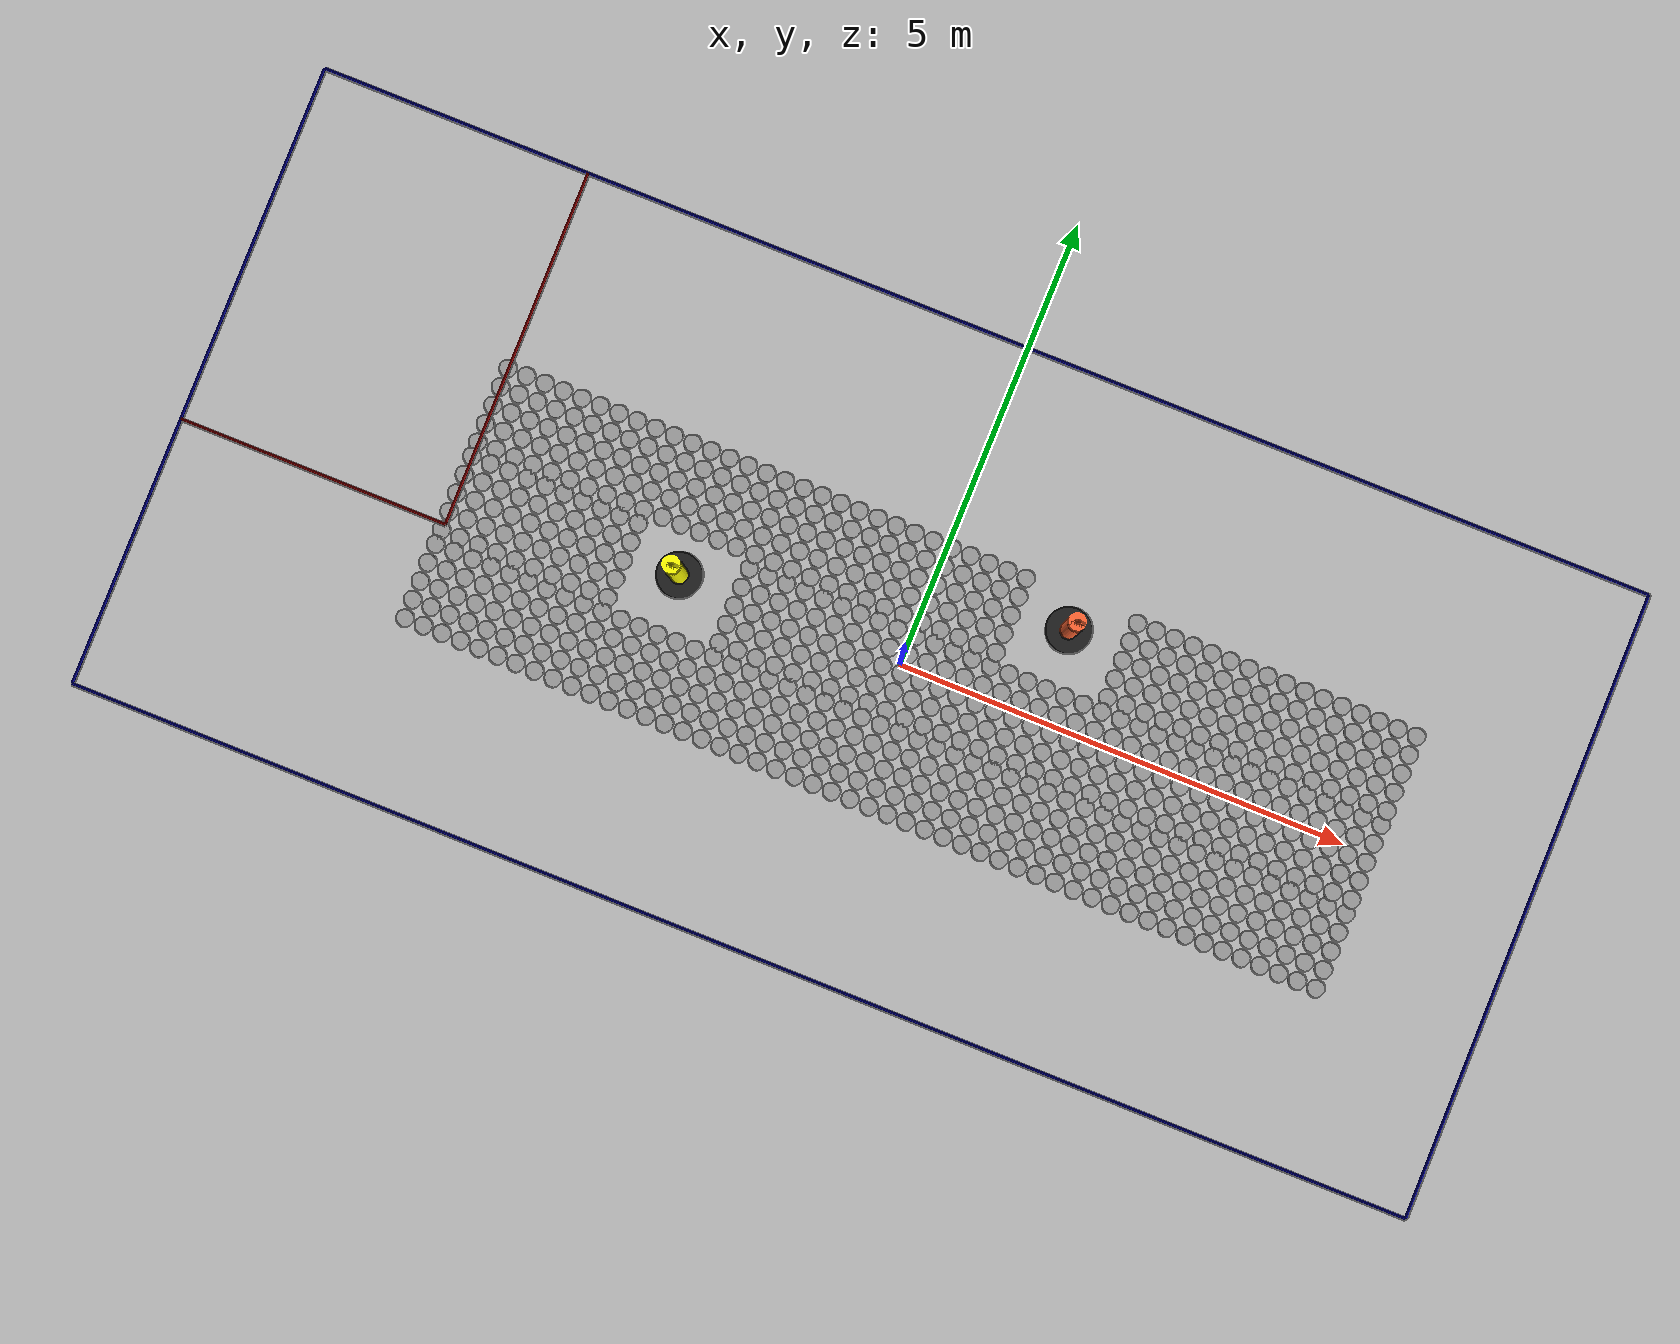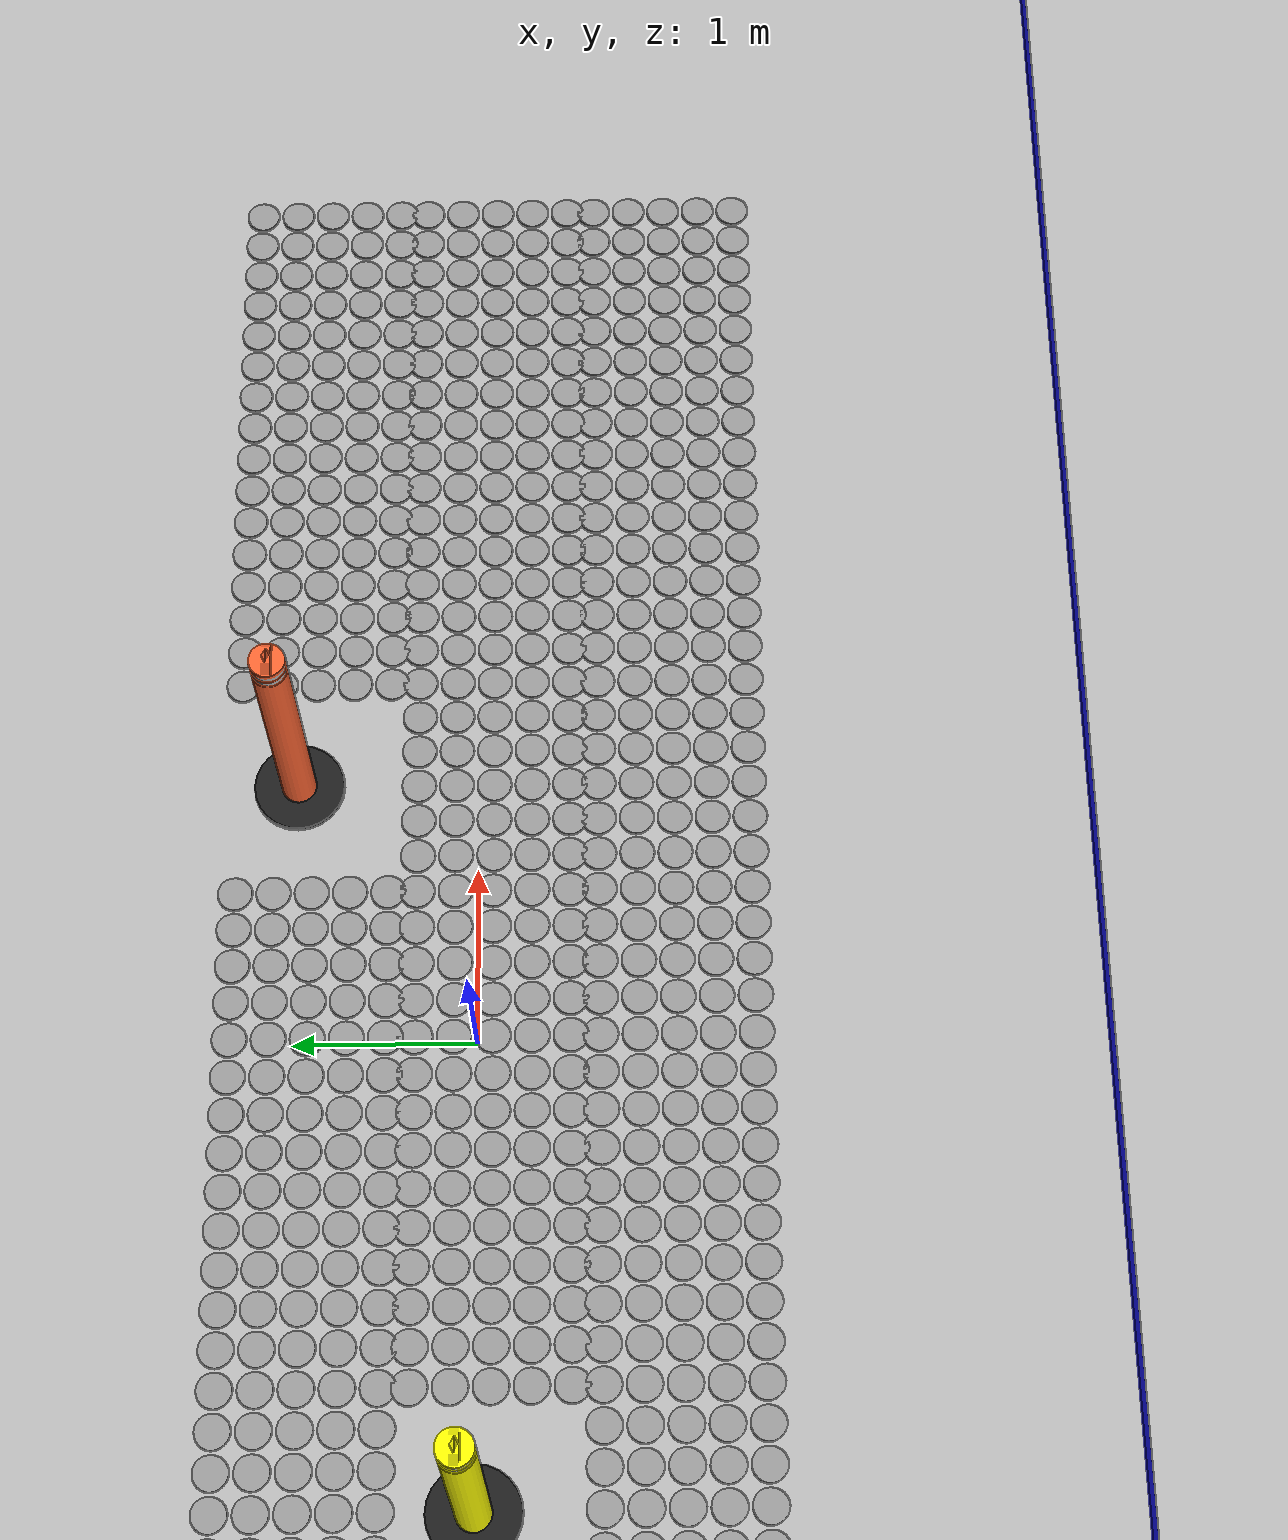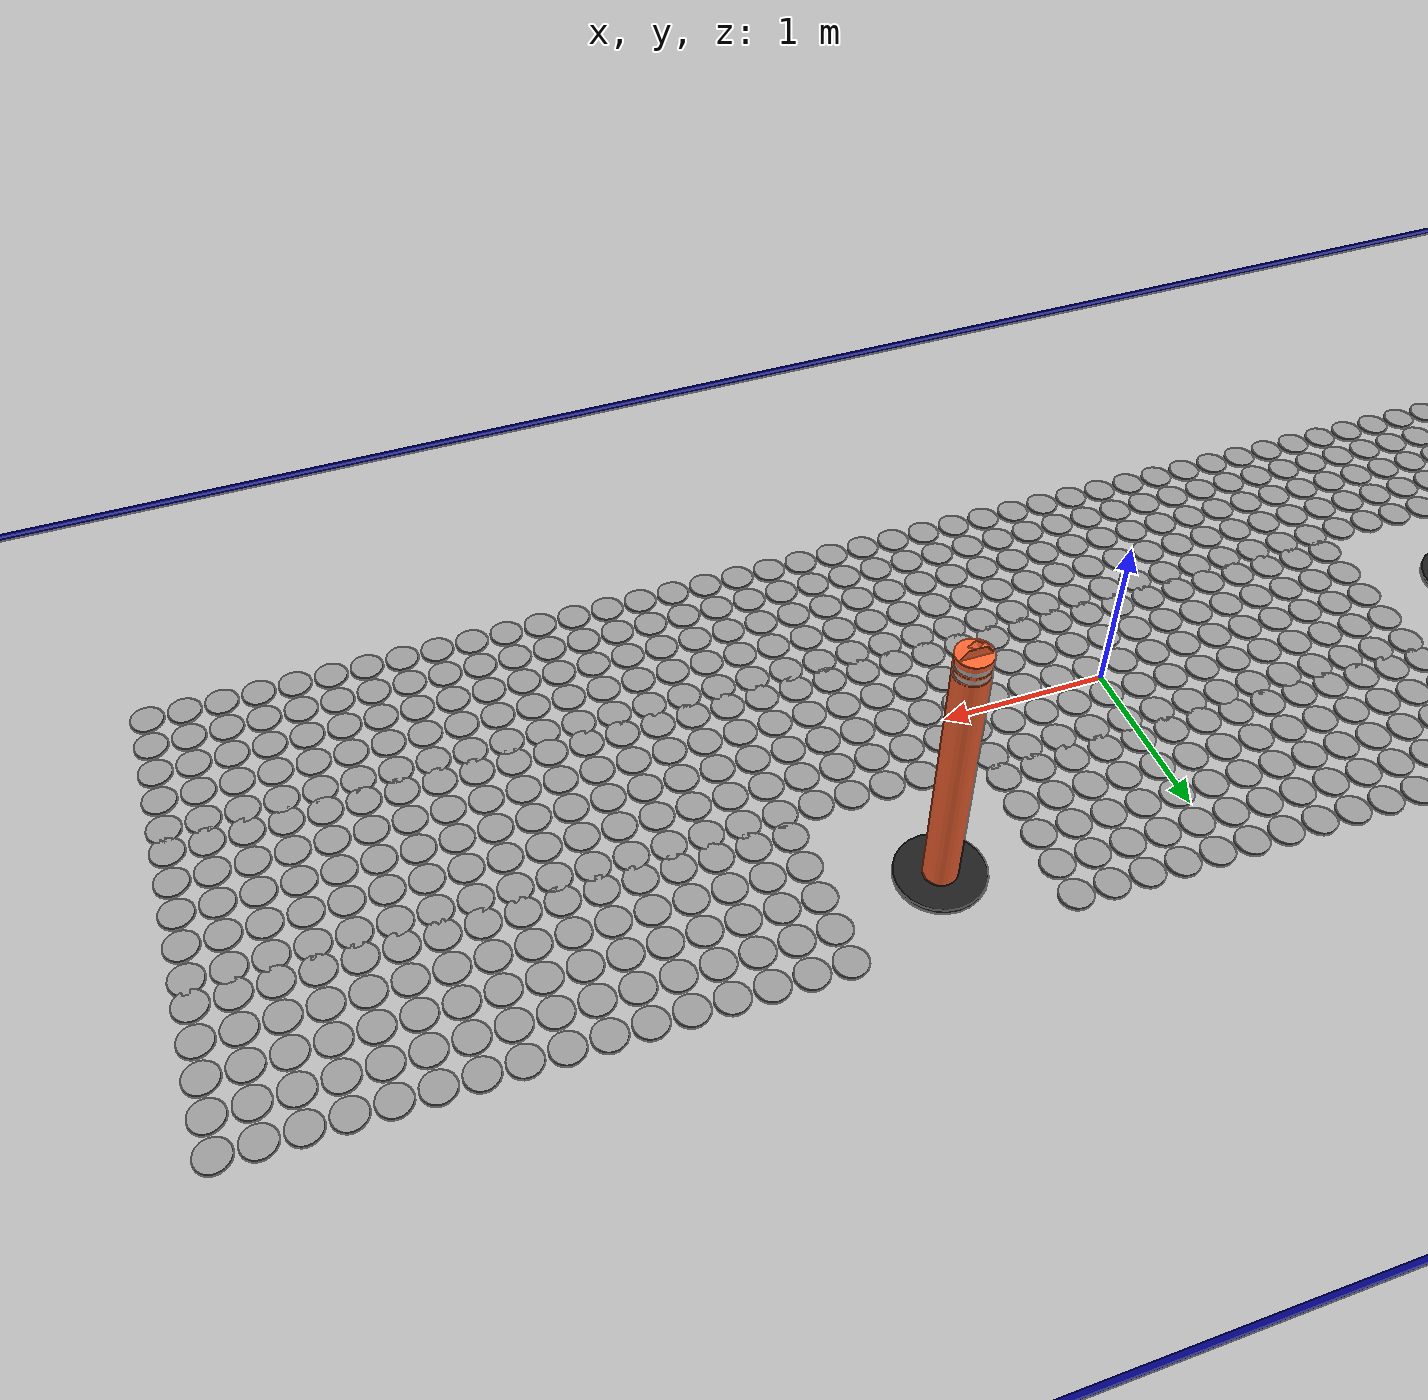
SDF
<sdf version="1.6">
 <world name="default">
  <light name="sun" type="directional">
   <pose>0 0 10 0 -0 0</pose>
   <diffuse>0.8 0.8 0.8 1</diffuse>
   <specular>0.1 0.1 0.1 1</specular>
   <attenuation>
    <range>1000</range>
    <constant>0.9</constant>
    <linear>0.01</linear>
    <quadratic>0.001</quadratic>
   </attenuation>
   <direction>-0.5 0.5 -1</direction>
  </light>
  <gravity>0 0 -9.8</gravity>
  <magnetic_field>6e-06 2.3e-05 -4.2e-05</magnetic_field>
  <atmosphere type="adiabatic"/>
  <physics name="default_physics" default="0" type="ode">
   <max_step_size>0.001</max_step_size>
   <real_time_factor>1</real_time_factor>
   <real_time_update_rate>1000</real_time_update_rate>
  </physics>
  <scene><ambient>0.4 0.4 0.4 1</ambient><background>0.7 0.7 0.7 1</background><shadows>1</shadows></scene>
  <spherical_coordinates>
   <surface_model>EARTH_WGS84</surface_model>
   <latitude_deg>0</latitude_deg>
   <longitude_deg>0</longitude_deg>
   <elevation>0</elevation>
   <heading_deg>0</heading_deg>
  </spherical_coordinates>
  <model name="brick_plane">
   <static>1</static>
   <link name="link">
    <collision name="collision">
     <geometry><plane><normal>0 0 1</normal><size>100 100</size></plane></geometry>
     <surface><friction><ode><mu>100</mu><mu2>50</mu2></ode></friction></surface>
    </collision>
    <visual name="visual">
     <cast_shadows>0</cast_shadows>
     <pose>0 0 -0.04 0 -0 0</pose>
     <geometry><mesh><uri>model://brick_plane/meshes/BrickRoad.dae</uri></mesh></geometry>
    </visual>
   </link>
   <pose>-0.038793 -0.127962 0 0 -0 0</pose>
  </model>
  <light name="user_point_light_0" type="point">
   <pose>-40.2877 36.9378 1 0 -0 0</pose>
   <diffuse>0.5 0.5 0.5 1</diffuse>
   <specular>0.1 0.1 0.1 1</specular>
   <attenuation>
    <range>20</range>
    <constant>0.5</constant>
    <linear>0.01</linear>
    <quadratic>0.001</quadratic>
   </attenuation>
   <cast_shadows>0</cast_shadows>
   <direction>0 0 -1</direction>
  </light>
  <light name="user_point_light_0_clone" type="point">
   <pose>-43.3445 16.5003 10 0 -0 0</pose>
   <diffuse>1 1 1 1</diffuse>
   <specular>1 1 1 1</specular>
   <direction>0 0 -1</direction>
   <attenuation>
    <range>100000</range>
    <constant>0.5</constant>
    <linear>0.01</linear>
    <quadratic>0.001</quadratic>
   </attenuation>
  </light>
  <light name="user_point_light_0_clone_0" type="point">
   <pose>-41.8744 -4.62896 10 0 -0 0</pose>
   <diffuse>1 1 1 1</diffuse>
   <specular>1 1 1 1</specular>
   <direction>0 0 -1</direction>
   <attenuation>
    <range>100000</range>
    <constant>0.5</constant>
    <linear>0.01</linear>
    <quadratic>0.001</quadratic>
   </attenuation>
  </light>
  <light name="user_point_light_0_clone_1" type="point">
   <pose>-45.3384 -27.6087 10 0 -0 0</pose>
   <diffuse>1 1 1 1</diffuse>
   <specular>1 1 1 1</specular>
   <direction>0 0 -1</direction>
   <attenuation>
    <range>100000</range>
    <constant>0.5</constant>
    <linear>0.01</linear>
    <quadratic>0.001</quadratic>
   </attenuation>
  </light>
  <light name="user_point_light_0_clone_2" type="point">
   <pose>-41.0308 -51.4934 10 0 -0 0</pose>
   <diffuse>1 1 1 1</diffuse>
   <specular>1 1 1 1</specular>
   <direction>0 0 -1</direction>
   <attenuation>
    <range>100000</range>
    <constant>0.5</constant>
    <linear>0.01</linear>
    <quadratic>0.001</quadratic>
   </attenuation>
  </light>
  <light name="user_point_light_0_clone_3" type="point">
   <pose>-13.091 -48.6057 10 0 -0 0</pose>
   <diffuse>1 1 1 1</diffuse>
   <specular>1 1 1 1</specular>
   <direction>0 0 -1</direction>
   <attenuation>
    <range>100000</range>
    <constant>0.5</constant>
    <linear>0.01</linear>
    <quadratic>0.001</quadratic>
   </attenuation>
  </light>
  <light name="user_point_light_0_clone_4" type="point">
   <pose>17.8273 -50.2126 10 0 -0 0</pose>
   <diffuse>1 1 1 1</diffuse>
   <specular>1 1 1 1</specular>
   <direction>0 0 -1</direction>
   <attenuation>
    <range>100000</range>
    <constant>0.5</constant>
    <linear>0.01</linear>
    <quadratic>0.001</quadratic>
   </attenuation>
  </light>
  <light name="user_point_light_0_clone_5" type="point">
   <pose>43.0105 -50.5018 10 0 -0 0</pose>
   <diffuse>1 1 1 1</diffuse>
   <specular>1 1 1 1</specular>
   <direction>0 0 -1</direction>
   <attenuation>
    <range>100000</range>
    <constant>0.5</constant>
    <linear>0.01</linear>
    <quadratic>0.001</quadratic>
   </attenuation>
  </light>
  <light name="user_point_light_0_clone_6" type="point">
   <pose>-30.8096 43.6215 10 0 -0 0</pose>
   <diffuse>1 1 1 1</diffuse>
   <specular>1 1 1 1</specular>
   <direction>0 0 -1</direction>
   <attenuation>
    <range>100000</range>
    <constant>0.5</constant>
    <linear>0.01</linear>
    <quadratic>0.001</quadratic>
   </attenuation>
  </light>
  <light name="user_point_light_0_clone_7" type="point">
   <pose>-6.06965 44.6895 10 0 -0 0</pose>
   <diffuse>1 1 1 1</diffuse>
   <specular>1 1 1 1</specular>
   <direction>0 0 -1</direction>
   <attenuation>
    <range>100000</range>
    <constant>0.5</constant>
    <linear>0.01</linear>
    <quadratic>0.001</quadratic>
   </attenuation>
  </light>
  <light name="user_point_light_0_clone_8" type="point">
   <pose>12.7263 46.5664 10 0 -0 0</pose>
   <diffuse>1 1 1 1</diffuse>
   <specular>1 1 1 1</specular>
   <direction>0 0 -1</direction>
   <attenuation>
    <range>100000</range>
    <constant>0.5</constant>
    <linear>0.01</linear>
    <quadratic>0.001</quadratic>
   </attenuation>
  </light>
  <light name="user_point_light_0_clone_9" type="point">
   <pose>31.1126 44.5953 10 0 -0 0</pose>
   <diffuse>1 1 1 1</diffuse>
   <specular>1 1 1 1</specular>
   <direction>0 0 -1</direction>
   <attenuation>
    <range>100000</range>
    <constant>0.5</constant>
    <linear>0.01</linear>
    <quadratic>0.001</quadratic>
   </attenuation>
  </light>
  <light name="user_point_light_0_clone_10" type="point">
   <pose>48.6896 31.6 10 0 -0 0</pose>
   <diffuse>1 1 1 1</diffuse>
   <specular>1 1 1 1</specular>
   <direction>0 0 -1</direction>
   <attenuation>
    <range>100000</range>
    <constant>0.5</constant>
    <linear>0.01</linear>
    <quadratic>0.001</quadratic>
   </attenuation>
  </light>
  <light name="user_point_light_0_clone_11" type="point">
   <pose>54.0783 8.97523 10 0 -0 0</pose>
   <diffuse>1 1 1 1</diffuse>
   <specular>1 1 1 1</specular>
   <direction>0 0 -1</direction>
   <attenuation>
    <range>100000</range>
    <constant>0.5</constant>
    <linear>0.01</linear>
    <quadratic>0.001</quadratic>
   </attenuation>
  </light>
  <light name="user_point_light_0_clone_12" type="point">
   <pose>59.1715 -20.1842 10 0 -0 0</pose>
   <diffuse>1 1 1 1</diffuse>
   <specular>1 1 1 1</specular>
   <direction>0 0 -1</direction>
   <attenuation>
    <range>100000</range>
    <constant>0.5</constant>
    <linear>0.01</linear>
    <quadratic>0.001</quadratic>
   </attenuation>
  </light>
  <light name="user_point_light_0_clone_13" type="point">
   <pose>56.6391 -41.8663 10 0 -0 0</pose>
   <diffuse>1 1 1 1</diffuse>
   <specular>1 1 1 1</specular>
   <direction>0 0 -1</direction>
   <attenuation>
    <range>100000</range>
    <constant>0.5</constant>
    <linear>0.01</linear>
    <quadratic>0.001</quadratic>
   </attenuation>
  </light>
  <model name="triple-I">
   <include><uri>model://triple-I</uri></include>
   <pose>-0.465032 -1.9092 0.030503 -0.000121 6.3e-05 0.005487</pose>
  </model>
  <model name="pylon_yellow">
   <include><uri>model://pylon_yellow</uri></include>
   <pose>-2.5 0.0 0 0 0 -8.1e-05</pose>
  </model>
  <model name="pylon_yellow">
   <include><uri>model://pylon_yellow</uri></include>
   <pose>-2.5 0.0 0 0 0 -8.1e-05</pose>
  </model>
  <model name="pylon_orange">
   <include><uri>model://pylon_orange</uri></include>
   <pose>1.5 1.0 0 0 0 -8.1e-05</pose>
  </model>
  <model name="unit_cylinder_clone_0">
   <pose>-5 0.5 0.008111 0 0 0</pose>
   <link name="link">
    <inertial>
     <mass>1</mass>
     <inertia><ixx>0.145833</ixx><ixy>0</ixy><ixz>0</ixz><iyy>0.145833</iyy><iyz>0</iyz><izz>0.125</izz></inertia>
    </inertial>
    <collision name="collision">
     <geometry><cylinder><radius>0.0950718</radius><length>0.0162339</length></cylinder></geometry>
     <max_contacts>5</max_contacts>
    </collision>
    <visual name="visual">
     <geometry><cylinder><radius>0.0950718</radius><length>0.0162339</length></cylinder></geometry>
     <material>
      <script><name>Gazebo/Grey</name><uri>file://media/materials/scripts/gazebo.material</uri></script>
     </material>
    </visual>
   </link>
  </model>
  <model name="unit_cylinder_clone_1">
   <pose>-5 0.71 0.008111 0 0 0</pose>
   <link name="link">
    <inertial>
     <mass>1</mass>
     <inertia><ixx>0.145833</ixx><ixy>0</ixy><ixz>0</ixz><iyy>0.145833</iyy><iyz>0</iyz><izz>0.125</izz></inertia>
    </inertial>
    <collision name="collision">
     <geometry><cylinder><radius>0.0950718</radius><length>0.0162339</length></cylinder></geometry>
     <max_contacts>5</max_contacts>
    </collision>
    <visual name="visual">
     <geometry><cylinder><radius>0.0950718</radius><length>0.0162339</length></cylinder></geometry>
     <material>
      <script><name>Gazebo/Grey</name><uri>file://media/materials/scripts/gazebo.material</uri></script>
     </material>
    </visual>
   </link>
  </model>
  <model name="unit_cylinder_clone_2">
   <pose>-5 0.92 0.008111 0 0 0</pose>
   <link name="link">
    <inertial>
     <mass>1</mass>
     <inertia><ixx>0.145833</ixx><ixy>0</ixy><ixz>0</ixz><iyy>0.145833</iyy><iyz>0</iyz><izz>0.125</izz></inertia>
    </inertial>
    <collision name="collision">
     <geometry><cylinder><radius>0.0950718</radius><length>0.0162339</length></cylinder></geometry>
     <max_contacts>5</max_contacts>
    </collision>
    <visual name="visual">
     <geometry><cylinder><radius>0.0950718</radius><length>0.0162339</length></cylinder></geometry>
     <material>
      <script><name>Gazebo/Grey</name><uri>file://media/materials/scripts/gazebo.material</uri></script>
     </material>
    </visual>
   </link>
  </model>
  <model name="unit_cylinder_clone_3">
   <pose>-5 1.13 0.008111 0 0 0</pose>
   <link name="link">
    <inertial>
     <mass>1</mass>
     <inertia><ixx>0.145833</ixx><ixy>0</ixy><ixz>0</ixz><iyy>0.145833</iyy><iyz>0</iyz><izz>0.125</izz></inertia>
    </inertial>
    <collision name="collision">
     <geometry><cylinder><radius>0.0950718</radius><length>0.0162339</length></cylinder></geometry>
     <max_contacts>5</max_contacts>
    </collision>
    <visual name="visual">
     <geometry><cylinder><radius>0.0950718</radius><length>0.0162339</length></cylinder></geometry>
     <material>
      <script><name>Gazebo/Grey</name><uri>file://media/materials/scripts/gazebo.material</uri></script>
     </material>
    </visual>
   </link>
  </model>
  <model name="unit_cylinder_clone_4">
   <pose>-5 1.34 0.008111 0 0 0</pose>
   <link name="link">
    <inertial>
     <mass>1</mass>
     <inertia><ixx>0.145833</ixx><ixy>0</ixy><ixz>0</ixz><iyy>0.145833</iyy><iyz>0</iyz><izz>0.125</izz></inertia>
    </inertial>
    <collision name="collision">
     <geometry><cylinder><radius>0.0950718</radius><length>0.0162339</length></cylinder></geometry>
     <max_contacts>5</max_contacts>
    </collision>
    <visual name="visual">
     <geometry><cylinder><radius>0.0950718</radius><length>0.0162339</length></cylinder></geometry>
     <material>
      <script><name>Gazebo/Grey</name><uri>file://media/materials/scripts/gazebo.material</uri></script>
     </material>
    </visual>
   </link>
  </model>
  <model name="unit_cylinder_clone_5">
   <pose>-4.79 0.5 0.008111 0 0 0</pose>
   <link name="link">
    <inertial>
     <mass>1</mass>
     <inertia><ixx>0.145833</ixx><ixy>0</ixy><ixz>0</ixz><iyy>0.145833</iyy><iyz>0</iyz><izz>0.125</izz></inertia>
    </inertial>
    <collision name="collision">
     <geometry><cylinder><radius>0.0950718</radius><length>0.0162339</length></cylinder></geometry>
     <max_contacts>5</max_contacts>
    </collision>
    <visual name="visual">
     <geometry><cylinder><radius>0.0950718</radius><length>0.0162339</length></cylinder></geometry>
     <material>
      <script><name>Gazebo/Grey</name><uri>file://media/materials/scripts/gazebo.material</uri></script>
     </material>
    </visual>
   </link>
  </model>
  <model name="unit_cylinder_clone_6">
   <pose>-4.79 0.71 0.008111 0 0 0</pose>
   <link name="link">
    <inertial>
     <mass>1</mass>
     <inertia><ixx>0.145833</ixx><ixy>0</ixy><ixz>0</ixz><iyy>0.145833</iyy><iyz>0</iyz><izz>0.125</izz></inertia>
    </inertial>
    <collision name="collision">
     <geometry><cylinder><radius>0.0950718</radius><length>0.0162339</length></cylinder></geometry>
     <max_contacts>5</max_contacts>
    </collision>
    <visual name="visual">
     <geometry><cylinder><radius>0.0950718</radius><length>0.0162339</length></cylinder></geometry>
     <material>
      <script><name>Gazebo/Grey</name><uri>file://media/materials/scripts/gazebo.material</uri></script>
     </material>
    </visual>
   </link>
  </model>
  <model name="unit_cylinder_clone_7">
   <pose>-4.79 0.92 0.008111 0 0 0</pose>
   <link name="link">
    <inertial>
     <mass>1</mass>
     <inertia><ixx>0.145833</ixx><ixy>0</ixy><ixz>0</ixz><iyy>0.145833</iyy><iyz>0</iyz><izz>0.125</izz></inertia>
    </inertial>
    <collision name="collision">
     <geometry><cylinder><radius>0.0950718</radius><length>0.0162339</length></cylinder></geometry>
     <max_contacts>5</max_contacts>
    </collision>
    <visual name="visual">
     <geometry><cylinder><radius>0.0950718</radius><length>0.0162339</length></cylinder></geometry>
     <material>
      <script><name>Gazebo/Grey</name><uri>file://media/materials/scripts/gazebo.material</uri></script>
     </material>
    </visual>
   </link>
  </model>
  <model name="unit_cylinder_clone_8">
   <pose>-4.79 1.13 0.008111 0 0 0</pose>
   <link name="link">
    <inertial>
     <mass>1</mass>
     <inertia><ixx>0.145833</ixx><ixy>0</ixy><ixz>0</ixz><iyy>0.145833</iyy><iyz>0</iyz><izz>0.125</izz></inertia>
    </inertial>
    <collision name="collision">
     <geometry><cylinder><radius>0.0950718</radius><length>0.0162339</length></cylinder></geometry>
     <max_contacts>5</max_contacts>
    </collision>
    <visual name="visual">
     <geometry><cylinder><radius>0.0950718</radius><length>0.0162339</length></cylinder></geometry>
     <material>
      <script><name>Gazebo/Grey</name><uri>file://media/materials/scripts/gazebo.material</uri></script>
     </material>
    </visual>
   </link>
  </model>
  <model name="unit_cylinder_clone_9">
   <pose>-4.79 1.34 0.008111 0 0 0</pose>
   <link name="link">
    <inertial>
     <mass>1</mass>
     <inertia><ixx>0.145833</ixx><ixy>0</ixy><ixz>0</ixz><iyy>0.145833</iyy><iyz>0</iyz><izz>0.125</izz></inertia>
    </inertial>
    <collision name="collision">
     <geometry><cylinder><radius>0.0950718</radius><length>0.0162339</length></cylinder></geometry>
     <max_contacts>5</max_contacts>
    </collision>
    <visual name="visual">
     <geometry><cylinder><radius>0.0950718</radius><length>0.0162339</length></cylinder></geometry>
     <material>
      <script><name>Gazebo/Grey</name><uri>file://media/materials/scripts/gazebo.material</uri></script>
     </material>
    </visual>
   </link>
  </model>
  <model name="unit_cylinder_clone_10">
   <pose>-4.58 0.5 0.008111 0 0 0</pose>
   <link name="link">
    <inertial>
     <mass>1</mass>
     <inertia><ixx>0.145833</ixx><ixy>0</ixy><ixz>0</ixz><iyy>0.145833</iyy><iyz>0</iyz><izz>0.125</izz></inertia>
    </inertial>
    <collision name="collision">
     <geometry><cylinder><radius>0.0950718</radius><length>0.0162339</length></cylinder></geometry>
     <max_contacts>5</max_contacts>
    </collision>
    <visual name="visual">
     <geometry><cylinder><radius>0.0950718</radius><length>0.0162339</length></cylinder></geometry>
     <material>
      <script><name>Gazebo/Grey</name><uri>file://media/materials/scripts/gazebo.material</uri></script>
     </material>
    </visual>
   </link>
  </model>
  <model name="unit_cylinder_clone_11">
   <pose>-4.58 0.71 0.008111 0 0 0</pose>
   <link name="link">
    <inertial>
     <mass>1</mass>
     <inertia><ixx>0.145833</ixx><ixy>0</ixy><ixz>0</ixz><iyy>0.145833</iyy><iyz>0</iyz><izz>0.125</izz></inertia>
    </inertial>
    <collision name="collision">
     <geometry><cylinder><radius>0.0950718</radius><length>0.0162339</length></cylinder></geometry>
     <max_contacts>5</max_contacts>
    </collision>
    <visual name="visual">
     <geometry><cylinder><radius>0.0950718</radius><length>0.0162339</length></cylinder></geometry>
     <material>
      <script><name>Gazebo/Grey</name><uri>file://media/materials/scripts/gazebo.material</uri></script>
     </material>
    </visual>
   </link>
  </model>
  <model name="unit_cylinder_clone_12">
   <pose>-4.58 0.92 0.008111 0 0 0</pose>
   <link name="link">
    <inertial>
     <mass>1</mass>
     <inertia><ixx>0.145833</ixx><ixy>0</ixy><ixz>0</ixz><iyy>0.145833</iyy><iyz>0</iyz><izz>0.125</izz></inertia>
    </inertial>
    <collision name="collision">
     <geometry><cylinder><radius>0.0950718</radius><length>0.0162339</length></cylinder></geometry>
     <max_contacts>5</max_contacts>
    </collision>
    <visual name="visual">
     <geometry><cylinder><radius>0.0950718</radius><length>0.0162339</length></cylinder></geometry>
     <material>
      <script><name>Gazebo/Grey</name><uri>file://media/materials/scripts/gazebo.material</uri></script>
     </material>
    </visual>
   </link>
  </model>
  <model name="unit_cylinder_clone_13">
   <pose>-4.58 1.13 0.008111 0 0 0</pose>
   <link name="link">
    <inertial>
     <mass>1</mass>
     <inertia><ixx>0.145833</ixx><ixy>0</ixy><ixz>0</ixz><iyy>0.145833</iyy><iyz>0</iyz><izz>0.125</izz></inertia>
    </inertial>
    <collision name="collision">
     <geometry><cylinder><radius>0.0950718</radius><length>0.0162339</length></cylinder></geometry>
     <max_contacts>5</max_contacts>
    </collision>
    <visual name="visual">
     <geometry><cylinder><radius>0.0950718</radius><length>0.0162339</length></cylinder></geometry>
     <material>
      <script><name>Gazebo/Grey</name><uri>file://media/materials/scripts/gazebo.material</uri></script>
     </material>
    </visual>
   </link>
  </model>
  <model name="unit_cylinder_clone_14">
   <pose>-4.58 1.34 0.008111 0 0 0</pose>
   <link name="link">
    <inertial>
     <mass>1</mass>
     <inertia><ixx>0.145833</ixx><ixy>0</ixy><ixz>0</ixz><iyy>0.145833</iyy><iyz>0</iyz><izz>0.125</izz></inertia>
    </inertial>
    <collision name="collision">
     <geometry><cylinder><radius>0.0950718</radius><length>0.0162339</length></cylinder></geometry>
     <max_contacts>5</max_contacts>
    </collision>
    <visual name="visual">
     <geometry><cylinder><radius>0.0950718</radius><length>0.0162339</length></cylinder></geometry>
     <material>
      <script><name>Gazebo/Grey</name><uri>file://media/materials/scripts/gazebo.material</uri></script>
     </material>
    </visual>
   </link>
  </model>
  <model name="unit_cylinder_clone_15">
   <pose>-4.37 0.5 0.008111 0 0 0</pose>
   <link name="link">
    <inertial>
     <mass>1</mass>
     <inertia><ixx>0.145833</ixx><ixy>0</ixy><ixz>0</ixz><iyy>0.145833</iyy><iyz>0</iyz><izz>0.125</izz></inertia>
    </inertial>
    <collision name="collision">
     <geometry><cylinder><radius>0.0950718</radius><length>0.0162339</length></cylinder></geometry>
     <max_contacts>5</max_contacts>
    </collision>
    <visual name="visual">
     <geometry><cylinder><radius>0.0950718</radius><length>0.0162339</length></cylinder></geometry>
     <material>
      <script><name>Gazebo/Grey</name><uri>file://media/materials/scripts/gazebo.material</uri></script>
     </material>
    </visual>
   </link>
  </model>
  <model name="unit_cylinder_clone_16">
   <pose>-4.37 0.71 0.008111 0 0 0</pose>
   <link name="link">
    <inertial>
     <mass>1</mass>
     <inertia><ixx>0.145833</ixx><ixy>0</ixy><ixz>0</ixz><iyy>0.145833</iyy><iyz>0</iyz><izz>0.125</izz></inertia>
    </inertial>
    <collision name="collision">
     <geometry><cylinder><radius>0.0950718</radius><length>0.0162339</length></cylinder></geometry>
     <max_contacts>5</max_contacts>
    </collision>
    <visual name="visual">
     <geometry><cylinder><radius>0.0950718</radius><length>0.0162339</length></cylinder></geometry>
     <material>
      <script><name>Gazebo/Grey</name><uri>file://media/materials/scripts/gazebo.material</uri></script>
     </material>
    </visual>
   </link>
  </model>
  <model name="unit_cylinder_clone_17">
   <pose>-4.37 0.92 0.008111 0 0 0</pose>
   <link name="link">
    <inertial>
     <mass>1</mass>
     <inertia><ixx>0.145833</ixx><ixy>0</ixy><ixz>0</ixz><iyy>0.145833</iyy><iyz>0</iyz><izz>0.125</izz></inertia>
    </inertial>
    <collision name="collision">
     <geometry><cylinder><radius>0.0950718</radius><length>0.0162339</length></cylinder></geometry>
     <max_contacts>5</max_contacts>
    </collision>
    <visual name="visual">
     <geometry><cylinder><radius>0.0950718</radius><length>0.0162339</length></cylinder></geometry>
     <material>
      <script><name>Gazebo/Grey</name><uri>file://media/materials/scripts/gazebo.material</uri></script>
     </material>
    </visual>
   </link>
  </model>
  <model name="unit_cylinder_clone_18">
   <pose>-4.37 1.13 0.008111 0 0 0</pose>
   <link name="link">
    <inertial>
     <mass>1</mass>
     <inertia><ixx>0.145833</ixx><ixy>0</ixy><ixz>0</ixz><iyy>0.145833</iyy><iyz>0</iyz><izz>0.125</izz></inertia>
    </inertial>
    <collision name="collision">
     <geometry><cylinder><radius>0.0950718</radius><length>0.0162339</length></cylinder></geometry>
     <max_contacts>5</max_contacts>
    </collision>
    <visual name="visual">
     <geometry><cylinder><radius>0.0950718</radius><length>0.0162339</length></cylinder></geometry>
     <material>
      <script><name>Gazebo/Grey</name><uri>file://media/materials/scripts/gazebo.material</uri></script>
     </material>
    </visual>
   </link>
  </model>
  <model name="unit_cylinder_clone_19">
   <pose>-4.37 1.34 0.008111 0 0 0</pose>
   <link name="link">
    <inertial>
     <mass>1</mass>
     <inertia><ixx>0.145833</ixx><ixy>0</ixy><ixz>0</ixz><iyy>0.145833</iyy><iyz>0</iyz><izz>0.125</izz></inertia>
    </inertial>
    <collision name="collision">
     <geometry><cylinder><radius>0.0950718</radius><length>0.0162339</length></cylinder></geometry>
     <max_contacts>5</max_contacts>
    </collision>
    <visual name="visual">
     <geometry><cylinder><radius>0.0950718</radius><length>0.0162339</length></cylinder></geometry>
     <material>
      <script><name>Gazebo/Grey</name><uri>file://media/materials/scripts/gazebo.material</uri></script>
     </material>
    </visual>
   </link>
  </model>
  <model name="unit_cylinder_clone_20">
   <pose>-4.16 0.5 0.008111 0 0 0</pose>
   <link name="link">
    <inertial>
     <mass>1</mass>
     <inertia><ixx>0.145833</ixx><ixy>0</ixy><ixz>0</ixz><iyy>0.145833</iyy><iyz>0</iyz><izz>0.125</izz></inertia>
    </inertial>
    <collision name="collision">
     <geometry><cylinder><radius>0.0950718</radius><length>0.0162339</length></cylinder></geometry>
     <max_contacts>5</max_contacts>
    </collision>
    <visual name="visual">
     <geometry><cylinder><radius>0.0950718</radius><length>0.0162339</length></cylinder></geometry>
     <material>
      <script><name>Gazebo/Grey</name><uri>file://media/materials/scripts/gazebo.material</uri></script>
     </material>
    </visual>
   </link>
  </model>
  <model name="unit_cylinder_clone_21">
   <pose>-4.16 0.71 0.008111 0 0 0</pose>
   <link name="link">
    <inertial>
     <mass>1</mass>
     <inertia><ixx>0.145833</ixx><ixy>0</ixy><ixz>0</ixz><iyy>0.145833</iyy><iyz>0</iyz><izz>0.125</izz></inertia>
    </inertial>
    <collision name="collision">
     <geometry><cylinder><radius>0.0950718</radius><length>0.0162339</length></cylinder></geometry>
     <max_contacts>5</max_contacts>
    </collision>
    <visual name="visual">
     <geometry><cylinder><radius>0.0950718</radius><length>0.0162339</length></cylinder></geometry>
     <material>
      <script><name>Gazebo/Grey</name><uri>file://media/materials/scripts/gazebo.material</uri></script>
     </material>
    </visual>
   </link>
  </model>
  <model name="unit_cylinder_clone_22">
   <pose>-4.16 0.92 0.008111 0 0 0</pose>
   <link name="link">
    <inertial>
     <mass>1</mass>
     <inertia><ixx>0.145833</ixx><ixy>0</ixy><ixz>0</ixz><iyy>0.145833</iyy><iyz>0</iyz><izz>0.125</izz></inertia>
    </inertial>
    <collision name="collision">
     <geometry><cylinder><radius>0.0950718</radius><length>0.0162339</length></cylinder></geometry>
     <max_contacts>5</max_contacts>
    </collision>
    <visual name="visual">
     <geometry><cylinder><radius>0.0950718</radius><length>0.0162339</length></cylinder></geometry>
     <material>
      <script><name>Gazebo/Grey</name><uri>file://media/materials/scripts/gazebo.material</uri></script>
     </material>
    </visual>
   </link>
  </model>
  <model name="unit_cylinder_clone_23">
   <pose>-4.16 1.13 0.008111 0 0 0</pose>
   <link name="link">
    <inertial>
     <mass>1</mass>
     <inertia><ixx>0.145833</ixx><ixy>0</ixy><ixz>0</ixz><iyy>0.145833</iyy><iyz>0</iyz><izz>0.125</izz></inertia>
    </inertial>
    <collision name="collision">
     <geometry><cylinder><radius>0.0950718</radius><length>0.0162339</length></cylinder></geometry>
     <max_contacts>5</max_contacts>
    </collision>
    <visual name="visual">
     <geometry><cylinder><radius>0.0950718</radius><length>0.0162339</length></cylinder></geometry>
     <material>
      <script><name>Gazebo/Grey</name><uri>file://media/materials/scripts/gazebo.material</uri></script>
     </material>
    </visual>
   </link>
  </model>
  <model name="unit_cylinder_clone_24">
   <pose>-4.16 1.34 0.008111 0 0 0</pose>
   <link name="link">
    <inertial>
     <mass>1</mass>
     <inertia><ixx>0.145833</ixx><ixy>0</ixy><ixz>0</ixz><iyy>0.145833</iyy><iyz>0</iyz><izz>0.125</izz></inertia>
    </inertial>
    <collision name="collision">
     <geometry><cylinder><radius>0.0950718</radius><length>0.0162339</length></cylinder></geometry>
     <max_contacts>5</max_contacts>
    </collision>
    <visual name="visual">
     <geometry><cylinder><radius>0.0950718</radius><length>0.0162339</length></cylinder></geometry>
     <material>
      <script><name>Gazebo/Grey</name><uri>file://media/materials/scripts/gazebo.material</uri></script>
     </material>
    </visual>
   </link>
  </model>
  <model name="unit_cylinder_clone_25">
   <pose>-3.95 0.5 0.008111 0 0 0</pose>
   <link name="link">
    <inertial>
     <mass>1</mass>
     <inertia><ixx>0.145833</ixx><ixy>0</ixy><ixz>0</ixz><iyy>0.145833</iyy><iyz>0</iyz><izz>0.125</izz></inertia>
    </inertial>
    <collision name="collision">
     <geometry><cylinder><radius>0.0950718</radius><length>0.0162339</length></cylinder></geometry>
     <max_contacts>5</max_contacts>
    </collision>
    <visual name="visual">
     <geometry><cylinder><radius>0.0950718</radius><length>0.0162339</length></cylinder></geometry>
     <material>
      <script><name>Gazebo/Grey</name><uri>file://media/materials/scripts/gazebo.material</uri></script>
     </material>
    </visual>
   </link>
  </model>
  <model name="unit_cylinder_clone_26">
   <pose>-3.95 0.71 0.008111 0 0 0</pose>
   <link name="link">
    <inertial>
     <mass>1</mass>
     <inertia><ixx>0.145833</ixx><ixy>0</ixy><ixz>0</ixz><iyy>0.145833</iyy><iyz>0</iyz><izz>0.125</izz></inertia>
    </inertial>
    <collision name="collision">
     <geometry><cylinder><radius>0.0950718</radius><length>0.0162339</length></cylinder></geometry>
     <max_contacts>5</max_contacts>
    </collision>
    <visual name="visual">
     <geometry><cylinder><radius>0.0950718</radius><length>0.0162339</length></cylinder></geometry>
     <material>
      <script><name>Gazebo/Grey</name><uri>file://media/materials/scripts/gazebo.material</uri></script>
     </material>
    </visual>
   </link>
  </model>
  <model name="unit_cylinder_clone_27">
   <pose>-3.95 0.92 0.008111 0 0 0</pose>
   <link name="link">
    <inertial>
     <mass>1</mass>
     <inertia><ixx>0.145833</ixx><ixy>0</ixy><ixz>0</ixz><iyy>0.145833</iyy><iyz>0</iyz><izz>0.125</izz></inertia>
    </inertial>
    <collision name="collision">
     <geometry><cylinder><radius>0.0950718</radius><length>0.0162339</length></cylinder></geometry>
     <max_contacts>5</max_contacts>
    </collision>
    <visual name="visual">
     <geometry><cylinder><radius>0.0950718</radius><length>0.0162339</length></cylinder></geometry>
     <material>
      <script><name>Gazebo/Grey</name><uri>file://media/materials/scripts/gazebo.material</uri></script>
     </material>
    </visual>
   </link>
  </model>
  <model name="unit_cylinder_clone_28">
   <pose>-3.95 1.13 0.008111 0 0 0</pose>
   <link name="link">
    <inertial>
     <mass>1</mass>
     <inertia><ixx>0.145833</ixx><ixy>0</ixy><ixz>0</ixz><iyy>0.145833</iyy><iyz>0</iyz><izz>0.125</izz></inertia>
    </inertial>
    <collision name="collision">
     <geometry><cylinder><radius>0.0950718</radius><length>0.0162339</length></cylinder></geometry>
     <max_contacts>5</max_contacts>
    </collision>
    <visual name="visual">
     <geometry><cylinder><radius>0.0950718</radius><length>0.0162339</length></cylinder></geometry>
     <material>
      <script><name>Gazebo/Grey</name><uri>file://media/materials/scripts/gazebo.material</uri></script>
     </material>
    </visual>
   </link>
  </model>
  <model name="unit_cylinder_clone_29">
   <pose>-3.95 1.34 0.008111 0 0 0</pose>
   <link name="link">
    <inertial>
     <mass>1</mass>
     <inertia><ixx>0.145833</ixx><ixy>0</ixy><ixz>0</ixz><iyy>0.145833</iyy><iyz>0</iyz><izz>0.125</izz></inertia>
    </inertial>
    <collision name="collision">
     <geometry><cylinder><radius>0.0950718</radius><length>0.0162339</length></cylinder></geometry>
     <max_contacts>5</max_contacts>
    </collision>
    <visual name="visual">
     <geometry><cylinder><radius>0.0950718</radius><length>0.0162339</length></cylinder></geometry>
     <material>
      <script><name>Gazebo/Grey</name><uri>file://media/materials/scripts/gazebo.material</uri></script>
     </material>
    </visual>
   </link>
  </model>
  <model name="unit_cylinder_clone_30">
   <pose>-3.74 0.5 0.008111 0 0 0</pose>
   <link name="link">
    <inertial>
     <mass>1</mass>
     <inertia><ixx>0.145833</ixx><ixy>0</ixy><ixz>0</ixz><iyy>0.145833</iyy><iyz>0</iyz><izz>0.125</izz></inertia>
    </inertial>
    <collision name="collision">
     <geometry><cylinder><radius>0.0950718</radius><length>0.0162339</length></cylinder></geometry>
     <max_contacts>5</max_contacts>
    </collision>
    <visual name="visual">
     <geometry><cylinder><radius>0.0950718</radius><length>0.0162339</length></cylinder></geometry>
     <material>
      <script><name>Gazebo/Grey</name><uri>file://media/materials/scripts/gazebo.material</uri></script>
     </material>
    </visual>
   </link>
  </model>
  <model name="unit_cylinder_clone_31">
   <pose>-3.74 0.71 0.008111 0 0 0</pose>
   <link name="link">
    <inertial>
     <mass>1</mass>
     <inertia><ixx>0.145833</ixx><ixy>0</ixy><ixz>0</ixz><iyy>0.145833</iyy><iyz>0</iyz><izz>0.125</izz></inertia>
    </inertial>
    <collision name="collision">
     <geometry><cylinder><radius>0.0950718</radius><length>0.0162339</length></cylinder></geometry>
     <max_contacts>5</max_contacts>
    </collision>
    <visual name="visual">
     <geometry><cylinder><radius>0.0950718</radius><length>0.0162339</length></cylinder></geometry>
     <material>
      <script><name>Gazebo/Grey</name><uri>file://media/materials/scripts/gazebo.material</uri></script>
     </material>
    </visual>
   </link>
  </model>
  <model name="unit_cylinder_clone_32">
   <pose>-3.74 0.92 0.008111 0 0 0</pose>
   <link name="link">
    <inertial>
     <mass>1</mass>
     <inertia><ixx>0.145833</ixx><ixy>0</ixy><ixz>0</ixz><iyy>0.145833</iyy><iyz>0</iyz><izz>0.125</izz></inertia>
    </inertial>
    <collision name="collision">
     <geometry><cylinder><radius>0.0950718</radius><length>0.0162339</length></cylinder></geometry>
     <max_contacts>5</max_contacts>
    </collision>
    <visual name="visual">
     <geometry><cylinder><radius>0.0950718</radius><length>0.0162339</length></cylinder></geometry>
     <material>
      <script><name>Gazebo/Grey</name><uri>file://media/materials/scripts/gazebo.material</uri></script>
     </material>
    </visual>
   </link>
  </model>
  <model name="unit_cylinder_clone_33">
   <pose>-3.74 1.13 0.008111 0 0 0</pose>
   <link name="link">
    <inertial>
     <mass>1</mass>
     <inertia><ixx>0.145833</ixx><ixy>0</ixy><ixz>0</ixz><iyy>0.145833</iyy><iyz>0</iyz><izz>0.125</izz></inertia>
    </inertial>
    <collision name="collision">
     <geometry><cylinder><radius>0.0950718</radius><length>0.0162339</length></cylinder></geometry>
     <max_contacts>5</max_contacts>
    </collision>
    <visual name="visual">
     <geometry><cylinder><radius>0.0950718</radius><length>0.0162339</length></cylinder></geometry>
     <material>
      <script><name>Gazebo/Grey</name><uri>file://media/materials/scripts/gazebo.material</uri></script>
     </material>
    </visual>
   </link>
  </model>
  <model name="unit_cylinder_clone_34">
   <pose>-3.74 1.34 0.008111 0 0 0</pose>
   <link name="link">
    <inertial>
     <mass>1</mass>
     <inertia><ixx>0.145833</ixx><ixy>0</ixy><ixz>0</ixz><iyy>0.145833</iyy><iyz>0</iyz><izz>0.125</izz></inertia>
    </inertial>
    <collision name="collision">
     <geometry><cylinder><radius>0.0950718</radius><length>0.0162339</length></cylinder></geometry>
     <max_contacts>5</max_contacts>
    </collision>
    <visual name="visual">
     <geometry><cylinder><radius>0.0950718</radius><length>0.0162339</length></cylinder></geometry>
     <material>
      <script><name>Gazebo/Grey</name><uri>file://media/materials/scripts/gazebo.material</uri></script>
     </material>
    </visual>
   </link>
  </model>
  <model name="unit_cylinder_clone_35">
   <pose>-3.53 0.5 0.008111 0 0 0</pose>
   <link name="link">
    <inertial>
     <mass>1</mass>
     <inertia><ixx>0.145833</ixx><ixy>0</ixy><ixz>0</ixz><iyy>0.145833</iyy><iyz>0</iyz><izz>0.125</izz></inertia>
    </inertial>
    <collision name="collision">
     <geometry><cylinder><radius>0.0950718</radius><length>0.0162339</length></cylinder></geometry>
     <max_contacts>5</max_contacts>
    </collision>
    <visual name="visual">
     <geometry><cylinder><radius>0.0950718</radius><length>0.0162339</length></cylinder></geometry>
     <material>
      <script><name>Gazebo/Grey</name><uri>file://media/materials/scripts/gazebo.material</uri></script>
     </material>
    </visual>
   </link>
  </model>
  <model name="unit_cylinder_clone_36">
   <pose>-3.53 0.71 0.008111 0 0 0</pose>
   <link name="link">
    <inertial>
     <mass>1</mass>
     <inertia><ixx>0.145833</ixx><ixy>0</ixy><ixz>0</ixz><iyy>0.145833</iyy><iyz>0</iyz><izz>0.125</izz></inertia>
    </inertial>
    <collision name="collision">
     <geometry><cylinder><radius>0.0950718</radius><length>0.0162339</length></cylinder></geometry>
     <max_contacts>5</max_contacts>
    </collision>
    <visual name="visual">
     <geometry><cylinder><radius>0.0950718</radius><length>0.0162339</length></cylinder></geometry>
     <material>
      <script><name>Gazebo/Grey</name><uri>file://media/materials/scripts/gazebo.material</uri></script>
     </material>
    </visual>
   </link>
  </model>
  <model name="unit_cylinder_clone_37">
   <pose>-3.53 0.92 0.008111 0 0 0</pose>
   <link name="link">
    <inertial>
     <mass>1</mass>
     <inertia><ixx>0.145833</ixx><ixy>0</ixy><ixz>0</ixz><iyy>0.145833</iyy><iyz>0</iyz><izz>0.125</izz></inertia>
    </inertial>
    <collision name="collision">
     <geometry><cylinder><radius>0.0950718</radius><length>0.0162339</length></cylinder></geometry>
     <max_contacts>5</max_contacts>
    </collision>
    <visual name="visual">
     <geometry><cylinder><radius>0.0950718</radius><length>0.0162339</length></cylinder></geometry>
     <material>
      <script><name>Gazebo/Grey</name><uri>file://media/materials/scripts/gazebo.material</uri></script>
     </material>
    </visual>
   </link>
  </model>
  <model name="unit_cylinder_clone_38">
   <pose>-3.53 1.13 0.008111 0 0 0</pose>
   <link name="link">
    <inertial>
     <mass>1</mass>
     <inertia><ixx>0.145833</ixx><ixy>0</ixy><ixz>0</ixz><iyy>0.145833</iyy><iyz>0</iyz><izz>0.125</izz></inertia>
    </inertial>
    <collision name="collision">
     <geometry><cylinder><radius>0.0950718</radius><length>0.0162339</length></cylinder></geometry>
     <max_contacts>5</max_contacts>
    </collision>
    <visual name="visual">
     <geometry><cylinder><radius>0.0950718</radius><length>0.0162339</length></cylinder></geometry>
     <material>
      <script><name>Gazebo/Grey</name><uri>file://media/materials/scripts/gazebo.material</uri></script>
     </material>
    </visual>
   </link>
  </model>
  <model name="unit_cylinder_clone_39">
   <pose>-3.53 1.34 0.008111 0 0 0</pose>
   <link name="link">
    <inertial>
     <mass>1</mass>
     <inertia><ixx>0.145833</ixx><ixy>0</ixy><ixz>0</ixz><iyy>0.145833</iyy><iyz>0</iyz><izz>0.125</izz></inertia>
    </inertial>
    <collision name="collision">
     <geometry><cylinder><radius>0.0950718</radius><length>0.0162339</length></cylinder></geometry>
     <max_contacts>5</max_contacts>
    </collision>
    <visual name="visual">
     <geometry><cylinder><radius>0.0950718</radius><length>0.0162339</length></cylinder></geometry>
     <material>
      <script><name>Gazebo/Grey</name><uri>file://media/materials/scripts/gazebo.material</uri></script>
     </material>
    </visual>
   </link>
  </model>
  <model name="unit_cylinder_clone_40">
   <pose>-3.32 0.5 0.008111 0 0 0</pose>
   <link name="link">
    <inertial>
     <mass>1</mass>
     <inertia><ixx>0.145833</ixx><ixy>0</ixy><ixz>0</ixz><iyy>0.145833</iyy><iyz>0</iyz><izz>0.125</izz></inertia>
    </inertial>
    <collision name="collision">
     <geometry><cylinder><radius>0.0950718</radius><length>0.0162339</length></cylinder></geometry>
     <max_contacts>5</max_contacts>
    </collision>
    <visual name="visual">
     <geometry><cylinder><radius>0.0950718</radius><length>0.0162339</length></cylinder></geometry>
     <material>
      <script><name>Gazebo/Grey</name><uri>file://media/materials/scripts/gazebo.material</uri></script>
     </material>
    </visual>
   </link>
  </model>
  <model name="unit_cylinder_clone_41">
   <pose>-3.32 0.71 0.008111 0 0 0</pose>
   <link name="link">
    <inertial>
     <mass>1</mass>
     <inertia><ixx>0.145833</ixx><ixy>0</ixy><ixz>0</ixz><iyy>0.145833</iyy><iyz>0</iyz><izz>0.125</izz></inertia>
    </inertial>
    <collision name="collision">
     <geometry><cylinder><radius>0.0950718</radius><length>0.0162339</length></cylinder></geometry>
     <max_contacts>5</max_contacts>
    </collision>
    <visual name="visual">
     <geometry><cylinder><radius>0.0950718</radius><length>0.0162339</length></cylinder></geometry>
     <material>
      <script><name>Gazebo/Grey</name><uri>file://media/materials/scripts/gazebo.material</uri></script>
     </material>
    </visual>
   </link>
  </model>
  <model name="unit_cylinder_clone_42">
   <pose>-3.32 0.92 0.008111 0 0 0</pose>
   <link name="link">
    <inertial>
     <mass>1</mass>
     <inertia><ixx>0.145833</ixx><ixy>0</ixy><ixz>0</ixz><iyy>0.145833</iyy><iyz>0</iyz><izz>0.125</izz></inertia>
    </inertial>
    <collision name="collision">
     <geometry><cylinder><radius>0.0950718</radius><length>0.0162339</length></cylinder></geometry>
     <max_contacts>5</max_contacts>
    </collision>
    <visual name="visual">
     <geometry><cylinder><radius>0.0950718</radius><length>0.0162339</length></cylinder></geometry>
     <material>
      <script><name>Gazebo/Grey</name><uri>file://media/materials/scripts/gazebo.material</uri></script>
     </material>
    </visual>
   </link>
  </model>
  <model name="unit_cylinder_clone_43">
   <pose>-3.32 1.13 0.008111 0 0 0</pose>
   <link name="link">
    <inertial>
     <mass>1</mass>
     <inertia><ixx>0.145833</ixx><ixy>0</ixy><ixz>0</ixz><iyy>0.145833</iyy><iyz>0</iyz><izz>0.125</izz></inertia>
    </inertial>
    <collision name="collision">
     <geometry><cylinder><radius>0.0950718</radius><length>0.0162339</length></cylinder></geometry>
     <max_contacts>5</max_contacts>
    </collision>
    <visual name="visual">
     <geometry><cylinder><radius>0.0950718</radius><length>0.0162339</length></cylinder></geometry>
     <material>
      <script><name>Gazebo/Grey</name><uri>file://media/materials/scripts/gazebo.material</uri></script>
     </material>
    </visual>
   </link>
  </model>
  <model name="unit_cylinder_clone_44">
   <pose>-3.32 1.34 0.008111 0 0 0</pose>
   <link name="link">
    <inertial>
     <mass>1</mass>
     <inertia><ixx>0.145833</ixx><ixy>0</ixy><ixz>0</ixz><iyy>0.145833</iyy><iyz>0</iyz><izz>0.125</izz></inertia>
    </inertial>
    <collision name="collision">
     <geometry><cylinder><radius>0.0950718</radius><length>0.0162339</length></cylinder></geometry>
     <max_contacts>5</max_contacts>
    </collision>
    <visual name="visual">
     <geometry><cylinder><radius>0.0950718</radius><length>0.0162339</length></cylinder></geometry>
     <material>
      <script><name>Gazebo/Grey</name><uri>file://media/materials/scripts/gazebo.material</uri></script>
     </material>
    </visual>
   </link>
  </model>
  <model name="unit_cylinder_clone_45">
   <pose>-3.11 0.5 0.008111 0 0 0</pose>
   <link name="link">
    <inertial>
     <mass>1</mass>
     <inertia><ixx>0.145833</ixx><ixy>0</ixy><ixz>0</ixz><iyy>0.145833</iyy><iyz>0</iyz><izz>0.125</izz></inertia>
    </inertial>
    <collision name="collision">
     <geometry><cylinder><radius>0.0950718</radius><length>0.0162339</length></cylinder></geometry>
     <max_contacts>5</max_contacts>
    </collision>
    <visual name="visual">
     <geometry><cylinder><radius>0.0950718</radius><length>0.0162339</length></cylinder></geometry>
     <material>
      <script><name>Gazebo/Grey</name><uri>file://media/materials/scripts/gazebo.material</uri></script>
     </material>
    </visual>
   </link>
  </model>
  <model name="unit_cylinder_clone_46">
   <pose>-3.11 0.71 0.008111 0 0 0</pose>
   <link name="link">
    <inertial>
     <mass>1</mass>
     <inertia><ixx>0.145833</ixx><ixy>0</ixy><ixz>0</ixz><iyy>0.145833</iyy><iyz>0</iyz><izz>0.125</izz></inertia>
    </inertial>
    <collision name="collision">
     <geometry><cylinder><radius>0.0950718</radius><length>0.0162339</length></cylinder></geometry>
     <max_contacts>5</max_contacts>
    </collision>
    <visual name="visual">
     <geometry><cylinder><radius>0.0950718</radius><length>0.0162339</length></cylinder></geometry>
     <material>
      <script><name>Gazebo/Grey</name><uri>file://media/materials/scripts/gazebo.material</uri></script>
     </material>
    </visual>
   </link>
  </model>
  <model name="unit_cylinder_clone_47">
   <pose>-3.11 0.92 0.008111 0 0 0</pose>
   <link name="link">
    <inertial>
     <mass>1</mass>
     <inertia><ixx>0.145833</ixx><ixy>0</ixy><ixz>0</ixz><iyy>0.145833</iyy><iyz>0</iyz><izz>0.125</izz></inertia>
    </inertial>
    <collision name="collision">
     <geometry><cylinder><radius>0.0950718</radius><length>0.0162339</length></cylinder></geometry>
     <max_contacts>5</max_contacts>
    </collision>
    <visual name="visual">
     <geometry><cylinder><radius>0.0950718</radius><length>0.0162339</length></cylinder></geometry>
     <material>
      <script><name>Gazebo/Grey</name><uri>file://media/materials/scripts/gazebo.material</uri></script>
     </material>
    </visual>
   </link>
  </model>
  <model name="unit_cylinder_clone_48">
   <pose>-3.11 1.13 0.008111 0 0 0</pose>
   <link name="link">
    <inertial>
     <mass>1</mass>
     <inertia><ixx>0.145833</ixx><ixy>0</ixy><ixz>0</ixz><iyy>0.145833</iyy><iyz>0</iyz><izz>0.125</izz></inertia>
    </inertial>
    <collision name="collision">
     <geometry><cylinder><radius>0.0950718</radius><length>0.0162339</length></cylinder></geometry>
     <max_contacts>5</max_contacts>
    </collision>
    <visual name="visual">
     <geometry><cylinder><radius>0.0950718</radius><length>0.0162339</length></cylinder></geometry>
     <material>
      <script><name>Gazebo/Grey</name><uri>file://media/materials/scripts/gazebo.material</uri></script>
     </material>
    </visual>
   </link>
  </model>
  <model name="unit_cylinder_clone_49">
   <pose>-3.11 1.34 0.008111 0 0 0</pose>
   <link name="link">
    <inertial>
     <mass>1</mass>
     <inertia><ixx>0.145833</ixx><ixy>0</ixy><ixz>0</ixz><iyy>0.145833</iyy><iyz>0</iyz><izz>0.125</izz></inertia>
    </inertial>
    <collision name="collision">
     <geometry><cylinder><radius>0.0950718</radius><length>0.0162339</length></cylinder></geometry>
     <max_contacts>5</max_contacts>
    </collision>
    <visual name="visual">
     <geometry><cylinder><radius>0.0950718</radius><length>0.0162339</length></cylinder></geometry>
     <material>
      <script><name>Gazebo/Grey</name><uri>file://media/materials/scripts/gazebo.material</uri></script>
     </material>
    </visual>
   </link>
  </model>
  <model name="unit_cylinder_clone_50">
   <pose>-2.9 0.5 0.008111 0 0 0</pose>
   <link name="link">
    <inertial>
     <mass>1</mass>
     <inertia><ixx>0.145833</ixx><ixy>0</ixy><ixz>0</ixz><iyy>0.145833</iyy><iyz>0</iyz><izz>0.125</izz></inertia>
    </inertial>
    <collision name="collision">
     <geometry><cylinder><radius>0.0950718</radius><length>0.0162339</length></cylinder></geometry>
     <max_contacts>5</max_contacts>
    </collision>
    <visual name="visual">
     <geometry><cylinder><radius>0.0950718</radius><length>0.0162339</length></cylinder></geometry>
     <material>
      <script><name>Gazebo/Grey</name><uri>file://media/materials/scripts/gazebo.material</uri></script>
     </material>
    </visual>
   </link>
  </model>
  <model name="unit_cylinder_clone_51">
   <pose>-2.9 0.71 0.008111 0 0 0</pose>
   <link name="link">
    <inertial>
     <mass>1</mass>
     <inertia><ixx>0.145833</ixx><ixy>0</ixy><ixz>0</ixz><iyy>0.145833</iyy><iyz>0</iyz><izz>0.125</izz></inertia>
    </inertial>
    <collision name="collision">
     <geometry><cylinder><radius>0.0950718</radius><length>0.0162339</length></cylinder></geometry>
     <max_contacts>5</max_contacts>
    </collision>
    <visual name="visual">
     <geometry><cylinder><radius>0.0950718</radius><length>0.0162339</length></cylinder></geometry>
     <material>
      <script><name>Gazebo/Grey</name><uri>file://media/materials/scripts/gazebo.material</uri></script>
     </material>
    </visual>
   </link>
  </model>
  <model name="unit_cylinder_clone_52">
   <pose>-2.9 0.92 0.008111 0 0 0</pose>
   <link name="link">
    <inertial>
     <mass>1</mass>
     <inertia><ixx>0.145833</ixx><ixy>0</ixy><ixz>0</ixz><iyy>0.145833</iyy><iyz>0</iyz><izz>0.125</izz></inertia>
    </inertial>
    <collision name="collision">
     <geometry><cylinder><radius>0.0950718</radius><length>0.0162339</length></cylinder></geometry>
     <max_contacts>5</max_contacts>
    </collision>
    <visual name="visual">
     <geometry><cylinder><radius>0.0950718</radius><length>0.0162339</length></cylinder></geometry>
     <material>
      <script><name>Gazebo/Grey</name><uri>file://media/materials/scripts/gazebo.material</uri></script>
     </material>
    </visual>
   </link>
  </model>
  <model name="unit_cylinder_clone_53">
   <pose>-2.9 1.13 0.008111 0 0 0</pose>
   <link name="link">
    <inertial>
     <mass>1</mass>
     <inertia><ixx>0.145833</ixx><ixy>0</ixy><ixz>0</ixz><iyy>0.145833</iyy><iyz>0</iyz><izz>0.125</izz></inertia>
    </inertial>
    <collision name="collision">
     <geometry><cylinder><radius>0.0950718</radius><length>0.0162339</length></cylinder></geometry>
     <max_contacts>5</max_contacts>
    </collision>
    <visual name="visual">
     <geometry><cylinder><radius>0.0950718</radius><length>0.0162339</length></cylinder></geometry>
     <material>
      <script><name>Gazebo/Grey</name><uri>file://media/materials/scripts/gazebo.material</uri></script>
     </material>
    </visual>
   </link>
  </model>
  <model name="unit_cylinder_clone_54">
   <pose>-2.9 1.34 0.008111 0 0 0</pose>
   <link name="link">
    <inertial>
     <mass>1</mass>
     <inertia><ixx>0.145833</ixx><ixy>0</ixy><ixz>0</ixz><iyy>0.145833</iyy><iyz>0</iyz><izz>0.125</izz></inertia>
    </inertial>
    <collision name="collision">
     <geometry><cylinder><radius>0.0950718</radius><length>0.0162339</length></cylinder></geometry>
     <max_contacts>5</max_contacts>
    </collision>
    <visual name="visual">
     <geometry><cylinder><radius>0.0950718</radius><length>0.0162339</length></cylinder></geometry>
     <material>
      <script><name>Gazebo/Grey</name><uri>file://media/materials/scripts/gazebo.material</uri></script>
     </material>
    </visual>
   </link>
  </model>
  <model name="unit_cylinder_clone_55">
   <pose>-2.69 0.5 0.008111 0 0 0</pose>
   <link name="link">
    <inertial>
     <mass>1</mass>
     <inertia><ixx>0.145833</ixx><ixy>0</ixy><ixz>0</ixz><iyy>0.145833</iyy><iyz>0</iyz><izz>0.125</izz></inertia>
    </inertial>
    <collision name="collision">
     <geometry><cylinder><radius>0.0950718</radius><length>0.0162339</length></cylinder></geometry>
     <max_contacts>5</max_contacts>
    </collision>
    <visual name="visual">
     <geometry><cylinder><radius>0.0950718</radius><length>0.0162339</length></cylinder></geometry>
     <material>
      <script><name>Gazebo/Grey</name><uri>file://media/materials/scripts/gazebo.material</uri></script>
     </material>
    </visual>
   </link>
  </model>
  <model name="unit_cylinder_clone_56">
   <pose>-2.69 0.71 0.008111 0 0 0</pose>
   <link name="link">
    <inertial>
     <mass>1</mass>
     <inertia><ixx>0.145833</ixx><ixy>0</ixy><ixz>0</ixz><iyy>0.145833</iyy><iyz>0</iyz><izz>0.125</izz></inertia>
    </inertial>
    <collision name="collision">
     <geometry><cylinder><radius>0.0950718</radius><length>0.0162339</length></cylinder></geometry>
     <max_contacts>5</max_contacts>
    </collision>
    <visual name="visual">
     <geometry><cylinder><radius>0.0950718</radius><length>0.0162339</length></cylinder></geometry>
     <material>
      <script><name>Gazebo/Grey</name><uri>file://media/materials/scripts/gazebo.material</uri></script>
     </material>
    </visual>
   </link>
  </model>
  <model name="unit_cylinder_clone_57">
   <pose>-2.69 0.92 0.008111 0 0 0</pose>
   <link name="link">
    <inertial>
     <mass>1</mass>
     <inertia><ixx>0.145833</ixx><ixy>0</ixy><ixz>0</ixz><iyy>0.145833</iyy><iyz>0</iyz><izz>0.125</izz></inertia>
    </inertial>
    <collision name="collision">
     <geometry><cylinder><radius>0.0950718</radius><length>0.0162339</length></cylinder></geometry>
     <max_contacts>5</max_contacts>
    </collision>
    <visual name="visual">
     <geometry><cylinder><radius>0.0950718</radius><length>0.0162339</length></cylinder></geometry>
     <material>
      <script><name>Gazebo/Grey</name><uri>file://media/materials/scripts/gazebo.material</uri></script>
     </material>
    </visual>
   </link>
  </model>
  <model name="unit_cylinder_clone_58">
   <pose>-2.69 1.13 0.008111 0 0 0</pose>
   <link name="link">
    <inertial>
     <mass>1</mass>
     <inertia><ixx>0.145833</ixx><ixy>0</ixy><ixz>0</ixz><iyy>0.145833</iyy><iyz>0</iyz><izz>0.125</izz></inertia>
    </inertial>
    <collision name="collision">
     <geometry><cylinder><radius>0.0950718</radius><length>0.0162339</length></cylinder></geometry>
     <max_contacts>5</max_contacts>
    </collision>
    <visual name="visual">
     <geometry><cylinder><radius>0.0950718</radius><length>0.0162339</length></cylinder></geometry>
     <material>
      <script><name>Gazebo/Grey</name><uri>file://media/materials/scripts/gazebo.material</uri></script>
     </material>
    </visual>
   </link>
  </model>
  <model name="unit_cylinder_clone_59">
   <pose>-2.69 1.34 0.008111 0 0 0</pose>
   <link name="link">
    <inertial>
     <mass>1</mass>
     <inertia><ixx>0.145833</ixx><ixy>0</ixy><ixz>0</ixz><iyy>0.145833</iyy><iyz>0</iyz><izz>0.125</izz></inertia>
    </inertial>
    <collision name="collision">
     <geometry><cylinder><radius>0.0950718</radius><length>0.0162339</length></cylinder></geometry>
     <max_contacts>5</max_contacts>
    </collision>
    <visual name="visual">
     <geometry><cylinder><radius>0.0950718</radius><length>0.0162339</length></cylinder></geometry>
     <material>
      <script><name>Gazebo/Grey</name><uri>file://media/materials/scripts/gazebo.material</uri></script>
     </material>
    </visual>
   </link>
  </model>
  <model name="unit_cylinder_clone_60">
   <pose>-2.48 0.5 0.008111 0 0 0</pose>
   <link name="link">
    <inertial>
     <mass>1</mass>
     <inertia><ixx>0.145833</ixx><ixy>0</ixy><ixz>0</ixz><iyy>0.145833</iyy><iyz>0</iyz><izz>0.125</izz></inertia>
    </inertial>
    <collision name="collision">
     <geometry><cylinder><radius>0.0950718</radius><length>0.0162339</length></cylinder></geometry>
     <max_contacts>5</max_contacts>
    </collision>
    <visual name="visual">
     <geometry><cylinder><radius>0.0950718</radius><length>0.0162339</length></cylinder></geometry>
     <material>
      <script><name>Gazebo/Grey</name><uri>file://media/materials/scripts/gazebo.material</uri></script>
     </material>
    </visual>
   </link>
  </model>
  <model name="unit_cylinder_clone_61">
   <pose>-2.48 0.71 0.008111 0 0 0</pose>
   <link name="link">
    <inertial>
     <mass>1</mass>
     <inertia><ixx>0.145833</ixx><ixy>0</ixy><ixz>0</ixz><iyy>0.145833</iyy><iyz>0</iyz><izz>0.125</izz></inertia>
    </inertial>
    <collision name="collision">
     <geometry><cylinder><radius>0.0950718</radius><length>0.0162339</length></cylinder></geometry>
     <max_contacts>5</max_contacts>
    </collision>
    <visual name="visual">
     <geometry><cylinder><radius>0.0950718</radius><length>0.0162339</length></cylinder></geometry>
     <material>
      <script><name>Gazebo/Grey</name><uri>file://media/materials/scripts/gazebo.material</uri></script>
     </material>
    </visual>
   </link>
  </model>
  <model name="unit_cylinder_clone_62">
   <pose>-2.48 0.92 0.008111 0 0 0</pose>
   <link name="link">
    <inertial>
     <mass>1</mass>
     <inertia><ixx>0.145833</ixx><ixy>0</ixy><ixz>0</ixz><iyy>0.145833</iyy><iyz>0</iyz><izz>0.125</izz></inertia>
    </inertial>
    <collision name="collision">
     <geometry><cylinder><radius>0.0950718</radius><length>0.0162339</length></cylinder></geometry>
     <max_contacts>5</max_contacts>
    </collision>
    <visual name="visual">
     <geometry><cylinder><radius>0.0950718</radius><length>0.0162339</length></cylinder></geometry>
     <material>
      <script><name>Gazebo/Grey</name><uri>file://media/materials/scripts/gazebo.material</uri></script>
     </material>
    </visual>
   </link>
  </model>
  <model name="unit_cylinder_clone_63">
   <pose>-2.48 1.13 0.008111 0 0 0</pose>
   <link name="link">
    <inertial>
     <mass>1</mass>
     <inertia><ixx>0.145833</ixx><ixy>0</ixy><ixz>0</ixz><iyy>0.145833</iyy><iyz>0</iyz><izz>0.125</izz></inertia>
    </inertial>
    <collision name="collision">
     <geometry><cylinder><radius>0.0950718</radius><length>0.0162339</length></cylinder></geometry>
     <max_contacts>5</max_contacts>
    </collision>
    <visual name="visual">
     <geometry><cylinder><radius>0.0950718</radius><length>0.0162339</length></cylinder></geometry>
     <material>
      <script><name>Gazebo/Grey</name><uri>file://media/materials/scripts/gazebo.material</uri></script>
     </material>
    </visual>
   </link>
  </model>
  <model name="unit_cylinder_clone_64">
   <pose>-2.48 1.34 0.008111 0 0 0</pose>
   <link name="link">
    <inertial>
     <mass>1</mass>
     <inertia><ixx>0.145833</ixx><ixy>0</ixy><ixz>0</ixz><iyy>0.145833</iyy><iyz>0</iyz><izz>0.125</izz></inertia>
    </inertial>
    <collision name="collision">
     <geometry><cylinder><radius>0.0950718</radius><length>0.0162339</length></cylinder></geometry>
     <max_contacts>5</max_contacts>
    </collision>
    <visual name="visual">
     <geometry><cylinder><radius>0.0950718</radius><length>0.0162339</length></cylinder></geometry>
     <material>
      <script><name>Gazebo/Grey</name><uri>file://media/materials/scripts/gazebo.material</uri></script>
     </material>
    </visual>
   </link>
  </model>
  <model name="unit_cylinder_clone_65">
   <pose>-2.27 0.5 0.008111 0 0 0</pose>
   <link name="link">
    <inertial>
     <mass>1</mass>
     <inertia><ixx>0.145833</ixx><ixy>0</ixy><ixz>0</ixz><iyy>0.145833</iyy><iyz>0</iyz><izz>0.125</izz></inertia>
    </inertial>
    <collision name="collision">
     <geometry><cylinder><radius>0.0950718</radius><length>0.0162339</length></cylinder></geometry>
     <max_contacts>5</max_contacts>
    </collision>
    <visual name="visual">
     <geometry><cylinder><radius>0.0950718</radius><length>0.0162339</length></cylinder></geometry>
     <material>
      <script><name>Gazebo/Grey</name><uri>file://media/materials/scripts/gazebo.material</uri></script>
     </material>
    </visual>
   </link>
  </model>
  <model name="unit_cylinder_clone_66">
   <pose>-2.27 0.71 0.008111 0 0 0</pose>
   <link name="link">
    <inertial>
     <mass>1</mass>
     <inertia><ixx>0.145833</ixx><ixy>0</ixy><ixz>0</ixz><iyy>0.145833</iyy><iyz>0</iyz><izz>0.125</izz></inertia>
    </inertial>
    <collision name="collision">
     <geometry><cylinder><radius>0.0950718</radius><length>0.0162339</length></cylinder></geometry>
     <max_contacts>5</max_contacts>
    </collision>
    <visual name="visual">
     <geometry><cylinder><radius>0.0950718</radius><length>0.0162339</length></cylinder></geometry>
     <material>
      <script><name>Gazebo/Grey</name><uri>file://media/materials/scripts/gazebo.material</uri></script>
     </material>
    </visual>
   </link>
  </model>
  <model name="unit_cylinder_clone_67">
   <pose>-2.27 0.92 0.008111 0 0 0</pose>
   <link name="link">
    <inertial>
     <mass>1</mass>
     <inertia><ixx>0.145833</ixx><ixy>0</ixy><ixz>0</ixz><iyy>0.145833</iyy><iyz>0</iyz><izz>0.125</izz></inertia>
    </inertial>
    <collision name="collision">
     <geometry><cylinder><radius>0.0950718</radius><length>0.0162339</length></cylinder></geometry>
     <max_contacts>5</max_contacts>
    </collision>
    <visual name="visual">
     <geometry><cylinder><radius>0.0950718</radius><length>0.0162339</length></cylinder></geometry>
     <material>
      <script><name>Gazebo/Grey</name><uri>file://media/materials/scripts/gazebo.material</uri></script>
     </material>
    </visual>
   </link>
  </model>
  <model name="unit_cylinder_clone_68">
   <pose>-2.27 1.13 0.008111 0 0 0</pose>
   <link name="link">
    <inertial>
     <mass>1</mass>
     <inertia><ixx>0.145833</ixx><ixy>0</ixy><ixz>0</ixz><iyy>0.145833</iyy><iyz>0</iyz><izz>0.125</izz></inertia>
    </inertial>
    <collision name="collision">
     <geometry><cylinder><radius>0.0950718</radius><length>0.0162339</length></cylinder></geometry>
     <max_contacts>5</max_contacts>
    </collision>
    <visual name="visual">
     <geometry><cylinder><radius>0.0950718</radius><length>0.0162339</length></cylinder></geometry>
     <material>
      <script><name>Gazebo/Grey</name><uri>file://media/materials/scripts/gazebo.material</uri></script>
     </material>
    </visual>
   </link>
  </model>
  <model name="unit_cylinder_clone_69">
   <pose>-2.27 1.34 0.008111 0 0 0</pose>
   <link name="link">
    <inertial>
     <mass>1</mass>
     <inertia><ixx>0.145833</ixx><ixy>0</ixy><ixz>0</ixz><iyy>0.145833</iyy><iyz>0</iyz><izz>0.125</izz></inertia>
    </inertial>
    <collision name="collision">
     <geometry><cylinder><radius>0.0950718</radius><length>0.0162339</length></cylinder></geometry>
     <max_contacts>5</max_contacts>
    </collision>
    <visual name="visual">
     <geometry><cylinder><radius>0.0950718</radius><length>0.0162339</length></cylinder></geometry>
     <material>
      <script><name>Gazebo/Grey</name><uri>file://media/materials/scripts/gazebo.material</uri></script>
     </material>
    </visual>
   </link>
  </model>
  <model name="unit_cylinder_clone_70">
   <pose>-2.06 0.5 0.008111 0 0 0</pose>
   <link name="link">
    <inertial>
     <mass>1</mass>
     <inertia><ixx>0.145833</ixx><ixy>0</ixy><ixz>0</ixz><iyy>0.145833</iyy><iyz>0</iyz><izz>0.125</izz></inertia>
    </inertial>
    <collision name="collision">
     <geometry><cylinder><radius>0.0950718</radius><length>0.0162339</length></cylinder></geometry>
     <max_contacts>5</max_contacts>
    </collision>
    <visual name="visual">
     <geometry><cylinder><radius>0.0950718</radius><length>0.0162339</length></cylinder></geometry>
     <material>
      <script><name>Gazebo/Grey</name><uri>file://media/materials/scripts/gazebo.material</uri></script>
     </material>
    </visual>
   </link>
  </model>
  <model name="unit_cylinder_clone_71">
   <pose>-2.06 0.71 0.008111 0 0 0</pose>
   <link name="link">
    <inertial>
     <mass>1</mass>
     <inertia><ixx>0.145833</ixx><ixy>0</ixy><ixz>0</ixz><iyy>0.145833</iyy><iyz>0</iyz><izz>0.125</izz></inertia>
    </inertial>
    <collision name="collision">
     <geometry><cylinder><radius>0.0950718</radius><length>0.0162339</length></cylinder></geometry>
     <max_contacts>5</max_contacts>
    </collision>
    <visual name="visual">
     <geometry><cylinder><radius>0.0950718</radius><length>0.0162339</length></cylinder></geometry>
     <material>
      <script><name>Gazebo/Grey</name><uri>file://media/materials/scripts/gazebo.material</uri></script>
     </material>
    </visual>
   </link>
  </model>
  <model name="unit_cylinder_clone_72">
   <pose>-2.06 0.92 0.008111 0 0 0</pose>
   <link name="link">
    <inertial>
     <mass>1</mass>
     <inertia><ixx>0.145833</ixx><ixy>0</ixy><ixz>0</ixz><iyy>0.145833</iyy><iyz>0</iyz><izz>0.125</izz></inertia>
    </inertial>
    <collision name="collision">
     <geometry><cylinder><radius>0.0950718</radius><length>0.0162339</length></cylinder></geometry>
     <max_contacts>5</max_contacts>
    </collision>
    <visual name="visual">
     <geometry><cylinder><radius>0.0950718</radius><length>0.0162339</length></cylinder></geometry>
     <material>
      <script><name>Gazebo/Grey</name><uri>file://media/materials/scripts/gazebo.material</uri></script>
     </material>
    </visual>
   </link>
  </model>
  <model name="unit_cylinder_clone_73">
   <pose>-2.06 1.13 0.008111 0 0 0</pose>
   <link name="link">
    <inertial>
     <mass>1</mass>
     <inertia><ixx>0.145833</ixx><ixy>0</ixy><ixz>0</ixz><iyy>0.145833</iyy><iyz>0</iyz><izz>0.125</izz></inertia>
    </inertial>
    <collision name="collision">
     <geometry><cylinder><radius>0.0950718</radius><length>0.0162339</length></cylinder></geometry>
     <max_contacts>5</max_contacts>
    </collision>
    <visual name="visual">
     <geometry><cylinder><radius>0.0950718</radius><length>0.0162339</length></cylinder></geometry>
     <material>
      <script><name>Gazebo/Grey</name><uri>file://media/materials/scripts/gazebo.material</uri></script>
     </material>
    </visual>
   </link>
  </model>
  <model name="unit_cylinder_clone_74">
   <pose>-2.06 1.34 0.008111 0 0 0</pose>
   <link name="link">
    <inertial>
     <mass>1</mass>
     <inertia><ixx>0.145833</ixx><ixy>0</ixy><ixz>0</ixz><iyy>0.145833</iyy><iyz>0</iyz><izz>0.125</izz></inertia>
    </inertial>
    <collision name="collision">
     <geometry><cylinder><radius>0.0950718</radius><length>0.0162339</length></cylinder></geometry>
     <max_contacts>5</max_contacts>
    </collision>
    <visual name="visual">
     <geometry><cylinder><radius>0.0950718</radius><length>0.0162339</length></cylinder></geometry>
     <material>
      <script><name>Gazebo/Grey</name><uri>file://media/materials/scripts/gazebo.material</uri></script>
     </material>
    </visual>
   </link>
  </model>
  <model name="unit_cylinder_clone_75">
   <pose>-1.85 0.5 0.008111 0 0 0</pose>
   <link name="link">
    <inertial>
     <mass>1</mass>
     <inertia><ixx>0.145833</ixx><ixy>0</ixy><ixz>0</ixz><iyy>0.145833</iyy><iyz>0</iyz><izz>0.125</izz></inertia>
    </inertial>
    <collision name="collision">
     <geometry><cylinder><radius>0.0950718</radius><length>0.0162339</length></cylinder></geometry>
     <max_contacts>5</max_contacts>
    </collision>
    <visual name="visual">
     <geometry><cylinder><radius>0.0950718</radius><length>0.0162339</length></cylinder></geometry>
     <material>
      <script><name>Gazebo/Grey</name><uri>file://media/materials/scripts/gazebo.material</uri></script>
     </material>
    </visual>
   </link>
  </model>
  <model name="unit_cylinder_clone_76">
   <pose>-1.85 0.71 0.008111 0 0 0</pose>
   <link name="link">
    <inertial>
     <mass>1</mass>
     <inertia><ixx>0.145833</ixx><ixy>0</ixy><ixz>0</ixz><iyy>0.145833</iyy><iyz>0</iyz><izz>0.125</izz></inertia>
    </inertial>
    <collision name="collision">
     <geometry><cylinder><radius>0.0950718</radius><length>0.0162339</length></cylinder></geometry>
     <max_contacts>5</max_contacts>
    </collision>
    <visual name="visual">
     <geometry><cylinder><radius>0.0950718</radius><length>0.0162339</length></cylinder></geometry>
     <material>
      <script><name>Gazebo/Grey</name><uri>file://media/materials/scripts/gazebo.material</uri></script>
     </material>
    </visual>
   </link>
  </model>
  <model name="unit_cylinder_clone_77">
   <pose>-1.85 0.92 0.008111 0 0 0</pose>
   <link name="link">
    <inertial>
     <mass>1</mass>
     <inertia><ixx>0.145833</ixx><ixy>0</ixy><ixz>0</ixz><iyy>0.145833</iyy><iyz>0</iyz><izz>0.125</izz></inertia>
    </inertial>
    <collision name="collision">
     <geometry><cylinder><radius>0.0950718</radius><length>0.0162339</length></cylinder></geometry>
     <max_contacts>5</max_contacts>
    </collision>
    <visual name="visual">
     <geometry><cylinder><radius>0.0950718</radius><length>0.0162339</length></cylinder></geometry>
     <material>
      <script><name>Gazebo/Grey</name><uri>file://media/materials/scripts/gazebo.material</uri></script>
     </material>
    </visual>
   </link>
  </model>
  <model name="unit_cylinder_clone_78">
   <pose>-1.85 1.13 0.008111 0 0 0</pose>
   <link name="link">
    <inertial>
     <mass>1</mass>
     <inertia><ixx>0.145833</ixx><ixy>0</ixy><ixz>0</ixz><iyy>0.145833</iyy><iyz>0</iyz><izz>0.125</izz></inertia>
    </inertial>
    <collision name="collision">
     <geometry><cylinder><radius>0.0950718</radius><length>0.0162339</length></cylinder></geometry>
     <max_contacts>5</max_contacts>
    </collision>
    <visual name="visual">
     <geometry><cylinder><radius>0.0950718</radius><length>0.0162339</length></cylinder></geometry>
     <material>
      <script><name>Gazebo/Grey</name><uri>file://media/materials/scripts/gazebo.material</uri></script>
     </material>
    </visual>
   </link>
  </model>
  <model name="unit_cylinder_clone_79">
   <pose>-1.85 1.34 0.008111 0 0 0</pose>
   <link name="link">
    <inertial>
     <mass>1</mass>
     <inertia><ixx>0.145833</ixx><ixy>0</ixy><ixz>0</ixz><iyy>0.145833</iyy><iyz>0</iyz><izz>0.125</izz></inertia>
    </inertial>
    <collision name="collision">
     <geometry><cylinder><radius>0.0950718</radius><length>0.0162339</length></cylinder></geometry>
     <max_contacts>5</max_contacts>
    </collision>
    <visual name="visual">
     <geometry><cylinder><radius>0.0950718</radius><length>0.0162339</length></cylinder></geometry>
     <material>
      <script><name>Gazebo/Grey</name><uri>file://media/materials/scripts/gazebo.material</uri></script>
     </material>
    </visual>
   </link>
  </model>
  <model name="unit_cylinder_clone_80">
   <pose>-1.64 0.5 0.008111 0 0 0</pose>
   <link name="link">
    <inertial>
     <mass>1</mass>
     <inertia><ixx>0.145833</ixx><ixy>0</ixy><ixz>0</ixz><iyy>0.145833</iyy><iyz>0</iyz><izz>0.125</izz></inertia>
    </inertial>
    <collision name="collision">
     <geometry><cylinder><radius>0.0950718</radius><length>0.0162339</length></cylinder></geometry>
     <max_contacts>5</max_contacts>
    </collision>
    <visual name="visual">
     <geometry><cylinder><radius>0.0950718</radius><length>0.0162339</length></cylinder></geometry>
     <material>
      <script><name>Gazebo/Grey</name><uri>file://media/materials/scripts/gazebo.material</uri></script>
     </material>
    </visual>
   </link>
  </model>
  <model name="unit_cylinder_clone_81">
   <pose>-1.64 0.71 0.008111 0 0 0</pose>
   <link name="link">
    <inertial>
     <mass>1</mass>
     <inertia><ixx>0.145833</ixx><ixy>0</ixy><ixz>0</ixz><iyy>0.145833</iyy><iyz>0</iyz><izz>0.125</izz></inertia>
    </inertial>
    <collision name="collision">
     <geometry><cylinder><radius>0.0950718</radius><length>0.0162339</length></cylinder></geometry>
     <max_contacts>5</max_contacts>
    </collision>
    <visual name="visual">
     <geometry><cylinder><radius>0.0950718</radius><length>0.0162339</length></cylinder></geometry>
     <material>
      <script><name>Gazebo/Grey</name><uri>file://media/materials/scripts/gazebo.material</uri></script>
     </material>
    </visual>
   </link>
  </model>
  <model name="unit_cylinder_clone_82">
   <pose>-1.64 0.92 0.008111 0 0 0</pose>
   <link name="link">
    <inertial>
     <mass>1</mass>
     <inertia><ixx>0.145833</ixx><ixy>0</ixy><ixz>0</ixz><iyy>0.145833</iyy><iyz>0</iyz><izz>0.125</izz></inertia>
    </inertial>
    <collision name="collision">
     <geometry><cylinder><radius>0.0950718</radius><length>0.0162339</length></cylinder></geometry>
     <max_contacts>5</max_contacts>
    </collision>
    <visual name="visual">
     <geometry><cylinder><radius>0.0950718</radius><length>0.0162339</length></cylinder></geometry>
     <material>
      <script><name>Gazebo/Grey</name><uri>file://media/materials/scripts/gazebo.material</uri></script>
     </material>
    </visual>
   </link>
  </model>
  <model name="unit_cylinder_clone_83">
   <pose>-1.64 1.13 0.008111 0 0 0</pose>
   <link name="link">
    <inertial>
     <mass>1</mass>
     <inertia><ixx>0.145833</ixx><ixy>0</ixy><ixz>0</ixz><iyy>0.145833</iyy><iyz>0</iyz><izz>0.125</izz></inertia>
    </inertial>
    <collision name="collision">
     <geometry><cylinder><radius>0.0950718</radius><length>0.0162339</length></cylinder></geometry>
     <max_contacts>5</max_contacts>
    </collision>
    <visual name="visual">
     <geometry><cylinder><radius>0.0950718</radius><length>0.0162339</length></cylinder></geometry>
     <material>
      <script><name>Gazebo/Grey</name><uri>file://media/materials/scripts/gazebo.material</uri></script>
     </material>
    </visual>
   </link>
  </model>
  <model name="unit_cylinder_clone_84">
   <pose>-1.64 1.34 0.008111 0 0 0</pose>
   <link name="link">
    <inertial>
     <mass>1</mass>
     <inertia><ixx>0.145833</ixx><ixy>0</ixy><ixz>0</ixz><iyy>0.145833</iyy><iyz>0</iyz><izz>0.125</izz></inertia>
    </inertial>
    <collision name="collision">
     <geometry><cylinder><radius>0.0950718</radius><length>0.0162339</length></cylinder></geometry>
     <max_contacts>5</max_contacts>
    </collision>
    <visual name="visual">
     <geometry><cylinder><radius>0.0950718</radius><length>0.0162339</length></cylinder></geometry>
     <material>
      <script><name>Gazebo/Grey</name><uri>file://media/materials/scripts/gazebo.material</uri></script>
     </material>
    </visual>
   </link>
  </model>
  <model name="unit_cylinder_clone_85">
   <pose>-1.43 0.5 0.008111 0 0 0</pose>
   <link name="link">
    <inertial>
     <mass>1</mass>
     <inertia><ixx>0.145833</ixx><ixy>0</ixy><ixz>0</ixz><iyy>0.145833</iyy><iyz>0</iyz><izz>0.125</izz></inertia>
    </inertial>
    <collision name="collision">
     <geometry><cylinder><radius>0.0950718</radius><length>0.0162339</length></cylinder></geometry>
     <max_contacts>5</max_contacts>
    </collision>
    <visual name="visual">
     <geometry><cylinder><radius>0.0950718</radius><length>0.0162339</length></cylinder></geometry>
     <material>
      <script><name>Gazebo/Grey</name><uri>file://media/materials/scripts/gazebo.material</uri></script>
     </material>
    </visual>
   </link>
  </model>
  <model name="unit_cylinder_clone_86">
   <pose>-1.43 0.71 0.008111 0 0 0</pose>
   <link name="link">
    <inertial>
     <mass>1</mass>
     <inertia><ixx>0.145833</ixx><ixy>0</ixy><ixz>0</ixz><iyy>0.145833</iyy><iyz>0</iyz><izz>0.125</izz></inertia>
    </inertial>
    <collision name="collision">
     <geometry><cylinder><radius>0.0950718</radius><length>0.0162339</length></cylinder></geometry>
     <max_contacts>5</max_contacts>
    </collision>
    <visual name="visual">
     <geometry><cylinder><radius>0.0950718</radius><length>0.0162339</length></cylinder></geometry>
     <material>
      <script><name>Gazebo/Grey</name><uri>file://media/materials/scripts/gazebo.material</uri></script>
     </material>
    </visual>
   </link>
  </model>
  <model name="unit_cylinder_clone_87">
   <pose>-1.43 0.92 0.008111 0 0 0</pose>
   <link name="link">
    <inertial>
     <mass>1</mass>
     <inertia><ixx>0.145833</ixx><ixy>0</ixy><ixz>0</ixz><iyy>0.145833</iyy><iyz>0</iyz><izz>0.125</izz></inertia>
    </inertial>
    <collision name="collision">
     <geometry><cylinder><radius>0.0950718</radius><length>0.0162339</length></cylinder></geometry>
     <max_contacts>5</max_contacts>
    </collision>
    <visual name="visual">
     <geometry><cylinder><radius>0.0950718</radius><length>0.0162339</length></cylinder></geometry>
     <material>
      <script><name>Gazebo/Grey</name><uri>file://media/materials/scripts/gazebo.material</uri></script>
     </material>
    </visual>
   </link>
  </model>
  <model name="unit_cylinder_clone_88">
   <pose>-1.43 1.13 0.008111 0 0 0</pose>
   <link name="link">
    <inertial>
     <mass>1</mass>
     <inertia><ixx>0.145833</ixx><ixy>0</ixy><ixz>0</ixz><iyy>0.145833</iyy><iyz>0</iyz><izz>0.125</izz></inertia>
    </inertial>
    <collision name="collision">
     <geometry><cylinder><radius>0.0950718</radius><length>0.0162339</length></cylinder></geometry>
     <max_contacts>5</max_contacts>
    </collision>
    <visual name="visual">
     <geometry><cylinder><radius>0.0950718</radius><length>0.0162339</length></cylinder></geometry>
     <material>
      <script><name>Gazebo/Grey</name><uri>file://media/materials/scripts/gazebo.material</uri></script>
     </material>
    </visual>
   </link>
  </model>
  <model name="unit_cylinder_clone_89">
   <pose>-1.43 1.34 0.008111 0 0 0</pose>
   <link name="link">
    <inertial>
     <mass>1</mass>
     <inertia><ixx>0.145833</ixx><ixy>0</ixy><ixz>0</ixz><iyy>0.145833</iyy><iyz>0</iyz><izz>0.125</izz></inertia>
    </inertial>
    <collision name="collision">
     <geometry><cylinder><radius>0.0950718</radius><length>0.0162339</length></cylinder></geometry>
     <max_contacts>5</max_contacts>
    </collision>
    <visual name="visual">
     <geometry><cylinder><radius>0.0950718</radius><length>0.0162339</length></cylinder></geometry>
     <material>
      <script><name>Gazebo/Grey</name><uri>file://media/materials/scripts/gazebo.material</uri></script>
     </material>
    </visual>
   </link>
  </model>
  <model name="unit_cylinder_clone_90">
   <pose>-1.22 0.5 0.008111 0 0 0</pose>
   <link name="link">
    <inertial>
     <mass>1</mass>
     <inertia><ixx>0.145833</ixx><ixy>0</ixy><ixz>0</ixz><iyy>0.145833</iyy><iyz>0</iyz><izz>0.125</izz></inertia>
    </inertial>
    <collision name="collision">
     <geometry><cylinder><radius>0.0950718</radius><length>0.0162339</length></cylinder></geometry>
     <max_contacts>5</max_contacts>
    </collision>
    <visual name="visual">
     <geometry><cylinder><radius>0.0950718</radius><length>0.0162339</length></cylinder></geometry>
     <material>
      <script><name>Gazebo/Grey</name><uri>file://media/materials/scripts/gazebo.material</uri></script>
     </material>
    </visual>
   </link>
  </model>
  <model name="unit_cylinder_clone_91">
   <pose>-1.22 0.71 0.008111 0 0 0</pose>
   <link name="link">
    <inertial>
     <mass>1</mass>
     <inertia><ixx>0.145833</ixx><ixy>0</ixy><ixz>0</ixz><iyy>0.145833</iyy><iyz>0</iyz><izz>0.125</izz></inertia>
    </inertial>
    <collision name="collision">
     <geometry><cylinder><radius>0.0950718</radius><length>0.0162339</length></cylinder></geometry>
     <max_contacts>5</max_contacts>
    </collision>
    <visual name="visual">
     <geometry><cylinder><radius>0.0950718</radius><length>0.0162339</length></cylinder></geometry>
     <material>
      <script><name>Gazebo/Grey</name><uri>file://media/materials/scripts/gazebo.material</uri></script>
     </material>
    </visual>
   </link>
  </model>
  <model name="unit_cylinder_clone_92">
   <pose>-1.22 0.92 0.008111 0 0 0</pose>
   <link name="link">
    <inertial>
     <mass>1</mass>
     <inertia><ixx>0.145833</ixx><ixy>0</ixy><ixz>0</ixz><iyy>0.145833</iyy><iyz>0</iyz><izz>0.125</izz></inertia>
    </inertial>
    <collision name="collision">
     <geometry><cylinder><radius>0.0950718</radius><length>0.0162339</length></cylinder></geometry>
     <max_contacts>5</max_contacts>
    </collision>
    <visual name="visual">
     <geometry><cylinder><radius>0.0950718</radius><length>0.0162339</length></cylinder></geometry>
     <material>
      <script><name>Gazebo/Grey</name><uri>file://media/materials/scripts/gazebo.material</uri></script>
     </material>
    </visual>
   </link>
  </model>
  <model name="unit_cylinder_clone_93">
   <pose>-1.22 1.13 0.008111 0 0 0</pose>
   <link name="link">
    <inertial>
     <mass>1</mass>
     <inertia><ixx>0.145833</ixx><ixy>0</ixy><ixz>0</ixz><iyy>0.145833</iyy><iyz>0</iyz><izz>0.125</izz></inertia>
    </inertial>
    <collision name="collision">
     <geometry><cylinder><radius>0.0950718</radius><length>0.0162339</length></cylinder></geometry>
     <max_contacts>5</max_contacts>
    </collision>
    <visual name="visual">
     <geometry><cylinder><radius>0.0950718</radius><length>0.0162339</length></cylinder></geometry>
     <material>
      <script><name>Gazebo/Grey</name><uri>file://media/materials/scripts/gazebo.material</uri></script>
     </material>
    </visual>
   </link>
  </model>
  <model name="unit_cylinder_clone_94">
   <pose>-1.22 1.34 0.008111 0 0 0</pose>
   <link name="link">
    <inertial>
     <mass>1</mass>
     <inertia><ixx>0.145833</ixx><ixy>0</ixy><ixz>0</ixz><iyy>0.145833</iyy><iyz>0</iyz><izz>0.125</izz></inertia>
    </inertial>
    <collision name="collision">
     <geometry><cylinder><radius>0.0950718</radius><length>0.0162339</length></cylinder></geometry>
     <max_contacts>5</max_contacts>
    </collision>
    <visual name="visual">
     <geometry><cylinder><radius>0.0950718</radius><length>0.0162339</length></cylinder></geometry>
     <material>
      <script><name>Gazebo/Grey</name><uri>file://media/materials/scripts/gazebo.material</uri></script>
     </material>
    </visual>
   </link>
  </model>
  <model name="unit_cylinder_clone_95">
   <pose>-1.01 0.5 0.008111 0 0 0</pose>
   <link name="link">
    <inertial>
     <mass>1</mass>
     <inertia><ixx>0.145833</ixx><ixy>0</ixy><ixz>0</ixz><iyy>0.145833</iyy><iyz>0</iyz><izz>0.125</izz></inertia>
    </inertial>
    <collision name="collision">
     <geometry><cylinder><radius>0.0950718</radius><length>0.0162339</length></cylinder></geometry>
     <max_contacts>5</max_contacts>
    </collision>
    <visual name="visual">
     <geometry><cylinder><radius>0.0950718</radius><length>0.0162339</length></cylinder></geometry>
     <material>
      <script><name>Gazebo/Grey</name><uri>file://media/materials/scripts/gazebo.material</uri></script>
     </material>
    </visual>
   </link>
  </model>
  <model name="unit_cylinder_clone_96">
   <pose>-1.01 0.71 0.008111 0 0 0</pose>
   <link name="link">
    <inertial>
     <mass>1</mass>
     <inertia><ixx>0.145833</ixx><ixy>0</ixy><ixz>0</ixz><iyy>0.145833</iyy><iyz>0</iyz><izz>0.125</izz></inertia>
    </inertial>
    <collision name="collision">
     <geometry><cylinder><radius>0.0950718</radius><length>0.0162339</length></cylinder></geometry>
     <max_contacts>5</max_contacts>
    </collision>
    <visual name="visual">
     <geometry><cylinder><radius>0.0950718</radius><length>0.0162339</length></cylinder></geometry>
     <material>
      <script><name>Gazebo/Grey</name><uri>file://media/materials/scripts/gazebo.material</uri></script>
     </material>
    </visual>
   </link>
  </model>
  <model name="unit_cylinder_clone_97">
   <pose>-1.01 0.92 0.008111 0 0 0</pose>
   <link name="link">
    <inertial>
     <mass>1</mass>
     <inertia><ixx>0.145833</ixx><ixy>0</ixy><ixz>0</ixz><iyy>0.145833</iyy><iyz>0</iyz><izz>0.125</izz></inertia>
    </inertial>
    <collision name="collision">
     <geometry><cylinder><radius>0.0950718</radius><length>0.0162339</length></cylinder></geometry>
     <max_contacts>5</max_contacts>
    </collision>
    <visual name="visual">
     <geometry><cylinder><radius>0.0950718</radius><length>0.0162339</length></cylinder></geometry>
     <material>
      <script><name>Gazebo/Grey</name><uri>file://media/materials/scripts/gazebo.material</uri></script>
     </material>
    </visual>
   </link>
  </model>
  <model name="unit_cylinder_clone_98">
   <pose>-1.01 1.13 0.008111 0 0 0</pose>
   <link name="link">
    <inertial>
     <mass>1</mass>
     <inertia><ixx>0.145833</ixx><ixy>0</ixy><ixz>0</ixz><iyy>0.145833</iyy><iyz>0</iyz><izz>0.125</izz></inertia>
    </inertial>
    <collision name="collision">
     <geometry><cylinder><radius>0.0950718</radius><length>0.0162339</length></cylinder></geometry>
     <max_contacts>5</max_contacts>
    </collision>
    <visual name="visual">
     <geometry><cylinder><radius>0.0950718</radius><length>0.0162339</length></cylinder></geometry>
     <material>
      <script><name>Gazebo/Grey</name><uri>file://media/materials/scripts/gazebo.material</uri></script>
     </material>
    </visual>
   </link>
  </model>
  <model name="unit_cylinder_clone_99">
   <pose>-1.01 1.34 0.008111 0 0 0</pose>
   <link name="link">
    <inertial>
     <mass>1</mass>
     <inertia><ixx>0.145833</ixx><ixy>0</ixy><ixz>0</ixz><iyy>0.145833</iyy><iyz>0</iyz><izz>0.125</izz></inertia>
    </inertial>
    <collision name="collision">
     <geometry><cylinder><radius>0.0950718</radius><length>0.0162339</length></cylinder></geometry>
     <max_contacts>5</max_contacts>
    </collision>
    <visual name="visual">
     <geometry><cylinder><radius>0.0950718</radius><length>0.0162339</length></cylinder></geometry>
     <material>
      <script><name>Gazebo/Grey</name><uri>file://media/materials/scripts/gazebo.material</uri></script>
     </material>
    </visual>
   </link>
  </model>
  <model name="unit_cylinder_clone_100">
   <pose>-0.8 0.5 0.008111 0 0 0</pose>
   <link name="link">
    <inertial>
     <mass>1</mass>
     <inertia><ixx>0.145833</ixx><ixy>0</ixy><ixz>0</ixz><iyy>0.145833</iyy><iyz>0</iyz><izz>0.125</izz></inertia>
    </inertial>
    <collision name="collision">
     <geometry><cylinder><radius>0.0950718</radius><length>0.0162339</length></cylinder></geometry>
     <max_contacts>5</max_contacts>
    </collision>
    <visual name="visual">
     <geometry><cylinder><radius>0.0950718</radius><length>0.0162339</length></cylinder></geometry>
     <material>
      <script><name>Gazebo/Grey</name><uri>file://media/materials/scripts/gazebo.material</uri></script>
     </material>
    </visual>
   </link>
  </model>
  <model name="unit_cylinder_clone_101">
   <pose>-0.8 0.71 0.008111 0 0 0</pose>
   <link name="link">
    <inertial>
     <mass>1</mass>
     <inertia><ixx>0.145833</ixx><ixy>0</ixy><ixz>0</ixz><iyy>0.145833</iyy><iyz>0</iyz><izz>0.125</izz></inertia>
    </inertial>
    <collision name="collision">
     <geometry><cylinder><radius>0.0950718</radius><length>0.0162339</length></cylinder></geometry>
     <max_contacts>5</max_contacts>
    </collision>
    <visual name="visual">
     <geometry><cylinder><radius>0.0950718</radius><length>0.0162339</length></cylinder></geometry>
     <material>
      <script><name>Gazebo/Grey</name><uri>file://media/materials/scripts/gazebo.material</uri></script>
     </material>
    </visual>
   </link>
  </model>
  <model name="unit_cylinder_clone_102">
   <pose>-0.8 0.92 0.008111 0 0 0</pose>
   <link name="link">
    <inertial>
     <mass>1</mass>
     <inertia><ixx>0.145833</ixx><ixy>0</ixy><ixz>0</ixz><iyy>0.145833</iyy><iyz>0</iyz><izz>0.125</izz></inertia>
    </inertial>
    <collision name="collision">
     <geometry><cylinder><radius>0.0950718</radius><length>0.0162339</length></cylinder></geometry>
     <max_contacts>5</max_contacts>
    </collision>
    <visual name="visual">
     <geometry><cylinder><radius>0.0950718</radius><length>0.0162339</length></cylinder></geometry>
     <material>
      <script><name>Gazebo/Grey</name><uri>file://media/materials/scripts/gazebo.material</uri></script>
     </material>
    </visual>
   </link>
  </model>
  <model name="unit_cylinder_clone_103">
   <pose>-0.8 1.13 0.008111 0 0 0</pose>
   <link name="link">
    <inertial>
     <mass>1</mass>
     <inertia><ixx>0.145833</ixx><ixy>0</ixy><ixz>0</ixz><iyy>0.145833</iyy><iyz>0</iyz><izz>0.125</izz></inertia>
    </inertial>
    <collision name="collision">
     <geometry><cylinder><radius>0.0950718</radius><length>0.0162339</length></cylinder></geometry>
     <max_contacts>5</max_contacts>
    </collision>
    <visual name="visual">
     <geometry><cylinder><radius>0.0950718</radius><length>0.0162339</length></cylinder></geometry>
     <material>
      <script><name>Gazebo/Grey</name><uri>file://media/materials/scripts/gazebo.material</uri></script>
     </material>
    </visual>
   </link>
  </model>
  <model name="unit_cylinder_clone_104">
   <pose>-0.8 1.34 0.008111 0 0 0</pose>
   <link name="link">
    <inertial>
     <mass>1</mass>
     <inertia><ixx>0.145833</ixx><ixy>0</ixy><ixz>0</ixz><iyy>0.145833</iyy><iyz>0</iyz><izz>0.125</izz></inertia>
    </inertial>
    <collision name="collision">
     <geometry><cylinder><radius>0.0950718</radius><length>0.0162339</length></cylinder></geometry>
     <max_contacts>5</max_contacts>
    </collision>
    <visual name="visual">
     <geometry><cylinder><radius>0.0950718</radius><length>0.0162339</length></cylinder></geometry>
     <material>
      <script><name>Gazebo/Grey</name><uri>file://media/materials/scripts/gazebo.material</uri></script>
     </material>
    </visual>
   </link>
  </model>
  <model name="unit_cylinder_clone_105">
   <pose>-0.59 0.5 0.008111 0 0 0</pose>
   <link name="link">
    <inertial>
     <mass>1</mass>
     <inertia><ixx>0.145833</ixx><ixy>0</ixy><ixz>0</ixz><iyy>0.145833</iyy><iyz>0</iyz><izz>0.125</izz></inertia>
    </inertial>
    <collision name="collision">
     <geometry><cylinder><radius>0.0950718</radius><length>0.0162339</length></cylinder></geometry>
     <max_contacts>5</max_contacts>
    </collision>
    <visual name="visual">
     <geometry><cylinder><radius>0.0950718</radius><length>0.0162339</length></cylinder></geometry>
     <material>
      <script><name>Gazebo/Grey</name><uri>file://media/materials/scripts/gazebo.material</uri></script>
     </material>
    </visual>
   </link>
  </model>
  <model name="unit_cylinder_clone_106">
   <pose>-0.59 0.71 0.008111 0 0 0</pose>
   <link name="link">
    <inertial>
     <mass>1</mass>
     <inertia><ixx>0.145833</ixx><ixy>0</ixy><ixz>0</ixz><iyy>0.145833</iyy><iyz>0</iyz><izz>0.125</izz></inertia>
    </inertial>
    <collision name="collision">
     <geometry><cylinder><radius>0.0950718</radius><length>0.0162339</length></cylinder></geometry>
     <max_contacts>5</max_contacts>
    </collision>
    <visual name="visual">
     <geometry><cylinder><radius>0.0950718</radius><length>0.0162339</length></cylinder></geometry>
     <material>
      <script><name>Gazebo/Grey</name><uri>file://media/materials/scripts/gazebo.material</uri></script>
     </material>
    </visual>
   </link>
  </model>
  <model name="unit_cylinder_clone_107">
   <pose>-0.59 0.92 0.008111 0 0 0</pose>
   <link name="link">
    <inertial>
     <mass>1</mass>
     <inertia><ixx>0.145833</ixx><ixy>0</ixy><ixz>0</ixz><iyy>0.145833</iyy><iyz>0</iyz><izz>0.125</izz></inertia>
    </inertial>
    <collision name="collision">
     <geometry><cylinder><radius>0.0950718</radius><length>0.0162339</length></cylinder></geometry>
     <max_contacts>5</max_contacts>
    </collision>
    <visual name="visual">
     <geometry><cylinder><radius>0.0950718</radius><length>0.0162339</length></cylinder></geometry>
     <material>
      <script><name>Gazebo/Grey</name><uri>file://media/materials/scripts/gazebo.material</uri></script>
     </material>
    </visual>
   </link>
  </model>
  <model name="unit_cylinder_clone_108">
   <pose>-0.59 1.13 0.008111 0 0 0</pose>
   <link name="link">
    <inertial>
     <mass>1</mass>
     <inertia><ixx>0.145833</ixx><ixy>0</ixy><ixz>0</ixz><iyy>0.145833</iyy><iyz>0</iyz><izz>0.125</izz></inertia>
    </inertial>
    <collision name="collision">
     <geometry><cylinder><radius>0.0950718</radius><length>0.0162339</length></cylinder></geometry>
     <max_contacts>5</max_contacts>
    </collision>
    <visual name="visual">
     <geometry><cylinder><radius>0.0950718</radius><length>0.0162339</length></cylinder></geometry>
     <material>
      <script><name>Gazebo/Grey</name><uri>file://media/materials/scripts/gazebo.material</uri></script>
     </material>
    </visual>
   </link>
  </model>
  <model name="unit_cylinder_clone_109">
   <pose>-0.59 1.34 0.008111 0 0 0</pose>
   <link name="link">
    <inertial>
     <mass>1</mass>
     <inertia><ixx>0.145833</ixx><ixy>0</ixy><ixz>0</ixz><iyy>0.145833</iyy><iyz>0</iyz><izz>0.125</izz></inertia>
    </inertial>
    <collision name="collision">
     <geometry><cylinder><radius>0.0950718</radius><length>0.0162339</length></cylinder></geometry>
     <max_contacts>5</max_contacts>
    </collision>
    <visual name="visual">
     <geometry><cylinder><radius>0.0950718</radius><length>0.0162339</length></cylinder></geometry>
     <material>
      <script><name>Gazebo/Grey</name><uri>file://media/materials/scripts/gazebo.material</uri></script>
     </material>
    </visual>
   </link>
  </model>
  <model name="unit_cylinder_clone_110">
   <pose>-0.38 0.5 0.008111 0 0 0</pose>
   <link name="link">
    <inertial>
     <mass>1</mass>
     <inertia><ixx>0.145833</ixx><ixy>0</ixy><ixz>0</ixz><iyy>0.145833</iyy><iyz>0</iyz><izz>0.125</izz></inertia>
    </inertial>
    <collision name="collision">
     <geometry><cylinder><radius>0.0950718</radius><length>0.0162339</length></cylinder></geometry>
     <max_contacts>5</max_contacts>
    </collision>
    <visual name="visual">
     <geometry><cylinder><radius>0.0950718</radius><length>0.0162339</length></cylinder></geometry>
     <material>
      <script><name>Gazebo/Grey</name><uri>file://media/materials/scripts/gazebo.material</uri></script>
     </material>
    </visual>
   </link>
  </model>
  <model name="unit_cylinder_clone_111">
   <pose>-0.38 0.71 0.008111 0 0 0</pose>
   <link name="link">
    <inertial>
     <mass>1</mass>
     <inertia><ixx>0.145833</ixx><ixy>0</ixy><ixz>0</ixz><iyy>0.145833</iyy><iyz>0</iyz><izz>0.125</izz></inertia>
    </inertial>
    <collision name="collision">
     <geometry><cylinder><radius>0.0950718</radius><length>0.0162339</length></cylinder></geometry>
     <max_contacts>5</max_contacts>
    </collision>
    <visual name="visual">
     <geometry><cylinder><radius>0.0950718</radius><length>0.0162339</length></cylinder></geometry>
     <material>
      <script><name>Gazebo/Grey</name><uri>file://media/materials/scripts/gazebo.material</uri></script>
     </material>
    </visual>
   </link>
  </model>
  <model name="unit_cylinder_clone_112">
   <pose>-0.38 0.92 0.008111 0 0 0</pose>
   <link name="link">
    <inertial>
     <mass>1</mass>
     <inertia><ixx>0.145833</ixx><ixy>0</ixy><ixz>0</ixz><iyy>0.145833</iyy><iyz>0</iyz><izz>0.125</izz></inertia>
    </inertial>
    <collision name="collision">
     <geometry><cylinder><radius>0.0950718</radius><length>0.0162339</length></cylinder></geometry>
     <max_contacts>5</max_contacts>
    </collision>
    <visual name="visual">
     <geometry><cylinder><radius>0.0950718</radius><length>0.0162339</length></cylinder></geometry>
     <material>
      <script><name>Gazebo/Grey</name><uri>file://media/materials/scripts/gazebo.material</uri></script>
     </material>
    </visual>
   </link>
  </model>
  <model name="unit_cylinder_clone_113">
   <pose>-0.38 1.13 0.008111 0 0 0</pose>
   <link name="link">
    <inertial>
     <mass>1</mass>
     <inertia><ixx>0.145833</ixx><ixy>0</ixy><ixz>0</ixz><iyy>0.145833</iyy><iyz>0</iyz><izz>0.125</izz></inertia>
    </inertial>
    <collision name="collision">
     <geometry><cylinder><radius>0.0950718</radius><length>0.0162339</length></cylinder></geometry>
     <max_contacts>5</max_contacts>
    </collision>
    <visual name="visual">
     <geometry><cylinder><radius>0.0950718</radius><length>0.0162339</length></cylinder></geometry>
     <material>
      <script><name>Gazebo/Grey</name><uri>file://media/materials/scripts/gazebo.material</uri></script>
     </material>
    </visual>
   </link>
  </model>
  <model name="unit_cylinder_clone_114">
   <pose>-0.38 1.34 0.008111 0 0 0</pose>
   <link name="link">
    <inertial>
     <mass>1</mass>
     <inertia><ixx>0.145833</ixx><ixy>0</ixy><ixz>0</ixz><iyy>0.145833</iyy><iyz>0</iyz><izz>0.125</izz></inertia>
    </inertial>
    <collision name="collision">
     <geometry><cylinder><radius>0.0950718</radius><length>0.0162339</length></cylinder></geometry>
     <max_contacts>5</max_contacts>
    </collision>
    <visual name="visual">
     <geometry><cylinder><radius>0.0950718</radius><length>0.0162339</length></cylinder></geometry>
     <material>
      <script><name>Gazebo/Grey</name><uri>file://media/materials/scripts/gazebo.material</uri></script>
     </material>
    </visual>
   </link>
  </model>
  <model name="unit_cylinder_clone_115">
   <pose>-0.17 0.5 0.008111 0 0 0</pose>
   <link name="link">
    <inertial>
     <mass>1</mass>
     <inertia><ixx>0.145833</ixx><ixy>0</ixy><ixz>0</ixz><iyy>0.145833</iyy><iyz>0</iyz><izz>0.125</izz></inertia>
    </inertial>
    <collision name="collision">
     <geometry><cylinder><radius>0.0950718</radius><length>0.0162339</length></cylinder></geometry>
     <max_contacts>5</max_contacts>
    </collision>
    <visual name="visual">
     <geometry><cylinder><radius>0.0950718</radius><length>0.0162339</length></cylinder></geometry>
     <material>
      <script><name>Gazebo/Grey</name><uri>file://media/materials/scripts/gazebo.material</uri></script>
     </material>
    </visual>
   </link>
  </model>
  <model name="unit_cylinder_clone_116">
   <pose>-0.17 0.71 0.008111 0 0 0</pose>
   <link name="link">
    <inertial>
     <mass>1</mass>
     <inertia><ixx>0.145833</ixx><ixy>0</ixy><ixz>0</ixz><iyy>0.145833</iyy><iyz>0</iyz><izz>0.125</izz></inertia>
    </inertial>
    <collision name="collision">
     <geometry><cylinder><radius>0.0950718</radius><length>0.0162339</length></cylinder></geometry>
     <max_contacts>5</max_contacts>
    </collision>
    <visual name="visual">
     <geometry><cylinder><radius>0.0950718</radius><length>0.0162339</length></cylinder></geometry>
     <material>
      <script><name>Gazebo/Grey</name><uri>file://media/materials/scripts/gazebo.material</uri></script>
     </material>
    </visual>
   </link>
  </model>
  <model name="unit_cylinder_clone_117">
   <pose>-0.17 0.92 0.008111 0 0 0</pose>
   <link name="link">
    <inertial>
     <mass>1</mass>
     <inertia><ixx>0.145833</ixx><ixy>0</ixy><ixz>0</ixz><iyy>0.145833</iyy><iyz>0</iyz><izz>0.125</izz></inertia>
    </inertial>
    <collision name="collision">
     <geometry><cylinder><radius>0.0950718</radius><length>0.0162339</length></cylinder></geometry>
     <max_contacts>5</max_contacts>
    </collision>
    <visual name="visual">
     <geometry><cylinder><radius>0.0950718</radius><length>0.0162339</length></cylinder></geometry>
     <material>
      <script><name>Gazebo/Grey</name><uri>file://media/materials/scripts/gazebo.material</uri></script>
     </material>
    </visual>
   </link>
  </model>
  <model name="unit_cylinder_clone_118">
   <pose>-0.17 1.13 0.008111 0 0 0</pose>
   <link name="link">
    <inertial>
     <mass>1</mass>
     <inertia><ixx>0.145833</ixx><ixy>0</ixy><ixz>0</ixz><iyy>0.145833</iyy><iyz>0</iyz><izz>0.125</izz></inertia>
    </inertial>
    <collision name="collision">
     <geometry><cylinder><radius>0.0950718</radius><length>0.0162339</length></cylinder></geometry>
     <max_contacts>5</max_contacts>
    </collision>
    <visual name="visual">
     <geometry><cylinder><radius>0.0950718</radius><length>0.0162339</length></cylinder></geometry>
     <material>
      <script><name>Gazebo/Grey</name><uri>file://media/materials/scripts/gazebo.material</uri></script>
     </material>
    </visual>
   </link>
  </model>
  <model name="unit_cylinder_clone_119">
   <pose>-0.17 1.34 0.008111 0 0 0</pose>
   <link name="link">
    <inertial>
     <mass>1</mass>
     <inertia><ixx>0.145833</ixx><ixy>0</ixy><ixz>0</ixz><iyy>0.145833</iyy><iyz>0</iyz><izz>0.125</izz></inertia>
    </inertial>
    <collision name="collision">
     <geometry><cylinder><radius>0.0950718</radius><length>0.0162339</length></cylinder></geometry>
     <max_contacts>5</max_contacts>
    </collision>
    <visual name="visual">
     <geometry><cylinder><radius>0.0950718</radius><length>0.0162339</length></cylinder></geometry>
     <material>
      <script><name>Gazebo/Grey</name><uri>file://media/materials/scripts/gazebo.material</uri></script>
     </material>
    </visual>
   </link>
  </model>
  <model name="unit_cylinder_clone_120">
   <pose>0.04 0.5 0.008111 0 0 0</pose>
   <link name="link">
    <inertial>
     <mass>1</mass>
     <inertia><ixx>0.145833</ixx><ixy>0</ixy><ixz>0</ixz><iyy>0.145833</iyy><iyz>0</iyz><izz>0.125</izz></inertia>
    </inertial>
    <collision name="collision">
     <geometry><cylinder><radius>0.0950718</radius><length>0.0162339</length></cylinder></geometry>
     <max_contacts>5</max_contacts>
    </collision>
    <visual name="visual">
     <geometry><cylinder><radius>0.0950718</radius><length>0.0162339</length></cylinder></geometry>
     <material>
      <script><name>Gazebo/Grey</name><uri>file://media/materials/scripts/gazebo.material</uri></script>
     </material>
    </visual>
   </link>
  </model>
  <model name="unit_cylinder_clone_121">
   <pose>0.04 0.71 0.008111 0 0 0</pose>
   <link name="link">
    <inertial>
     <mass>1</mass>
     <inertia><ixx>0.145833</ixx><ixy>0</ixy><ixz>0</ixz><iyy>0.145833</iyy><iyz>0</iyz><izz>0.125</izz></inertia>
    </inertial>
    <collision name="collision">
     <geometry><cylinder><radius>0.0950718</radius><length>0.0162339</length></cylinder></geometry>
     <max_contacts>5</max_contacts>
    </collision>
    <visual name="visual">
     <geometry><cylinder><radius>0.0950718</radius><length>0.0162339</length></cylinder></geometry>
     <material>
      <script><name>Gazebo/Grey</name><uri>file://media/materials/scripts/gazebo.material</uri></script>
     </material>
    </visual>
   </link>
  </model>
  <model name="unit_cylinder_clone_122">
   <pose>0.04 0.92 0.008111 0 0 0</pose>
   <link name="link">
    <inertial>
     <mass>1</mass>
     <inertia><ixx>0.145833</ixx><ixy>0</ixy><ixz>0</ixz><iyy>0.145833</iyy><iyz>0</iyz><izz>0.125</izz></inertia>
    </inertial>
    <collision name="collision">
     <geometry><cylinder><radius>0.0950718</radius><length>0.0162339</length></cylinder></geometry>
     <max_contacts>5</max_contacts>
    </collision>
    <visual name="visual">
     <geometry><cylinder><radius>0.0950718</radius><length>0.0162339</length></cylinder></geometry>
     <material>
      <script><name>Gazebo/Grey</name><uri>file://media/materials/scripts/gazebo.material</uri></script>
     </material>
    </visual>
   </link>
  </model>
  <model name="unit_cylinder_clone_123">
   <pose>0.04 1.13 0.008111 0 0 0</pose>
   <link name="link">
    <inertial>
     <mass>1</mass>
     <inertia><ixx>0.145833</ixx><ixy>0</ixy><ixz>0</ixz><iyy>0.145833</iyy><iyz>0</iyz><izz>0.125</izz></inertia>
    </inertial>
    <collision name="collision">
     <geometry><cylinder><radius>0.0950718</radius><length>0.0162339</length></cylinder></geometry>
     <max_contacts>5</max_contacts>
    </collision>
    <visual name="visual">
     <geometry><cylinder><radius>0.0950718</radius><length>0.0162339</length></cylinder></geometry>
     <material>
      <script><name>Gazebo/Grey</name><uri>file://media/materials/scripts/gazebo.material</uri></script>
     </material>
    </visual>
   </link>
  </model>
  <model name="unit_cylinder_clone_124">
   <pose>0.04 1.34 0.008111 0 0 0</pose>
   <link name="link">
    <inertial>
     <mass>1</mass>
     <inertia><ixx>0.145833</ixx><ixy>0</ixy><ixz>0</ixz><iyy>0.145833</iyy><iyz>0</iyz><izz>0.125</izz></inertia>
    </inertial>
    <collision name="collision">
     <geometry><cylinder><radius>0.0950718</radius><length>0.0162339</length></cylinder></geometry>
     <max_contacts>5</max_contacts>
    </collision>
    <visual name="visual">
     <geometry><cylinder><radius>0.0950718</radius><length>0.0162339</length></cylinder></geometry>
     <material>
      <script><name>Gazebo/Grey</name><uri>file://media/materials/scripts/gazebo.material</uri></script>
     </material>
    </visual>
   </link>
  </model>
  <model name="unit_cylinder_clone_125">
   <pose>0.25 0.5 0.008111 0 0 0</pose>
   <link name="link">
    <inertial>
     <mass>1</mass>
     <inertia><ixx>0.145833</ixx><ixy>0</ixy><ixz>0</ixz><iyy>0.145833</iyy><iyz>0</iyz><izz>0.125</izz></inertia>
    </inertial>
    <collision name="collision">
     <geometry><cylinder><radius>0.0950718</radius><length>0.0162339</length></cylinder></geometry>
     <max_contacts>5</max_contacts>
    </collision>
    <visual name="visual">
     <geometry><cylinder><radius>0.0950718</radius><length>0.0162339</length></cylinder></geometry>
     <material>
      <script><name>Gazebo/Grey</name><uri>file://media/materials/scripts/gazebo.material</uri></script>
     </material>
    </visual>
   </link>
  </model>
  <model name="unit_cylinder_clone_126">
   <pose>0.25 0.71 0.008111 0 0 0</pose>
   <link name="link">
    <inertial>
     <mass>1</mass>
     <inertia><ixx>0.145833</ixx><ixy>0</ixy><ixz>0</ixz><iyy>0.145833</iyy><iyz>0</iyz><izz>0.125</izz></inertia>
    </inertial>
    <collision name="collision">
     <geometry><cylinder><radius>0.0950718</radius><length>0.0162339</length></cylinder></geometry>
     <max_contacts>5</max_contacts>
    </collision>
    <visual name="visual">
     <geometry><cylinder><radius>0.0950718</radius><length>0.0162339</length></cylinder></geometry>
     <material>
      <script><name>Gazebo/Grey</name><uri>file://media/materials/scripts/gazebo.material</uri></script>
     </material>
    </visual>
   </link>
  </model>
  <model name="unit_cylinder_clone_127">
   <pose>0.25 0.92 0.008111 0 0 0</pose>
   <link name="link">
    <inertial>
     <mass>1</mass>
     <inertia><ixx>0.145833</ixx><ixy>0</ixy><ixz>0</ixz><iyy>0.145833</iyy><iyz>0</iyz><izz>0.125</izz></inertia>
    </inertial>
    <collision name="collision">
     <geometry><cylinder><radius>0.0950718</radius><length>0.0162339</length></cylinder></geometry>
     <max_contacts>5</max_contacts>
    </collision>
    <visual name="visual">
     <geometry><cylinder><radius>0.0950718</radius><length>0.0162339</length></cylinder></geometry>
     <material>
      <script><name>Gazebo/Grey</name><uri>file://media/materials/scripts/gazebo.material</uri></script>
     </material>
    </visual>
   </link>
  </model>
  <model name="unit_cylinder_clone_128">
   <pose>0.25 1.13 0.008111 0 0 0</pose>
   <link name="link">
    <inertial>
     <mass>1</mass>
     <inertia><ixx>0.145833</ixx><ixy>0</ixy><ixz>0</ixz><iyy>0.145833</iyy><iyz>0</iyz><izz>0.125</izz></inertia>
    </inertial>
    <collision name="collision">
     <geometry><cylinder><radius>0.0950718</radius><length>0.0162339</length></cylinder></geometry>
     <max_contacts>5</max_contacts>
    </collision>
    <visual name="visual">
     <geometry><cylinder><radius>0.0950718</radius><length>0.0162339</length></cylinder></geometry>
     <material>
      <script><name>Gazebo/Grey</name><uri>file://media/materials/scripts/gazebo.material</uri></script>
     </material>
    </visual>
   </link>
  </model>
  <model name="unit_cylinder_clone_129">
   <pose>0.25 1.34 0.008111 0 0 0</pose>
   <link name="link">
    <inertial>
     <mass>1</mass>
     <inertia><ixx>0.145833</ixx><ixy>0</ixy><ixz>0</ixz><iyy>0.145833</iyy><iyz>0</iyz><izz>0.125</izz></inertia>
    </inertial>
    <collision name="collision">
     <geometry><cylinder><radius>0.0950718</radius><length>0.0162339</length></cylinder></geometry>
     <max_contacts>5</max_contacts>
    </collision>
    <visual name="visual">
     <geometry><cylinder><radius>0.0950718</radius><length>0.0162339</length></cylinder></geometry>
     <material>
      <script><name>Gazebo/Grey</name><uri>file://media/materials/scripts/gazebo.material</uri></script>
     </material>
    </visual>
   </link>
  </model>
  <model name="unit_cylinder_clone_130">
   <pose>0.46 0.5 0.008111 0 0 0</pose>
   <link name="link">
    <inertial>
     <mass>1</mass>
     <inertia><ixx>0.145833</ixx><ixy>0</ixy><ixz>0</ixz><iyy>0.145833</iyy><iyz>0</iyz><izz>0.125</izz></inertia>
    </inertial>
    <collision name="collision">
     <geometry><cylinder><radius>0.0950718</radius><length>0.0162339</length></cylinder></geometry>
     <max_contacts>5</max_contacts>
    </collision>
    <visual name="visual">
     <geometry><cylinder><radius>0.0950718</radius><length>0.0162339</length></cylinder></geometry>
     <material>
      <script><name>Gazebo/Grey</name><uri>file://media/materials/scripts/gazebo.material</uri></script>
     </material>
    </visual>
   </link>
  </model>
  <model name="unit_cylinder_clone_131">
   <pose>0.46 0.71 0.008111 0 0 0</pose>
   <link name="link">
    <inertial>
     <mass>1</mass>
     <inertia><ixx>0.145833</ixx><ixy>0</ixy><ixz>0</ixz><iyy>0.145833</iyy><iyz>0</iyz><izz>0.125</izz></inertia>
    </inertial>
    <collision name="collision">
     <geometry><cylinder><radius>0.0950718</radius><length>0.0162339</length></cylinder></geometry>
     <max_contacts>5</max_contacts>
    </collision>
    <visual name="visual">
     <geometry><cylinder><radius>0.0950718</radius><length>0.0162339</length></cylinder></geometry>
     <material>
      <script><name>Gazebo/Grey</name><uri>file://media/materials/scripts/gazebo.material</uri></script>
     </material>
    </visual>
   </link>
  </model>
  <model name="unit_cylinder_clone_132">
   <pose>0.46 0.92 0.008111 0 0 0</pose>
   <link name="link">
    <inertial>
     <mass>1</mass>
     <inertia><ixx>0.145833</ixx><ixy>0</ixy><ixz>0</ixz><iyy>0.145833</iyy><iyz>0</iyz><izz>0.125</izz></inertia>
    </inertial>
    <collision name="collision">
     <geometry><cylinder><radius>0.0950718</radius><length>0.0162339</length></cylinder></geometry>
     <max_contacts>5</max_contacts>
    </collision>
    <visual name="visual">
     <geometry><cylinder><radius>0.0950718</radius><length>0.0162339</length></cylinder></geometry>
     <material>
      <script><name>Gazebo/Grey</name><uri>file://media/materials/scripts/gazebo.material</uri></script>
     </material>
    </visual>
   </link>
  </model>
  <model name="unit_cylinder_clone_133">
   <pose>0.46 1.13 0.008111 0 0 0</pose>
   <link name="link">
    <inertial>
     <mass>1</mass>
     <inertia><ixx>0.145833</ixx><ixy>0</ixy><ixz>0</ixz><iyy>0.145833</iyy><iyz>0</iyz><izz>0.125</izz></inertia>
    </inertial>
    <collision name="collision">
     <geometry><cylinder><radius>0.0950718</radius><length>0.0162339</length></cylinder></geometry>
     <max_contacts>5</max_contacts>
    </collision>
    <visual name="visual">
     <geometry><cylinder><radius>0.0950718</radius><length>0.0162339</length></cylinder></geometry>
     <material>
      <script><name>Gazebo/Grey</name><uri>file://media/materials/scripts/gazebo.material</uri></script>
     </material>
    </visual>
   </link>
  </model>
  <model name="unit_cylinder_clone_134">
   <pose>0.46 1.34 0.008111 0 0 0</pose>
   <link name="link">
    <inertial>
     <mass>1</mass>
     <inertia><ixx>0.145833</ixx><ixy>0</ixy><ixz>0</ixz><iyy>0.145833</iyy><iyz>0</iyz><izz>0.125</izz></inertia>
    </inertial>
    <collision name="collision">
     <geometry><cylinder><radius>0.0950718</radius><length>0.0162339</length></cylinder></geometry>
     <max_contacts>5</max_contacts>
    </collision>
    <visual name="visual">
     <geometry><cylinder><radius>0.0950718</radius><length>0.0162339</length></cylinder></geometry>
     <material>
      <script><name>Gazebo/Grey</name><uri>file://media/materials/scripts/gazebo.material</uri></script>
     </material>
    </visual>
   </link>
  </model>
  <model name="unit_cylinder_clone_135">
   <pose>0.67 0.5 0.008111 0 0 0</pose>
   <link name="link">
    <inertial>
     <mass>1</mass>
     <inertia><ixx>0.145833</ixx><ixy>0</ixy><ixz>0</ixz><iyy>0.145833</iyy><iyz>0</iyz><izz>0.125</izz></inertia>
    </inertial>
    <collision name="collision">
     <geometry><cylinder><radius>0.0950718</radius><length>0.0162339</length></cylinder></geometry>
     <max_contacts>5</max_contacts>
    </collision>
    <visual name="visual">
     <geometry><cylinder><radius>0.0950718</radius><length>0.0162339</length></cylinder></geometry>
     <material>
      <script><name>Gazebo/Grey</name><uri>file://media/materials/scripts/gazebo.material</uri></script>
     </material>
    </visual>
   </link>
  </model>
  <model name="unit_cylinder_clone_136">
   <pose>0.67 0.71 0.008111 0 0 0</pose>
   <link name="link">
    <inertial>
     <mass>1</mass>
     <inertia><ixx>0.145833</ixx><ixy>0</ixy><ixz>0</ixz><iyy>0.145833</iyy><iyz>0</iyz><izz>0.125</izz></inertia>
    </inertial>
    <collision name="collision">
     <geometry><cylinder><radius>0.0950718</radius><length>0.0162339</length></cylinder></geometry>
     <max_contacts>5</max_contacts>
    </collision>
    <visual name="visual">
     <geometry><cylinder><radius>0.0950718</radius><length>0.0162339</length></cylinder></geometry>
     <material>
      <script><name>Gazebo/Grey</name><uri>file://media/materials/scripts/gazebo.material</uri></script>
     </material>
    </visual>
   </link>
  </model>
  <model name="unit_cylinder_clone_137">
   <pose>0.67 0.92 0.008111 0 0 0</pose>
   <link name="link">
    <inertial>
     <mass>1</mass>
     <inertia><ixx>0.145833</ixx><ixy>0</ixy><ixz>0</ixz><iyy>0.145833</iyy><iyz>0</iyz><izz>0.125</izz></inertia>
    </inertial>
    <collision name="collision">
     <geometry><cylinder><radius>0.0950718</radius><length>0.0162339</length></cylinder></geometry>
     <max_contacts>5</max_contacts>
    </collision>
    <visual name="visual">
     <geometry><cylinder><radius>0.0950718</radius><length>0.0162339</length></cylinder></geometry>
     <material>
      <script><name>Gazebo/Grey</name><uri>file://media/materials/scripts/gazebo.material</uri></script>
     </material>
    </visual>
   </link>
  </model>
  <model name="unit_cylinder_clone_138">
   <pose>0.67 1.13 0.008111 0 0 0</pose>
   <link name="link">
    <inertial>
     <mass>1</mass>
     <inertia><ixx>0.145833</ixx><ixy>0</ixy><ixz>0</ixz><iyy>0.145833</iyy><iyz>0</iyz><izz>0.125</izz></inertia>
    </inertial>
    <collision name="collision">
     <geometry><cylinder><radius>0.0950718</radius><length>0.0162339</length></cylinder></geometry>
     <max_contacts>5</max_contacts>
    </collision>
    <visual name="visual">
     <geometry><cylinder><radius>0.0950718</radius><length>0.0162339</length></cylinder></geometry>
     <material>
      <script><name>Gazebo/Grey</name><uri>file://media/materials/scripts/gazebo.material</uri></script>
     </material>
    </visual>
   </link>
  </model>
  <model name="unit_cylinder_clone_139">
   <pose>0.67 1.34 0.008111 0 0 0</pose>
   <link name="link">
    <inertial>
     <mass>1</mass>
     <inertia><ixx>0.145833</ixx><ixy>0</ixy><ixz>0</ixz><iyy>0.145833</iyy><iyz>0</iyz><izz>0.125</izz></inertia>
    </inertial>
    <collision name="collision">
     <geometry><cylinder><radius>0.0950718</radius><length>0.0162339</length></cylinder></geometry>
     <max_contacts>5</max_contacts>
    </collision>
    <visual name="visual">
     <geometry><cylinder><radius>0.0950718</radius><length>0.0162339</length></cylinder></geometry>
     <material>
      <script><name>Gazebo/Grey</name><uri>file://media/materials/scripts/gazebo.material</uri></script>
     </material>
    </visual>
   </link>
  </model>
  <model name="unit_cylinder_clone_140">
   <pose>0.88 0.5 0.008111 0 0 0</pose>
   <link name="link">
    <inertial>
     <mass>1</mass>
     <inertia><ixx>0.145833</ixx><ixy>0</ixy><ixz>0</ixz><iyy>0.145833</iyy><iyz>0</iyz><izz>0.125</izz></inertia>
    </inertial>
    <collision name="collision">
     <geometry><cylinder><radius>0.0950718</radius><length>0.0162339</length></cylinder></geometry>
     <max_contacts>5</max_contacts>
    </collision>
    <visual name="visual">
     <geometry><cylinder><radius>0.0950718</radius><length>0.0162339</length></cylinder></geometry>
     <material>
      <script><name>Gazebo/Grey</name><uri>file://media/materials/scripts/gazebo.material</uri></script>
     </material>
    </visual>
   </link>
  </model>
  <model name="unit_cylinder_clone_141">
   <pose>0.88 0.71 0.008111 0 0 0</pose>
   <link name="link">
    <inertial>
     <mass>1</mass>
     <inertia><ixx>0.145833</ixx><ixy>0</ixy><ixz>0</ixz><iyy>0.145833</iyy><iyz>0</iyz><izz>0.125</izz></inertia>
    </inertial>
    <collision name="collision">
     <geometry><cylinder><radius>0.0950718</radius><length>0.0162339</length></cylinder></geometry>
     <max_contacts>5</max_contacts>
    </collision>
    <visual name="visual">
     <geometry><cylinder><radius>0.0950718</radius><length>0.0162339</length></cylinder></geometry>
     <material>
      <script><name>Gazebo/Grey</name><uri>file://media/materials/scripts/gazebo.material</uri></script>
     </material>
    </visual>
   </link>
  </model>
  <model name="unit_cylinder_clone_142">
   <pose>0.88 0.92 0.008111 0 0 0</pose>
   <link name="link">
    <inertial>
     <mass>1</mass>
     <inertia><ixx>0.145833</ixx><ixy>0</ixy><ixz>0</ixz><iyy>0.145833</iyy><iyz>0</iyz><izz>0.125</izz></inertia>
    </inertial>
    <collision name="collision">
     <geometry><cylinder><radius>0.0950718</radius><length>0.0162339</length></cylinder></geometry>
     <max_contacts>5</max_contacts>
    </collision>
    <visual name="visual">
     <geometry><cylinder><radius>0.0950718</radius><length>0.0162339</length></cylinder></geometry>
     <material>
      <script><name>Gazebo/Grey</name><uri>file://media/materials/scripts/gazebo.material</uri></script>
     </material>
    </visual>
   </link>
  </model>
  <model name="unit_cylinder_clone_143">
   <pose>0.88 1.13 0.008111 0 0 0</pose>
   <link name="link">
    <inertial>
     <mass>1</mass>
     <inertia><ixx>0.145833</ixx><ixy>0</ixy><ixz>0</ixz><iyy>0.145833</iyy><iyz>0</iyz><izz>0.125</izz></inertia>
    </inertial>
    <collision name="collision">
     <geometry><cylinder><radius>0.0950718</radius><length>0.0162339</length></cylinder></geometry>
     <max_contacts>5</max_contacts>
    </collision>
    <visual name="visual">
     <geometry><cylinder><radius>0.0950718</radius><length>0.0162339</length></cylinder></geometry>
     <material>
      <script><name>Gazebo/Grey</name><uri>file://media/materials/scripts/gazebo.material</uri></script>
     </material>
    </visual>
   </link>
  </model>
  <model name="unit_cylinder_clone_144">
   <pose>0.88 1.34 0.008111 0 0 0</pose>
   <link name="link">
    <inertial>
     <mass>1</mass>
     <inertia><ixx>0.145833</ixx><ixy>0</ixy><ixz>0</ixz><iyy>0.145833</iyy><iyz>0</iyz><izz>0.125</izz></inertia>
    </inertial>
    <collision name="collision">
     <geometry><cylinder><radius>0.0950718</radius><length>0.0162339</length></cylinder></geometry>
     <max_contacts>5</max_contacts>
    </collision>
    <visual name="visual">
     <geometry><cylinder><radius>0.0950718</radius><length>0.0162339</length></cylinder></geometry>
     <material>
      <script><name>Gazebo/Grey</name><uri>file://media/materials/scripts/gazebo.material</uri></script>
     </material>
    </visual>
   </link>
  </model>
  <model name="unit_cylinder_clone_170">
   <pose>2.14 0.5 0.008111 0 0 0</pose>
   <link name="link">
    <inertial>
     <mass>1</mass>
     <inertia><ixx>0.145833</ixx><ixy>0</ixy><ixz>0</ixz><iyy>0.145833</iyy><iyz>0</iyz><izz>0.125</izz></inertia>
    </inertial>
    <collision name="collision">
     <geometry><cylinder><radius>0.0950718</radius><length>0.0162339</length></cylinder></geometry>
     <max_contacts>5</max_contacts>
    </collision>
    <visual name="visual">
     <geometry><cylinder><radius>0.0950718</radius><length>0.0162339</length></cylinder></geometry>
     <material>
      <script><name>Gazebo/Grey</name><uri>file://media/materials/scripts/gazebo.material</uri></script>
     </material>
    </visual>
   </link>
  </model>
  <model name="unit_cylinder_clone_171">
   <pose>2.14 0.71 0.008111 0 0 0</pose>
   <link name="link">
    <inertial>
     <mass>1</mass>
     <inertia><ixx>0.145833</ixx><ixy>0</ixy><ixz>0</ixz><iyy>0.145833</iyy><iyz>0</iyz><izz>0.125</izz></inertia>
    </inertial>
    <collision name="collision">
     <geometry><cylinder><radius>0.0950718</radius><length>0.0162339</length></cylinder></geometry>
     <max_contacts>5</max_contacts>
    </collision>
    <visual name="visual">
     <geometry><cylinder><radius>0.0950718</radius><length>0.0162339</length></cylinder></geometry>
     <material>
      <script><name>Gazebo/Grey</name><uri>file://media/materials/scripts/gazebo.material</uri></script>
     </material>
    </visual>
   </link>
  </model>
  <model name="unit_cylinder_clone_172">
   <pose>2.14 0.92 0.008111 0 0 0</pose>
   <link name="link">
    <inertial>
     <mass>1</mass>
     <inertia><ixx>0.145833</ixx><ixy>0</ixy><ixz>0</ixz><iyy>0.145833</iyy><iyz>0</iyz><izz>0.125</izz></inertia>
    </inertial>
    <collision name="collision">
     <geometry><cylinder><radius>0.0950718</radius><length>0.0162339</length></cylinder></geometry>
     <max_contacts>5</max_contacts>
    </collision>
    <visual name="visual">
     <geometry><cylinder><radius>0.0950718</radius><length>0.0162339</length></cylinder></geometry>
     <material>
      <script><name>Gazebo/Grey</name><uri>file://media/materials/scripts/gazebo.material</uri></script>
     </material>
    </visual>
   </link>
  </model>
  <model name="unit_cylinder_clone_173">
   <pose>2.14 1.13 0.008111 0 0 0</pose>
   <link name="link">
    <inertial>
     <mass>1</mass>
     <inertia><ixx>0.145833</ixx><ixy>0</ixy><ixz>0</ixz><iyy>0.145833</iyy><iyz>0</iyz><izz>0.125</izz></inertia>
    </inertial>
    <collision name="collision">
     <geometry><cylinder><radius>0.0950718</radius><length>0.0162339</length></cylinder></geometry>
     <max_contacts>5</max_contacts>
    </collision>
    <visual name="visual">
     <geometry><cylinder><radius>0.0950718</radius><length>0.0162339</length></cylinder></geometry>
     <material>
      <script><name>Gazebo/Grey</name><uri>file://media/materials/scripts/gazebo.material</uri></script>
     </material>
    </visual>
   </link>
  </model>
  <model name="unit_cylinder_clone_174">
   <pose>2.14 1.34 0.008111 0 0 0</pose>
   <link name="link">
    <inertial>
     <mass>1</mass>
     <inertia><ixx>0.145833</ixx><ixy>0</ixy><ixz>0</ixz><iyy>0.145833</iyy><iyz>0</iyz><izz>0.125</izz></inertia>
    </inertial>
    <collision name="collision">
     <geometry><cylinder><radius>0.0950718</radius><length>0.0162339</length></cylinder></geometry>
     <max_contacts>5</max_contacts>
    </collision>
    <visual name="visual">
     <geometry><cylinder><radius>0.0950718</radius><length>0.0162339</length></cylinder></geometry>
     <material>
      <script><name>Gazebo/Grey</name><uri>file://media/materials/scripts/gazebo.material</uri></script>
     </material>
    </visual>
   </link>
  </model>
  <model name="unit_cylinder_clone_175">
   <pose>2.35 0.5 0.008111 0 0 0</pose>
   <link name="link">
    <inertial>
     <mass>1</mass>
     <inertia><ixx>0.145833</ixx><ixy>0</ixy><ixz>0</ixz><iyy>0.145833</iyy><iyz>0</iyz><izz>0.125</izz></inertia>
    </inertial>
    <collision name="collision">
     <geometry><cylinder><radius>0.0950718</radius><length>0.0162339</length></cylinder></geometry>
     <max_contacts>5</max_contacts>
    </collision>
    <visual name="visual">
     <geometry><cylinder><radius>0.0950718</radius><length>0.0162339</length></cylinder></geometry>
     <material>
      <script><name>Gazebo/Grey</name><uri>file://media/materials/scripts/gazebo.material</uri></script>
     </material>
    </visual>
   </link>
  </model>
  <model name="unit_cylinder_clone_176">
   <pose>2.35 0.71 0.008111 0 0 0</pose>
   <link name="link">
    <inertial>
     <mass>1</mass>
     <inertia><ixx>0.145833</ixx><ixy>0</ixy><ixz>0</ixz><iyy>0.145833</iyy><iyz>0</iyz><izz>0.125</izz></inertia>
    </inertial>
    <collision name="collision">
     <geometry><cylinder><radius>0.0950718</radius><length>0.0162339</length></cylinder></geometry>
     <max_contacts>5</max_contacts>
    </collision>
    <visual name="visual">
     <geometry><cylinder><radius>0.0950718</radius><length>0.0162339</length></cylinder></geometry>
     <material>
      <script><name>Gazebo/Grey</name><uri>file://media/materials/scripts/gazebo.material</uri></script>
     </material>
    </visual>
   </link>
  </model>
  <model name="unit_cylinder_clone_177">
   <pose>2.35 0.92 0.008111 0 0 0</pose>
   <link name="link">
    <inertial>
     <mass>1</mass>
     <inertia><ixx>0.145833</ixx><ixy>0</ixy><ixz>0</ixz><iyy>0.145833</iyy><iyz>0</iyz><izz>0.125</izz></inertia>
    </inertial>
    <collision name="collision">
     <geometry><cylinder><radius>0.0950718</radius><length>0.0162339</length></cylinder></geometry>
     <max_contacts>5</max_contacts>
    </collision>
    <visual name="visual">
     <geometry><cylinder><radius>0.0950718</radius><length>0.0162339</length></cylinder></geometry>
     <material>
      <script><name>Gazebo/Grey</name><uri>file://media/materials/scripts/gazebo.material</uri></script>
     </material>
    </visual>
   </link>
  </model>
  <model name="unit_cylinder_clone_178">
   <pose>2.35 1.13 0.008111 0 0 0</pose>
   <link name="link">
    <inertial>
     <mass>1</mass>
     <inertia><ixx>0.145833</ixx><ixy>0</ixy><ixz>0</ixz><iyy>0.145833</iyy><iyz>0</iyz><izz>0.125</izz></inertia>
    </inertial>
    <collision name="collision">
     <geometry><cylinder><radius>0.0950718</radius><length>0.0162339</length></cylinder></geometry>
     <max_contacts>5</max_contacts>
    </collision>
    <visual name="visual">
     <geometry><cylinder><radius>0.0950718</radius><length>0.0162339</length></cylinder></geometry>
     <material>
      <script><name>Gazebo/Grey</name><uri>file://media/materials/scripts/gazebo.material</uri></script>
     </material>
    </visual>
   </link>
  </model>
  <model name="unit_cylinder_clone_179">
   <pose>2.35 1.34 0.008111 0 0 0</pose>
   <link name="link">
    <inertial>
     <mass>1</mass>
     <inertia><ixx>0.145833</ixx><ixy>0</ixy><ixz>0</ixz><iyy>0.145833</iyy><iyz>0</iyz><izz>0.125</izz></inertia>
    </inertial>
    <collision name="collision">
     <geometry><cylinder><radius>0.0950718</radius><length>0.0162339</length></cylinder></geometry>
     <max_contacts>5</max_contacts>
    </collision>
    <visual name="visual">
     <geometry><cylinder><radius>0.0950718</radius><length>0.0162339</length></cylinder></geometry>
     <material>
      <script><name>Gazebo/Grey</name><uri>file://media/materials/scripts/gazebo.material</uri></script>
     </material>
    </visual>
   </link>
  </model>
  <model name="unit_cylinder_clone_180">
   <pose>2.56 0.5 0.008111 0 0 0</pose>
   <link name="link">
    <inertial>
     <mass>1</mass>
     <inertia><ixx>0.145833</ixx><ixy>0</ixy><ixz>0</ixz><iyy>0.145833</iyy><iyz>0</iyz><izz>0.125</izz></inertia>
    </inertial>
    <collision name="collision">
     <geometry><cylinder><radius>0.0950718</radius><length>0.0162339</length></cylinder></geometry>
     <max_contacts>5</max_contacts>
    </collision>
    <visual name="visual">
     <geometry><cylinder><radius>0.0950718</radius><length>0.0162339</length></cylinder></geometry>
     <material>
      <script><name>Gazebo/Grey</name><uri>file://media/materials/scripts/gazebo.material</uri></script>
     </material>
    </visual>
   </link>
  </model>
  <model name="unit_cylinder_clone_181">
   <pose>2.56 0.71 0.008111 0 0 0</pose>
   <link name="link">
    <inertial>
     <mass>1</mass>
     <inertia><ixx>0.145833</ixx><ixy>0</ixy><ixz>0</ixz><iyy>0.145833</iyy><iyz>0</iyz><izz>0.125</izz></inertia>
    </inertial>
    <collision name="collision">
     <geometry><cylinder><radius>0.0950718</radius><length>0.0162339</length></cylinder></geometry>
     <max_contacts>5</max_contacts>
    </collision>
    <visual name="visual">
     <geometry><cylinder><radius>0.0950718</radius><length>0.0162339</length></cylinder></geometry>
     <material>
      <script><name>Gazebo/Grey</name><uri>file://media/materials/scripts/gazebo.material</uri></script>
     </material>
    </visual>
   </link>
  </model>
  <model name="unit_cylinder_clone_182">
   <pose>2.56 0.92 0.008111 0 0 0</pose>
   <link name="link">
    <inertial>
     <mass>1</mass>
     <inertia><ixx>0.145833</ixx><ixy>0</ixy><ixz>0</ixz><iyy>0.145833</iyy><iyz>0</iyz><izz>0.125</izz></inertia>
    </inertial>
    <collision name="collision">
     <geometry><cylinder><radius>0.0950718</radius><length>0.0162339</length></cylinder></geometry>
     <max_contacts>5</max_contacts>
    </collision>
    <visual name="visual">
     <geometry><cylinder><radius>0.0950718</radius><length>0.0162339</length></cylinder></geometry>
     <material>
      <script><name>Gazebo/Grey</name><uri>file://media/materials/scripts/gazebo.material</uri></script>
     </material>
    </visual>
   </link>
  </model>
  <model name="unit_cylinder_clone_183">
   <pose>2.56 1.13 0.008111 0 0 0</pose>
   <link name="link">
    <inertial>
     <mass>1</mass>
     <inertia><ixx>0.145833</ixx><ixy>0</ixy><ixz>0</ixz><iyy>0.145833</iyy><iyz>0</iyz><izz>0.125</izz></inertia>
    </inertial>
    <collision name="collision">
     <geometry><cylinder><radius>0.0950718</radius><length>0.0162339</length></cylinder></geometry>
     <max_contacts>5</max_contacts>
    </collision>
    <visual name="visual">
     <geometry><cylinder><radius>0.0950718</radius><length>0.0162339</length></cylinder></geometry>
     <material>
      <script><name>Gazebo/Grey</name><uri>file://media/materials/scripts/gazebo.material</uri></script>
     </material>
    </visual>
   </link>
  </model>
  <model name="unit_cylinder_clone_184">
   <pose>2.56 1.34 0.008111 0 0 0</pose>
   <link name="link">
    <inertial>
     <mass>1</mass>
     <inertia><ixx>0.145833</ixx><ixy>0</ixy><ixz>0</ixz><iyy>0.145833</iyy><iyz>0</iyz><izz>0.125</izz></inertia>
    </inertial>
    <collision name="collision">
     <geometry><cylinder><radius>0.0950718</radius><length>0.0162339</length></cylinder></geometry>
     <max_contacts>5</max_contacts>
    </collision>
    <visual name="visual">
     <geometry><cylinder><radius>0.0950718</radius><length>0.0162339</length></cylinder></geometry>
     <material>
      <script><name>Gazebo/Grey</name><uri>file://media/materials/scripts/gazebo.material</uri></script>
     </material>
    </visual>
   </link>
  </model>
  <model name="unit_cylinder_clone_185">
   <pose>2.77 0.5 0.008111 0 0 0</pose>
   <link name="link">
    <inertial>
     <mass>1</mass>
     <inertia><ixx>0.145833</ixx><ixy>0</ixy><ixz>0</ixz><iyy>0.145833</iyy><iyz>0</iyz><izz>0.125</izz></inertia>
    </inertial>
    <collision name="collision">
     <geometry><cylinder><radius>0.0950718</radius><length>0.0162339</length></cylinder></geometry>
     <max_contacts>5</max_contacts>
    </collision>
    <visual name="visual">
     <geometry><cylinder><radius>0.0950718</radius><length>0.0162339</length></cylinder></geometry>
     <material>
      <script><name>Gazebo/Grey</name><uri>file://media/materials/scripts/gazebo.material</uri></script>
     </material>
    </visual>
   </link>
  </model>
  <model name="unit_cylinder_clone_186">
   <pose>2.77 0.71 0.008111 0 0 0</pose>
   <link name="link">
    <inertial>
     <mass>1</mass>
     <inertia><ixx>0.145833</ixx><ixy>0</ixy><ixz>0</ixz><iyy>0.145833</iyy><iyz>0</iyz><izz>0.125</izz></inertia>
    </inertial>
    <collision name="collision">
     <geometry><cylinder><radius>0.0950718</radius><length>0.0162339</length></cylinder></geometry>
     <max_contacts>5</max_contacts>
    </collision>
    <visual name="visual">
     <geometry><cylinder><radius>0.0950718</radius><length>0.0162339</length></cylinder></geometry>
     <material>
      <script><name>Gazebo/Grey</name><uri>file://media/materials/scripts/gazebo.material</uri></script>
     </material>
    </visual>
   </link>
  </model>
  <model name="unit_cylinder_clone_187">
   <pose>2.77 0.92 0.008111 0 0 0</pose>
   <link name="link">
    <inertial>
     <mass>1</mass>
     <inertia><ixx>0.145833</ixx><ixy>0</ixy><ixz>0</ixz><iyy>0.145833</iyy><iyz>0</iyz><izz>0.125</izz></inertia>
    </inertial>
    <collision name="collision">
     <geometry><cylinder><radius>0.0950718</radius><length>0.0162339</length></cylinder></geometry>
     <max_contacts>5</max_contacts>
    </collision>
    <visual name="visual">
     <geometry><cylinder><radius>0.0950718</radius><length>0.0162339</length></cylinder></geometry>
     <material>
      <script><name>Gazebo/Grey</name><uri>file://media/materials/scripts/gazebo.material</uri></script>
     </material>
    </visual>
   </link>
  </model>
  <model name="unit_cylinder_clone_188">
   <pose>2.77 1.13 0.008111 0 0 0</pose>
   <link name="link">
    <inertial>
     <mass>1</mass>
     <inertia><ixx>0.145833</ixx><ixy>0</ixy><ixz>0</ixz><iyy>0.145833</iyy><iyz>0</iyz><izz>0.125</izz></inertia>
    </inertial>
    <collision name="collision">
     <geometry><cylinder><radius>0.0950718</radius><length>0.0162339</length></cylinder></geometry>
     <max_contacts>5</max_contacts>
    </collision>
    <visual name="visual">
     <geometry><cylinder><radius>0.0950718</radius><length>0.0162339</length></cylinder></geometry>
     <material>
      <script><name>Gazebo/Grey</name><uri>file://media/materials/scripts/gazebo.material</uri></script>
     </material>
    </visual>
   </link>
  </model>
  <model name="unit_cylinder_clone_189">
   <pose>2.77 1.34 0.008111 0 0 0</pose>
   <link name="link">
    <inertial>
     <mass>1</mass>
     <inertia><ixx>0.145833</ixx><ixy>0</ixy><ixz>0</ixz><iyy>0.145833</iyy><iyz>0</iyz><izz>0.125</izz></inertia>
    </inertial>
    <collision name="collision">
     <geometry><cylinder><radius>0.0950718</radius><length>0.0162339</length></cylinder></geometry>
     <max_contacts>5</max_contacts>
    </collision>
    <visual name="visual">
     <geometry><cylinder><radius>0.0950718</radius><length>0.0162339</length></cylinder></geometry>
     <material>
      <script><name>Gazebo/Grey</name><uri>file://media/materials/scripts/gazebo.material</uri></script>
     </material>
    </visual>
   </link>
  </model>
  <model name="unit_cylinder_clone_190">
   <pose>2.98 0.5 0.008111 0 0 0</pose>
   <link name="link">
    <inertial>
     <mass>1</mass>
     <inertia><ixx>0.145833</ixx><ixy>0</ixy><ixz>0</ixz><iyy>0.145833</iyy><iyz>0</iyz><izz>0.125</izz></inertia>
    </inertial>
    <collision name="collision">
     <geometry><cylinder><radius>0.0950718</radius><length>0.0162339</length></cylinder></geometry>
     <max_contacts>5</max_contacts>
    </collision>
    <visual name="visual">
     <geometry><cylinder><radius>0.0950718</radius><length>0.0162339</length></cylinder></geometry>
     <material>
      <script><name>Gazebo/Grey</name><uri>file://media/materials/scripts/gazebo.material</uri></script>
     </material>
    </visual>
   </link>
  </model>
  <model name="unit_cylinder_clone_191">
   <pose>2.98 0.71 0.008111 0 0 0</pose>
   <link name="link">
    <inertial>
     <mass>1</mass>
     <inertia><ixx>0.145833</ixx><ixy>0</ixy><ixz>0</ixz><iyy>0.145833</iyy><iyz>0</iyz><izz>0.125</izz></inertia>
    </inertial>
    <collision name="collision">
     <geometry><cylinder><radius>0.0950718</radius><length>0.0162339</length></cylinder></geometry>
     <max_contacts>5</max_contacts>
    </collision>
    <visual name="visual">
     <geometry><cylinder><radius>0.0950718</radius><length>0.0162339</length></cylinder></geometry>
     <material>
      <script><name>Gazebo/Grey</name><uri>file://media/materials/scripts/gazebo.material</uri></script>
     </material>
    </visual>
   </link>
  </model>
  <model name="unit_cylinder_clone_192">
   <pose>2.98 0.92 0.008111 0 0 0</pose>
   <link name="link">
    <inertial>
     <mass>1</mass>
     <inertia><ixx>0.145833</ixx><ixy>0</ixy><ixz>0</ixz><iyy>0.145833</iyy><iyz>0</iyz><izz>0.125</izz></inertia>
    </inertial>
    <collision name="collision">
     <geometry><cylinder><radius>0.0950718</radius><length>0.0162339</length></cylinder></geometry>
     <max_contacts>5</max_contacts>
    </collision>
    <visual name="visual">
     <geometry><cylinder><radius>0.0950718</radius><length>0.0162339</length></cylinder></geometry>
     <material>
      <script><name>Gazebo/Grey</name><uri>file://media/materials/scripts/gazebo.material</uri></script>
     </material>
    </visual>
   </link>
  </model>
  <model name="unit_cylinder_clone_193">
   <pose>2.98 1.13 0.008111 0 0 0</pose>
   <link name="link">
    <inertial>
     <mass>1</mass>
     <inertia><ixx>0.145833</ixx><ixy>0</ixy><ixz>0</ixz><iyy>0.145833</iyy><iyz>0</iyz><izz>0.125</izz></inertia>
    </inertial>
    <collision name="collision">
     <geometry><cylinder><radius>0.0950718</radius><length>0.0162339</length></cylinder></geometry>
     <max_contacts>5</max_contacts>
    </collision>
    <visual name="visual">
     <geometry><cylinder><radius>0.0950718</radius><length>0.0162339</length></cylinder></geometry>
     <material>
      <script><name>Gazebo/Grey</name><uri>file://media/materials/scripts/gazebo.material</uri></script>
     </material>
    </visual>
   </link>
  </model>
  <model name="unit_cylinder_clone_194">
   <pose>2.98 1.34 0.008111 0 0 0</pose>
   <link name="link">
    <inertial>
     <mass>1</mass>
     <inertia><ixx>0.145833</ixx><ixy>0</ixy><ixz>0</ixz><iyy>0.145833</iyy><iyz>0</iyz><izz>0.125</izz></inertia>
    </inertial>
    <collision name="collision">
     <geometry><cylinder><radius>0.0950718</radius><length>0.0162339</length></cylinder></geometry>
     <max_contacts>5</max_contacts>
    </collision>
    <visual name="visual">
     <geometry><cylinder><radius>0.0950718</radius><length>0.0162339</length></cylinder></geometry>
     <material>
      <script><name>Gazebo/Grey</name><uri>file://media/materials/scripts/gazebo.material</uri></script>
     </material>
    </visual>
   </link>
  </model>
  <model name="unit_cylinder_clone_195">
   <pose>3.19 0.5 0.008111 0 0 0</pose>
   <link name="link">
    <inertial>
     <mass>1</mass>
     <inertia><ixx>0.145833</ixx><ixy>0</ixy><ixz>0</ixz><iyy>0.145833</iyy><iyz>0</iyz><izz>0.125</izz></inertia>
    </inertial>
    <collision name="collision">
     <geometry><cylinder><radius>0.0950718</radius><length>0.0162339</length></cylinder></geometry>
     <max_contacts>5</max_contacts>
    </collision>
    <visual name="visual">
     <geometry><cylinder><radius>0.0950718</radius><length>0.0162339</length></cylinder></geometry>
     <material>
      <script><name>Gazebo/Grey</name><uri>file://media/materials/scripts/gazebo.material</uri></script>
     </material>
    </visual>
   </link>
  </model>
  <model name="unit_cylinder_clone_196">
   <pose>3.19 0.71 0.008111 0 0 0</pose>
   <link name="link">
    <inertial>
     <mass>1</mass>
     <inertia><ixx>0.145833</ixx><ixy>0</ixy><ixz>0</ixz><iyy>0.145833</iyy><iyz>0</iyz><izz>0.125</izz></inertia>
    </inertial>
    <collision name="collision">
     <geometry><cylinder><radius>0.0950718</radius><length>0.0162339</length></cylinder></geometry>
     <max_contacts>5</max_contacts>
    </collision>
    <visual name="visual">
     <geometry><cylinder><radius>0.0950718</radius><length>0.0162339</length></cylinder></geometry>
     <material>
      <script><name>Gazebo/Grey</name><uri>file://media/materials/scripts/gazebo.material</uri></script>
     </material>
    </visual>
   </link>
  </model>
  <model name="unit_cylinder_clone_197">
   <pose>3.19 0.92 0.008111 0 0 0</pose>
   <link name="link">
    <inertial>
     <mass>1</mass>
     <inertia><ixx>0.145833</ixx><ixy>0</ixy><ixz>0</ixz><iyy>0.145833</iyy><iyz>0</iyz><izz>0.125</izz></inertia>
    </inertial>
    <collision name="collision">
     <geometry><cylinder><radius>0.0950718</radius><length>0.0162339</length></cylinder></geometry>
     <max_contacts>5</max_contacts>
    </collision>
    <visual name="visual">
     <geometry><cylinder><radius>0.0950718</radius><length>0.0162339</length></cylinder></geometry>
     <material>
      <script><name>Gazebo/Grey</name><uri>file://media/materials/scripts/gazebo.material</uri></script>
     </material>
    </visual>
   </link>
  </model>
  <model name="unit_cylinder_clone_198">
   <pose>3.19 1.13 0.008111 0 0 0</pose>
   <link name="link">
    <inertial>
     <mass>1</mass>
     <inertia><ixx>0.145833</ixx><ixy>0</ixy><ixz>0</ixz><iyy>0.145833</iyy><iyz>0</iyz><izz>0.125</izz></inertia>
    </inertial>
    <collision name="collision">
     <geometry><cylinder><radius>0.0950718</radius><length>0.0162339</length></cylinder></geometry>
     <max_contacts>5</max_contacts>
    </collision>
    <visual name="visual">
     <geometry><cylinder><radius>0.0950718</radius><length>0.0162339</length></cylinder></geometry>
     <material>
      <script><name>Gazebo/Grey</name><uri>file://media/materials/scripts/gazebo.material</uri></script>
     </material>
    </visual>
   </link>
  </model>
  <model name="unit_cylinder_clone_199">
   <pose>3.19 1.34 0.008111 0 0 0</pose>
   <link name="link">
    <inertial>
     <mass>1</mass>
     <inertia><ixx>0.145833</ixx><ixy>0</ixy><ixz>0</ixz><iyy>0.145833</iyy><iyz>0</iyz><izz>0.125</izz></inertia>
    </inertial>
    <collision name="collision">
     <geometry><cylinder><radius>0.0950718</radius><length>0.0162339</length></cylinder></geometry>
     <max_contacts>5</max_contacts>
    </collision>
    <visual name="visual">
     <geometry><cylinder><radius>0.0950718</radius><length>0.0162339</length></cylinder></geometry>
     <material>
      <script><name>Gazebo/Grey</name><uri>file://media/materials/scripts/gazebo.material</uri></script>
     </material>
    </visual>
   </link>
  </model>
  <model name="unit_cylinder_clone_200">
   <pose>3.4 0.5 0.008111 0 0 0</pose>
   <link name="link">
    <inertial>
     <mass>1</mass>
     <inertia><ixx>0.145833</ixx><ixy>0</ixy><ixz>0</ixz><iyy>0.145833</iyy><iyz>0</iyz><izz>0.125</izz></inertia>
    </inertial>
    <collision name="collision">
     <geometry><cylinder><radius>0.0950718</radius><length>0.0162339</length></cylinder></geometry>
     <max_contacts>5</max_contacts>
    </collision>
    <visual name="visual">
     <geometry><cylinder><radius>0.0950718</radius><length>0.0162339</length></cylinder></geometry>
     <material>
      <script><name>Gazebo/Grey</name><uri>file://media/materials/scripts/gazebo.material</uri></script>
     </material>
    </visual>
   </link>
  </model>
  <model name="unit_cylinder_clone_201">
   <pose>3.4 0.71 0.008111 0 0 0</pose>
   <link name="link">
    <inertial>
     <mass>1</mass>
     <inertia><ixx>0.145833</ixx><ixy>0</ixy><ixz>0</ixz><iyy>0.145833</iyy><iyz>0</iyz><izz>0.125</izz></inertia>
    </inertial>
    <collision name="collision">
     <geometry><cylinder><radius>0.0950718</radius><length>0.0162339</length></cylinder></geometry>
     <max_contacts>5</max_contacts>
    </collision>
    <visual name="visual">
     <geometry><cylinder><radius>0.0950718</radius><length>0.0162339</length></cylinder></geometry>
     <material>
      <script><name>Gazebo/Grey</name><uri>file://media/materials/scripts/gazebo.material</uri></script>
     </material>
    </visual>
   </link>
  </model>
  <model name="unit_cylinder_clone_202">
   <pose>3.4 0.92 0.008111 0 0 0</pose>
   <link name="link">
    <inertial>
     <mass>1</mass>
     <inertia><ixx>0.145833</ixx><ixy>0</ixy><ixz>0</ixz><iyy>0.145833</iyy><iyz>0</iyz><izz>0.125</izz></inertia>
    </inertial>
    <collision name="collision">
     <geometry><cylinder><radius>0.0950718</radius><length>0.0162339</length></cylinder></geometry>
     <max_contacts>5</max_contacts>
    </collision>
    <visual name="visual">
     <geometry><cylinder><radius>0.0950718</radius><length>0.0162339</length></cylinder></geometry>
     <material>
      <script><name>Gazebo/Grey</name><uri>file://media/materials/scripts/gazebo.material</uri></script>
     </material>
    </visual>
   </link>
  </model>
  <model name="unit_cylinder_clone_203">
   <pose>3.4 1.13 0.008111 0 0 0</pose>
   <link name="link">
    <inertial>
     <mass>1</mass>
     <inertia><ixx>0.145833</ixx><ixy>0</ixy><ixz>0</ixz><iyy>0.145833</iyy><iyz>0</iyz><izz>0.125</izz></inertia>
    </inertial>
    <collision name="collision">
     <geometry><cylinder><radius>0.0950718</radius><length>0.0162339</length></cylinder></geometry>
     <max_contacts>5</max_contacts>
    </collision>
    <visual name="visual">
     <geometry><cylinder><radius>0.0950718</radius><length>0.0162339</length></cylinder></geometry>
     <material>
      <script><name>Gazebo/Grey</name><uri>file://media/materials/scripts/gazebo.material</uri></script>
     </material>
    </visual>
   </link>
  </model>
  <model name="unit_cylinder_clone_204">
   <pose>3.4 1.34 0.008111 0 0 0</pose>
   <link name="link">
    <inertial>
     <mass>1</mass>
     <inertia><ixx>0.145833</ixx><ixy>0</ixy><ixz>0</ixz><iyy>0.145833</iyy><iyz>0</iyz><izz>0.125</izz></inertia>
    </inertial>
    <collision name="collision">
     <geometry><cylinder><radius>0.0950718</radius><length>0.0162339</length></cylinder></geometry>
     <max_contacts>5</max_contacts>
    </collision>
    <visual name="visual">
     <geometry><cylinder><radius>0.0950718</radius><length>0.0162339</length></cylinder></geometry>
     <material>
      <script><name>Gazebo/Grey</name><uri>file://media/materials/scripts/gazebo.material</uri></script>
     </material>
    </visual>
   </link>
  </model>
  <model name="unit_cylinder_clone_205">
   <pose>3.61 0.5 0.008111 0 0 0</pose>
   <link name="link">
    <inertial>
     <mass>1</mass>
     <inertia><ixx>0.145833</ixx><ixy>0</ixy><ixz>0</ixz><iyy>0.145833</iyy><iyz>0</iyz><izz>0.125</izz></inertia>
    </inertial>
    <collision name="collision">
     <geometry><cylinder><radius>0.0950718</radius><length>0.0162339</length></cylinder></geometry>
     <max_contacts>5</max_contacts>
    </collision>
    <visual name="visual">
     <geometry><cylinder><radius>0.0950718</radius><length>0.0162339</length></cylinder></geometry>
     <material>
      <script><name>Gazebo/Grey</name><uri>file://media/materials/scripts/gazebo.material</uri></script>
     </material>
    </visual>
   </link>
  </model>
  <model name="unit_cylinder_clone_206">
   <pose>3.61 0.71 0.008111 0 0 0</pose>
   <link name="link">
    <inertial>
     <mass>1</mass>
     <inertia><ixx>0.145833</ixx><ixy>0</ixy><ixz>0</ixz><iyy>0.145833</iyy><iyz>0</iyz><izz>0.125</izz></inertia>
    </inertial>
    <collision name="collision">
     <geometry><cylinder><radius>0.0950718</radius><length>0.0162339</length></cylinder></geometry>
     <max_contacts>5</max_contacts>
    </collision>
    <visual name="visual">
     <geometry><cylinder><radius>0.0950718</radius><length>0.0162339</length></cylinder></geometry>
     <material>
      <script><name>Gazebo/Grey</name><uri>file://media/materials/scripts/gazebo.material</uri></script>
     </material>
    </visual>
   </link>
  </model>
  <model name="unit_cylinder_clone_207">
   <pose>3.61 0.92 0.008111 0 0 0</pose>
   <link name="link">
    <inertial>
     <mass>1</mass>
     <inertia><ixx>0.145833</ixx><ixy>0</ixy><ixz>0</ixz><iyy>0.145833</iyy><iyz>0</iyz><izz>0.125</izz></inertia>
    </inertial>
    <collision name="collision">
     <geometry><cylinder><radius>0.0950718</radius><length>0.0162339</length></cylinder></geometry>
     <max_contacts>5</max_contacts>
    </collision>
    <visual name="visual">
     <geometry><cylinder><radius>0.0950718</radius><length>0.0162339</length></cylinder></geometry>
     <material>
      <script><name>Gazebo/Grey</name><uri>file://media/materials/scripts/gazebo.material</uri></script>
     </material>
    </visual>
   </link>
  </model>
  <model name="unit_cylinder_clone_208">
   <pose>3.61 1.13 0.008111 0 0 0</pose>
   <link name="link">
    <inertial>
     <mass>1</mass>
     <inertia><ixx>0.145833</ixx><ixy>0</ixy><ixz>0</ixz><iyy>0.145833</iyy><iyz>0</iyz><izz>0.125</izz></inertia>
    </inertial>
    <collision name="collision">
     <geometry><cylinder><radius>0.0950718</radius><length>0.0162339</length></cylinder></geometry>
     <max_contacts>5</max_contacts>
    </collision>
    <visual name="visual">
     <geometry><cylinder><radius>0.0950718</radius><length>0.0162339</length></cylinder></geometry>
     <material>
      <script><name>Gazebo/Grey</name><uri>file://media/materials/scripts/gazebo.material</uri></script>
     </material>
    </visual>
   </link>
  </model>
  <model name="unit_cylinder_clone_209">
   <pose>3.61 1.34 0.008111 0 0 0</pose>
   <link name="link">
    <inertial>
     <mass>1</mass>
     <inertia><ixx>0.145833</ixx><ixy>0</ixy><ixz>0</ixz><iyy>0.145833</iyy><iyz>0</iyz><izz>0.125</izz></inertia>
    </inertial>
    <collision name="collision">
     <geometry><cylinder><radius>0.0950718</radius><length>0.0162339</length></cylinder></geometry>
     <max_contacts>5</max_contacts>
    </collision>
    <visual name="visual">
     <geometry><cylinder><radius>0.0950718</radius><length>0.0162339</length></cylinder></geometry>
     <material>
      <script><name>Gazebo/Grey</name><uri>file://media/materials/scripts/gazebo.material</uri></script>
     </material>
    </visual>
   </link>
  </model>
  <model name="unit_cylinder_clone_210">
   <pose>3.82 0.5 0.008111 0 0 0</pose>
   <link name="link">
    <inertial>
     <mass>1</mass>
     <inertia><ixx>0.145833</ixx><ixy>0</ixy><ixz>0</ixz><iyy>0.145833</iyy><iyz>0</iyz><izz>0.125</izz></inertia>
    </inertial>
    <collision name="collision">
     <geometry><cylinder><radius>0.0950718</radius><length>0.0162339</length></cylinder></geometry>
     <max_contacts>5</max_contacts>
    </collision>
    <visual name="visual">
     <geometry><cylinder><radius>0.0950718</radius><length>0.0162339</length></cylinder></geometry>
     <material>
      <script><name>Gazebo/Grey</name><uri>file://media/materials/scripts/gazebo.material</uri></script>
     </material>
    </visual>
   </link>
  </model>
  <model name="unit_cylinder_clone_211">
   <pose>3.82 0.71 0.008111 0 0 0</pose>
   <link name="link">
    <inertial>
     <mass>1</mass>
     <inertia><ixx>0.145833</ixx><ixy>0</ixy><ixz>0</ixz><iyy>0.145833</iyy><iyz>0</iyz><izz>0.125</izz></inertia>
    </inertial>
    <collision name="collision">
     <geometry><cylinder><radius>0.0950718</radius><length>0.0162339</length></cylinder></geometry>
     <max_contacts>5</max_contacts>
    </collision>
    <visual name="visual">
     <geometry><cylinder><radius>0.0950718</radius><length>0.0162339</length></cylinder></geometry>
     <material>
      <script><name>Gazebo/Grey</name><uri>file://media/materials/scripts/gazebo.material</uri></script>
     </material>
    </visual>
   </link>
  </model>
  <model name="unit_cylinder_clone_212">
   <pose>3.82 0.92 0.008111 0 0 0</pose>
   <link name="link">
    <inertial>
     <mass>1</mass>
     <inertia><ixx>0.145833</ixx><ixy>0</ixy><ixz>0</ixz><iyy>0.145833</iyy><iyz>0</iyz><izz>0.125</izz></inertia>
    </inertial>
    <collision name="collision">
     <geometry><cylinder><radius>0.0950718</radius><length>0.0162339</length></cylinder></geometry>
     <max_contacts>5</max_contacts>
    </collision>
    <visual name="visual">
     <geometry><cylinder><radius>0.0950718</radius><length>0.0162339</length></cylinder></geometry>
     <material>
      <script><name>Gazebo/Grey</name><uri>file://media/materials/scripts/gazebo.material</uri></script>
     </material>
    </visual>
   </link>
  </model>
  <model name="unit_cylinder_clone_213">
   <pose>3.82 1.13 0.008111 0 0 0</pose>
   <link name="link">
    <inertial>
     <mass>1</mass>
     <inertia><ixx>0.145833</ixx><ixy>0</ixy><ixz>0</ixz><iyy>0.145833</iyy><iyz>0</iyz><izz>0.125</izz></inertia>
    </inertial>
    <collision name="collision">
     <geometry><cylinder><radius>0.0950718</radius><length>0.0162339</length></cylinder></geometry>
     <max_contacts>5</max_contacts>
    </collision>
    <visual name="visual">
     <geometry><cylinder><radius>0.0950718</radius><length>0.0162339</length></cylinder></geometry>
     <material>
      <script><name>Gazebo/Grey</name><uri>file://media/materials/scripts/gazebo.material</uri></script>
     </material>
    </visual>
   </link>
  </model>
  <model name="unit_cylinder_clone_214">
   <pose>3.82 1.34 0.008111 0 0 0</pose>
   <link name="link">
    <inertial>
     <mass>1</mass>
     <inertia><ixx>0.145833</ixx><ixy>0</ixy><ixz>0</ixz><iyy>0.145833</iyy><iyz>0</iyz><izz>0.125</izz></inertia>
    </inertial>
    <collision name="collision">
     <geometry><cylinder><radius>0.0950718</radius><length>0.0162339</length></cylinder></geometry>
     <max_contacts>5</max_contacts>
    </collision>
    <visual name="visual">
     <geometry><cylinder><radius>0.0950718</radius><length>0.0162339</length></cylinder></geometry>
     <material>
      <script><name>Gazebo/Grey</name><uri>file://media/materials/scripts/gazebo.material</uri></script>
     </material>
    </visual>
   </link>
  </model>
  <model name="unit_cylinder_clone_215">
   <pose>4.03 0.5 0.008111 0 0 0</pose>
   <link name="link">
    <inertial>
     <mass>1</mass>
     <inertia><ixx>0.145833</ixx><ixy>0</ixy><ixz>0</ixz><iyy>0.145833</iyy><iyz>0</iyz><izz>0.125</izz></inertia>
    </inertial>
    <collision name="collision">
     <geometry><cylinder><radius>0.0950718</radius><length>0.0162339</length></cylinder></geometry>
     <max_contacts>5</max_contacts>
    </collision>
    <visual name="visual">
     <geometry><cylinder><radius>0.0950718</radius><length>0.0162339</length></cylinder></geometry>
     <material>
      <script><name>Gazebo/Grey</name><uri>file://media/materials/scripts/gazebo.material</uri></script>
     </material>
    </visual>
   </link>
  </model>
  <model name="unit_cylinder_clone_216">
   <pose>4.03 0.71 0.008111 0 0 0</pose>
   <link name="link">
    <inertial>
     <mass>1</mass>
     <inertia><ixx>0.145833</ixx><ixy>0</ixy><ixz>0</ixz><iyy>0.145833</iyy><iyz>0</iyz><izz>0.125</izz></inertia>
    </inertial>
    <collision name="collision">
     <geometry><cylinder><radius>0.0950718</radius><length>0.0162339</length></cylinder></geometry>
     <max_contacts>5</max_contacts>
    </collision>
    <visual name="visual">
     <geometry><cylinder><radius>0.0950718</radius><length>0.0162339</length></cylinder></geometry>
     <material>
      <script><name>Gazebo/Grey</name><uri>file://media/materials/scripts/gazebo.material</uri></script>
     </material>
    </visual>
   </link>
  </model>
  <model name="unit_cylinder_clone_217">
   <pose>4.03 0.92 0.008111 0 0 0</pose>
   <link name="link">
    <inertial>
     <mass>1</mass>
     <inertia><ixx>0.145833</ixx><ixy>0</ixy><ixz>0</ixz><iyy>0.145833</iyy><iyz>0</iyz><izz>0.125</izz></inertia>
    </inertial>
    <collision name="collision">
     <geometry><cylinder><radius>0.0950718</radius><length>0.0162339</length></cylinder></geometry>
     <max_contacts>5</max_contacts>
    </collision>
    <visual name="visual">
     <geometry><cylinder><radius>0.0950718</radius><length>0.0162339</length></cylinder></geometry>
     <material>
      <script><name>Gazebo/Grey</name><uri>file://media/materials/scripts/gazebo.material</uri></script>
     </material>
    </visual>
   </link>
  </model>
  <model name="unit_cylinder_clone_218">
   <pose>4.03 1.13 0.008111 0 0 0</pose>
   <link name="link">
    <inertial>
     <mass>1</mass>
     <inertia><ixx>0.145833</ixx><ixy>0</ixy><ixz>0</ixz><iyy>0.145833</iyy><iyz>0</iyz><izz>0.125</izz></inertia>
    </inertial>
    <collision name="collision">
     <geometry><cylinder><radius>0.0950718</radius><length>0.0162339</length></cylinder></geometry>
     <max_contacts>5</max_contacts>
    </collision>
    <visual name="visual">
     <geometry><cylinder><radius>0.0950718</radius><length>0.0162339</length></cylinder></geometry>
     <material>
      <script><name>Gazebo/Grey</name><uri>file://media/materials/scripts/gazebo.material</uri></script>
     </material>
    </visual>
   </link>
  </model>
  <model name="unit_cylinder_clone_219">
   <pose>4.03 1.34 0.008111 0 0 0</pose>
   <link name="link">
    <inertial>
     <mass>1</mass>
     <inertia><ixx>0.145833</ixx><ixy>0</ixy><ixz>0</ixz><iyy>0.145833</iyy><iyz>0</iyz><izz>0.125</izz></inertia>
    </inertial>
    <collision name="collision">
     <geometry><cylinder><radius>0.0950718</radius><length>0.0162339</length></cylinder></geometry>
     <max_contacts>5</max_contacts>
    </collision>
    <visual name="visual">
     <geometry><cylinder><radius>0.0950718</radius><length>0.0162339</length></cylinder></geometry>
     <material>
      <script><name>Gazebo/Grey</name><uri>file://media/materials/scripts/gazebo.material</uri></script>
     </material>
    </visual>
   </link>
  </model>
  <model name="unit_cylinder_clone_220">
   <pose>4.24 0.5 0.008111 0 0 0</pose>
   <link name="link">
    <inertial>
     <mass>1</mass>
     <inertia><ixx>0.145833</ixx><ixy>0</ixy><ixz>0</ixz><iyy>0.145833</iyy><iyz>0</iyz><izz>0.125</izz></inertia>
    </inertial>
    <collision name="collision">
     <geometry><cylinder><radius>0.0950718</radius><length>0.0162339</length></cylinder></geometry>
     <max_contacts>5</max_contacts>
    </collision>
    <visual name="visual">
     <geometry><cylinder><radius>0.0950718</radius><length>0.0162339</length></cylinder></geometry>
     <material>
      <script><name>Gazebo/Grey</name><uri>file://media/materials/scripts/gazebo.material</uri></script>
     </material>
    </visual>
   </link>
  </model>
  <model name="unit_cylinder_clone_221">
   <pose>4.24 0.71 0.008111 0 0 0</pose>
   <link name="link">
    <inertial>
     <mass>1</mass>
     <inertia><ixx>0.145833</ixx><ixy>0</ixy><ixz>0</ixz><iyy>0.145833</iyy><iyz>0</iyz><izz>0.125</izz></inertia>
    </inertial>
    <collision name="collision">
     <geometry><cylinder><radius>0.0950718</radius><length>0.0162339</length></cylinder></geometry>
     <max_contacts>5</max_contacts>
    </collision>
    <visual name="visual">
     <geometry><cylinder><radius>0.0950718</radius><length>0.0162339</length></cylinder></geometry>
     <material>
      <script><name>Gazebo/Grey</name><uri>file://media/materials/scripts/gazebo.material</uri></script>
     </material>
    </visual>
   </link>
  </model>
  <model name="unit_cylinder_clone_222">
   <pose>4.24 0.92 0.008111 0 0 0</pose>
   <link name="link">
    <inertial>
     <mass>1</mass>
     <inertia><ixx>0.145833</ixx><ixy>0</ixy><ixz>0</ixz><iyy>0.145833</iyy><iyz>0</iyz><izz>0.125</izz></inertia>
    </inertial>
    <collision name="collision">
     <geometry><cylinder><radius>0.0950718</radius><length>0.0162339</length></cylinder></geometry>
     <max_contacts>5</max_contacts>
    </collision>
    <visual name="visual">
     <geometry><cylinder><radius>0.0950718</radius><length>0.0162339</length></cylinder></geometry>
     <material>
      <script><name>Gazebo/Grey</name><uri>file://media/materials/scripts/gazebo.material</uri></script>
     </material>
    </visual>
   </link>
  </model>
  <model name="unit_cylinder_clone_223">
   <pose>4.24 1.13 0.008111 0 0 0</pose>
   <link name="link">
    <inertial>
     <mass>1</mass>
     <inertia><ixx>0.145833</ixx><ixy>0</ixy><ixz>0</ixz><iyy>0.145833</iyy><iyz>0</iyz><izz>0.125</izz></inertia>
    </inertial>
    <collision name="collision">
     <geometry><cylinder><radius>0.0950718</radius><length>0.0162339</length></cylinder></geometry>
     <max_contacts>5</max_contacts>
    </collision>
    <visual name="visual">
     <geometry><cylinder><radius>0.0950718</radius><length>0.0162339</length></cylinder></geometry>
     <material>
      <script><name>Gazebo/Grey</name><uri>file://media/materials/scripts/gazebo.material</uri></script>
     </material>
    </visual>
   </link>
  </model>
  <model name="unit_cylinder_clone_224">
   <pose>4.24 1.34 0.008111 0 0 0</pose>
   <link name="link">
    <inertial>
     <mass>1</mass>
     <inertia><ixx>0.145833</ixx><ixy>0</ixy><ixz>0</ixz><iyy>0.145833</iyy><iyz>0</iyz><izz>0.125</izz></inertia>
    </inertial>
    <collision name="collision">
     <geometry><cylinder><radius>0.0950718</radius><length>0.0162339</length></cylinder></geometry>
     <max_contacts>5</max_contacts>
    </collision>
    <visual name="visual">
     <geometry><cylinder><radius>0.0950718</radius><length>0.0162339</length></cylinder></geometry>
     <material>
      <script><name>Gazebo/Grey</name><uri>file://media/materials/scripts/gazebo.material</uri></script>
     </material>
    </visual>
   </link>
  </model>
  <model name="unit_cylinder_clone_225">
   <pose>4.45 0.5 0.008111 0 0 0</pose>
   <link name="link">
    <inertial>
     <mass>1</mass>
     <inertia><ixx>0.145833</ixx><ixy>0</ixy><ixz>0</ixz><iyy>0.145833</iyy><iyz>0</iyz><izz>0.125</izz></inertia>
    </inertial>
    <collision name="collision">
     <geometry><cylinder><radius>0.0950718</radius><length>0.0162339</length></cylinder></geometry>
     <max_contacts>5</max_contacts>
    </collision>
    <visual name="visual">
     <geometry><cylinder><radius>0.0950718</radius><length>0.0162339</length></cylinder></geometry>
     <material>
      <script><name>Gazebo/Grey</name><uri>file://media/materials/scripts/gazebo.material</uri></script>
     </material>
    </visual>
   </link>
  </model>
  <model name="unit_cylinder_clone_226">
   <pose>4.45 0.71 0.008111 0 0 0</pose>
   <link name="link">
    <inertial>
     <mass>1</mass>
     <inertia><ixx>0.145833</ixx><ixy>0</ixy><ixz>0</ixz><iyy>0.145833</iyy><iyz>0</iyz><izz>0.125</izz></inertia>
    </inertial>
    <collision name="collision">
     <geometry><cylinder><radius>0.0950718</radius><length>0.0162339</length></cylinder></geometry>
     <max_contacts>5</max_contacts>
    </collision>
    <visual name="visual">
     <geometry><cylinder><radius>0.0950718</radius><length>0.0162339</length></cylinder></geometry>
     <material>
      <script><name>Gazebo/Grey</name><uri>file://media/materials/scripts/gazebo.material</uri></script>
     </material>
    </visual>
   </link>
  </model>
  <model name="unit_cylinder_clone_227">
   <pose>4.45 0.92 0.008111 0 0 0</pose>
   <link name="link">
    <inertial>
     <mass>1</mass>
     <inertia><ixx>0.145833</ixx><ixy>0</ixy><ixz>0</ixz><iyy>0.145833</iyy><iyz>0</iyz><izz>0.125</izz></inertia>
    </inertial>
    <collision name="collision">
     <geometry><cylinder><radius>0.0950718</radius><length>0.0162339</length></cylinder></geometry>
     <max_contacts>5</max_contacts>
    </collision>
    <visual name="visual">
     <geometry><cylinder><radius>0.0950718</radius><length>0.0162339</length></cylinder></geometry>
     <material>
      <script><name>Gazebo/Grey</name><uri>file://media/materials/scripts/gazebo.material</uri></script>
     </material>
    </visual>
   </link>
  </model>
  <model name="unit_cylinder_clone_228">
   <pose>4.45 1.13 0.008111 0 0 0</pose>
   <link name="link">
    <inertial>
     <mass>1</mass>
     <inertia><ixx>0.145833</ixx><ixy>0</ixy><ixz>0</ixz><iyy>0.145833</iyy><iyz>0</iyz><izz>0.125</izz></inertia>
    </inertial>
    <collision name="collision">
     <geometry><cylinder><radius>0.0950718</radius><length>0.0162339</length></cylinder></geometry>
     <max_contacts>5</max_contacts>
    </collision>
    <visual name="visual">
     <geometry><cylinder><radius>0.0950718</radius><length>0.0162339</length></cylinder></geometry>
     <material>
      <script><name>Gazebo/Grey</name><uri>file://media/materials/scripts/gazebo.material</uri></script>
     </material>
    </visual>
   </link>
  </model>
  <model name="unit_cylinder_clone_229">
   <pose>4.45 1.34 0.008111 0 0 0</pose>
   <link name="link">
    <inertial>
     <mass>1</mass>
     <inertia><ixx>0.145833</ixx><ixy>0</ixy><ixz>0</ixz><iyy>0.145833</iyy><iyz>0</iyz><izz>0.125</izz></inertia>
    </inertial>
    <collision name="collision">
     <geometry><cylinder><radius>0.0950718</radius><length>0.0162339</length></cylinder></geometry>
     <max_contacts>5</max_contacts>
    </collision>
    <visual name="visual">
     <geometry><cylinder><radius>0.0950718</radius><length>0.0162339</length></cylinder></geometry>
     <material>
      <script><name>Gazebo/Grey</name><uri>file://media/materials/scripts/gazebo.material</uri></script>
     </material>
    </visual>
   </link>
  </model>
  <model name="unit_cylinder_clone_230">
   <pose>4.66 0.5 0.008111 0 0 0</pose>
   <link name="link">
    <inertial>
     <mass>1</mass>
     <inertia><ixx>0.145833</ixx><ixy>0</ixy><ixz>0</ixz><iyy>0.145833</iyy><iyz>0</iyz><izz>0.125</izz></inertia>
    </inertial>
    <collision name="collision">
     <geometry><cylinder><radius>0.0950718</radius><length>0.0162339</length></cylinder></geometry>
     <max_contacts>5</max_contacts>
    </collision>
    <visual name="visual">
     <geometry><cylinder><radius>0.0950718</radius><length>0.0162339</length></cylinder></geometry>
     <material>
      <script><name>Gazebo/Grey</name><uri>file://media/materials/scripts/gazebo.material</uri></script>
     </material>
    </visual>
   </link>
  </model>
  <model name="unit_cylinder_clone_231">
   <pose>4.66 0.71 0.008111 0 0 0</pose>
   <link name="link">
    <inertial>
     <mass>1</mass>
     <inertia><ixx>0.145833</ixx><ixy>0</ixy><ixz>0</ixz><iyy>0.145833</iyy><iyz>0</iyz><izz>0.125</izz></inertia>
    </inertial>
    <collision name="collision">
     <geometry><cylinder><radius>0.0950718</radius><length>0.0162339</length></cylinder></geometry>
     <max_contacts>5</max_contacts>
    </collision>
    <visual name="visual">
     <geometry><cylinder><radius>0.0950718</radius><length>0.0162339</length></cylinder></geometry>
     <material>
      <script><name>Gazebo/Grey</name><uri>file://media/materials/scripts/gazebo.material</uri></script>
     </material>
    </visual>
   </link>
  </model>
  <model name="unit_cylinder_clone_232">
   <pose>4.66 0.92 0.008111 0 0 0</pose>
   <link name="link">
    <inertial>
     <mass>1</mass>
     <inertia><ixx>0.145833</ixx><ixy>0</ixy><ixz>0</ixz><iyy>0.145833</iyy><iyz>0</iyz><izz>0.125</izz></inertia>
    </inertial>
    <collision name="collision">
     <geometry><cylinder><radius>0.0950718</radius><length>0.0162339</length></cylinder></geometry>
     <max_contacts>5</max_contacts>
    </collision>
    <visual name="visual">
     <geometry><cylinder><radius>0.0950718</radius><length>0.0162339</length></cylinder></geometry>
     <material>
      <script><name>Gazebo/Grey</name><uri>file://media/materials/scripts/gazebo.material</uri></script>
     </material>
    </visual>
   </link>
  </model>
  <model name="unit_cylinder_clone_233">
   <pose>4.66 1.13 0.008111 0 0 0</pose>
   <link name="link">
    <inertial>
     <mass>1</mass>
     <inertia><ixx>0.145833</ixx><ixy>0</ixy><ixz>0</ixz><iyy>0.145833</iyy><iyz>0</iyz><izz>0.125</izz></inertia>
    </inertial>
    <collision name="collision">
     <geometry><cylinder><radius>0.0950718</radius><length>0.0162339</length></cylinder></geometry>
     <max_contacts>5</max_contacts>
    </collision>
    <visual name="visual">
     <geometry><cylinder><radius>0.0950718</radius><length>0.0162339</length></cylinder></geometry>
     <material>
      <script><name>Gazebo/Grey</name><uri>file://media/materials/scripts/gazebo.material</uri></script>
     </material>
    </visual>
   </link>
  </model>
  <model name="unit_cylinder_clone_234">
   <pose>4.66 1.34 0.008111 0 0 0</pose>
   <link name="link">
    <inertial>
     <mass>1</mass>
     <inertia><ixx>0.145833</ixx><ixy>0</ixy><ixz>0</ixz><iyy>0.145833</iyy><iyz>0</iyz><izz>0.125</izz></inertia>
    </inertial>
    <collision name="collision">
     <geometry><cylinder><radius>0.0950718</radius><length>0.0162339</length></cylinder></geometry>
     <max_contacts>5</max_contacts>
    </collision>
    <visual name="visual">
     <geometry><cylinder><radius>0.0950718</radius><length>0.0162339</length></cylinder></geometry>
     <material>
      <script><name>Gazebo/Grey</name><uri>file://media/materials/scripts/gazebo.material</uri></script>
     </material>
    </visual>
   </link>
  </model>
  <model name="unit_cylinder_clone_235">
   <pose>4.87 0.5 0.008111 0 0 0</pose>
   <link name="link">
    <inertial>
     <mass>1</mass>
     <inertia><ixx>0.145833</ixx><ixy>0</ixy><ixz>0</ixz><iyy>0.145833</iyy><iyz>0</iyz><izz>0.125</izz></inertia>
    </inertial>
    <collision name="collision">
     <geometry><cylinder><radius>0.0950718</radius><length>0.0162339</length></cylinder></geometry>
     <max_contacts>5</max_contacts>
    </collision>
    <visual name="visual">
     <geometry><cylinder><radius>0.0950718</radius><length>0.0162339</length></cylinder></geometry>
     <material>
      <script><name>Gazebo/Grey</name><uri>file://media/materials/scripts/gazebo.material</uri></script>
     </material>
    </visual>
   </link>
  </model>
  <model name="unit_cylinder_clone_236">
   <pose>4.87 0.71 0.008111 0 0 0</pose>
   <link name="link">
    <inertial>
     <mass>1</mass>
     <inertia><ixx>0.145833</ixx><ixy>0</ixy><ixz>0</ixz><iyy>0.145833</iyy><iyz>0</iyz><izz>0.125</izz></inertia>
    </inertial>
    <collision name="collision">
     <geometry><cylinder><radius>0.0950718</radius><length>0.0162339</length></cylinder></geometry>
     <max_contacts>5</max_contacts>
    </collision>
    <visual name="visual">
     <geometry><cylinder><radius>0.0950718</radius><length>0.0162339</length></cylinder></geometry>
     <material>
      <script><name>Gazebo/Grey</name><uri>file://media/materials/scripts/gazebo.material</uri></script>
     </material>
    </visual>
   </link>
  </model>
  <model name="unit_cylinder_clone_237">
   <pose>4.87 0.92 0.008111 0 0 0</pose>
   <link name="link">
    <inertial>
     <mass>1</mass>
     <inertia><ixx>0.145833</ixx><ixy>0</ixy><ixz>0</ixz><iyy>0.145833</iyy><iyz>0</iyz><izz>0.125</izz></inertia>
    </inertial>
    <collision name="collision">
     <geometry><cylinder><radius>0.0950718</radius><length>0.0162339</length></cylinder></geometry>
     <max_contacts>5</max_contacts>
    </collision>
    <visual name="visual">
     <geometry><cylinder><radius>0.0950718</radius><length>0.0162339</length></cylinder></geometry>
     <material>
      <script><name>Gazebo/Grey</name><uri>file://media/materials/scripts/gazebo.material</uri></script>
     </material>
    </visual>
   </link>
  </model>
  <model name="unit_cylinder_clone_238">
   <pose>4.87 1.13 0.008111 0 0 0</pose>
   <link name="link">
    <inertial>
     <mass>1</mass>
     <inertia><ixx>0.145833</ixx><ixy>0</ixy><ixz>0</ixz><iyy>0.145833</iyy><iyz>0</iyz><izz>0.125</izz></inertia>
    </inertial>
    <collision name="collision">
     <geometry><cylinder><radius>0.0950718</radius><length>0.0162339</length></cylinder></geometry>
     <max_contacts>5</max_contacts>
    </collision>
    <visual name="visual">
     <geometry><cylinder><radius>0.0950718</radius><length>0.0162339</length></cylinder></geometry>
     <material>
      <script><name>Gazebo/Grey</name><uri>file://media/materials/scripts/gazebo.material</uri></script>
     </material>
    </visual>
   </link>
  </model>
  <model name="unit_cylinder_clone_239">
   <pose>4.87 1.34 0.008111 0 0 0</pose>
   <link name="link">
    <inertial>
     <mass>1</mass>
     <inertia><ixx>0.145833</ixx><ixy>0</ixy><ixz>0</ixz><iyy>0.145833</iyy><iyz>0</iyz><izz>0.125</izz></inertia>
    </inertial>
    <collision name="collision">
     <geometry><cylinder><radius>0.0950718</radius><length>0.0162339</length></cylinder></geometry>
     <max_contacts>5</max_contacts>
    </collision>
    <visual name="visual">
     <geometry><cylinder><radius>0.0950718</radius><length>0.0162339</length></cylinder></geometry>
     <material>
      <script><name>Gazebo/Grey</name><uri>file://media/materials/scripts/gazebo.material</uri></script>
     </material>
    </visual>
   </link>
  </model>
  <model name="unit_cylinder_clone_240">
   <pose>5.08 0.5 0.008111 0 0 0</pose>
   <link name="link">
    <inertial>
     <mass>1</mass>
     <inertia><ixx>0.145833</ixx><ixy>0</ixy><ixz>0</ixz><iyy>0.145833</iyy><iyz>0</iyz><izz>0.125</izz></inertia>
    </inertial>
    <collision name="collision">
     <geometry><cylinder><radius>0.0950718</radius><length>0.0162339</length></cylinder></geometry>
     <max_contacts>5</max_contacts>
    </collision>
    <visual name="visual">
     <geometry><cylinder><radius>0.0950718</radius><length>0.0162339</length></cylinder></geometry>
     <material>
      <script><name>Gazebo/Grey</name><uri>file://media/materials/scripts/gazebo.material</uri></script>
     </material>
    </visual>
   </link>
  </model>
  <model name="unit_cylinder_clone_241">
   <pose>5.08 0.71 0.008111 0 0 0</pose>
   <link name="link">
    <inertial>
     <mass>1</mass>
     <inertia><ixx>0.145833</ixx><ixy>0</ixy><ixz>0</ixz><iyy>0.145833</iyy><iyz>0</iyz><izz>0.125</izz></inertia>
    </inertial>
    <collision name="collision">
     <geometry><cylinder><radius>0.0950718</radius><length>0.0162339</length></cylinder></geometry>
     <max_contacts>5</max_contacts>
    </collision>
    <visual name="visual">
     <geometry><cylinder><radius>0.0950718</radius><length>0.0162339</length></cylinder></geometry>
     <material>
      <script><name>Gazebo/Grey</name><uri>file://media/materials/scripts/gazebo.material</uri></script>
     </material>
    </visual>
   </link>
  </model>
  <model name="unit_cylinder_clone_242">
   <pose>5.08 0.92 0.008111 0 0 0</pose>
   <link name="link">
    <inertial>
     <mass>1</mass>
     <inertia><ixx>0.145833</ixx><ixy>0</ixy><ixz>0</ixz><iyy>0.145833</iyy><iyz>0</iyz><izz>0.125</izz></inertia>
    </inertial>
    <collision name="collision">
     <geometry><cylinder><radius>0.0950718</radius><length>0.0162339</length></cylinder></geometry>
     <max_contacts>5</max_contacts>
    </collision>
    <visual name="visual">
     <geometry><cylinder><radius>0.0950718</radius><length>0.0162339</length></cylinder></geometry>
     <material>
      <script><name>Gazebo/Grey</name><uri>file://media/materials/scripts/gazebo.material</uri></script>
     </material>
    </visual>
   </link>
  </model>
  <model name="unit_cylinder_clone_243">
   <pose>5.08 1.13 0.008111 0 0 0</pose>
   <link name="link">
    <inertial>
     <mass>1</mass>
     <inertia><ixx>0.145833</ixx><ixy>0</ixy><ixz>0</ixz><iyy>0.145833</iyy><iyz>0</iyz><izz>0.125</izz></inertia>
    </inertial>
    <collision name="collision">
     <geometry><cylinder><radius>0.0950718</radius><length>0.0162339</length></cylinder></geometry>
     <max_contacts>5</max_contacts>
    </collision>
    <visual name="visual">
     <geometry><cylinder><radius>0.0950718</radius><length>0.0162339</length></cylinder></geometry>
     <material>
      <script><name>Gazebo/Grey</name><uri>file://media/materials/scripts/gazebo.material</uri></script>
     </material>
    </visual>
   </link>
  </model>
  <model name="unit_cylinder_clone_244">
   <pose>5.08 1.34 0.008111 0 0 0</pose>
   <link name="link">
    <inertial>
     <mass>1</mass>
     <inertia><ixx>0.145833</ixx><ixy>0</ixy><ixz>0</ixz><iyy>0.145833</iyy><iyz>0</iyz><izz>0.125</izz></inertia>
    </inertial>
    <collision name="collision">
     <geometry><cylinder><radius>0.0950718</radius><length>0.0162339</length></cylinder></geometry>
     <max_contacts>5</max_contacts>
    </collision>
    <visual name="visual">
     <geometry><cylinder><radius>0.0950718</radius><length>0.0162339</length></cylinder></geometry>
     <material>
      <script><name>Gazebo/Grey</name><uri>file://media/materials/scripts/gazebo.material</uri></script>
     </material>
    </visual>
   </link>
  </model>
  <model name="unit_cylinder_clone_245">
   <pose>5.29 0.5 0.008111 0 0 0</pose>
   <link name="link">
    <inertial>
     <mass>1</mass>
     <inertia><ixx>0.145833</ixx><ixy>0</ixy><ixz>0</ixz><iyy>0.145833</iyy><iyz>0</iyz><izz>0.125</izz></inertia>
    </inertial>
    <collision name="collision">
     <geometry><cylinder><radius>0.0950718</radius><length>0.0162339</length></cylinder></geometry>
     <max_contacts>5</max_contacts>
    </collision>
    <visual name="visual">
     <geometry><cylinder><radius>0.0950718</radius><length>0.0162339</length></cylinder></geometry>
     <material>
      <script><name>Gazebo/Grey</name><uri>file://media/materials/scripts/gazebo.material</uri></script>
     </material>
    </visual>
   </link>
  </model>
  <model name="unit_cylinder_clone_246">
   <pose>5.29 0.71 0.008111 0 0 0</pose>
   <link name="link">
    <inertial>
     <mass>1</mass>
     <inertia><ixx>0.145833</ixx><ixy>0</ixy><ixz>0</ixz><iyy>0.145833</iyy><iyz>0</iyz><izz>0.125</izz></inertia>
    </inertial>
    <collision name="collision">
     <geometry><cylinder><radius>0.0950718</radius><length>0.0162339</length></cylinder></geometry>
     <max_contacts>5</max_contacts>
    </collision>
    <visual name="visual">
     <geometry><cylinder><radius>0.0950718</radius><length>0.0162339</length></cylinder></geometry>
     <material>
      <script><name>Gazebo/Grey</name><uri>file://media/materials/scripts/gazebo.material</uri></script>
     </material>
    </visual>
   </link>
  </model>
  <model name="unit_cylinder_clone_247">
   <pose>5.29 0.92 0.008111 0 0 0</pose>
   <link name="link">
    <inertial>
     <mass>1</mass>
     <inertia><ixx>0.145833</ixx><ixy>0</ixy><ixz>0</ixz><iyy>0.145833</iyy><iyz>0</iyz><izz>0.125</izz></inertia>
    </inertial>
    <collision name="collision">
     <geometry><cylinder><radius>0.0950718</radius><length>0.0162339</length></cylinder></geometry>
     <max_contacts>5</max_contacts>
    </collision>
    <visual name="visual">
     <geometry><cylinder><radius>0.0950718</radius><length>0.0162339</length></cylinder></geometry>
     <material>
      <script><name>Gazebo/Grey</name><uri>file://media/materials/scripts/gazebo.material</uri></script>
     </material>
    </visual>
   </link>
  </model>
  <model name="unit_cylinder_clone_248">
   <pose>5.29 1.13 0.008111 0 0 0</pose>
   <link name="link">
    <inertial>
     <mass>1</mass>
     <inertia><ixx>0.145833</ixx><ixy>0</ixy><ixz>0</ixz><iyy>0.145833</iyy><iyz>0</iyz><izz>0.125</izz></inertia>
    </inertial>
    <collision name="collision">
     <geometry><cylinder><radius>0.0950718</radius><length>0.0162339</length></cylinder></geometry>
     <max_contacts>5</max_contacts>
    </collision>
    <visual name="visual">
     <geometry><cylinder><radius>0.0950718</radius><length>0.0162339</length></cylinder></geometry>
     <material>
      <script><name>Gazebo/Grey</name><uri>file://media/materials/scripts/gazebo.material</uri></script>
     </material>
    </visual>
   </link>
  </model>
  <model name="unit_cylinder_clone_249">
   <pose>5.29 1.34 0.008111 0 0 0</pose>
   <link name="link">
    <inertial>
     <mass>1</mass>
     <inertia><ixx>0.145833</ixx><ixy>0</ixy><ixz>0</ixz><iyy>0.145833</iyy><iyz>0</iyz><izz>0.125</izz></inertia>
    </inertial>
    <collision name="collision">
     <geometry><cylinder><radius>0.0950718</radius><length>0.0162339</length></cylinder></geometry>
     <max_contacts>5</max_contacts>
    </collision>
    <visual name="visual">
     <geometry><cylinder><radius>0.0950718</radius><length>0.0162339</length></cylinder></geometry>
     <material>
      <script><name>Gazebo/Grey</name><uri>file://media/materials/scripts/gazebo.material</uri></script>
     </material>
    </visual>
   </link>
  </model>
  <model name="unit_cylinder_clone_250">
   <pose>-5 -0.5 0.008111 0 0 0</pose>
   <link name="link">
    <inertial>
     <mass>1</mass>
     <inertia><ixx>0.145833</ixx><ixy>0</ixy><ixz>0</ixz><iyy>0.145833</iyy><iyz>0</iyz><izz>0.125</izz></inertia>
    </inertial>
    <collision name="collision">
     <geometry><cylinder><radius>0.0950718</radius><length>0.0162339</length></cylinder></geometry>
     <max_contacts>5</max_contacts>
    </collision>
    <visual name="visual">
     <geometry><cylinder><radius>0.0950718</radius><length>0.0162339</length></cylinder></geometry>
     <material>
      <script><name>Gazebo/Grey</name><uri>file://media/materials/scripts/gazebo.material</uri></script>
     </material>
    </visual>
   </link>
  </model>
  <model name="unit_cylinder_clone_251">
   <pose>-5 -0.29 0.008111 0 0 0</pose>
   <link name="link">
    <inertial>
     <mass>1</mass>
     <inertia><ixx>0.145833</ixx><ixy>0</ixy><ixz>0</ixz><iyy>0.145833</iyy><iyz>0</iyz><izz>0.125</izz></inertia>
    </inertial>
    <collision name="collision">
     <geometry><cylinder><radius>0.0950718</radius><length>0.0162339</length></cylinder></geometry>
     <max_contacts>5</max_contacts>
    </collision>
    <visual name="visual">
     <geometry><cylinder><radius>0.0950718</radius><length>0.0162339</length></cylinder></geometry>
     <material>
      <script><name>Gazebo/Grey</name><uri>file://media/materials/scripts/gazebo.material</uri></script>
     </material>
    </visual>
   </link>
  </model>
  <model name="unit_cylinder_clone_252">
   <pose>-5 -0.08 0.008111 0 0 0</pose>
   <link name="link">
    <inertial>
     <mass>1</mass>
     <inertia><ixx>0.145833</ixx><ixy>0</ixy><ixz>0</ixz><iyy>0.145833</iyy><iyz>0</iyz><izz>0.125</izz></inertia>
    </inertial>
    <collision name="collision">
     <geometry><cylinder><radius>0.0950718</radius><length>0.0162339</length></cylinder></geometry>
     <max_contacts>5</max_contacts>
    </collision>
    <visual name="visual">
     <geometry><cylinder><radius>0.0950718</radius><length>0.0162339</length></cylinder></geometry>
     <material>
      <script><name>Gazebo/Grey</name><uri>file://media/materials/scripts/gazebo.material</uri></script>
     </material>
    </visual>
   </link>
  </model>
  <model name="unit_cylinder_clone_253">
   <pose>-5 0.13 0.008111 0 0 0</pose>
   <link name="link">
    <inertial>
     <mass>1</mass>
     <inertia><ixx>0.145833</ixx><ixy>0</ixy><ixz>0</ixz><iyy>0.145833</iyy><iyz>0</iyz><izz>0.125</izz></inertia>
    </inertial>
    <collision name="collision">
     <geometry><cylinder><radius>0.0950718</radius><length>0.0162339</length></cylinder></geometry>
     <max_contacts>5</max_contacts>
    </collision>
    <visual name="visual">
     <geometry><cylinder><radius>0.0950718</radius><length>0.0162339</length></cylinder></geometry>
     <material>
      <script><name>Gazebo/Grey</name><uri>file://media/materials/scripts/gazebo.material</uri></script>
     </material>
    </visual>
   </link>
  </model>
  <model name="unit_cylinder_clone_254">
   <pose>-5 0.34 0.008111 0 0 0</pose>
   <link name="link">
    <inertial>
     <mass>1</mass>
     <inertia><ixx>0.145833</ixx><ixy>0</ixy><ixz>0</ixz><iyy>0.145833</iyy><iyz>0</iyz><izz>0.125</izz></inertia>
    </inertial>
    <collision name="collision">
     <geometry><cylinder><radius>0.0950718</radius><length>0.0162339</length></cylinder></geometry>
     <max_contacts>5</max_contacts>
    </collision>
    <visual name="visual">
     <geometry><cylinder><radius>0.0950718</radius><length>0.0162339</length></cylinder></geometry>
     <material>
      <script><name>Gazebo/Grey</name><uri>file://media/materials/scripts/gazebo.material</uri></script>
     </material>
    </visual>
   </link>
  </model>
  <model name="unit_cylinder_clone_255">
   <pose>-4.79 -0.5 0.008111 0 0 0</pose>
   <link name="link">
    <inertial>
     <mass>1</mass>
     <inertia><ixx>0.145833</ixx><ixy>0</ixy><ixz>0</ixz><iyy>0.145833</iyy><iyz>0</iyz><izz>0.125</izz></inertia>
    </inertial>
    <collision name="collision">
     <geometry><cylinder><radius>0.0950718</radius><length>0.0162339</length></cylinder></geometry>
     <max_contacts>5</max_contacts>
    </collision>
    <visual name="visual">
     <geometry><cylinder><radius>0.0950718</radius><length>0.0162339</length></cylinder></geometry>
     <material>
      <script><name>Gazebo/Grey</name><uri>file://media/materials/scripts/gazebo.material</uri></script>
     </material>
    </visual>
   </link>
  </model>
  <model name="unit_cylinder_clone_256">
   <pose>-4.79 -0.29 0.008111 0 0 0</pose>
   <link name="link">
    <inertial>
     <mass>1</mass>
     <inertia><ixx>0.145833</ixx><ixy>0</ixy><ixz>0</ixz><iyy>0.145833</iyy><iyz>0</iyz><izz>0.125</izz></inertia>
    </inertial>
    <collision name="collision">
     <geometry><cylinder><radius>0.0950718</radius><length>0.0162339</length></cylinder></geometry>
     <max_contacts>5</max_contacts>
    </collision>
    <visual name="visual">
     <geometry><cylinder><radius>0.0950718</radius><length>0.0162339</length></cylinder></geometry>
     <material>
      <script><name>Gazebo/Grey</name><uri>file://media/materials/scripts/gazebo.material</uri></script>
     </material>
    </visual>
   </link>
  </model>
  <model name="unit_cylinder_clone_257">
   <pose>-4.79 -0.08 0.008111 0 0 0</pose>
   <link name="link">
    <inertial>
     <mass>1</mass>
     <inertia><ixx>0.145833</ixx><ixy>0</ixy><ixz>0</ixz><iyy>0.145833</iyy><iyz>0</iyz><izz>0.125</izz></inertia>
    </inertial>
    <collision name="collision">
     <geometry><cylinder><radius>0.0950718</radius><length>0.0162339</length></cylinder></geometry>
     <max_contacts>5</max_contacts>
    </collision>
    <visual name="visual">
     <geometry><cylinder><radius>0.0950718</radius><length>0.0162339</length></cylinder></geometry>
     <material>
      <script><name>Gazebo/Grey</name><uri>file://media/materials/scripts/gazebo.material</uri></script>
     </material>
    </visual>
   </link>
  </model>
  <model name="unit_cylinder_clone_258">
   <pose>-4.79 0.13 0.008111 0 0 0</pose>
   <link name="link">
    <inertial>
     <mass>1</mass>
     <inertia><ixx>0.145833</ixx><ixy>0</ixy><ixz>0</ixz><iyy>0.145833</iyy><iyz>0</iyz><izz>0.125</izz></inertia>
    </inertial>
    <collision name="collision">
     <geometry><cylinder><radius>0.0950718</radius><length>0.0162339</length></cylinder></geometry>
     <max_contacts>5</max_contacts>
    </collision>
    <visual name="visual">
     <geometry><cylinder><radius>0.0950718</radius><length>0.0162339</length></cylinder></geometry>
     <material>
      <script><name>Gazebo/Grey</name><uri>file://media/materials/scripts/gazebo.material</uri></script>
     </material>
    </visual>
   </link>
  </model>
  <model name="unit_cylinder_clone_259">
   <pose>-4.79 0.34 0.008111 0 0 0</pose>
   <link name="link">
    <inertial>
     <mass>1</mass>
     <inertia><ixx>0.145833</ixx><ixy>0</ixy><ixz>0</ixz><iyy>0.145833</iyy><iyz>0</iyz><izz>0.125</izz></inertia>
    </inertial>
    <collision name="collision">
     <geometry><cylinder><radius>0.0950718</radius><length>0.0162339</length></cylinder></geometry>
     <max_contacts>5</max_contacts>
    </collision>
    <visual name="visual">
     <geometry><cylinder><radius>0.0950718</radius><length>0.0162339</length></cylinder></geometry>
     <material>
      <script><name>Gazebo/Grey</name><uri>file://media/materials/scripts/gazebo.material</uri></script>
     </material>
    </visual>
   </link>
  </model>
  <model name="unit_cylinder_clone_260">
   <pose>-4.58 -0.5 0.008111 0 0 0</pose>
   <link name="link">
    <inertial>
     <mass>1</mass>
     <inertia><ixx>0.145833</ixx><ixy>0</ixy><ixz>0</ixz><iyy>0.145833</iyy><iyz>0</iyz><izz>0.125</izz></inertia>
    </inertial>
    <collision name="collision">
     <geometry><cylinder><radius>0.0950718</radius><length>0.0162339</length></cylinder></geometry>
     <max_contacts>5</max_contacts>
    </collision>
    <visual name="visual">
     <geometry><cylinder><radius>0.0950718</radius><length>0.0162339</length></cylinder></geometry>
     <material>
      <script><name>Gazebo/Grey</name><uri>file://media/materials/scripts/gazebo.material</uri></script>
     </material>
    </visual>
   </link>
  </model>
  <model name="unit_cylinder_clone_261">
   <pose>-4.58 -0.29 0.008111 0 0 0</pose>
   <link name="link">
    <inertial>
     <mass>1</mass>
     <inertia><ixx>0.145833</ixx><ixy>0</ixy><ixz>0</ixz><iyy>0.145833</iyy><iyz>0</iyz><izz>0.125</izz></inertia>
    </inertial>
    <collision name="collision">
     <geometry><cylinder><radius>0.0950718</radius><length>0.0162339</length></cylinder></geometry>
     <max_contacts>5</max_contacts>
    </collision>
    <visual name="visual">
     <geometry><cylinder><radius>0.0950718</radius><length>0.0162339</length></cylinder></geometry>
     <material>
      <script><name>Gazebo/Grey</name><uri>file://media/materials/scripts/gazebo.material</uri></script>
     </material>
    </visual>
   </link>
  </model>
  <model name="unit_cylinder_clone_262">
   <pose>-4.58 -0.08 0.008111 0 0 0</pose>
   <link name="link">
    <inertial>
     <mass>1</mass>
     <inertia><ixx>0.145833</ixx><ixy>0</ixy><ixz>0</ixz><iyy>0.145833</iyy><iyz>0</iyz><izz>0.125</izz></inertia>
    </inertial>
    <collision name="collision">
     <geometry><cylinder><radius>0.0950718</radius><length>0.0162339</length></cylinder></geometry>
     <max_contacts>5</max_contacts>
    </collision>
    <visual name="visual">
     <geometry><cylinder><radius>0.0950718</radius><length>0.0162339</length></cylinder></geometry>
     <material>
      <script><name>Gazebo/Grey</name><uri>file://media/materials/scripts/gazebo.material</uri></script>
     </material>
    </visual>
   </link>
  </model>
  <model name="unit_cylinder_clone_263">
   <pose>-4.58 0.13 0.008111 0 0 0</pose>
   <link name="link">
    <inertial>
     <mass>1</mass>
     <inertia><ixx>0.145833</ixx><ixy>0</ixy><ixz>0</ixz><iyy>0.145833</iyy><iyz>0</iyz><izz>0.125</izz></inertia>
    </inertial>
    <collision name="collision">
     <geometry><cylinder><radius>0.0950718</radius><length>0.0162339</length></cylinder></geometry>
     <max_contacts>5</max_contacts>
    </collision>
    <visual name="visual">
     <geometry><cylinder><radius>0.0950718</radius><length>0.0162339</length></cylinder></geometry>
     <material>
      <script><name>Gazebo/Grey</name><uri>file://media/materials/scripts/gazebo.material</uri></script>
     </material>
    </visual>
   </link>
  </model>
  <model name="unit_cylinder_clone_264">
   <pose>-4.58 0.34 0.008111 0 0 0</pose>
   <link name="link">
    <inertial>
     <mass>1</mass>
     <inertia><ixx>0.145833</ixx><ixy>0</ixy><ixz>0</ixz><iyy>0.145833</iyy><iyz>0</iyz><izz>0.125</izz></inertia>
    </inertial>
    <collision name="collision">
     <geometry><cylinder><radius>0.0950718</radius><length>0.0162339</length></cylinder></geometry>
     <max_contacts>5</max_contacts>
    </collision>
    <visual name="visual">
     <geometry><cylinder><radius>0.0950718</radius><length>0.0162339</length></cylinder></geometry>
     <material>
      <script><name>Gazebo/Grey</name><uri>file://media/materials/scripts/gazebo.material</uri></script>
     </material>
    </visual>
   </link>
  </model>
  <model name="unit_cylinder_clone_265">
   <pose>-4.37 -0.5 0.008111 0 0 0</pose>
   <link name="link">
    <inertial>
     <mass>1</mass>
     <inertia><ixx>0.145833</ixx><ixy>0</ixy><ixz>0</ixz><iyy>0.145833</iyy><iyz>0</iyz><izz>0.125</izz></inertia>
    </inertial>
    <collision name="collision">
     <geometry><cylinder><radius>0.0950718</radius><length>0.0162339</length></cylinder></geometry>
     <max_contacts>5</max_contacts>
    </collision>
    <visual name="visual">
     <geometry><cylinder><radius>0.0950718</radius><length>0.0162339</length></cylinder></geometry>
     <material>
      <script><name>Gazebo/Grey</name><uri>file://media/materials/scripts/gazebo.material</uri></script>
     </material>
    </visual>
   </link>
  </model>
  <model name="unit_cylinder_clone_266">
   <pose>-4.37 -0.29 0.008111 0 0 0</pose>
   <link name="link">
    <inertial>
     <mass>1</mass>
     <inertia><ixx>0.145833</ixx><ixy>0</ixy><ixz>0</ixz><iyy>0.145833</iyy><iyz>0</iyz><izz>0.125</izz></inertia>
    </inertial>
    <collision name="collision">
     <geometry><cylinder><radius>0.0950718</radius><length>0.0162339</length></cylinder></geometry>
     <max_contacts>5</max_contacts>
    </collision>
    <visual name="visual">
     <geometry><cylinder><radius>0.0950718</radius><length>0.0162339</length></cylinder></geometry>
     <material>
      <script><name>Gazebo/Grey</name><uri>file://media/materials/scripts/gazebo.material</uri></script>
     </material>
    </visual>
   </link>
  </model>
  <model name="unit_cylinder_clone_267">
   <pose>-4.37 -0.08 0.008111 0 0 0</pose>
   <link name="link">
    <inertial>
     <mass>1</mass>
     <inertia><ixx>0.145833</ixx><ixy>0</ixy><ixz>0</ixz><iyy>0.145833</iyy><iyz>0</iyz><izz>0.125</izz></inertia>
    </inertial>
    <collision name="collision">
     <geometry><cylinder><radius>0.0950718</radius><length>0.0162339</length></cylinder></geometry>
     <max_contacts>5</max_contacts>
    </collision>
    <visual name="visual">
     <geometry><cylinder><radius>0.0950718</radius><length>0.0162339</length></cylinder></geometry>
     <material>
      <script><name>Gazebo/Grey</name><uri>file://media/materials/scripts/gazebo.material</uri></script>
     </material>
    </visual>
   </link>
  </model>
  <model name="unit_cylinder_clone_268">
   <pose>-4.37 0.13 0.008111 0 0 0</pose>
   <link name="link">
    <inertial>
     <mass>1</mass>
     <inertia><ixx>0.145833</ixx><ixy>0</ixy><ixz>0</ixz><iyy>0.145833</iyy><iyz>0</iyz><izz>0.125</izz></inertia>
    </inertial>
    <collision name="collision">
     <geometry><cylinder><radius>0.0950718</radius><length>0.0162339</length></cylinder></geometry>
     <max_contacts>5</max_contacts>
    </collision>
    <visual name="visual">
     <geometry><cylinder><radius>0.0950718</radius><length>0.0162339</length></cylinder></geometry>
     <material>
      <script><name>Gazebo/Grey</name><uri>file://media/materials/scripts/gazebo.material</uri></script>
     </material>
    </visual>
   </link>
  </model>
  <model name="unit_cylinder_clone_269">
   <pose>-4.37 0.34 0.008111 0 0 0</pose>
   <link name="link">
    <inertial>
     <mass>1</mass>
     <inertia><ixx>0.145833</ixx><ixy>0</ixy><ixz>0</ixz><iyy>0.145833</iyy><iyz>0</iyz><izz>0.125</izz></inertia>
    </inertial>
    <collision name="collision">
     <geometry><cylinder><radius>0.0950718</radius><length>0.0162339</length></cylinder></geometry>
     <max_contacts>5</max_contacts>
    </collision>
    <visual name="visual">
     <geometry><cylinder><radius>0.0950718</radius><length>0.0162339</length></cylinder></geometry>
     <material>
      <script><name>Gazebo/Grey</name><uri>file://media/materials/scripts/gazebo.material</uri></script>
     </material>
    </visual>
   </link>
  </model>
  <model name="unit_cylinder_clone_270">
   <pose>-4.16 -0.5 0.008111 0 0 0</pose>
   <link name="link">
    <inertial>
     <mass>1</mass>
     <inertia><ixx>0.145833</ixx><ixy>0</ixy><ixz>0</ixz><iyy>0.145833</iyy><iyz>0</iyz><izz>0.125</izz></inertia>
    </inertial>
    <collision name="collision">
     <geometry><cylinder><radius>0.0950718</radius><length>0.0162339</length></cylinder></geometry>
     <max_contacts>5</max_contacts>
    </collision>
    <visual name="visual">
     <geometry><cylinder><radius>0.0950718</radius><length>0.0162339</length></cylinder></geometry>
     <material>
      <script><name>Gazebo/Grey</name><uri>file://media/materials/scripts/gazebo.material</uri></script>
     </material>
    </visual>
   </link>
  </model>
  <model name="unit_cylinder_clone_271">
   <pose>-4.16 -0.29 0.008111 0 0 0</pose>
   <link name="link">
    <inertial>
     <mass>1</mass>
     <inertia><ixx>0.145833</ixx><ixy>0</ixy><ixz>0</ixz><iyy>0.145833</iyy><iyz>0</iyz><izz>0.125</izz></inertia>
    </inertial>
    <collision name="collision">
     <geometry><cylinder><radius>0.0950718</radius><length>0.0162339</length></cylinder></geometry>
     <max_contacts>5</max_contacts>
    </collision>
    <visual name="visual">
     <geometry><cylinder><radius>0.0950718</radius><length>0.0162339</length></cylinder></geometry>
     <material>
      <script><name>Gazebo/Grey</name><uri>file://media/materials/scripts/gazebo.material</uri></script>
     </material>
    </visual>
   </link>
  </model>
  <model name="unit_cylinder_clone_272">
   <pose>-4.16 -0.08 0.008111 0 0 0</pose>
   <link name="link">
    <inertial>
     <mass>1</mass>
     <inertia><ixx>0.145833</ixx><ixy>0</ixy><ixz>0</ixz><iyy>0.145833</iyy><iyz>0</iyz><izz>0.125</izz></inertia>
    </inertial>
    <collision name="collision">
     <geometry><cylinder><radius>0.0950718</radius><length>0.0162339</length></cylinder></geometry>
     <max_contacts>5</max_contacts>
    </collision>
    <visual name="visual">
     <geometry><cylinder><radius>0.0950718</radius><length>0.0162339</length></cylinder></geometry>
     <material>
      <script><name>Gazebo/Grey</name><uri>file://media/materials/scripts/gazebo.material</uri></script>
     </material>
    </visual>
   </link>
  </model>
  <model name="unit_cylinder_clone_273">
   <pose>-4.16 0.13 0.008111 0 0 0</pose>
   <link name="link">
    <inertial>
     <mass>1</mass>
     <inertia><ixx>0.145833</ixx><ixy>0</ixy><ixz>0</ixz><iyy>0.145833</iyy><iyz>0</iyz><izz>0.125</izz></inertia>
    </inertial>
    <collision name="collision">
     <geometry><cylinder><radius>0.0950718</radius><length>0.0162339</length></cylinder></geometry>
     <max_contacts>5</max_contacts>
    </collision>
    <visual name="visual">
     <geometry><cylinder><radius>0.0950718</radius><length>0.0162339</length></cylinder></geometry>
     <material>
      <script><name>Gazebo/Grey</name><uri>file://media/materials/scripts/gazebo.material</uri></script>
     </material>
    </visual>
   </link>
  </model>
  <model name="unit_cylinder_clone_274">
   <pose>-4.16 0.34 0.008111 0 0 0</pose>
   <link name="link">
    <inertial>
     <mass>1</mass>
     <inertia><ixx>0.145833</ixx><ixy>0</ixy><ixz>0</ixz><iyy>0.145833</iyy><iyz>0</iyz><izz>0.125</izz></inertia>
    </inertial>
    <collision name="collision">
     <geometry><cylinder><radius>0.0950718</radius><length>0.0162339</length></cylinder></geometry>
     <max_contacts>5</max_contacts>
    </collision>
    <visual name="visual">
     <geometry><cylinder><radius>0.0950718</radius><length>0.0162339</length></cylinder></geometry>
     <material>
      <script><name>Gazebo/Grey</name><uri>file://media/materials/scripts/gazebo.material</uri></script>
     </material>
    </visual>
   </link>
  </model>
  <model name="unit_cylinder_clone_275">
   <pose>-3.95 -0.5 0.008111 0 0 0</pose>
   <link name="link">
    <inertial>
     <mass>1</mass>
     <inertia><ixx>0.145833</ixx><ixy>0</ixy><ixz>0</ixz><iyy>0.145833</iyy><iyz>0</iyz><izz>0.125</izz></inertia>
    </inertial>
    <collision name="collision">
     <geometry><cylinder><radius>0.0950718</radius><length>0.0162339</length></cylinder></geometry>
     <max_contacts>5</max_contacts>
    </collision>
    <visual name="visual">
     <geometry><cylinder><radius>0.0950718</radius><length>0.0162339</length></cylinder></geometry>
     <material>
      <script><name>Gazebo/Grey</name><uri>file://media/materials/scripts/gazebo.material</uri></script>
     </material>
    </visual>
   </link>
  </model>
  <model name="unit_cylinder_clone_276">
   <pose>-3.95 -0.29 0.008111 0 0 0</pose>
   <link name="link">
    <inertial>
     <mass>1</mass>
     <inertia><ixx>0.145833</ixx><ixy>0</ixy><ixz>0</ixz><iyy>0.145833</iyy><iyz>0</iyz><izz>0.125</izz></inertia>
    </inertial>
    <collision name="collision">
     <geometry><cylinder><radius>0.0950718</radius><length>0.0162339</length></cylinder></geometry>
     <max_contacts>5</max_contacts>
    </collision>
    <visual name="visual">
     <geometry><cylinder><radius>0.0950718</radius><length>0.0162339</length></cylinder></geometry>
     <material>
      <script><name>Gazebo/Grey</name><uri>file://media/materials/scripts/gazebo.material</uri></script>
     </material>
    </visual>
   </link>
  </model>
  <model name="unit_cylinder_clone_277">
   <pose>-3.95 -0.08 0.008111 0 0 0</pose>
   <link name="link">
    <inertial>
     <mass>1</mass>
     <inertia><ixx>0.145833</ixx><ixy>0</ixy><ixz>0</ixz><iyy>0.145833</iyy><iyz>0</iyz><izz>0.125</izz></inertia>
    </inertial>
    <collision name="collision">
     <geometry><cylinder><radius>0.0950718</radius><length>0.0162339</length></cylinder></geometry>
     <max_contacts>5</max_contacts>
    </collision>
    <visual name="visual">
     <geometry><cylinder><radius>0.0950718</radius><length>0.0162339</length></cylinder></geometry>
     <material>
      <script><name>Gazebo/Grey</name><uri>file://media/materials/scripts/gazebo.material</uri></script>
     </material>
    </visual>
   </link>
  </model>
  <model name="unit_cylinder_clone_278">
   <pose>-3.95 0.13 0.008111 0 0 0</pose>
   <link name="link">
    <inertial>
     <mass>1</mass>
     <inertia><ixx>0.145833</ixx><ixy>0</ixy><ixz>0</ixz><iyy>0.145833</iyy><iyz>0</iyz><izz>0.125</izz></inertia>
    </inertial>
    <collision name="collision">
     <geometry><cylinder><radius>0.0950718</radius><length>0.0162339</length></cylinder></geometry>
     <max_contacts>5</max_contacts>
    </collision>
    <visual name="visual">
     <geometry><cylinder><radius>0.0950718</radius><length>0.0162339</length></cylinder></geometry>
     <material>
      <script><name>Gazebo/Grey</name><uri>file://media/materials/scripts/gazebo.material</uri></script>
     </material>
    </visual>
   </link>
  </model>
  <model name="unit_cylinder_clone_279">
   <pose>-3.95 0.34 0.008111 0 0 0</pose>
   <link name="link">
    <inertial>
     <mass>1</mass>
     <inertia><ixx>0.145833</ixx><ixy>0</ixy><ixz>0</ixz><iyy>0.145833</iyy><iyz>0</iyz><izz>0.125</izz></inertia>
    </inertial>
    <collision name="collision">
     <geometry><cylinder><radius>0.0950718</radius><length>0.0162339</length></cylinder></geometry>
     <max_contacts>5</max_contacts>
    </collision>
    <visual name="visual">
     <geometry><cylinder><radius>0.0950718</radius><length>0.0162339</length></cylinder></geometry>
     <material>
      <script><name>Gazebo/Grey</name><uri>file://media/materials/scripts/gazebo.material</uri></script>
     </material>
    </visual>
   </link>
  </model>
  <model name="unit_cylinder_clone_280">
   <pose>-3.74 -0.5 0.008111 0 0 0</pose>
   <link name="link">
    <inertial>
     <mass>1</mass>
     <inertia><ixx>0.145833</ixx><ixy>0</ixy><ixz>0</ixz><iyy>0.145833</iyy><iyz>0</iyz><izz>0.125</izz></inertia>
    </inertial>
    <collision name="collision">
     <geometry><cylinder><radius>0.0950718</radius><length>0.0162339</length></cylinder></geometry>
     <max_contacts>5</max_contacts>
    </collision>
    <visual name="visual">
     <geometry><cylinder><radius>0.0950718</radius><length>0.0162339</length></cylinder></geometry>
     <material>
      <script><name>Gazebo/Grey</name><uri>file://media/materials/scripts/gazebo.material</uri></script>
     </material>
    </visual>
   </link>
  </model>
  <model name="unit_cylinder_clone_281">
   <pose>-3.74 -0.29 0.008111 0 0 0</pose>
   <link name="link">
    <inertial>
     <mass>1</mass>
     <inertia><ixx>0.145833</ixx><ixy>0</ixy><ixz>0</ixz><iyy>0.145833</iyy><iyz>0</iyz><izz>0.125</izz></inertia>
    </inertial>
    <collision name="collision">
     <geometry><cylinder><radius>0.0950718</radius><length>0.0162339</length></cylinder></geometry>
     <max_contacts>5</max_contacts>
    </collision>
    <visual name="visual">
     <geometry><cylinder><radius>0.0950718</radius><length>0.0162339</length></cylinder></geometry>
     <material>
      <script><name>Gazebo/Grey</name><uri>file://media/materials/scripts/gazebo.material</uri></script>
     </material>
    </visual>
   </link>
  </model>
  <model name="unit_cylinder_clone_282">
   <pose>-3.74 -0.08 0.008111 0 0 0</pose>
   <link name="link">
    <inertial>
     <mass>1</mass>
     <inertia><ixx>0.145833</ixx><ixy>0</ixy><ixz>0</ixz><iyy>0.145833</iyy><iyz>0</iyz><izz>0.125</izz></inertia>
    </inertial>
    <collision name="collision">
     <geometry><cylinder><radius>0.0950718</radius><length>0.0162339</length></cylinder></geometry>
     <max_contacts>5</max_contacts>
    </collision>
    <visual name="visual">
     <geometry><cylinder><radius>0.0950718</radius><length>0.0162339</length></cylinder></geometry>
     <material>
      <script><name>Gazebo/Grey</name><uri>file://media/materials/scripts/gazebo.material</uri></script>
     </material>
    </visual>
   </link>
  </model>
  <model name="unit_cylinder_clone_283">
   <pose>-3.74 0.13 0.008111 0 0 0</pose>
   <link name="link">
    <inertial>
     <mass>1</mass>
     <inertia><ixx>0.145833</ixx><ixy>0</ixy><ixz>0</ixz><iyy>0.145833</iyy><iyz>0</iyz><izz>0.125</izz></inertia>
    </inertial>
    <collision name="collision">
     <geometry><cylinder><radius>0.0950718</radius><length>0.0162339</length></cylinder></geometry>
     <max_contacts>5</max_contacts>
    </collision>
    <visual name="visual">
     <geometry><cylinder><radius>0.0950718</radius><length>0.0162339</length></cylinder></geometry>
     <material>
      <script><name>Gazebo/Grey</name><uri>file://media/materials/scripts/gazebo.material</uri></script>
     </material>
    </visual>
   </link>
  </model>
  <model name="unit_cylinder_clone_284">
   <pose>-3.74 0.34 0.008111 0 0 0</pose>
   <link name="link">
    <inertial>
     <mass>1</mass>
     <inertia><ixx>0.145833</ixx><ixy>0</ixy><ixz>0</ixz><iyy>0.145833</iyy><iyz>0</iyz><izz>0.125</izz></inertia>
    </inertial>
    <collision name="collision">
     <geometry><cylinder><radius>0.0950718</radius><length>0.0162339</length></cylinder></geometry>
     <max_contacts>5</max_contacts>
    </collision>
    <visual name="visual">
     <geometry><cylinder><radius>0.0950718</radius><length>0.0162339</length></cylinder></geometry>
     <material>
      <script><name>Gazebo/Grey</name><uri>file://media/materials/scripts/gazebo.material</uri></script>
     </material>
    </visual>
   </link>
  </model>
  <model name="unit_cylinder_clone_285">
   <pose>-3.53 -0.5 0.008111 0 0 0</pose>
   <link name="link">
    <inertial>
     <mass>1</mass>
     <inertia><ixx>0.145833</ixx><ixy>0</ixy><ixz>0</ixz><iyy>0.145833</iyy><iyz>0</iyz><izz>0.125</izz></inertia>
    </inertial>
    <collision name="collision">
     <geometry><cylinder><radius>0.0950718</radius><length>0.0162339</length></cylinder></geometry>
     <max_contacts>5</max_contacts>
    </collision>
    <visual name="visual">
     <geometry><cylinder><radius>0.0950718</radius><length>0.0162339</length></cylinder></geometry>
     <material>
      <script><name>Gazebo/Grey</name><uri>file://media/materials/scripts/gazebo.material</uri></script>
     </material>
    </visual>
   </link>
  </model>
  <model name="unit_cylinder_clone_286">
   <pose>-3.53 -0.29 0.008111 0 0 0</pose>
   <link name="link">
    <inertial>
     <mass>1</mass>
     <inertia><ixx>0.145833</ixx><ixy>0</ixy><ixz>0</ixz><iyy>0.145833</iyy><iyz>0</iyz><izz>0.125</izz></inertia>
    </inertial>
    <collision name="collision">
     <geometry><cylinder><radius>0.0950718</radius><length>0.0162339</length></cylinder></geometry>
     <max_contacts>5</max_contacts>
    </collision>
    <visual name="visual">
     <geometry><cylinder><radius>0.0950718</radius><length>0.0162339</length></cylinder></geometry>
     <material>
      <script><name>Gazebo/Grey</name><uri>file://media/materials/scripts/gazebo.material</uri></script>
     </material>
    </visual>
   </link>
  </model>
  <model name="unit_cylinder_clone_287">
   <pose>-3.53 -0.08 0.008111 0 0 0</pose>
   <link name="link">
    <inertial>
     <mass>1</mass>
     <inertia><ixx>0.145833</ixx><ixy>0</ixy><ixz>0</ixz><iyy>0.145833</iyy><iyz>0</iyz><izz>0.125</izz></inertia>
    </inertial>
    <collision name="collision">
     <geometry><cylinder><radius>0.0950718</radius><length>0.0162339</length></cylinder></geometry>
     <max_contacts>5</max_contacts>
    </collision>
    <visual name="visual">
     <geometry><cylinder><radius>0.0950718</radius><length>0.0162339</length></cylinder></geometry>
     <material>
      <script><name>Gazebo/Grey</name><uri>file://media/materials/scripts/gazebo.material</uri></script>
     </material>
    </visual>
   </link>
  </model>
  <model name="unit_cylinder_clone_288">
   <pose>-3.53 0.13 0.008111 0 0 0</pose>
   <link name="link">
    <inertial>
     <mass>1</mass>
     <inertia><ixx>0.145833</ixx><ixy>0</ixy><ixz>0</ixz><iyy>0.145833</iyy><iyz>0</iyz><izz>0.125</izz></inertia>
    </inertial>
    <collision name="collision">
     <geometry><cylinder><radius>0.0950718</radius><length>0.0162339</length></cylinder></geometry>
     <max_contacts>5</max_contacts>
    </collision>
    <visual name="visual">
     <geometry><cylinder><radius>0.0950718</radius><length>0.0162339</length></cylinder></geometry>
     <material>
      <script><name>Gazebo/Grey</name><uri>file://media/materials/scripts/gazebo.material</uri></script>
     </material>
    </visual>
   </link>
  </model>
  <model name="unit_cylinder_clone_289">
   <pose>-3.53 0.34 0.008111 0 0 0</pose>
   <link name="link">
    <inertial>
     <mass>1</mass>
     <inertia><ixx>0.145833</ixx><ixy>0</ixy><ixz>0</ixz><iyy>0.145833</iyy><iyz>0</iyz><izz>0.125</izz></inertia>
    </inertial>
    <collision name="collision">
     <geometry><cylinder><radius>0.0950718</radius><length>0.0162339</length></cylinder></geometry>
     <max_contacts>5</max_contacts>
    </collision>
    <visual name="visual">
     <geometry><cylinder><radius>0.0950718</radius><length>0.0162339</length></cylinder></geometry>
     <material>
      <script><name>Gazebo/Grey</name><uri>file://media/materials/scripts/gazebo.material</uri></script>
     </material>
    </visual>
   </link>
  </model>
  <model name="unit_cylinder_clone_290">
   <pose>-3.32 -0.5 0.008111 0 0 0</pose>
   <link name="link">
    <inertial>
     <mass>1</mass>
     <inertia><ixx>0.145833</ixx><ixy>0</ixy><ixz>0</ixz><iyy>0.145833</iyy><iyz>0</iyz><izz>0.125</izz></inertia>
    </inertial>
    <collision name="collision">
     <geometry><cylinder><radius>0.0950718</radius><length>0.0162339</length></cylinder></geometry>
     <max_contacts>5</max_contacts>
    </collision>
    <visual name="visual">
     <geometry><cylinder><radius>0.0950718</radius><length>0.0162339</length></cylinder></geometry>
     <material>
      <script><name>Gazebo/Grey</name><uri>file://media/materials/scripts/gazebo.material</uri></script>
     </material>
    </visual>
   </link>
  </model>
  <model name="unit_cylinder_clone_291">
   <pose>-3.32 -0.29 0.008111 0 0 0</pose>
   <link name="link">
    <inertial>
     <mass>1</mass>
     <inertia><ixx>0.145833</ixx><ixy>0</ixy><ixz>0</ixz><iyy>0.145833</iyy><iyz>0</iyz><izz>0.125</izz></inertia>
    </inertial>
    <collision name="collision">
     <geometry><cylinder><radius>0.0950718</radius><length>0.0162339</length></cylinder></geometry>
     <max_contacts>5</max_contacts>
    </collision>
    <visual name="visual">
     <geometry><cylinder><radius>0.0950718</radius><length>0.0162339</length></cylinder></geometry>
     <material>
      <script><name>Gazebo/Grey</name><uri>file://media/materials/scripts/gazebo.material</uri></script>
     </material>
    </visual>
   </link>
  </model>
  <model name="unit_cylinder_clone_292">
   <pose>-3.32 -0.08 0.008111 0 0 0</pose>
   <link name="link">
    <inertial>
     <mass>1</mass>
     <inertia><ixx>0.145833</ixx><ixy>0</ixy><ixz>0</ixz><iyy>0.145833</iyy><iyz>0</iyz><izz>0.125</izz></inertia>
    </inertial>
    <collision name="collision">
     <geometry><cylinder><radius>0.0950718</radius><length>0.0162339</length></cylinder></geometry>
     <max_contacts>5</max_contacts>
    </collision>
    <visual name="visual">
     <geometry><cylinder><radius>0.0950718</radius><length>0.0162339</length></cylinder></geometry>
     <material>
      <script><name>Gazebo/Grey</name><uri>file://media/materials/scripts/gazebo.material</uri></script>
     </material>
    </visual>
   </link>
  </model>
  <model name="unit_cylinder_clone_293">
   <pose>-3.32 0.13 0.008111 0 0 0</pose>
   <link name="link">
    <inertial>
     <mass>1</mass>
     <inertia><ixx>0.145833</ixx><ixy>0</ixy><ixz>0</ixz><iyy>0.145833</iyy><iyz>0</iyz><izz>0.125</izz></inertia>
    </inertial>
    <collision name="collision">
     <geometry><cylinder><radius>0.0950718</radius><length>0.0162339</length></cylinder></geometry>
     <max_contacts>5</max_contacts>
    </collision>
    <visual name="visual">
     <geometry><cylinder><radius>0.0950718</radius><length>0.0162339</length></cylinder></geometry>
     <material>
      <script><name>Gazebo/Grey</name><uri>file://media/materials/scripts/gazebo.material</uri></script>
     </material>
    </visual>
   </link>
  </model>
  <model name="unit_cylinder_clone_294">
   <pose>-3.32 0.34 0.008111 0 0 0</pose>
   <link name="link">
    <inertial>
     <mass>1</mass>
     <inertia><ixx>0.145833</ixx><ixy>0</ixy><ixz>0</ixz><iyy>0.145833</iyy><iyz>0</iyz><izz>0.125</izz></inertia>
    </inertial>
    <collision name="collision">
     <geometry><cylinder><radius>0.0950718</radius><length>0.0162339</length></cylinder></geometry>
     <max_contacts>5</max_contacts>
    </collision>
    <visual name="visual">
     <geometry><cylinder><radius>0.0950718</radius><length>0.0162339</length></cylinder></geometry>
     <material>
      <script><name>Gazebo/Grey</name><uri>file://media/materials/scripts/gazebo.material</uri></script>
     </material>
    </visual>
   </link>
  </model>
  <model name="unit_cylinder_clone_295">
   <pose>-3.11 -0.5 0.008111 0 0 0</pose>
   <link name="link">
    <inertial>
     <mass>1</mass>
     <inertia><ixx>0.145833</ixx><ixy>0</ixy><ixz>0</ixz><iyy>0.145833</iyy><iyz>0</iyz><izz>0.125</izz></inertia>
    </inertial>
    <collision name="collision">
     <geometry><cylinder><radius>0.0950718</radius><length>0.0162339</length></cylinder></geometry>
     <max_contacts>5</max_contacts>
    </collision>
    <visual name="visual">
     <geometry><cylinder><radius>0.0950718</radius><length>0.0162339</length></cylinder></geometry>
     <material>
      <script><name>Gazebo/Grey</name><uri>file://media/materials/scripts/gazebo.material</uri></script>
     </material>
    </visual>
   </link>
  </model>
  <model name="unit_cylinder_clone_296">
   <pose>-3.11 -0.29 0.008111 0 0 0</pose>
   <link name="link">
    <inertial>
     <mass>1</mass>
     <inertia><ixx>0.145833</ixx><ixy>0</ixy><ixz>0</ixz><iyy>0.145833</iyy><iyz>0</iyz><izz>0.125</izz></inertia>
    </inertial>
    <collision name="collision">
     <geometry><cylinder><radius>0.0950718</radius><length>0.0162339</length></cylinder></geometry>
     <max_contacts>5</max_contacts>
    </collision>
    <visual name="visual">
     <geometry><cylinder><radius>0.0950718</radius><length>0.0162339</length></cylinder></geometry>
     <material>
      <script><name>Gazebo/Grey</name><uri>file://media/materials/scripts/gazebo.material</uri></script>
     </material>
    </visual>
   </link>
  </model>
  <model name="unit_cylinder_clone_297">
   <pose>-3.11 -0.08 0.008111 0 0 0</pose>
   <link name="link">
    <inertial>
     <mass>1</mass>
     <inertia><ixx>0.145833</ixx><ixy>0</ixy><ixz>0</ixz><iyy>0.145833</iyy><iyz>0</iyz><izz>0.125</izz></inertia>
    </inertial>
    <collision name="collision">
     <geometry><cylinder><radius>0.0950718</radius><length>0.0162339</length></cylinder></geometry>
     <max_contacts>5</max_contacts>
    </collision>
    <visual name="visual">
     <geometry><cylinder><radius>0.0950718</radius><length>0.0162339</length></cylinder></geometry>
     <material>
      <script><name>Gazebo/Grey</name><uri>file://media/materials/scripts/gazebo.material</uri></script>
     </material>
    </visual>
   </link>
  </model>
  <model name="unit_cylinder_clone_298">
   <pose>-3.11 0.13 0.008111 0 0 0</pose>
   <link name="link">
    <inertial>
     <mass>1</mass>
     <inertia><ixx>0.145833</ixx><ixy>0</ixy><ixz>0</ixz><iyy>0.145833</iyy><iyz>0</iyz><izz>0.125</izz></inertia>
    </inertial>
    <collision name="collision">
     <geometry><cylinder><radius>0.0950718</radius><length>0.0162339</length></cylinder></geometry>
     <max_contacts>5</max_contacts>
    </collision>
    <visual name="visual">
     <geometry><cylinder><radius>0.0950718</radius><length>0.0162339</length></cylinder></geometry>
     <material>
      <script><name>Gazebo/Grey</name><uri>file://media/materials/scripts/gazebo.material</uri></script>
     </material>
    </visual>
   </link>
  </model>
  <model name="unit_cylinder_clone_299">
   <pose>-3.11 0.34 0.008111 0 0 0</pose>
   <link name="link">
    <inertial>
     <mass>1</mass>
     <inertia><ixx>0.145833</ixx><ixy>0</ixy><ixz>0</ixz><iyy>0.145833</iyy><iyz>0</iyz><izz>0.125</izz></inertia>
    </inertial>
    <collision name="collision">
     <geometry><cylinder><radius>0.0950718</radius><length>0.0162339</length></cylinder></geometry>
     <max_contacts>5</max_contacts>
    </collision>
    <visual name="visual">
     <geometry><cylinder><radius>0.0950718</radius><length>0.0162339</length></cylinder></geometry>
     <material>
      <script><name>Gazebo/Grey</name><uri>file://media/materials/scripts/gazebo.material</uri></script>
     </material>
    </visual>
   </link>
  </model>
  <model name="unit_cylinder_clone_325">
   <pose>-1.85 -0.5 0.008111 0 0 0</pose>
   <link name="link">
    <inertial>
     <mass>1</mass>
     <inertia><ixx>0.145833</ixx><ixy>0</ixy><ixz>0</ixz><iyy>0.145833</iyy><iyz>0</iyz><izz>0.125</izz></inertia>
    </inertial>
    <collision name="collision">
     <geometry><cylinder><radius>0.0950718</radius><length>0.0162339</length></cylinder></geometry>
     <max_contacts>5</max_contacts>
    </collision>
    <visual name="visual">
     <geometry><cylinder><radius>0.0950718</radius><length>0.0162339</length></cylinder></geometry>
     <material>
      <script><name>Gazebo/Grey</name><uri>file://media/materials/scripts/gazebo.material</uri></script>
     </material>
    </visual>
   </link>
  </model>
  <model name="unit_cylinder_clone_326">
   <pose>-1.85 -0.29 0.008111 0 0 0</pose>
   <link name="link">
    <inertial>
     <mass>1</mass>
     <inertia><ixx>0.145833</ixx><ixy>0</ixy><ixz>0</ixz><iyy>0.145833</iyy><iyz>0</iyz><izz>0.125</izz></inertia>
    </inertial>
    <collision name="collision">
     <geometry><cylinder><radius>0.0950718</radius><length>0.0162339</length></cylinder></geometry>
     <max_contacts>5</max_contacts>
    </collision>
    <visual name="visual">
     <geometry><cylinder><radius>0.0950718</radius><length>0.0162339</length></cylinder></geometry>
     <material>
      <script><name>Gazebo/Grey</name><uri>file://media/materials/scripts/gazebo.material</uri></script>
     </material>
    </visual>
   </link>
  </model>
  <model name="unit_cylinder_clone_327">
   <pose>-1.85 -0.08 0.008111 0 0 0</pose>
   <link name="link">
    <inertial>
     <mass>1</mass>
     <inertia><ixx>0.145833</ixx><ixy>0</ixy><ixz>0</ixz><iyy>0.145833</iyy><iyz>0</iyz><izz>0.125</izz></inertia>
    </inertial>
    <collision name="collision">
     <geometry><cylinder><radius>0.0950718</radius><length>0.0162339</length></cylinder></geometry>
     <max_contacts>5</max_contacts>
    </collision>
    <visual name="visual">
     <geometry><cylinder><radius>0.0950718</radius><length>0.0162339</length></cylinder></geometry>
     <material>
      <script><name>Gazebo/Grey</name><uri>file://media/materials/scripts/gazebo.material</uri></script>
     </material>
    </visual>
   </link>
  </model>
  <model name="unit_cylinder_clone_328">
   <pose>-1.85 0.13 0.008111 0 0 0</pose>
   <link name="link">
    <inertial>
     <mass>1</mass>
     <inertia><ixx>0.145833</ixx><ixy>0</ixy><ixz>0</ixz><iyy>0.145833</iyy><iyz>0</iyz><izz>0.125</izz></inertia>
    </inertial>
    <collision name="collision">
     <geometry><cylinder><radius>0.0950718</radius><length>0.0162339</length></cylinder></geometry>
     <max_contacts>5</max_contacts>
    </collision>
    <visual name="visual">
     <geometry><cylinder><radius>0.0950718</radius><length>0.0162339</length></cylinder></geometry>
     <material>
      <script><name>Gazebo/Grey</name><uri>file://media/materials/scripts/gazebo.material</uri></script>
     </material>
    </visual>
   </link>
  </model>
  <model name="unit_cylinder_clone_329">
   <pose>-1.85 0.34 0.008111 0 0 0</pose>
   <link name="link">
    <inertial>
     <mass>1</mass>
     <inertia><ixx>0.145833</ixx><ixy>0</ixy><ixz>0</ixz><iyy>0.145833</iyy><iyz>0</iyz><izz>0.125</izz></inertia>
    </inertial>
    <collision name="collision">
     <geometry><cylinder><radius>0.0950718</radius><length>0.0162339</length></cylinder></geometry>
     <max_contacts>5</max_contacts>
    </collision>
    <visual name="visual">
     <geometry><cylinder><radius>0.0950718</radius><length>0.0162339</length></cylinder></geometry>
     <material>
      <script><name>Gazebo/Grey</name><uri>file://media/materials/scripts/gazebo.material</uri></script>
     </material>
    </visual>
   </link>
  </model>
  <model name="unit_cylinder_clone_330">
   <pose>-1.64 -0.5 0.008111 0 0 0</pose>
   <link name="link">
    <inertial>
     <mass>1</mass>
     <inertia><ixx>0.145833</ixx><ixy>0</ixy><ixz>0</ixz><iyy>0.145833</iyy><iyz>0</iyz><izz>0.125</izz></inertia>
    </inertial>
    <collision name="collision">
     <geometry><cylinder><radius>0.0950718</radius><length>0.0162339</length></cylinder></geometry>
     <max_contacts>5</max_contacts>
    </collision>
    <visual name="visual">
     <geometry><cylinder><radius>0.0950718</radius><length>0.0162339</length></cylinder></geometry>
     <material>
      <script><name>Gazebo/Grey</name><uri>file://media/materials/scripts/gazebo.material</uri></script>
     </material>
    </visual>
   </link>
  </model>
  <model name="unit_cylinder_clone_331">
   <pose>-1.64 -0.29 0.008111 0 0 0</pose>
   <link name="link">
    <inertial>
     <mass>1</mass>
     <inertia><ixx>0.145833</ixx><ixy>0</ixy><ixz>0</ixz><iyy>0.145833</iyy><iyz>0</iyz><izz>0.125</izz></inertia>
    </inertial>
    <collision name="collision">
     <geometry><cylinder><radius>0.0950718</radius><length>0.0162339</length></cylinder></geometry>
     <max_contacts>5</max_contacts>
    </collision>
    <visual name="visual">
     <geometry><cylinder><radius>0.0950718</radius><length>0.0162339</length></cylinder></geometry>
     <material>
      <script><name>Gazebo/Grey</name><uri>file://media/materials/scripts/gazebo.material</uri></script>
     </material>
    </visual>
   </link>
  </model>
  <model name="unit_cylinder_clone_332">
   <pose>-1.64 -0.08 0.008111 0 0 0</pose>
   <link name="link">
    <inertial>
     <mass>1</mass>
     <inertia><ixx>0.145833</ixx><ixy>0</ixy><ixz>0</ixz><iyy>0.145833</iyy><iyz>0</iyz><izz>0.125</izz></inertia>
    </inertial>
    <collision name="collision">
     <geometry><cylinder><radius>0.0950718</radius><length>0.0162339</length></cylinder></geometry>
     <max_contacts>5</max_contacts>
    </collision>
    <visual name="visual">
     <geometry><cylinder><radius>0.0950718</radius><length>0.0162339</length></cylinder></geometry>
     <material>
      <script><name>Gazebo/Grey</name><uri>file://media/materials/scripts/gazebo.material</uri></script>
     </material>
    </visual>
   </link>
  </model>
  <model name="unit_cylinder_clone_333">
   <pose>-1.64 0.13 0.008111 0 0 0</pose>
   <link name="link">
    <inertial>
     <mass>1</mass>
     <inertia><ixx>0.145833</ixx><ixy>0</ixy><ixz>0</ixz><iyy>0.145833</iyy><iyz>0</iyz><izz>0.125</izz></inertia>
    </inertial>
    <collision name="collision">
     <geometry><cylinder><radius>0.0950718</radius><length>0.0162339</length></cylinder></geometry>
     <max_contacts>5</max_contacts>
    </collision>
    <visual name="visual">
     <geometry><cylinder><radius>0.0950718</radius><length>0.0162339</length></cylinder></geometry>
     <material>
      <script><name>Gazebo/Grey</name><uri>file://media/materials/scripts/gazebo.material</uri></script>
     </material>
    </visual>
   </link>
  </model>
  <model name="unit_cylinder_clone_334">
   <pose>-1.64 0.34 0.008111 0 0 0</pose>
   <link name="link">
    <inertial>
     <mass>1</mass>
     <inertia><ixx>0.145833</ixx><ixy>0</ixy><ixz>0</ixz><iyy>0.145833</iyy><iyz>0</iyz><izz>0.125</izz></inertia>
    </inertial>
    <collision name="collision">
     <geometry><cylinder><radius>0.0950718</radius><length>0.0162339</length></cylinder></geometry>
     <max_contacts>5</max_contacts>
    </collision>
    <visual name="visual">
     <geometry><cylinder><radius>0.0950718</radius><length>0.0162339</length></cylinder></geometry>
     <material>
      <script><name>Gazebo/Grey</name><uri>file://media/materials/scripts/gazebo.material</uri></script>
     </material>
    </visual>
   </link>
  </model>
  <model name="unit_cylinder_clone_335">
   <pose>-1.43 -0.5 0.008111 0 0 0</pose>
   <link name="link">
    <inertial>
     <mass>1</mass>
     <inertia><ixx>0.145833</ixx><ixy>0</ixy><ixz>0</ixz><iyy>0.145833</iyy><iyz>0</iyz><izz>0.125</izz></inertia>
    </inertial>
    <collision name="collision">
     <geometry><cylinder><radius>0.0950718</radius><length>0.0162339</length></cylinder></geometry>
     <max_contacts>5</max_contacts>
    </collision>
    <visual name="visual">
     <geometry><cylinder><radius>0.0950718</radius><length>0.0162339</length></cylinder></geometry>
     <material>
      <script><name>Gazebo/Grey</name><uri>file://media/materials/scripts/gazebo.material</uri></script>
     </material>
    </visual>
   </link>
  </model>
  <model name="unit_cylinder_clone_336">
   <pose>-1.43 -0.29 0.008111 0 0 0</pose>
   <link name="link">
    <inertial>
     <mass>1</mass>
     <inertia><ixx>0.145833</ixx><ixy>0</ixy><ixz>0</ixz><iyy>0.145833</iyy><iyz>0</iyz><izz>0.125</izz></inertia>
    </inertial>
    <collision name="collision">
     <geometry><cylinder><radius>0.0950718</radius><length>0.0162339</length></cylinder></geometry>
     <max_contacts>5</max_contacts>
    </collision>
    <visual name="visual">
     <geometry><cylinder><radius>0.0950718</radius><length>0.0162339</length></cylinder></geometry>
     <material>
      <script><name>Gazebo/Grey</name><uri>file://media/materials/scripts/gazebo.material</uri></script>
     </material>
    </visual>
   </link>
  </model>
  <model name="unit_cylinder_clone_337">
   <pose>-1.43 -0.08 0.008111 0 0 0</pose>
   <link name="link">
    <inertial>
     <mass>1</mass>
     <inertia><ixx>0.145833</ixx><ixy>0</ixy><ixz>0</ixz><iyy>0.145833</iyy><iyz>0</iyz><izz>0.125</izz></inertia>
    </inertial>
    <collision name="collision">
     <geometry><cylinder><radius>0.0950718</radius><length>0.0162339</length></cylinder></geometry>
     <max_contacts>5</max_contacts>
    </collision>
    <visual name="visual">
     <geometry><cylinder><radius>0.0950718</radius><length>0.0162339</length></cylinder></geometry>
     <material>
      <script><name>Gazebo/Grey</name><uri>file://media/materials/scripts/gazebo.material</uri></script>
     </material>
    </visual>
   </link>
  </model>
  <model name="unit_cylinder_clone_338">
   <pose>-1.43 0.13 0.008111 0 0 0</pose>
   <link name="link">
    <inertial>
     <mass>1</mass>
     <inertia><ixx>0.145833</ixx><ixy>0</ixy><ixz>0</ixz><iyy>0.145833</iyy><iyz>0</iyz><izz>0.125</izz></inertia>
    </inertial>
    <collision name="collision">
     <geometry><cylinder><radius>0.0950718</radius><length>0.0162339</length></cylinder></geometry>
     <max_contacts>5</max_contacts>
    </collision>
    <visual name="visual">
     <geometry><cylinder><radius>0.0950718</radius><length>0.0162339</length></cylinder></geometry>
     <material>
      <script><name>Gazebo/Grey</name><uri>file://media/materials/scripts/gazebo.material</uri></script>
     </material>
    </visual>
   </link>
  </model>
  <model name="unit_cylinder_clone_339">
   <pose>-1.43 0.34 0.008111 0 0 0</pose>
   <link name="link">
    <inertial>
     <mass>1</mass>
     <inertia><ixx>0.145833</ixx><ixy>0</ixy><ixz>0</ixz><iyy>0.145833</iyy><iyz>0</iyz><izz>0.125</izz></inertia>
    </inertial>
    <collision name="collision">
     <geometry><cylinder><radius>0.0950718</radius><length>0.0162339</length></cylinder></geometry>
     <max_contacts>5</max_contacts>
    </collision>
    <visual name="visual">
     <geometry><cylinder><radius>0.0950718</radius><length>0.0162339</length></cylinder></geometry>
     <material>
      <script><name>Gazebo/Grey</name><uri>file://media/materials/scripts/gazebo.material</uri></script>
     </material>
    </visual>
   </link>
  </model>
  <model name="unit_cylinder_clone_340">
   <pose>-1.22 -0.5 0.008111 0 0 0</pose>
   <link name="link">
    <inertial>
     <mass>1</mass>
     <inertia><ixx>0.145833</ixx><ixy>0</ixy><ixz>0</ixz><iyy>0.145833</iyy><iyz>0</iyz><izz>0.125</izz></inertia>
    </inertial>
    <collision name="collision">
     <geometry><cylinder><radius>0.0950718</radius><length>0.0162339</length></cylinder></geometry>
     <max_contacts>5</max_contacts>
    </collision>
    <visual name="visual">
     <geometry><cylinder><radius>0.0950718</radius><length>0.0162339</length></cylinder></geometry>
     <material>
      <script><name>Gazebo/Grey</name><uri>file://media/materials/scripts/gazebo.material</uri></script>
     </material>
    </visual>
   </link>
  </model>
  <model name="unit_cylinder_clone_341">
   <pose>-1.22 -0.29 0.008111 0 0 0</pose>
   <link name="link">
    <inertial>
     <mass>1</mass>
     <inertia><ixx>0.145833</ixx><ixy>0</ixy><ixz>0</ixz><iyy>0.145833</iyy><iyz>0</iyz><izz>0.125</izz></inertia>
    </inertial>
    <collision name="collision">
     <geometry><cylinder><radius>0.0950718</radius><length>0.0162339</length></cylinder></geometry>
     <max_contacts>5</max_contacts>
    </collision>
    <visual name="visual">
     <geometry><cylinder><radius>0.0950718</radius><length>0.0162339</length></cylinder></geometry>
     <material>
      <script><name>Gazebo/Grey</name><uri>file://media/materials/scripts/gazebo.material</uri></script>
     </material>
    </visual>
   </link>
  </model>
  <model name="unit_cylinder_clone_342">
   <pose>-1.22 -0.08 0.008111 0 0 0</pose>
   <link name="link">
    <inertial>
     <mass>1</mass>
     <inertia><ixx>0.145833</ixx><ixy>0</ixy><ixz>0</ixz><iyy>0.145833</iyy><iyz>0</iyz><izz>0.125</izz></inertia>
    </inertial>
    <collision name="collision">
     <geometry><cylinder><radius>0.0950718</radius><length>0.0162339</length></cylinder></geometry>
     <max_contacts>5</max_contacts>
    </collision>
    <visual name="visual">
     <geometry><cylinder><radius>0.0950718</radius><length>0.0162339</length></cylinder></geometry>
     <material>
      <script><name>Gazebo/Grey</name><uri>file://media/materials/scripts/gazebo.material</uri></script>
     </material>
    </visual>
   </link>
  </model>
  <model name="unit_cylinder_clone_343">
   <pose>-1.22 0.13 0.008111 0 0 0</pose>
   <link name="link">
    <inertial>
     <mass>1</mass>
     <inertia><ixx>0.145833</ixx><ixy>0</ixy><ixz>0</ixz><iyy>0.145833</iyy><iyz>0</iyz><izz>0.125</izz></inertia>
    </inertial>
    <collision name="collision">
     <geometry><cylinder><radius>0.0950718</radius><length>0.0162339</length></cylinder></geometry>
     <max_contacts>5</max_contacts>
    </collision>
    <visual name="visual">
     <geometry><cylinder><radius>0.0950718</radius><length>0.0162339</length></cylinder></geometry>
     <material>
      <script><name>Gazebo/Grey</name><uri>file://media/materials/scripts/gazebo.material</uri></script>
     </material>
    </visual>
   </link>
  </model>
  <model name="unit_cylinder_clone_344">
   <pose>-1.22 0.34 0.008111 0 0 0</pose>
   <link name="link">
    <inertial>
     <mass>1</mass>
     <inertia><ixx>0.145833</ixx><ixy>0</ixy><ixz>0</ixz><iyy>0.145833</iyy><iyz>0</iyz><izz>0.125</izz></inertia>
    </inertial>
    <collision name="collision">
     <geometry><cylinder><radius>0.0950718</radius><length>0.0162339</length></cylinder></geometry>
     <max_contacts>5</max_contacts>
    </collision>
    <visual name="visual">
     <geometry><cylinder><radius>0.0950718</radius><length>0.0162339</length></cylinder></geometry>
     <material>
      <script><name>Gazebo/Grey</name><uri>file://media/materials/scripts/gazebo.material</uri></script>
     </material>
    </visual>
   </link>
  </model>
  <model name="unit_cylinder_clone_345">
   <pose>-1.01 -0.5 0.008111 0 0 0</pose>
   <link name="link">
    <inertial>
     <mass>1</mass>
     <inertia><ixx>0.145833</ixx><ixy>0</ixy><ixz>0</ixz><iyy>0.145833</iyy><iyz>0</iyz><izz>0.125</izz></inertia>
    </inertial>
    <collision name="collision">
     <geometry><cylinder><radius>0.0950718</radius><length>0.0162339</length></cylinder></geometry>
     <max_contacts>5</max_contacts>
    </collision>
    <visual name="visual">
     <geometry><cylinder><radius>0.0950718</radius><length>0.0162339</length></cylinder></geometry>
     <material>
      <script><name>Gazebo/Grey</name><uri>file://media/materials/scripts/gazebo.material</uri></script>
     </material>
    </visual>
   </link>
  </model>
  <model name="unit_cylinder_clone_346">
   <pose>-1.01 -0.29 0.008111 0 0 0</pose>
   <link name="link">
    <inertial>
     <mass>1</mass>
     <inertia><ixx>0.145833</ixx><ixy>0</ixy><ixz>0</ixz><iyy>0.145833</iyy><iyz>0</iyz><izz>0.125</izz></inertia>
    </inertial>
    <collision name="collision">
     <geometry><cylinder><radius>0.0950718</radius><length>0.0162339</length></cylinder></geometry>
     <max_contacts>5</max_contacts>
    </collision>
    <visual name="visual">
     <geometry><cylinder><radius>0.0950718</radius><length>0.0162339</length></cylinder></geometry>
     <material>
      <script><name>Gazebo/Grey</name><uri>file://media/materials/scripts/gazebo.material</uri></script>
     </material>
    </visual>
   </link>
  </model>
  <model name="unit_cylinder_clone_347">
   <pose>-1.01 -0.08 0.008111 0 0 0</pose>
   <link name="link">
    <inertial>
     <mass>1</mass>
     <inertia><ixx>0.145833</ixx><ixy>0</ixy><ixz>0</ixz><iyy>0.145833</iyy><iyz>0</iyz><izz>0.125</izz></inertia>
    </inertial>
    <collision name="collision">
     <geometry><cylinder><radius>0.0950718</radius><length>0.0162339</length></cylinder></geometry>
     <max_contacts>5</max_contacts>
    </collision>
    <visual name="visual">
     <geometry><cylinder><radius>0.0950718</radius><length>0.0162339</length></cylinder></geometry>
     <material>
      <script><name>Gazebo/Grey</name><uri>file://media/materials/scripts/gazebo.material</uri></script>
     </material>
    </visual>
   </link>
  </model>
  <model name="unit_cylinder_clone_348">
   <pose>-1.01 0.13 0.008111 0 0 0</pose>
   <link name="link">
    <inertial>
     <mass>1</mass>
     <inertia><ixx>0.145833</ixx><ixy>0</ixy><ixz>0</ixz><iyy>0.145833</iyy><iyz>0</iyz><izz>0.125</izz></inertia>
    </inertial>
    <collision name="collision">
     <geometry><cylinder><radius>0.0950718</radius><length>0.0162339</length></cylinder></geometry>
     <max_contacts>5</max_contacts>
    </collision>
    <visual name="visual">
     <geometry><cylinder><radius>0.0950718</radius><length>0.0162339</length></cylinder></geometry>
     <material>
      <script><name>Gazebo/Grey</name><uri>file://media/materials/scripts/gazebo.material</uri></script>
     </material>
    </visual>
   </link>
  </model>
  <model name="unit_cylinder_clone_349">
   <pose>-1.01 0.34 0.008111 0 0 0</pose>
   <link name="link">
    <inertial>
     <mass>1</mass>
     <inertia><ixx>0.145833</ixx><ixy>0</ixy><ixz>0</ixz><iyy>0.145833</iyy><iyz>0</iyz><izz>0.125</izz></inertia>
    </inertial>
    <collision name="collision">
     <geometry><cylinder><radius>0.0950718</radius><length>0.0162339</length></cylinder></geometry>
     <max_contacts>5</max_contacts>
    </collision>
    <visual name="visual">
     <geometry><cylinder><radius>0.0950718</radius><length>0.0162339</length></cylinder></geometry>
     <material>
      <script><name>Gazebo/Grey</name><uri>file://media/materials/scripts/gazebo.material</uri></script>
     </material>
    </visual>
   </link>
  </model>
  <model name="unit_cylinder_clone_350">
   <pose>-0.8 -0.5 0.008111 0 0 0</pose>
   <link name="link">
    <inertial>
     <mass>1</mass>
     <inertia><ixx>0.145833</ixx><ixy>0</ixy><ixz>0</ixz><iyy>0.145833</iyy><iyz>0</iyz><izz>0.125</izz></inertia>
    </inertial>
    <collision name="collision">
     <geometry><cylinder><radius>0.0950718</radius><length>0.0162339</length></cylinder></geometry>
     <max_contacts>5</max_contacts>
    </collision>
    <visual name="visual">
     <geometry><cylinder><radius>0.0950718</radius><length>0.0162339</length></cylinder></geometry>
     <material>
      <script><name>Gazebo/Grey</name><uri>file://media/materials/scripts/gazebo.material</uri></script>
     </material>
    </visual>
   </link>
  </model>
  <model name="unit_cylinder_clone_351">
   <pose>-0.8 -0.29 0.008111 0 0 0</pose>
   <link name="link">
    <inertial>
     <mass>1</mass>
     <inertia><ixx>0.145833</ixx><ixy>0</ixy><ixz>0</ixz><iyy>0.145833</iyy><iyz>0</iyz><izz>0.125</izz></inertia>
    </inertial>
    <collision name="collision">
     <geometry><cylinder><radius>0.0950718</radius><length>0.0162339</length></cylinder></geometry>
     <max_contacts>5</max_contacts>
    </collision>
    <visual name="visual">
     <geometry><cylinder><radius>0.0950718</radius><length>0.0162339</length></cylinder></geometry>
     <material>
      <script><name>Gazebo/Grey</name><uri>file://media/materials/scripts/gazebo.material</uri></script>
     </material>
    </visual>
   </link>
  </model>
  <model name="unit_cylinder_clone_352">
   <pose>-0.8 -0.08 0.008111 0 0 0</pose>
   <link name="link">
    <inertial>
     <mass>1</mass>
     <inertia><ixx>0.145833</ixx><ixy>0</ixy><ixz>0</ixz><iyy>0.145833</iyy><iyz>0</iyz><izz>0.125</izz></inertia>
    </inertial>
    <collision name="collision">
     <geometry><cylinder><radius>0.0950718</radius><length>0.0162339</length></cylinder></geometry>
     <max_contacts>5</max_contacts>
    </collision>
    <visual name="visual">
     <geometry><cylinder><radius>0.0950718</radius><length>0.0162339</length></cylinder></geometry>
     <material>
      <script><name>Gazebo/Grey</name><uri>file://media/materials/scripts/gazebo.material</uri></script>
     </material>
    </visual>
   </link>
  </model>
  <model name="unit_cylinder_clone_353">
   <pose>-0.8 0.13 0.008111 0 0 0</pose>
   <link name="link">
    <inertial>
     <mass>1</mass>
     <inertia><ixx>0.145833</ixx><ixy>0</ixy><ixz>0</ixz><iyy>0.145833</iyy><iyz>0</iyz><izz>0.125</izz></inertia>
    </inertial>
    <collision name="collision">
     <geometry><cylinder><radius>0.0950718</radius><length>0.0162339</length></cylinder></geometry>
     <max_contacts>5</max_contacts>
    </collision>
    <visual name="visual">
     <geometry><cylinder><radius>0.0950718</radius><length>0.0162339</length></cylinder></geometry>
     <material>
      <script><name>Gazebo/Grey</name><uri>file://media/materials/scripts/gazebo.material</uri></script>
     </material>
    </visual>
   </link>
  </model>
  <model name="unit_cylinder_clone_354">
   <pose>-0.8 0.34 0.008111 0 0 0</pose>
   <link name="link">
    <inertial>
     <mass>1</mass>
     <inertia><ixx>0.145833</ixx><ixy>0</ixy><ixz>0</ixz><iyy>0.145833</iyy><iyz>0</iyz><izz>0.125</izz></inertia>
    </inertial>
    <collision name="collision">
     <geometry><cylinder><radius>0.0950718</radius><length>0.0162339</length></cylinder></geometry>
     <max_contacts>5</max_contacts>
    </collision>
    <visual name="visual">
     <geometry><cylinder><radius>0.0950718</radius><length>0.0162339</length></cylinder></geometry>
     <material>
      <script><name>Gazebo/Grey</name><uri>file://media/materials/scripts/gazebo.material</uri></script>
     </material>
    </visual>
   </link>
  </model>
  <model name="unit_cylinder_clone_355">
   <pose>-0.59 -0.5 0.008111 0 0 0</pose>
   <link name="link">
    <inertial>
     <mass>1</mass>
     <inertia><ixx>0.145833</ixx><ixy>0</ixy><ixz>0</ixz><iyy>0.145833</iyy><iyz>0</iyz><izz>0.125</izz></inertia>
    </inertial>
    <collision name="collision">
     <geometry><cylinder><radius>0.0950718</radius><length>0.0162339</length></cylinder></geometry>
     <max_contacts>5</max_contacts>
    </collision>
    <visual name="visual">
     <geometry><cylinder><radius>0.0950718</radius><length>0.0162339</length></cylinder></geometry>
     <material>
      <script><name>Gazebo/Grey</name><uri>file://media/materials/scripts/gazebo.material</uri></script>
     </material>
    </visual>
   </link>
  </model>
  <model name="unit_cylinder_clone_356">
   <pose>-0.59 -0.29 0.008111 0 0 0</pose>
   <link name="link">
    <inertial>
     <mass>1</mass>
     <inertia><ixx>0.145833</ixx><ixy>0</ixy><ixz>0</ixz><iyy>0.145833</iyy><iyz>0</iyz><izz>0.125</izz></inertia>
    </inertial>
    <collision name="collision">
     <geometry><cylinder><radius>0.0950718</radius><length>0.0162339</length></cylinder></geometry>
     <max_contacts>5</max_contacts>
    </collision>
    <visual name="visual">
     <geometry><cylinder><radius>0.0950718</radius><length>0.0162339</length></cylinder></geometry>
     <material>
      <script><name>Gazebo/Grey</name><uri>file://media/materials/scripts/gazebo.material</uri></script>
     </material>
    </visual>
   </link>
  </model>
  <model name="unit_cylinder_clone_357">
   <pose>-0.59 -0.08 0.008111 0 0 0</pose>
   <link name="link">
    <inertial>
     <mass>1</mass>
     <inertia><ixx>0.145833</ixx><ixy>0</ixy><ixz>0</ixz><iyy>0.145833</iyy><iyz>0</iyz><izz>0.125</izz></inertia>
    </inertial>
    <collision name="collision">
     <geometry><cylinder><radius>0.0950718</radius><length>0.0162339</length></cylinder></geometry>
     <max_contacts>5</max_contacts>
    </collision>
    <visual name="visual">
     <geometry><cylinder><radius>0.0950718</radius><length>0.0162339</length></cylinder></geometry>
     <material>
      <script><name>Gazebo/Grey</name><uri>file://media/materials/scripts/gazebo.material</uri></script>
     </material>
    </visual>
   </link>
  </model>
  <model name="unit_cylinder_clone_358">
   <pose>-0.59 0.13 0.008111 0 0 0</pose>
   <link name="link">
    <inertial>
     <mass>1</mass>
     <inertia><ixx>0.145833</ixx><ixy>0</ixy><ixz>0</ixz><iyy>0.145833</iyy><iyz>0</iyz><izz>0.125</izz></inertia>
    </inertial>
    <collision name="collision">
     <geometry><cylinder><radius>0.0950718</radius><length>0.0162339</length></cylinder></geometry>
     <max_contacts>5</max_contacts>
    </collision>
    <visual name="visual">
     <geometry><cylinder><radius>0.0950718</radius><length>0.0162339</length></cylinder></geometry>
     <material>
      <script><name>Gazebo/Grey</name><uri>file://media/materials/scripts/gazebo.material</uri></script>
     </material>
    </visual>
   </link>
  </model>
  <model name="unit_cylinder_clone_359">
   <pose>-0.59 0.34 0.008111 0 0 0</pose>
   <link name="link">
    <inertial>
     <mass>1</mass>
     <inertia><ixx>0.145833</ixx><ixy>0</ixy><ixz>0</ixz><iyy>0.145833</iyy><iyz>0</iyz><izz>0.125</izz></inertia>
    </inertial>
    <collision name="collision">
     <geometry><cylinder><radius>0.0950718</radius><length>0.0162339</length></cylinder></geometry>
     <max_contacts>5</max_contacts>
    </collision>
    <visual name="visual">
     <geometry><cylinder><radius>0.0950718</radius><length>0.0162339</length></cylinder></geometry>
     <material>
      <script><name>Gazebo/Grey</name><uri>file://media/materials/scripts/gazebo.material</uri></script>
     </material>
    </visual>
   </link>
  </model>
  <model name="unit_cylinder_clone_360">
   <pose>-0.38 -0.5 0.008111 0 0 0</pose>
   <link name="link">
    <inertial>
     <mass>1</mass>
     <inertia><ixx>0.145833</ixx><ixy>0</ixy><ixz>0</ixz><iyy>0.145833</iyy><iyz>0</iyz><izz>0.125</izz></inertia>
    </inertial>
    <collision name="collision">
     <geometry><cylinder><radius>0.0950718</radius><length>0.0162339</length></cylinder></geometry>
     <max_contacts>5</max_contacts>
    </collision>
    <visual name="visual">
     <geometry><cylinder><radius>0.0950718</radius><length>0.0162339</length></cylinder></geometry>
     <material>
      <script><name>Gazebo/Grey</name><uri>file://media/materials/scripts/gazebo.material</uri></script>
     </material>
    </visual>
   </link>
  </model>
  <model name="unit_cylinder_clone_361">
   <pose>-0.38 -0.29 0.008111 0 0 0</pose>
   <link name="link">
    <inertial>
     <mass>1</mass>
     <inertia><ixx>0.145833</ixx><ixy>0</ixy><ixz>0</ixz><iyy>0.145833</iyy><iyz>0</iyz><izz>0.125</izz></inertia>
    </inertial>
    <collision name="collision">
     <geometry><cylinder><radius>0.0950718</radius><length>0.0162339</length></cylinder></geometry>
     <max_contacts>5</max_contacts>
    </collision>
    <visual name="visual">
     <geometry><cylinder><radius>0.0950718</radius><length>0.0162339</length></cylinder></geometry>
     <material>
      <script><name>Gazebo/Grey</name><uri>file://media/materials/scripts/gazebo.material</uri></script>
     </material>
    </visual>
   </link>
  </model>
  <model name="unit_cylinder_clone_362">
   <pose>-0.38 -0.08 0.008111 0 0 0</pose>
   <link name="link">
    <inertial>
     <mass>1</mass>
     <inertia><ixx>0.145833</ixx><ixy>0</ixy><ixz>0</ixz><iyy>0.145833</iyy><iyz>0</iyz><izz>0.125</izz></inertia>
    </inertial>
    <collision name="collision">
     <geometry><cylinder><radius>0.0950718</radius><length>0.0162339</length></cylinder></geometry>
     <max_contacts>5</max_contacts>
    </collision>
    <visual name="visual">
     <geometry><cylinder><radius>0.0950718</radius><length>0.0162339</length></cylinder></geometry>
     <material>
      <script><name>Gazebo/Grey</name><uri>file://media/materials/scripts/gazebo.material</uri></script>
     </material>
    </visual>
   </link>
  </model>
  <model name="unit_cylinder_clone_363">
   <pose>-0.38 0.13 0.008111 0 0 0</pose>
   <link name="link">
    <inertial>
     <mass>1</mass>
     <inertia><ixx>0.145833</ixx><ixy>0</ixy><ixz>0</ixz><iyy>0.145833</iyy><iyz>0</iyz><izz>0.125</izz></inertia>
    </inertial>
    <collision name="collision">
     <geometry><cylinder><radius>0.0950718</radius><length>0.0162339</length></cylinder></geometry>
     <max_contacts>5</max_contacts>
    </collision>
    <visual name="visual">
     <geometry><cylinder><radius>0.0950718</radius><length>0.0162339</length></cylinder></geometry>
     <material>
      <script><name>Gazebo/Grey</name><uri>file://media/materials/scripts/gazebo.material</uri></script>
     </material>
    </visual>
   </link>
  </model>
  <model name="unit_cylinder_clone_364">
   <pose>-0.38 0.34 0.008111 0 0 0</pose>
   <link name="link">
    <inertial>
     <mass>1</mass>
     <inertia><ixx>0.145833</ixx><ixy>0</ixy><ixz>0</ixz><iyy>0.145833</iyy><iyz>0</iyz><izz>0.125</izz></inertia>
    </inertial>
    <collision name="collision">
     <geometry><cylinder><radius>0.0950718</radius><length>0.0162339</length></cylinder></geometry>
     <max_contacts>5</max_contacts>
    </collision>
    <visual name="visual">
     <geometry><cylinder><radius>0.0950718</radius><length>0.0162339</length></cylinder></geometry>
     <material>
      <script><name>Gazebo/Grey</name><uri>file://media/materials/scripts/gazebo.material</uri></script>
     </material>
    </visual>
   </link>
  </model>
  <model name="unit_cylinder_clone_365">
   <pose>-0.17 -0.5 0.008111 0 0 0</pose>
   <link name="link">
    <inertial>
     <mass>1</mass>
     <inertia><ixx>0.145833</ixx><ixy>0</ixy><ixz>0</ixz><iyy>0.145833</iyy><iyz>0</iyz><izz>0.125</izz></inertia>
    </inertial>
    <collision name="collision">
     <geometry><cylinder><radius>0.0950718</radius><length>0.0162339</length></cylinder></geometry>
     <max_contacts>5</max_contacts>
    </collision>
    <visual name="visual">
     <geometry><cylinder><radius>0.0950718</radius><length>0.0162339</length></cylinder></geometry>
     <material>
      <script><name>Gazebo/Grey</name><uri>file://media/materials/scripts/gazebo.material</uri></script>
     </material>
    </visual>
   </link>
  </model>
  <model name="unit_cylinder_clone_366">
   <pose>-0.17 -0.29 0.008111 0 0 0</pose>
   <link name="link">
    <inertial>
     <mass>1</mass>
     <inertia><ixx>0.145833</ixx><ixy>0</ixy><ixz>0</ixz><iyy>0.145833</iyy><iyz>0</iyz><izz>0.125</izz></inertia>
    </inertial>
    <collision name="collision">
     <geometry><cylinder><radius>0.0950718</radius><length>0.0162339</length></cylinder></geometry>
     <max_contacts>5</max_contacts>
    </collision>
    <visual name="visual">
     <geometry><cylinder><radius>0.0950718</radius><length>0.0162339</length></cylinder></geometry>
     <material>
      <script><name>Gazebo/Grey</name><uri>file://media/materials/scripts/gazebo.material</uri></script>
     </material>
    </visual>
   </link>
  </model>
  <model name="unit_cylinder_clone_367">
   <pose>-0.17 -0.08 0.008111 0 0 0</pose>
   <link name="link">
    <inertial>
     <mass>1</mass>
     <inertia><ixx>0.145833</ixx><ixy>0</ixy><ixz>0</ixz><iyy>0.145833</iyy><iyz>0</iyz><izz>0.125</izz></inertia>
    </inertial>
    <collision name="collision">
     <geometry><cylinder><radius>0.0950718</radius><length>0.0162339</length></cylinder></geometry>
     <max_contacts>5</max_contacts>
    </collision>
    <visual name="visual">
     <geometry><cylinder><radius>0.0950718</radius><length>0.0162339</length></cylinder></geometry>
     <material>
      <script><name>Gazebo/Grey</name><uri>file://media/materials/scripts/gazebo.material</uri></script>
     </material>
    </visual>
   </link>
  </model>
  <model name="unit_cylinder_clone_368">
   <pose>-0.17 0.13 0.008111 0 0 0</pose>
   <link name="link">
    <inertial>
     <mass>1</mass>
     <inertia><ixx>0.145833</ixx><ixy>0</ixy><ixz>0</ixz><iyy>0.145833</iyy><iyz>0</iyz><izz>0.125</izz></inertia>
    </inertial>
    <collision name="collision">
     <geometry><cylinder><radius>0.0950718</radius><length>0.0162339</length></cylinder></geometry>
     <max_contacts>5</max_contacts>
    </collision>
    <visual name="visual">
     <geometry><cylinder><radius>0.0950718</radius><length>0.0162339</length></cylinder></geometry>
     <material>
      <script><name>Gazebo/Grey</name><uri>file://media/materials/scripts/gazebo.material</uri></script>
     </material>
    </visual>
   </link>
  </model>
  <model name="unit_cylinder_clone_369">
   <pose>-0.17 0.34 0.008111 0 0 0</pose>
   <link name="link">
    <inertial>
     <mass>1</mass>
     <inertia><ixx>0.145833</ixx><ixy>0</ixy><ixz>0</ixz><iyy>0.145833</iyy><iyz>0</iyz><izz>0.125</izz></inertia>
    </inertial>
    <collision name="collision">
     <geometry><cylinder><radius>0.0950718</radius><length>0.0162339</length></cylinder></geometry>
     <max_contacts>5</max_contacts>
    </collision>
    <visual name="visual">
     <geometry><cylinder><radius>0.0950718</radius><length>0.0162339</length></cylinder></geometry>
     <material>
      <script><name>Gazebo/Grey</name><uri>file://media/materials/scripts/gazebo.material</uri></script>
     </material>
    </visual>
   </link>
  </model>
  <model name="unit_cylinder_clone_370">
   <pose>0.04 -0.5 0.008111 0 0 0</pose>
   <link name="link">
    <inertial>
     <mass>1</mass>
     <inertia><ixx>0.145833</ixx><ixy>0</ixy><ixz>0</ixz><iyy>0.145833</iyy><iyz>0</iyz><izz>0.125</izz></inertia>
    </inertial>
    <collision name="collision">
     <geometry><cylinder><radius>0.0950718</radius><length>0.0162339</length></cylinder></geometry>
     <max_contacts>5</max_contacts>
    </collision>
    <visual name="visual">
     <geometry><cylinder><radius>0.0950718</radius><length>0.0162339</length></cylinder></geometry>
     <material>
      <script><name>Gazebo/Grey</name><uri>file://media/materials/scripts/gazebo.material</uri></script>
     </material>
    </visual>
   </link>
  </model>
  <model name="unit_cylinder_clone_371">
   <pose>0.04 -0.29 0.008111 0 0 0</pose>
   <link name="link">
    <inertial>
     <mass>1</mass>
     <inertia><ixx>0.145833</ixx><ixy>0</ixy><ixz>0</ixz><iyy>0.145833</iyy><iyz>0</iyz><izz>0.125</izz></inertia>
    </inertial>
    <collision name="collision">
     <geometry><cylinder><radius>0.0950718</radius><length>0.0162339</length></cylinder></geometry>
     <max_contacts>5</max_contacts>
    </collision>
    <visual name="visual">
     <geometry><cylinder><radius>0.0950718</radius><length>0.0162339</length></cylinder></geometry>
     <material>
      <script><name>Gazebo/Grey</name><uri>file://media/materials/scripts/gazebo.material</uri></script>
     </material>
    </visual>
   </link>
  </model>
  <model name="unit_cylinder_clone_372">
   <pose>0.04 -0.08 0.008111 0 0 0</pose>
   <link name="link">
    <inertial>
     <mass>1</mass>
     <inertia><ixx>0.145833</ixx><ixy>0</ixy><ixz>0</ixz><iyy>0.145833</iyy><iyz>0</iyz><izz>0.125</izz></inertia>
    </inertial>
    <collision name="collision">
     <geometry><cylinder><radius>0.0950718</radius><length>0.0162339</length></cylinder></geometry>
     <max_contacts>5</max_contacts>
    </collision>
    <visual name="visual">
     <geometry><cylinder><radius>0.0950718</radius><length>0.0162339</length></cylinder></geometry>
     <material>
      <script><name>Gazebo/Grey</name><uri>file://media/materials/scripts/gazebo.material</uri></script>
     </material>
    </visual>
   </link>
  </model>
  <model name="unit_cylinder_clone_373">
   <pose>0.04 0.13 0.008111 0 0 0</pose>
   <link name="link">
    <inertial>
     <mass>1</mass>
     <inertia><ixx>0.145833</ixx><ixy>0</ixy><ixz>0</ixz><iyy>0.145833</iyy><iyz>0</iyz><izz>0.125</izz></inertia>
    </inertial>
    <collision name="collision">
     <geometry><cylinder><radius>0.0950718</radius><length>0.0162339</length></cylinder></geometry>
     <max_contacts>5</max_contacts>
    </collision>
    <visual name="visual">
     <geometry><cylinder><radius>0.0950718</radius><length>0.0162339</length></cylinder></geometry>
     <material>
      <script><name>Gazebo/Grey</name><uri>file://media/materials/scripts/gazebo.material</uri></script>
     </material>
    </visual>
   </link>
  </model>
  <model name="unit_cylinder_clone_374">
   <pose>0.04 0.34 0.008111 0 0 0</pose>
   <link name="link">
    <inertial>
     <mass>1</mass>
     <inertia><ixx>0.145833</ixx><ixy>0</ixy><ixz>0</ixz><iyy>0.145833</iyy><iyz>0</iyz><izz>0.125</izz></inertia>
    </inertial>
    <collision name="collision">
     <geometry><cylinder><radius>0.0950718</radius><length>0.0162339</length></cylinder></geometry>
     <max_contacts>5</max_contacts>
    </collision>
    <visual name="visual">
     <geometry><cylinder><radius>0.0950718</radius><length>0.0162339</length></cylinder></geometry>
     <material>
      <script><name>Gazebo/Grey</name><uri>file://media/materials/scripts/gazebo.material</uri></script>
     </material>
    </visual>
   </link>
  </model>
  <model name="unit_cylinder_clone_375">
   <pose>0.25 -0.5 0.008111 0 0 0</pose>
   <link name="link">
    <inertial>
     <mass>1</mass>
     <inertia><ixx>0.145833</ixx><ixy>0</ixy><ixz>0</ixz><iyy>0.145833</iyy><iyz>0</iyz><izz>0.125</izz></inertia>
    </inertial>
    <collision name="collision">
     <geometry><cylinder><radius>0.0950718</radius><length>0.0162339</length></cylinder></geometry>
     <max_contacts>5</max_contacts>
    </collision>
    <visual name="visual">
     <geometry><cylinder><radius>0.0950718</radius><length>0.0162339</length></cylinder></geometry>
     <material>
      <script><name>Gazebo/Grey</name><uri>file://media/materials/scripts/gazebo.material</uri></script>
     </material>
    </visual>
   </link>
  </model>
  <model name="unit_cylinder_clone_376">
   <pose>0.25 -0.29 0.008111 0 0 0</pose>
   <link name="link">
    <inertial>
     <mass>1</mass>
     <inertia><ixx>0.145833</ixx><ixy>0</ixy><ixz>0</ixz><iyy>0.145833</iyy><iyz>0</iyz><izz>0.125</izz></inertia>
    </inertial>
    <collision name="collision">
     <geometry><cylinder><radius>0.0950718</radius><length>0.0162339</length></cylinder></geometry>
     <max_contacts>5</max_contacts>
    </collision>
    <visual name="visual">
     <geometry><cylinder><radius>0.0950718</radius><length>0.0162339</length></cylinder></geometry>
     <material>
      <script><name>Gazebo/Grey</name><uri>file://media/materials/scripts/gazebo.material</uri></script>
     </material>
    </visual>
   </link>
  </model>
  <model name="unit_cylinder_clone_377">
   <pose>0.25 -0.08 0.008111 0 0 0</pose>
   <link name="link">
    <inertial>
     <mass>1</mass>
     <inertia><ixx>0.145833</ixx><ixy>0</ixy><ixz>0</ixz><iyy>0.145833</iyy><iyz>0</iyz><izz>0.125</izz></inertia>
    </inertial>
    <collision name="collision">
     <geometry><cylinder><radius>0.0950718</radius><length>0.0162339</length></cylinder></geometry>
     <max_contacts>5</max_contacts>
    </collision>
    <visual name="visual">
     <geometry><cylinder><radius>0.0950718</radius><length>0.0162339</length></cylinder></geometry>
     <material>
      <script><name>Gazebo/Grey</name><uri>file://media/materials/scripts/gazebo.material</uri></script>
     </material>
    </visual>
   </link>
  </model>
  <model name="unit_cylinder_clone_378">
   <pose>0.25 0.13 0.008111 0 0 0</pose>
   <link name="link">
    <inertial>
     <mass>1</mass>
     <inertia><ixx>0.145833</ixx><ixy>0</ixy><ixz>0</ixz><iyy>0.145833</iyy><iyz>0</iyz><izz>0.125</izz></inertia>
    </inertial>
    <collision name="collision">
     <geometry><cylinder><radius>0.0950718</radius><length>0.0162339</length></cylinder></geometry>
     <max_contacts>5</max_contacts>
    </collision>
    <visual name="visual">
     <geometry><cylinder><radius>0.0950718</radius><length>0.0162339</length></cylinder></geometry>
     <material>
      <script><name>Gazebo/Grey</name><uri>file://media/materials/scripts/gazebo.material</uri></script>
     </material>
    </visual>
   </link>
  </model>
  <model name="unit_cylinder_clone_379">
   <pose>0.25 0.34 0.008111 0 0 0</pose>
   <link name="link">
    <inertial>
     <mass>1</mass>
     <inertia><ixx>0.145833</ixx><ixy>0</ixy><ixz>0</ixz><iyy>0.145833</iyy><iyz>0</iyz><izz>0.125</izz></inertia>
    </inertial>
    <collision name="collision">
     <geometry><cylinder><radius>0.0950718</radius><length>0.0162339</length></cylinder></geometry>
     <max_contacts>5</max_contacts>
    </collision>
    <visual name="visual">
     <geometry><cylinder><radius>0.0950718</radius><length>0.0162339</length></cylinder></geometry>
     <material>
      <script><name>Gazebo/Grey</name><uri>file://media/materials/scripts/gazebo.material</uri></script>
     </material>
    </visual>
   </link>
  </model>
  <model name="unit_cylinder_clone_380">
   <pose>0.46 -0.5 0.008111 0 0 0</pose>
   <link name="link">
    <inertial>
     <mass>1</mass>
     <inertia><ixx>0.145833</ixx><ixy>0</ixy><ixz>0</ixz><iyy>0.145833</iyy><iyz>0</iyz><izz>0.125</izz></inertia>
    </inertial>
    <collision name="collision">
     <geometry><cylinder><radius>0.0950718</radius><length>0.0162339</length></cylinder></geometry>
     <max_contacts>5</max_contacts>
    </collision>
    <visual name="visual">
     <geometry><cylinder><radius>0.0950718</radius><length>0.0162339</length></cylinder></geometry>
     <material>
      <script><name>Gazebo/Grey</name><uri>file://media/materials/scripts/gazebo.material</uri></script>
     </material>
    </visual>
   </link>
  </model>
  <model name="unit_cylinder_clone_381">
   <pose>0.46 -0.29 0.008111 0 0 0</pose>
   <link name="link">
    <inertial>
     <mass>1</mass>
     <inertia><ixx>0.145833</ixx><ixy>0</ixy><ixz>0</ixz><iyy>0.145833</iyy><iyz>0</iyz><izz>0.125</izz></inertia>
    </inertial>
    <collision name="collision">
     <geometry><cylinder><radius>0.0950718</radius><length>0.0162339</length></cylinder></geometry>
     <max_contacts>5</max_contacts>
    </collision>
    <visual name="visual">
     <geometry><cylinder><radius>0.0950718</radius><length>0.0162339</length></cylinder></geometry>
     <material>
      <script><name>Gazebo/Grey</name><uri>file://media/materials/scripts/gazebo.material</uri></script>
     </material>
    </visual>
   </link>
  </model>
  <model name="unit_cylinder_clone_382">
   <pose>0.46 -0.08 0.008111 0 0 0</pose>
   <link name="link">
    <inertial>
     <mass>1</mass>
     <inertia><ixx>0.145833</ixx><ixy>0</ixy><ixz>0</ixz><iyy>0.145833</iyy><iyz>0</iyz><izz>0.125</izz></inertia>
    </inertial>
    <collision name="collision">
     <geometry><cylinder><radius>0.0950718</radius><length>0.0162339</length></cylinder></geometry>
     <max_contacts>5</max_contacts>
    </collision>
    <visual name="visual">
     <geometry><cylinder><radius>0.0950718</radius><length>0.0162339</length></cylinder></geometry>
     <material>
      <script><name>Gazebo/Grey</name><uri>file://media/materials/scripts/gazebo.material</uri></script>
     </material>
    </visual>
   </link>
  </model>
  <model name="unit_cylinder_clone_383">
   <pose>0.46 0.13 0.008111 0 0 0</pose>
   <link name="link">
    <inertial>
     <mass>1</mass>
     <inertia><ixx>0.145833</ixx><ixy>0</ixy><ixz>0</ixz><iyy>0.145833</iyy><iyz>0</iyz><izz>0.125</izz></inertia>
    </inertial>
    <collision name="collision">
     <geometry><cylinder><radius>0.0950718</radius><length>0.0162339</length></cylinder></geometry>
     <max_contacts>5</max_contacts>
    </collision>
    <visual name="visual">
     <geometry><cylinder><radius>0.0950718</radius><length>0.0162339</length></cylinder></geometry>
     <material>
      <script><name>Gazebo/Grey</name><uri>file://media/materials/scripts/gazebo.material</uri></script>
     </material>
    </visual>
   </link>
  </model>
  <model name="unit_cylinder_clone_384">
   <pose>0.46 0.34 0.008111 0 0 0</pose>
   <link name="link">
    <inertial>
     <mass>1</mass>
     <inertia><ixx>0.145833</ixx><ixy>0</ixy><ixz>0</ixz><iyy>0.145833</iyy><iyz>0</iyz><izz>0.125</izz></inertia>
    </inertial>
    <collision name="collision">
     <geometry><cylinder><radius>0.0950718</radius><length>0.0162339</length></cylinder></geometry>
     <max_contacts>5</max_contacts>
    </collision>
    <visual name="visual">
     <geometry><cylinder><radius>0.0950718</radius><length>0.0162339</length></cylinder></geometry>
     <material>
      <script><name>Gazebo/Grey</name><uri>file://media/materials/scripts/gazebo.material</uri></script>
     </material>
    </visual>
   </link>
  </model>
  <model name="unit_cylinder_clone_385">
   <pose>0.67 -0.5 0.008111 0 0 0</pose>
   <link name="link">
    <inertial>
     <mass>1</mass>
     <inertia><ixx>0.145833</ixx><ixy>0</ixy><ixz>0</ixz><iyy>0.145833</iyy><iyz>0</iyz><izz>0.125</izz></inertia>
    </inertial>
    <collision name="collision">
     <geometry><cylinder><radius>0.0950718</radius><length>0.0162339</length></cylinder></geometry>
     <max_contacts>5</max_contacts>
    </collision>
    <visual name="visual">
     <geometry><cylinder><radius>0.0950718</radius><length>0.0162339</length></cylinder></geometry>
     <material>
      <script><name>Gazebo/Grey</name><uri>file://media/materials/scripts/gazebo.material</uri></script>
     </material>
    </visual>
   </link>
  </model>
  <model name="unit_cylinder_clone_386">
   <pose>0.67 -0.29 0.008111 0 0 0</pose>
   <link name="link">
    <inertial>
     <mass>1</mass>
     <inertia><ixx>0.145833</ixx><ixy>0</ixy><ixz>0</ixz><iyy>0.145833</iyy><iyz>0</iyz><izz>0.125</izz></inertia>
    </inertial>
    <collision name="collision">
     <geometry><cylinder><radius>0.0950718</radius><length>0.0162339</length></cylinder></geometry>
     <max_contacts>5</max_contacts>
    </collision>
    <visual name="visual">
     <geometry><cylinder><radius>0.0950718</radius><length>0.0162339</length></cylinder></geometry>
     <material>
      <script><name>Gazebo/Grey</name><uri>file://media/materials/scripts/gazebo.material</uri></script>
     </material>
    </visual>
   </link>
  </model>
  <model name="unit_cylinder_clone_387">
   <pose>0.67 -0.08 0.008111 0 0 0</pose>
   <link name="link">
    <inertial>
     <mass>1</mass>
     <inertia><ixx>0.145833</ixx><ixy>0</ixy><ixz>0</ixz><iyy>0.145833</iyy><iyz>0</iyz><izz>0.125</izz></inertia>
    </inertial>
    <collision name="collision">
     <geometry><cylinder><radius>0.0950718</radius><length>0.0162339</length></cylinder></geometry>
     <max_contacts>5</max_contacts>
    </collision>
    <visual name="visual">
     <geometry><cylinder><radius>0.0950718</radius><length>0.0162339</length></cylinder></geometry>
     <material>
      <script><name>Gazebo/Grey</name><uri>file://media/materials/scripts/gazebo.material</uri></script>
     </material>
    </visual>
   </link>
  </model>
  <model name="unit_cylinder_clone_388">
   <pose>0.67 0.13 0.008111 0 0 0</pose>
   <link name="link">
    <inertial>
     <mass>1</mass>
     <inertia><ixx>0.145833</ixx><ixy>0</ixy><ixz>0</ixz><iyy>0.145833</iyy><iyz>0</iyz><izz>0.125</izz></inertia>
    </inertial>
    <collision name="collision">
     <geometry><cylinder><radius>0.0950718</radius><length>0.0162339</length></cylinder></geometry>
     <max_contacts>5</max_contacts>
    </collision>
    <visual name="visual">
     <geometry><cylinder><radius>0.0950718</radius><length>0.0162339</length></cylinder></geometry>
     <material>
      <script><name>Gazebo/Grey</name><uri>file://media/materials/scripts/gazebo.material</uri></script>
     </material>
    </visual>
   </link>
  </model>
  <model name="unit_cylinder_clone_389">
   <pose>0.67 0.34 0.008111 0 0 0</pose>
   <link name="link">
    <inertial>
     <mass>1</mass>
     <inertia><ixx>0.145833</ixx><ixy>0</ixy><ixz>0</ixz><iyy>0.145833</iyy><iyz>0</iyz><izz>0.125</izz></inertia>
    </inertial>
    <collision name="collision">
     <geometry><cylinder><radius>0.0950718</radius><length>0.0162339</length></cylinder></geometry>
     <max_contacts>5</max_contacts>
    </collision>
    <visual name="visual">
     <geometry><cylinder><radius>0.0950718</radius><length>0.0162339</length></cylinder></geometry>
     <material>
      <script><name>Gazebo/Grey</name><uri>file://media/materials/scripts/gazebo.material</uri></script>
     </material>
    </visual>
   </link>
  </model>
  <model name="unit_cylinder_clone_390">
   <pose>0.88 -0.5 0.008111 0 0 0</pose>
   <link name="link">
    <inertial>
     <mass>1</mass>
     <inertia><ixx>0.145833</ixx><ixy>0</ixy><ixz>0</ixz><iyy>0.145833</iyy><iyz>0</iyz><izz>0.125</izz></inertia>
    </inertial>
    <collision name="collision">
     <geometry><cylinder><radius>0.0950718</radius><length>0.0162339</length></cylinder></geometry>
     <max_contacts>5</max_contacts>
    </collision>
    <visual name="visual">
     <geometry><cylinder><radius>0.0950718</radius><length>0.0162339</length></cylinder></geometry>
     <material>
      <script><name>Gazebo/Grey</name><uri>file://media/materials/scripts/gazebo.material</uri></script>
     </material>
    </visual>
   </link>
  </model>
  <model name="unit_cylinder_clone_391">
   <pose>0.88 -0.29 0.008111 0 0 0</pose>
   <link name="link">
    <inertial>
     <mass>1</mass>
     <inertia><ixx>0.145833</ixx><ixy>0</ixy><ixz>0</ixz><iyy>0.145833</iyy><iyz>0</iyz><izz>0.125</izz></inertia>
    </inertial>
    <collision name="collision">
     <geometry><cylinder><radius>0.0950718</radius><length>0.0162339</length></cylinder></geometry>
     <max_contacts>5</max_contacts>
    </collision>
    <visual name="visual">
     <geometry><cylinder><radius>0.0950718</radius><length>0.0162339</length></cylinder></geometry>
     <material>
      <script><name>Gazebo/Grey</name><uri>file://media/materials/scripts/gazebo.material</uri></script>
     </material>
    </visual>
   </link>
  </model>
  <model name="unit_cylinder_clone_392">
   <pose>0.88 -0.08 0.008111 0 0 0</pose>
   <link name="link">
    <inertial>
     <mass>1</mass>
     <inertia><ixx>0.145833</ixx><ixy>0</ixy><ixz>0</ixz><iyy>0.145833</iyy><iyz>0</iyz><izz>0.125</izz></inertia>
    </inertial>
    <collision name="collision">
     <geometry><cylinder><radius>0.0950718</radius><length>0.0162339</length></cylinder></geometry>
     <max_contacts>5</max_contacts>
    </collision>
    <visual name="visual">
     <geometry><cylinder><radius>0.0950718</radius><length>0.0162339</length></cylinder></geometry>
     <material>
      <script><name>Gazebo/Grey</name><uri>file://media/materials/scripts/gazebo.material</uri></script>
     </material>
    </visual>
   </link>
  </model>
  <model name="unit_cylinder_clone_393">
   <pose>0.88 0.13 0.008111 0 0 0</pose>
   <link name="link">
    <inertial>
     <mass>1</mass>
     <inertia><ixx>0.145833</ixx><ixy>0</ixy><ixz>0</ixz><iyy>0.145833</iyy><iyz>0</iyz><izz>0.125</izz></inertia>
    </inertial>
    <collision name="collision">
     <geometry><cylinder><radius>0.0950718</radius><length>0.0162339</length></cylinder></geometry>
     <max_contacts>5</max_contacts>
    </collision>
    <visual name="visual">
     <geometry><cylinder><radius>0.0950718</radius><length>0.0162339</length></cylinder></geometry>
     <material>
      <script><name>Gazebo/Grey</name><uri>file://media/materials/scripts/gazebo.material</uri></script>
     </material>
    </visual>
   </link>
  </model>
  <model name="unit_cylinder_clone_394">
   <pose>0.88 0.34 0.008111 0 0 0</pose>
   <link name="link">
    <inertial>
     <mass>1</mass>
     <inertia><ixx>0.145833</ixx><ixy>0</ixy><ixz>0</ixz><iyy>0.145833</iyy><iyz>0</iyz><izz>0.125</izz></inertia>
    </inertial>
    <collision name="collision">
     <geometry><cylinder><radius>0.0950718</radius><length>0.0162339</length></cylinder></geometry>
     <max_contacts>5</max_contacts>
    </collision>
    <visual name="visual">
     <geometry><cylinder><radius>0.0950718</radius><length>0.0162339</length></cylinder></geometry>
     <material>
      <script><name>Gazebo/Grey</name><uri>file://media/materials/scripts/gazebo.material</uri></script>
     </material>
    </visual>
   </link>
  </model>
  <model name="unit_cylinder_clone_395">
   <pose>1.09 -0.5 0.008111 0 0 0</pose>
   <link name="link">
    <inertial>
     <mass>1</mass>
     <inertia><ixx>0.145833</ixx><ixy>0</ixy><ixz>0</ixz><iyy>0.145833</iyy><iyz>0</iyz><izz>0.125</izz></inertia>
    </inertial>
    <collision name="collision">
     <geometry><cylinder><radius>0.0950718</radius><length>0.0162339</length></cylinder></geometry>
     <max_contacts>5</max_contacts>
    </collision>
    <visual name="visual">
     <geometry><cylinder><radius>0.0950718</radius><length>0.0162339</length></cylinder></geometry>
     <material>
      <script><name>Gazebo/Grey</name><uri>file://media/materials/scripts/gazebo.material</uri></script>
     </material>
    </visual>
   </link>
  </model>
  <model name="unit_cylinder_clone_396">
   <pose>1.09 -0.29 0.008111 0 0 0</pose>
   <link name="link">
    <inertial>
     <mass>1</mass>
     <inertia><ixx>0.145833</ixx><ixy>0</ixy><ixz>0</ixz><iyy>0.145833</iyy><iyz>0</iyz><izz>0.125</izz></inertia>
    </inertial>
    <collision name="collision">
     <geometry><cylinder><radius>0.0950718</radius><length>0.0162339</length></cylinder></geometry>
     <max_contacts>5</max_contacts>
    </collision>
    <visual name="visual">
     <geometry><cylinder><radius>0.0950718</radius><length>0.0162339</length></cylinder></geometry>
     <material>
      <script><name>Gazebo/Grey</name><uri>file://media/materials/scripts/gazebo.material</uri></script>
     </material>
    </visual>
   </link>
  </model>
  <model name="unit_cylinder_clone_397">
   <pose>1.09 -0.08 0.008111 0 0 0</pose>
   <link name="link">
    <inertial>
     <mass>1</mass>
     <inertia><ixx>0.145833</ixx><ixy>0</ixy><ixz>0</ixz><iyy>0.145833</iyy><iyz>0</iyz><izz>0.125</izz></inertia>
    </inertial>
    <collision name="collision">
     <geometry><cylinder><radius>0.0950718</radius><length>0.0162339</length></cylinder></geometry>
     <max_contacts>5</max_contacts>
    </collision>
    <visual name="visual">
     <geometry><cylinder><radius>0.0950718</radius><length>0.0162339</length></cylinder></geometry>
     <material>
      <script><name>Gazebo/Grey</name><uri>file://media/materials/scripts/gazebo.material</uri></script>
     </material>
    </visual>
   </link>
  </model>
  <model name="unit_cylinder_clone_398">
   <pose>1.09 0.13 0.008111 0 0 0</pose>
   <link name="link">
    <inertial>
     <mass>1</mass>
     <inertia><ixx>0.145833</ixx><ixy>0</ixy><ixz>0</ixz><iyy>0.145833</iyy><iyz>0</iyz><izz>0.125</izz></inertia>
    </inertial>
    <collision name="collision">
     <geometry><cylinder><radius>0.0950718</radius><length>0.0162339</length></cylinder></geometry>
     <max_contacts>5</max_contacts>
    </collision>
    <visual name="visual">
     <geometry><cylinder><radius>0.0950718</radius><length>0.0162339</length></cylinder></geometry>
     <material>
      <script><name>Gazebo/Grey</name><uri>file://media/materials/scripts/gazebo.material</uri></script>
     </material>
    </visual>
   </link>
  </model>
  <model name="unit_cylinder_clone_399">
   <pose>1.09 0.34 0.008111 0 0 0</pose>
   <link name="link">
    <inertial>
     <mass>1</mass>
     <inertia><ixx>0.145833</ixx><ixy>0</ixy><ixz>0</ixz><iyy>0.145833</iyy><iyz>0</iyz><izz>0.125</izz></inertia>
    </inertial>
    <collision name="collision">
     <geometry><cylinder><radius>0.0950718</radius><length>0.0162339</length></cylinder></geometry>
     <max_contacts>5</max_contacts>
    </collision>
    <visual name="visual">
     <geometry><cylinder><radius>0.0950718</radius><length>0.0162339</length></cylinder></geometry>
     <material>
      <script><name>Gazebo/Grey</name><uri>file://media/materials/scripts/gazebo.material</uri></script>
     </material>
    </visual>
   </link>
  </model>
  <model name="unit_cylinder_clone_400">
   <pose>1.3 -0.5 0.008111 0 0 0</pose>
   <link name="link">
    <inertial>
     <mass>1</mass>
     <inertia><ixx>0.145833</ixx><ixy>0</ixy><ixz>0</ixz><iyy>0.145833</iyy><iyz>0</iyz><izz>0.125</izz></inertia>
    </inertial>
    <collision name="collision">
     <geometry><cylinder><radius>0.0950718</radius><length>0.0162339</length></cylinder></geometry>
     <max_contacts>5</max_contacts>
    </collision>
    <visual name="visual">
     <geometry><cylinder><radius>0.0950718</radius><length>0.0162339</length></cylinder></geometry>
     <material>
      <script><name>Gazebo/Grey</name><uri>file://media/materials/scripts/gazebo.material</uri></script>
     </material>
    </visual>
   </link>
  </model>
  <model name="unit_cylinder_clone_401">
   <pose>1.3 -0.29 0.008111 0 0 0</pose>
   <link name="link">
    <inertial>
     <mass>1</mass>
     <inertia><ixx>0.145833</ixx><ixy>0</ixy><ixz>0</ixz><iyy>0.145833</iyy><iyz>0</iyz><izz>0.125</izz></inertia>
    </inertial>
    <collision name="collision">
     <geometry><cylinder><radius>0.0950718</radius><length>0.0162339</length></cylinder></geometry>
     <max_contacts>5</max_contacts>
    </collision>
    <visual name="visual">
     <geometry><cylinder><radius>0.0950718</radius><length>0.0162339</length></cylinder></geometry>
     <material>
      <script><name>Gazebo/Grey</name><uri>file://media/materials/scripts/gazebo.material</uri></script>
     </material>
    </visual>
   </link>
  </model>
  <model name="unit_cylinder_clone_402">
   <pose>1.3 -0.08 0.008111 0 0 0</pose>
   <link name="link">
    <inertial>
     <mass>1</mass>
     <inertia><ixx>0.145833</ixx><ixy>0</ixy><ixz>0</ixz><iyy>0.145833</iyy><iyz>0</iyz><izz>0.125</izz></inertia>
    </inertial>
    <collision name="collision">
     <geometry><cylinder><radius>0.0950718</radius><length>0.0162339</length></cylinder></geometry>
     <max_contacts>5</max_contacts>
    </collision>
    <visual name="visual">
     <geometry><cylinder><radius>0.0950718</radius><length>0.0162339</length></cylinder></geometry>
     <material>
      <script><name>Gazebo/Grey</name><uri>file://media/materials/scripts/gazebo.material</uri></script>
     </material>
    </visual>
   </link>
  </model>
  <model name="unit_cylinder_clone_403">
   <pose>1.3 0.13 0.008111 0 0 0</pose>
   <link name="link">
    <inertial>
     <mass>1</mass>
     <inertia><ixx>0.145833</ixx><ixy>0</ixy><ixz>0</ixz><iyy>0.145833</iyy><iyz>0</iyz><izz>0.125</izz></inertia>
    </inertial>
    <collision name="collision">
     <geometry><cylinder><radius>0.0950718</radius><length>0.0162339</length></cylinder></geometry>
     <max_contacts>5</max_contacts>
    </collision>
    <visual name="visual">
     <geometry><cylinder><radius>0.0950718</radius><length>0.0162339</length></cylinder></geometry>
     <material>
      <script><name>Gazebo/Grey</name><uri>file://media/materials/scripts/gazebo.material</uri></script>
     </material>
    </visual>
   </link>
  </model>
  <model name="unit_cylinder_clone_404">
   <pose>1.3 0.34 0.008111 0 0 0</pose>
   <link name="link">
    <inertial>
     <mass>1</mass>
     <inertia><ixx>0.145833</ixx><ixy>0</ixy><ixz>0</ixz><iyy>0.145833</iyy><iyz>0</iyz><izz>0.125</izz></inertia>
    </inertial>
    <collision name="collision">
     <geometry><cylinder><radius>0.0950718</radius><length>0.0162339</length></cylinder></geometry>
     <max_contacts>5</max_contacts>
    </collision>
    <visual name="visual">
     <geometry><cylinder><radius>0.0950718</radius><length>0.0162339</length></cylinder></geometry>
     <material>
      <script><name>Gazebo/Grey</name><uri>file://media/materials/scripts/gazebo.material</uri></script>
     </material>
    </visual>
   </link>
  </model>
  <model name="unit_cylinder_clone_405">
   <pose>1.51 -0.5 0.008111 0 0 0</pose>
   <link name="link">
    <inertial>
     <mass>1</mass>
     <inertia><ixx>0.145833</ixx><ixy>0</ixy><ixz>0</ixz><iyy>0.145833</iyy><iyz>0</iyz><izz>0.125</izz></inertia>
    </inertial>
    <collision name="collision">
     <geometry><cylinder><radius>0.0950718</radius><length>0.0162339</length></cylinder></geometry>
     <max_contacts>5</max_contacts>
    </collision>
    <visual name="visual">
     <geometry><cylinder><radius>0.0950718</radius><length>0.0162339</length></cylinder></geometry>
     <material>
      <script><name>Gazebo/Grey</name><uri>file://media/materials/scripts/gazebo.material</uri></script>
     </material>
    </visual>
   </link>
  </model>
  <model name="unit_cylinder_clone_406">
   <pose>1.51 -0.29 0.008111 0 0 0</pose>
   <link name="link">
    <inertial>
     <mass>1</mass>
     <inertia><ixx>0.145833</ixx><ixy>0</ixy><ixz>0</ixz><iyy>0.145833</iyy><iyz>0</iyz><izz>0.125</izz></inertia>
    </inertial>
    <collision name="collision">
     <geometry><cylinder><radius>0.0950718</radius><length>0.0162339</length></cylinder></geometry>
     <max_contacts>5</max_contacts>
    </collision>
    <visual name="visual">
     <geometry><cylinder><radius>0.0950718</radius><length>0.0162339</length></cylinder></geometry>
     <material>
      <script><name>Gazebo/Grey</name><uri>file://media/materials/scripts/gazebo.material</uri></script>
     </material>
    </visual>
   </link>
  </model>
  <model name="unit_cylinder_clone_407">
   <pose>1.51 -0.08 0.008111 0 0 0</pose>
   <link name="link">
    <inertial>
     <mass>1</mass>
     <inertia><ixx>0.145833</ixx><ixy>0</ixy><ixz>0</ixz><iyy>0.145833</iyy><iyz>0</iyz><izz>0.125</izz></inertia>
    </inertial>
    <collision name="collision">
     <geometry><cylinder><radius>0.0950718</radius><length>0.0162339</length></cylinder></geometry>
     <max_contacts>5</max_contacts>
    </collision>
    <visual name="visual">
     <geometry><cylinder><radius>0.0950718</radius><length>0.0162339</length></cylinder></geometry>
     <material>
      <script><name>Gazebo/Grey</name><uri>file://media/materials/scripts/gazebo.material</uri></script>
     </material>
    </visual>
   </link>
  </model>
  <model name="unit_cylinder_clone_408">
   <pose>1.51 0.13 0.008111 0 0 0</pose>
   <link name="link">
    <inertial>
     <mass>1</mass>
     <inertia><ixx>0.145833</ixx><ixy>0</ixy><ixz>0</ixz><iyy>0.145833</iyy><iyz>0</iyz><izz>0.125</izz></inertia>
    </inertial>
    <collision name="collision">
     <geometry><cylinder><radius>0.0950718</radius><length>0.0162339</length></cylinder></geometry>
     <max_contacts>5</max_contacts>
    </collision>
    <visual name="visual">
     <geometry><cylinder><radius>0.0950718</radius><length>0.0162339</length></cylinder></geometry>
     <material>
      <script><name>Gazebo/Grey</name><uri>file://media/materials/scripts/gazebo.material</uri></script>
     </material>
    </visual>
   </link>
  </model>
  <model name="unit_cylinder_clone_409">
   <pose>1.51 0.34 0.008111 0 0 0</pose>
   <link name="link">
    <inertial>
     <mass>1</mass>
     <inertia><ixx>0.145833</ixx><ixy>0</ixy><ixz>0</ixz><iyy>0.145833</iyy><iyz>0</iyz><izz>0.125</izz></inertia>
    </inertial>
    <collision name="collision">
     <geometry><cylinder><radius>0.0950718</radius><length>0.0162339</length></cylinder></geometry>
     <max_contacts>5</max_contacts>
    </collision>
    <visual name="visual">
     <geometry><cylinder><radius>0.0950718</radius><length>0.0162339</length></cylinder></geometry>
     <material>
      <script><name>Gazebo/Grey</name><uri>file://media/materials/scripts/gazebo.material</uri></script>
     </material>
    </visual>
   </link>
  </model>
  <model name="unit_cylinder_clone_410">
   <pose>1.72 -0.5 0.008111 0 0 0</pose>
   <link name="link">
    <inertial>
     <mass>1</mass>
     <inertia><ixx>0.145833</ixx><ixy>0</ixy><ixz>0</ixz><iyy>0.145833</iyy><iyz>0</iyz><izz>0.125</izz></inertia>
    </inertial>
    <collision name="collision">
     <geometry><cylinder><radius>0.0950718</radius><length>0.0162339</length></cylinder></geometry>
     <max_contacts>5</max_contacts>
    </collision>
    <visual name="visual">
     <geometry><cylinder><radius>0.0950718</radius><length>0.0162339</length></cylinder></geometry>
     <material>
      <script><name>Gazebo/Grey</name><uri>file://media/materials/scripts/gazebo.material</uri></script>
     </material>
    </visual>
   </link>
  </model>
  <model name="unit_cylinder_clone_411">
   <pose>1.72 -0.29 0.008111 0 0 0</pose>
   <link name="link">
    <inertial>
     <mass>1</mass>
     <inertia><ixx>0.145833</ixx><ixy>0</ixy><ixz>0</ixz><iyy>0.145833</iyy><iyz>0</iyz><izz>0.125</izz></inertia>
    </inertial>
    <collision name="collision">
     <geometry><cylinder><radius>0.0950718</radius><length>0.0162339</length></cylinder></geometry>
     <max_contacts>5</max_contacts>
    </collision>
    <visual name="visual">
     <geometry><cylinder><radius>0.0950718</radius><length>0.0162339</length></cylinder></geometry>
     <material>
      <script><name>Gazebo/Grey</name><uri>file://media/materials/scripts/gazebo.material</uri></script>
     </material>
    </visual>
   </link>
  </model>
  <model name="unit_cylinder_clone_412">
   <pose>1.72 -0.08 0.008111 0 0 0</pose>
   <link name="link">
    <inertial>
     <mass>1</mass>
     <inertia><ixx>0.145833</ixx><ixy>0</ixy><ixz>0</ixz><iyy>0.145833</iyy><iyz>0</iyz><izz>0.125</izz></inertia>
    </inertial>
    <collision name="collision">
     <geometry><cylinder><radius>0.0950718</radius><length>0.0162339</length></cylinder></geometry>
     <max_contacts>5</max_contacts>
    </collision>
    <visual name="visual">
     <geometry><cylinder><radius>0.0950718</radius><length>0.0162339</length></cylinder></geometry>
     <material>
      <script><name>Gazebo/Grey</name><uri>file://media/materials/scripts/gazebo.material</uri></script>
     </material>
    </visual>
   </link>
  </model>
  <model name="unit_cylinder_clone_413">
   <pose>1.72 0.13 0.008111 0 0 0</pose>
   <link name="link">
    <inertial>
     <mass>1</mass>
     <inertia><ixx>0.145833</ixx><ixy>0</ixy><ixz>0</ixz><iyy>0.145833</iyy><iyz>0</iyz><izz>0.125</izz></inertia>
    </inertial>
    <collision name="collision">
     <geometry><cylinder><radius>0.0950718</radius><length>0.0162339</length></cylinder></geometry>
     <max_contacts>5</max_contacts>
    </collision>
    <visual name="visual">
     <geometry><cylinder><radius>0.0950718</radius><length>0.0162339</length></cylinder></geometry>
     <material>
      <script><name>Gazebo/Grey</name><uri>file://media/materials/scripts/gazebo.material</uri></script>
     </material>
    </visual>
   </link>
  </model>
  <model name="unit_cylinder_clone_414">
   <pose>1.72 0.34 0.008111 0 0 0</pose>
   <link name="link">
    <inertial>
     <mass>1</mass>
     <inertia><ixx>0.145833</ixx><ixy>0</ixy><ixz>0</ixz><iyy>0.145833</iyy><iyz>0</iyz><izz>0.125</izz></inertia>
    </inertial>
    <collision name="collision">
     <geometry><cylinder><radius>0.0950718</radius><length>0.0162339</length></cylinder></geometry>
     <max_contacts>5</max_contacts>
    </collision>
    <visual name="visual">
     <geometry><cylinder><radius>0.0950718</radius><length>0.0162339</length></cylinder></geometry>
     <material>
      <script><name>Gazebo/Grey</name><uri>file://media/materials/scripts/gazebo.material</uri></script>
     </material>
    </visual>
   </link>
  </model>
  <model name="unit_cylinder_clone_415">
   <pose>1.93 -0.5 0.008111 0 0 0</pose>
   <link name="link">
    <inertial>
     <mass>1</mass>
     <inertia><ixx>0.145833</ixx><ixy>0</ixy><ixz>0</ixz><iyy>0.145833</iyy><iyz>0</iyz><izz>0.125</izz></inertia>
    </inertial>
    <collision name="collision">
     <geometry><cylinder><radius>0.0950718</radius><length>0.0162339</length></cylinder></geometry>
     <max_contacts>5</max_contacts>
    </collision>
    <visual name="visual">
     <geometry><cylinder><radius>0.0950718</radius><length>0.0162339</length></cylinder></geometry>
     <material>
      <script><name>Gazebo/Grey</name><uri>file://media/materials/scripts/gazebo.material</uri></script>
     </material>
    </visual>
   </link>
  </model>
  <model name="unit_cylinder_clone_416">
   <pose>1.93 -0.29 0.008111 0 0 0</pose>
   <link name="link">
    <inertial>
     <mass>1</mass>
     <inertia><ixx>0.145833</ixx><ixy>0</ixy><ixz>0</ixz><iyy>0.145833</iyy><iyz>0</iyz><izz>0.125</izz></inertia>
    </inertial>
    <collision name="collision">
     <geometry><cylinder><radius>0.0950718</radius><length>0.0162339</length></cylinder></geometry>
     <max_contacts>5</max_contacts>
    </collision>
    <visual name="visual">
     <geometry><cylinder><radius>0.0950718</radius><length>0.0162339</length></cylinder></geometry>
     <material>
      <script><name>Gazebo/Grey</name><uri>file://media/materials/scripts/gazebo.material</uri></script>
     </material>
    </visual>
   </link>
  </model>
  <model name="unit_cylinder_clone_417">
   <pose>1.93 -0.08 0.008111 0 0 0</pose>
   <link name="link">
    <inertial>
     <mass>1</mass>
     <inertia><ixx>0.145833</ixx><ixy>0</ixy><ixz>0</ixz><iyy>0.145833</iyy><iyz>0</iyz><izz>0.125</izz></inertia>
    </inertial>
    <collision name="collision">
     <geometry><cylinder><radius>0.0950718</radius><length>0.0162339</length></cylinder></geometry>
     <max_contacts>5</max_contacts>
    </collision>
    <visual name="visual">
     <geometry><cylinder><radius>0.0950718</radius><length>0.0162339</length></cylinder></geometry>
     <material>
      <script><name>Gazebo/Grey</name><uri>file://media/materials/scripts/gazebo.material</uri></script>
     </material>
    </visual>
   </link>
  </model>
  <model name="unit_cylinder_clone_418">
   <pose>1.93 0.13 0.008111 0 0 0</pose>
   <link name="link">
    <inertial>
     <mass>1</mass>
     <inertia><ixx>0.145833</ixx><ixy>0</ixy><ixz>0</ixz><iyy>0.145833</iyy><iyz>0</iyz><izz>0.125</izz></inertia>
    </inertial>
    <collision name="collision">
     <geometry><cylinder><radius>0.0950718</radius><length>0.0162339</length></cylinder></geometry>
     <max_contacts>5</max_contacts>
    </collision>
    <visual name="visual">
     <geometry><cylinder><radius>0.0950718</radius><length>0.0162339</length></cylinder></geometry>
     <material>
      <script><name>Gazebo/Grey</name><uri>file://media/materials/scripts/gazebo.material</uri></script>
     </material>
    </visual>
   </link>
  </model>
  <model name="unit_cylinder_clone_419">
   <pose>1.93 0.34 0.008111 0 0 0</pose>
   <link name="link">
    <inertial>
     <mass>1</mass>
     <inertia><ixx>0.145833</ixx><ixy>0</ixy><ixz>0</ixz><iyy>0.145833</iyy><iyz>0</iyz><izz>0.125</izz></inertia>
    </inertial>
    <collision name="collision">
     <geometry><cylinder><radius>0.0950718</radius><length>0.0162339</length></cylinder></geometry>
     <max_contacts>5</max_contacts>
    </collision>
    <visual name="visual">
     <geometry><cylinder><radius>0.0950718</radius><length>0.0162339</length></cylinder></geometry>
     <material>
      <script><name>Gazebo/Grey</name><uri>file://media/materials/scripts/gazebo.material</uri></script>
     </material>
    </visual>
   </link>
  </model>
  <model name="unit_cylinder_clone_420">
   <pose>2.14 -0.5 0.008111 0 0 0</pose>
   <link name="link">
    <inertial>
     <mass>1</mass>
     <inertia><ixx>0.145833</ixx><ixy>0</ixy><ixz>0</ixz><iyy>0.145833</iyy><iyz>0</iyz><izz>0.125</izz></inertia>
    </inertial>
    <collision name="collision">
     <geometry><cylinder><radius>0.0950718</radius><length>0.0162339</length></cylinder></geometry>
     <max_contacts>5</max_contacts>
    </collision>
    <visual name="visual">
     <geometry><cylinder><radius>0.0950718</radius><length>0.0162339</length></cylinder></geometry>
     <material>
      <script><name>Gazebo/Grey</name><uri>file://media/materials/scripts/gazebo.material</uri></script>
     </material>
    </visual>
   </link>
  </model>
  <model name="unit_cylinder_clone_421">
   <pose>2.14 -0.29 0.008111 0 0 0</pose>
   <link name="link">
    <inertial>
     <mass>1</mass>
     <inertia><ixx>0.145833</ixx><ixy>0</ixy><ixz>0</ixz><iyy>0.145833</iyy><iyz>0</iyz><izz>0.125</izz></inertia>
    </inertial>
    <collision name="collision">
     <geometry><cylinder><radius>0.0950718</radius><length>0.0162339</length></cylinder></geometry>
     <max_contacts>5</max_contacts>
    </collision>
    <visual name="visual">
     <geometry><cylinder><radius>0.0950718</radius><length>0.0162339</length></cylinder></geometry>
     <material>
      <script><name>Gazebo/Grey</name><uri>file://media/materials/scripts/gazebo.material</uri></script>
     </material>
    </visual>
   </link>
  </model>
  <model name="unit_cylinder_clone_422">
   <pose>2.14 -0.08 0.008111 0 0 0</pose>
   <link name="link">
    <inertial>
     <mass>1</mass>
     <inertia><ixx>0.145833</ixx><ixy>0</ixy><ixz>0</ixz><iyy>0.145833</iyy><iyz>0</iyz><izz>0.125</izz></inertia>
    </inertial>
    <collision name="collision">
     <geometry><cylinder><radius>0.0950718</radius><length>0.0162339</length></cylinder></geometry>
     <max_contacts>5</max_contacts>
    </collision>
    <visual name="visual">
     <geometry><cylinder><radius>0.0950718</radius><length>0.0162339</length></cylinder></geometry>
     <material>
      <script><name>Gazebo/Grey</name><uri>file://media/materials/scripts/gazebo.material</uri></script>
     </material>
    </visual>
   </link>
  </model>
  <model name="unit_cylinder_clone_423">
   <pose>2.14 0.13 0.008111 0 0 0</pose>
   <link name="link">
    <inertial>
     <mass>1</mass>
     <inertia><ixx>0.145833</ixx><ixy>0</ixy><ixz>0</ixz><iyy>0.145833</iyy><iyz>0</iyz><izz>0.125</izz></inertia>
    </inertial>
    <collision name="collision">
     <geometry><cylinder><radius>0.0950718</radius><length>0.0162339</length></cylinder></geometry>
     <max_contacts>5</max_contacts>
    </collision>
    <visual name="visual">
     <geometry><cylinder><radius>0.0950718</radius><length>0.0162339</length></cylinder></geometry>
     <material>
      <script><name>Gazebo/Grey</name><uri>file://media/materials/scripts/gazebo.material</uri></script>
     </material>
    </visual>
   </link>
  </model>
  <model name="unit_cylinder_clone_424">
   <pose>2.14 0.34 0.008111 0 0 0</pose>
   <link name="link">
    <inertial>
     <mass>1</mass>
     <inertia><ixx>0.145833</ixx><ixy>0</ixy><ixz>0</ixz><iyy>0.145833</iyy><iyz>0</iyz><izz>0.125</izz></inertia>
    </inertial>
    <collision name="collision">
     <geometry><cylinder><radius>0.0950718</radius><length>0.0162339</length></cylinder></geometry>
     <max_contacts>5</max_contacts>
    </collision>
    <visual name="visual">
     <geometry><cylinder><radius>0.0950718</radius><length>0.0162339</length></cylinder></geometry>
     <material>
      <script><name>Gazebo/Grey</name><uri>file://media/materials/scripts/gazebo.material</uri></script>
     </material>
    </visual>
   </link>
  </model>
  <model name="unit_cylinder_clone_425">
   <pose>2.35 -0.5 0.008111 0 0 0</pose>
   <link name="link">
    <inertial>
     <mass>1</mass>
     <inertia><ixx>0.145833</ixx><ixy>0</ixy><ixz>0</ixz><iyy>0.145833</iyy><iyz>0</iyz><izz>0.125</izz></inertia>
    </inertial>
    <collision name="collision">
     <geometry><cylinder><radius>0.0950718</radius><length>0.0162339</length></cylinder></geometry>
     <max_contacts>5</max_contacts>
    </collision>
    <visual name="visual">
     <geometry><cylinder><radius>0.0950718</radius><length>0.0162339</length></cylinder></geometry>
     <material>
      <script><name>Gazebo/Grey</name><uri>file://media/materials/scripts/gazebo.material</uri></script>
     </material>
    </visual>
   </link>
  </model>
  <model name="unit_cylinder_clone_426">
   <pose>2.35 -0.29 0.008111 0 0 0</pose>
   <link name="link">
    <inertial>
     <mass>1</mass>
     <inertia><ixx>0.145833</ixx><ixy>0</ixy><ixz>0</ixz><iyy>0.145833</iyy><iyz>0</iyz><izz>0.125</izz></inertia>
    </inertial>
    <collision name="collision">
     <geometry><cylinder><radius>0.0950718</radius><length>0.0162339</length></cylinder></geometry>
     <max_contacts>5</max_contacts>
    </collision>
    <visual name="visual">
     <geometry><cylinder><radius>0.0950718</radius><length>0.0162339</length></cylinder></geometry>
     <material>
      <script><name>Gazebo/Grey</name><uri>file://media/materials/scripts/gazebo.material</uri></script>
     </material>
    </visual>
   </link>
  </model>
  <model name="unit_cylinder_clone_427">
   <pose>2.35 -0.08 0.008111 0 0 0</pose>
   <link name="link">
    <inertial>
     <mass>1</mass>
     <inertia><ixx>0.145833</ixx><ixy>0</ixy><ixz>0</ixz><iyy>0.145833</iyy><iyz>0</iyz><izz>0.125</izz></inertia>
    </inertial>
    <collision name="collision">
     <geometry><cylinder><radius>0.0950718</radius><length>0.0162339</length></cylinder></geometry>
     <max_contacts>5</max_contacts>
    </collision>
    <visual name="visual">
     <geometry><cylinder><radius>0.0950718</radius><length>0.0162339</length></cylinder></geometry>
     <material>
      <script><name>Gazebo/Grey</name><uri>file://media/materials/scripts/gazebo.material</uri></script>
     </material>
    </visual>
   </link>
  </model>
  <model name="unit_cylinder_clone_428">
   <pose>2.35 0.13 0.008111 0 0 0</pose>
   <link name="link">
    <inertial>
     <mass>1</mass>
     <inertia><ixx>0.145833</ixx><ixy>0</ixy><ixz>0</ixz><iyy>0.145833</iyy><iyz>0</iyz><izz>0.125</izz></inertia>
    </inertial>
    <collision name="collision">
     <geometry><cylinder><radius>0.0950718</radius><length>0.0162339</length></cylinder></geometry>
     <max_contacts>5</max_contacts>
    </collision>
    <visual name="visual">
     <geometry><cylinder><radius>0.0950718</radius><length>0.0162339</length></cylinder></geometry>
     <material>
      <script><name>Gazebo/Grey</name><uri>file://media/materials/scripts/gazebo.material</uri></script>
     </material>
    </visual>
   </link>
  </model>
  <model name="unit_cylinder_clone_429">
   <pose>2.35 0.34 0.008111 0 0 0</pose>
   <link name="link">
    <inertial>
     <mass>1</mass>
     <inertia><ixx>0.145833</ixx><ixy>0</ixy><ixz>0</ixz><iyy>0.145833</iyy><iyz>0</iyz><izz>0.125</izz></inertia>
    </inertial>
    <collision name="collision">
     <geometry><cylinder><radius>0.0950718</radius><length>0.0162339</length></cylinder></geometry>
     <max_contacts>5</max_contacts>
    </collision>
    <visual name="visual">
     <geometry><cylinder><radius>0.0950718</radius><length>0.0162339</length></cylinder></geometry>
     <material>
      <script><name>Gazebo/Grey</name><uri>file://media/materials/scripts/gazebo.material</uri></script>
     </material>
    </visual>
   </link>
  </model>
  <model name="unit_cylinder_clone_430">
   <pose>2.56 -0.5 0.008111 0 0 0</pose>
   <link name="link">
    <inertial>
     <mass>1</mass>
     <inertia><ixx>0.145833</ixx><ixy>0</ixy><ixz>0</ixz><iyy>0.145833</iyy><iyz>0</iyz><izz>0.125</izz></inertia>
    </inertial>
    <collision name="collision">
     <geometry><cylinder><radius>0.0950718</radius><length>0.0162339</length></cylinder></geometry>
     <max_contacts>5</max_contacts>
    </collision>
    <visual name="visual">
     <geometry><cylinder><radius>0.0950718</radius><length>0.0162339</length></cylinder></geometry>
     <material>
      <script><name>Gazebo/Grey</name><uri>file://media/materials/scripts/gazebo.material</uri></script>
     </material>
    </visual>
   </link>
  </model>
  <model name="unit_cylinder_clone_431">
   <pose>2.56 -0.29 0.008111 0 0 0</pose>
   <link name="link">
    <inertial>
     <mass>1</mass>
     <inertia><ixx>0.145833</ixx><ixy>0</ixy><ixz>0</ixz><iyy>0.145833</iyy><iyz>0</iyz><izz>0.125</izz></inertia>
    </inertial>
    <collision name="collision">
     <geometry><cylinder><radius>0.0950718</radius><length>0.0162339</length></cylinder></geometry>
     <max_contacts>5</max_contacts>
    </collision>
    <visual name="visual">
     <geometry><cylinder><radius>0.0950718</radius><length>0.0162339</length></cylinder></geometry>
     <material>
      <script><name>Gazebo/Grey</name><uri>file://media/materials/scripts/gazebo.material</uri></script>
     </material>
    </visual>
   </link>
  </model>
  <model name="unit_cylinder_clone_432">
   <pose>2.56 -0.08 0.008111 0 0 0</pose>
   <link name="link">
    <inertial>
     <mass>1</mass>
     <inertia><ixx>0.145833</ixx><ixy>0</ixy><ixz>0</ixz><iyy>0.145833</iyy><iyz>0</iyz><izz>0.125</izz></inertia>
    </inertial>
    <collision name="collision">
     <geometry><cylinder><radius>0.0950718</radius><length>0.0162339</length></cylinder></geometry>
     <max_contacts>5</max_contacts>
    </collision>
    <visual name="visual">
     <geometry><cylinder><radius>0.0950718</radius><length>0.0162339</length></cylinder></geometry>
     <material>
      <script><name>Gazebo/Grey</name><uri>file://media/materials/scripts/gazebo.material</uri></script>
     </material>
    </visual>
   </link>
  </model>
  <model name="unit_cylinder_clone_433">
   <pose>2.56 0.13 0.008111 0 0 0</pose>
   <link name="link">
    <inertial>
     <mass>1</mass>
     <inertia><ixx>0.145833</ixx><ixy>0</ixy><ixz>0</ixz><iyy>0.145833</iyy><iyz>0</iyz><izz>0.125</izz></inertia>
    </inertial>
    <collision name="collision">
     <geometry><cylinder><radius>0.0950718</radius><length>0.0162339</length></cylinder></geometry>
     <max_contacts>5</max_contacts>
    </collision>
    <visual name="visual">
     <geometry><cylinder><radius>0.0950718</radius><length>0.0162339</length></cylinder></geometry>
     <material>
      <script><name>Gazebo/Grey</name><uri>file://media/materials/scripts/gazebo.material</uri></script>
     </material>
    </visual>
   </link>
  </model>
  <model name="unit_cylinder_clone_434">
   <pose>2.56 0.34 0.008111 0 0 0</pose>
   <link name="link">
    <inertial>
     <mass>1</mass>
     <inertia><ixx>0.145833</ixx><ixy>0</ixy><ixz>0</ixz><iyy>0.145833</iyy><iyz>0</iyz><izz>0.125</izz></inertia>
    </inertial>
    <collision name="collision">
     <geometry><cylinder><radius>0.0950718</radius><length>0.0162339</length></cylinder></geometry>
     <max_contacts>5</max_contacts>
    </collision>
    <visual name="visual">
     <geometry><cylinder><radius>0.0950718</radius><length>0.0162339</length></cylinder></geometry>
     <material>
      <script><name>Gazebo/Grey</name><uri>file://media/materials/scripts/gazebo.material</uri></script>
     </material>
    </visual>
   </link>
  </model>
  <model name="unit_cylinder_clone_435">
   <pose>2.77 -0.5 0.008111 0 0 0</pose>
   <link name="link">
    <inertial>
     <mass>1</mass>
     <inertia><ixx>0.145833</ixx><ixy>0</ixy><ixz>0</ixz><iyy>0.145833</iyy><iyz>0</iyz><izz>0.125</izz></inertia>
    </inertial>
    <collision name="collision">
     <geometry><cylinder><radius>0.0950718</radius><length>0.0162339</length></cylinder></geometry>
     <max_contacts>5</max_contacts>
    </collision>
    <visual name="visual">
     <geometry><cylinder><radius>0.0950718</radius><length>0.0162339</length></cylinder></geometry>
     <material>
      <script><name>Gazebo/Grey</name><uri>file://media/materials/scripts/gazebo.material</uri></script>
     </material>
    </visual>
   </link>
  </model>
  <model name="unit_cylinder_clone_436">
   <pose>2.77 -0.29 0.008111 0 0 0</pose>
   <link name="link">
    <inertial>
     <mass>1</mass>
     <inertia><ixx>0.145833</ixx><ixy>0</ixy><ixz>0</ixz><iyy>0.145833</iyy><iyz>0</iyz><izz>0.125</izz></inertia>
    </inertial>
    <collision name="collision">
     <geometry><cylinder><radius>0.0950718</radius><length>0.0162339</length></cylinder></geometry>
     <max_contacts>5</max_contacts>
    </collision>
    <visual name="visual">
     <geometry><cylinder><radius>0.0950718</radius><length>0.0162339</length></cylinder></geometry>
     <material>
      <script><name>Gazebo/Grey</name><uri>file://media/materials/scripts/gazebo.material</uri></script>
     </material>
    </visual>
   </link>
  </model>
  <model name="unit_cylinder_clone_437">
   <pose>2.77 -0.08 0.008111 0 0 0</pose>
   <link name="link">
    <inertial>
     <mass>1</mass>
     <inertia><ixx>0.145833</ixx><ixy>0</ixy><ixz>0</ixz><iyy>0.145833</iyy><iyz>0</iyz><izz>0.125</izz></inertia>
    </inertial>
    <collision name="collision">
     <geometry><cylinder><radius>0.0950718</radius><length>0.0162339</length></cylinder></geometry>
     <max_contacts>5</max_contacts>
    </collision>
    <visual name="visual">
     <geometry><cylinder><radius>0.0950718</radius><length>0.0162339</length></cylinder></geometry>
     <material>
      <script><name>Gazebo/Grey</name><uri>file://media/materials/scripts/gazebo.material</uri></script>
     </material>
    </visual>
   </link>
  </model>
  <model name="unit_cylinder_clone_438">
   <pose>2.77 0.13 0.008111 0 0 0</pose>
   <link name="link">
    <inertial>
     <mass>1</mass>
     <inertia><ixx>0.145833</ixx><ixy>0</ixy><ixz>0</ixz><iyy>0.145833</iyy><iyz>0</iyz><izz>0.125</izz></inertia>
    </inertial>
    <collision name="collision">
     <geometry><cylinder><radius>0.0950718</radius><length>0.0162339</length></cylinder></geometry>
     <max_contacts>5</max_contacts>
    </collision>
    <visual name="visual">
     <geometry><cylinder><radius>0.0950718</radius><length>0.0162339</length></cylinder></geometry>
     <material>
      <script><name>Gazebo/Grey</name><uri>file://media/materials/scripts/gazebo.material</uri></script>
     </material>
    </visual>
   </link>
  </model>
  <model name="unit_cylinder_clone_439">
   <pose>2.77 0.34 0.008111 0 0 0</pose>
   <link name="link">
    <inertial>
     <mass>1</mass>
     <inertia><ixx>0.145833</ixx><ixy>0</ixy><ixz>0</ixz><iyy>0.145833</iyy><iyz>0</iyz><izz>0.125</izz></inertia>
    </inertial>
    <collision name="collision">
     <geometry><cylinder><radius>0.0950718</radius><length>0.0162339</length></cylinder></geometry>
     <max_contacts>5</max_contacts>
    </collision>
    <visual name="visual">
     <geometry><cylinder><radius>0.0950718</radius><length>0.0162339</length></cylinder></geometry>
     <material>
      <script><name>Gazebo/Grey</name><uri>file://media/materials/scripts/gazebo.material</uri></script>
     </material>
    </visual>
   </link>
  </model>
  <model name="unit_cylinder_clone_440">
   <pose>2.98 -0.5 0.008111 0 0 0</pose>
   <link name="link">
    <inertial>
     <mass>1</mass>
     <inertia><ixx>0.145833</ixx><ixy>0</ixy><ixz>0</ixz><iyy>0.145833</iyy><iyz>0</iyz><izz>0.125</izz></inertia>
    </inertial>
    <collision name="collision">
     <geometry><cylinder><radius>0.0950718</radius><length>0.0162339</length></cylinder></geometry>
     <max_contacts>5</max_contacts>
    </collision>
    <visual name="visual">
     <geometry><cylinder><radius>0.0950718</radius><length>0.0162339</length></cylinder></geometry>
     <material>
      <script><name>Gazebo/Grey</name><uri>file://media/materials/scripts/gazebo.material</uri></script>
     </material>
    </visual>
   </link>
  </model>
  <model name="unit_cylinder_clone_441">
   <pose>2.98 -0.29 0.008111 0 0 0</pose>
   <link name="link">
    <inertial>
     <mass>1</mass>
     <inertia><ixx>0.145833</ixx><ixy>0</ixy><ixz>0</ixz><iyy>0.145833</iyy><iyz>0</iyz><izz>0.125</izz></inertia>
    </inertial>
    <collision name="collision">
     <geometry><cylinder><radius>0.0950718</radius><length>0.0162339</length></cylinder></geometry>
     <max_contacts>5</max_contacts>
    </collision>
    <visual name="visual">
     <geometry><cylinder><radius>0.0950718</radius><length>0.0162339</length></cylinder></geometry>
     <material>
      <script><name>Gazebo/Grey</name><uri>file://media/materials/scripts/gazebo.material</uri></script>
     </material>
    </visual>
   </link>
  </model>
  <model name="unit_cylinder_clone_442">
   <pose>2.98 -0.08 0.008111 0 0 0</pose>
   <link name="link">
    <inertial>
     <mass>1</mass>
     <inertia><ixx>0.145833</ixx><ixy>0</ixy><ixz>0</ixz><iyy>0.145833</iyy><iyz>0</iyz><izz>0.125</izz></inertia>
    </inertial>
    <collision name="collision">
     <geometry><cylinder><radius>0.0950718</radius><length>0.0162339</length></cylinder></geometry>
     <max_contacts>5</max_contacts>
    </collision>
    <visual name="visual">
     <geometry><cylinder><radius>0.0950718</radius><length>0.0162339</length></cylinder></geometry>
     <material>
      <script><name>Gazebo/Grey</name><uri>file://media/materials/scripts/gazebo.material</uri></script>
     </material>
    </visual>
   </link>
  </model>
  <model name="unit_cylinder_clone_443">
   <pose>2.98 0.13 0.008111 0 0 0</pose>
   <link name="link">
    <inertial>
     <mass>1</mass>
     <inertia><ixx>0.145833</ixx><ixy>0</ixy><ixz>0</ixz><iyy>0.145833</iyy><iyz>0</iyz><izz>0.125</izz></inertia>
    </inertial>
    <collision name="collision">
     <geometry><cylinder><radius>0.0950718</radius><length>0.0162339</length></cylinder></geometry>
     <max_contacts>5</max_contacts>
    </collision>
    <visual name="visual">
     <geometry><cylinder><radius>0.0950718</radius><length>0.0162339</length></cylinder></geometry>
     <material>
      <script><name>Gazebo/Grey</name><uri>file://media/materials/scripts/gazebo.material</uri></script>
     </material>
    </visual>
   </link>
  </model>
  <model name="unit_cylinder_clone_444">
   <pose>2.98 0.34 0.008111 0 0 0</pose>
   <link name="link">
    <inertial>
     <mass>1</mass>
     <inertia><ixx>0.145833</ixx><ixy>0</ixy><ixz>0</ixz><iyy>0.145833</iyy><iyz>0</iyz><izz>0.125</izz></inertia>
    </inertial>
    <collision name="collision">
     <geometry><cylinder><radius>0.0950718</radius><length>0.0162339</length></cylinder></geometry>
     <max_contacts>5</max_contacts>
    </collision>
    <visual name="visual">
     <geometry><cylinder><radius>0.0950718</radius><length>0.0162339</length></cylinder></geometry>
     <material>
      <script><name>Gazebo/Grey</name><uri>file://media/materials/scripts/gazebo.material</uri></script>
     </material>
    </visual>
   </link>
  </model>
  <model name="unit_cylinder_clone_445">
   <pose>3.19 -0.5 0.008111 0 0 0</pose>
   <link name="link">
    <inertial>
     <mass>1</mass>
     <inertia><ixx>0.145833</ixx><ixy>0</ixy><ixz>0</ixz><iyy>0.145833</iyy><iyz>0</iyz><izz>0.125</izz></inertia>
    </inertial>
    <collision name="collision">
     <geometry><cylinder><radius>0.0950718</radius><length>0.0162339</length></cylinder></geometry>
     <max_contacts>5</max_contacts>
    </collision>
    <visual name="visual">
     <geometry><cylinder><radius>0.0950718</radius><length>0.0162339</length></cylinder></geometry>
     <material>
      <script><name>Gazebo/Grey</name><uri>file://media/materials/scripts/gazebo.material</uri></script>
     </material>
    </visual>
   </link>
  </model>
  <model name="unit_cylinder_clone_446">
   <pose>3.19 -0.29 0.008111 0 0 0</pose>
   <link name="link">
    <inertial>
     <mass>1</mass>
     <inertia><ixx>0.145833</ixx><ixy>0</ixy><ixz>0</ixz><iyy>0.145833</iyy><iyz>0</iyz><izz>0.125</izz></inertia>
    </inertial>
    <collision name="collision">
     <geometry><cylinder><radius>0.0950718</radius><length>0.0162339</length></cylinder></geometry>
     <max_contacts>5</max_contacts>
    </collision>
    <visual name="visual">
     <geometry><cylinder><radius>0.0950718</radius><length>0.0162339</length></cylinder></geometry>
     <material>
      <script><name>Gazebo/Grey</name><uri>file://media/materials/scripts/gazebo.material</uri></script>
     </material>
    </visual>
   </link>
  </model>
  <model name="unit_cylinder_clone_447">
   <pose>3.19 -0.08 0.008111 0 0 0</pose>
   <link name="link">
    <inertial>
     <mass>1</mass>
     <inertia><ixx>0.145833</ixx><ixy>0</ixy><ixz>0</ixz><iyy>0.145833</iyy><iyz>0</iyz><izz>0.125</izz></inertia>
    </inertial>
    <collision name="collision">
     <geometry><cylinder><radius>0.0950718</radius><length>0.0162339</length></cylinder></geometry>
     <max_contacts>5</max_contacts>
    </collision>
    <visual name="visual">
     <geometry><cylinder><radius>0.0950718</radius><length>0.0162339</length></cylinder></geometry>
     <material>
      <script><name>Gazebo/Grey</name><uri>file://media/materials/scripts/gazebo.material</uri></script>
     </material>
    </visual>
   </link>
  </model>
  <model name="unit_cylinder_clone_448">
   <pose>3.19 0.13 0.008111 0 0 0</pose>
   <link name="link">
    <inertial>
     <mass>1</mass>
     <inertia><ixx>0.145833</ixx><ixy>0</ixy><ixz>0</ixz><iyy>0.145833</iyy><iyz>0</iyz><izz>0.125</izz></inertia>
    </inertial>
    <collision name="collision">
     <geometry><cylinder><radius>0.0950718</radius><length>0.0162339</length></cylinder></geometry>
     <max_contacts>5</max_contacts>
    </collision>
    <visual name="visual">
     <geometry><cylinder><radius>0.0950718</radius><length>0.0162339</length></cylinder></geometry>
     <material>
      <script><name>Gazebo/Grey</name><uri>file://media/materials/scripts/gazebo.material</uri></script>
     </material>
    </visual>
   </link>
  </model>
  <model name="unit_cylinder_clone_449">
   <pose>3.19 0.34 0.008111 0 0 0</pose>
   <link name="link">
    <inertial>
     <mass>1</mass>
     <inertia><ixx>0.145833</ixx><ixy>0</ixy><ixz>0</ixz><iyy>0.145833</iyy><iyz>0</iyz><izz>0.125</izz></inertia>
    </inertial>
    <collision name="collision">
     <geometry><cylinder><radius>0.0950718</radius><length>0.0162339</length></cylinder></geometry>
     <max_contacts>5</max_contacts>
    </collision>
    <visual name="visual">
     <geometry><cylinder><radius>0.0950718</radius><length>0.0162339</length></cylinder></geometry>
     <material>
      <script><name>Gazebo/Grey</name><uri>file://media/materials/scripts/gazebo.material</uri></script>
     </material>
    </visual>
   </link>
  </model>
  <model name="unit_cylinder_clone_450">
   <pose>3.4 -0.5 0.008111 0 0 0</pose>
   <link name="link">
    <inertial>
     <mass>1</mass>
     <inertia><ixx>0.145833</ixx><ixy>0</ixy><ixz>0</ixz><iyy>0.145833</iyy><iyz>0</iyz><izz>0.125</izz></inertia>
    </inertial>
    <collision name="collision">
     <geometry><cylinder><radius>0.0950718</radius><length>0.0162339</length></cylinder></geometry>
     <max_contacts>5</max_contacts>
    </collision>
    <visual name="visual">
     <geometry><cylinder><radius>0.0950718</radius><length>0.0162339</length></cylinder></geometry>
     <material>
      <script><name>Gazebo/Grey</name><uri>file://media/materials/scripts/gazebo.material</uri></script>
     </material>
    </visual>
   </link>
  </model>
  <model name="unit_cylinder_clone_451">
   <pose>3.4 -0.29 0.008111 0 0 0</pose>
   <link name="link">
    <inertial>
     <mass>1</mass>
     <inertia><ixx>0.145833</ixx><ixy>0</ixy><ixz>0</ixz><iyy>0.145833</iyy><iyz>0</iyz><izz>0.125</izz></inertia>
    </inertial>
    <collision name="collision">
     <geometry><cylinder><radius>0.0950718</radius><length>0.0162339</length></cylinder></geometry>
     <max_contacts>5</max_contacts>
    </collision>
    <visual name="visual">
     <geometry><cylinder><radius>0.0950718</radius><length>0.0162339</length></cylinder></geometry>
     <material>
      <script><name>Gazebo/Grey</name><uri>file://media/materials/scripts/gazebo.material</uri></script>
     </material>
    </visual>
   </link>
  </model>
  <model name="unit_cylinder_clone_452">
   <pose>3.4 -0.08 0.008111 0 0 0</pose>
   <link name="link">
    <inertial>
     <mass>1</mass>
     <inertia><ixx>0.145833</ixx><ixy>0</ixy><ixz>0</ixz><iyy>0.145833</iyy><iyz>0</iyz><izz>0.125</izz></inertia>
    </inertial>
    <collision name="collision">
     <geometry><cylinder><radius>0.0950718</radius><length>0.0162339</length></cylinder></geometry>
     <max_contacts>5</max_contacts>
    </collision>
    <visual name="visual">
     <geometry><cylinder><radius>0.0950718</radius><length>0.0162339</length></cylinder></geometry>
     <material>
      <script><name>Gazebo/Grey</name><uri>file://media/materials/scripts/gazebo.material</uri></script>
     </material>
    </visual>
   </link>
  </model>
  <model name="unit_cylinder_clone_453">
   <pose>3.4 0.13 0.008111 0 0 0</pose>
   <link name="link">
    <inertial>
     <mass>1</mass>
     <inertia><ixx>0.145833</ixx><ixy>0</ixy><ixz>0</ixz><iyy>0.145833</iyy><iyz>0</iyz><izz>0.125</izz></inertia>
    </inertial>
    <collision name="collision">
     <geometry><cylinder><radius>0.0950718</radius><length>0.0162339</length></cylinder></geometry>
     <max_contacts>5</max_contacts>
    </collision>
    <visual name="visual">
     <geometry><cylinder><radius>0.0950718</radius><length>0.0162339</length></cylinder></geometry>
     <material>
      <script><name>Gazebo/Grey</name><uri>file://media/materials/scripts/gazebo.material</uri></script>
     </material>
    </visual>
   </link>
  </model>
  <model name="unit_cylinder_clone_454">
   <pose>3.4 0.34 0.008111 0 0 0</pose>
   <link name="link">
    <inertial>
     <mass>1</mass>
     <inertia><ixx>0.145833</ixx><ixy>0</ixy><ixz>0</ixz><iyy>0.145833</iyy><iyz>0</iyz><izz>0.125</izz></inertia>
    </inertial>
    <collision name="collision">
     <geometry><cylinder><radius>0.0950718</radius><length>0.0162339</length></cylinder></geometry>
     <max_contacts>5</max_contacts>
    </collision>
    <visual name="visual">
     <geometry><cylinder><radius>0.0950718</radius><length>0.0162339</length></cylinder></geometry>
     <material>
      <script><name>Gazebo/Grey</name><uri>file://media/materials/scripts/gazebo.material</uri></script>
     </material>
    </visual>
   </link>
  </model>
  <model name="unit_cylinder_clone_455">
   <pose>3.61 -0.5 0.008111 0 0 0</pose>
   <link name="link">
    <inertial>
     <mass>1</mass>
     <inertia><ixx>0.145833</ixx><ixy>0</ixy><ixz>0</ixz><iyy>0.145833</iyy><iyz>0</iyz><izz>0.125</izz></inertia>
    </inertial>
    <collision name="collision">
     <geometry><cylinder><radius>0.0950718</radius><length>0.0162339</length></cylinder></geometry>
     <max_contacts>5</max_contacts>
    </collision>
    <visual name="visual">
     <geometry><cylinder><radius>0.0950718</radius><length>0.0162339</length></cylinder></geometry>
     <material>
      <script><name>Gazebo/Grey</name><uri>file://media/materials/scripts/gazebo.material</uri></script>
     </material>
    </visual>
   </link>
  </model>
  <model name="unit_cylinder_clone_456">
   <pose>3.61 -0.29 0.008111 0 0 0</pose>
   <link name="link">
    <inertial>
     <mass>1</mass>
     <inertia><ixx>0.145833</ixx><ixy>0</ixy><ixz>0</ixz><iyy>0.145833</iyy><iyz>0</iyz><izz>0.125</izz></inertia>
    </inertial>
    <collision name="collision">
     <geometry><cylinder><radius>0.0950718</radius><length>0.0162339</length></cylinder></geometry>
     <max_contacts>5</max_contacts>
    </collision>
    <visual name="visual">
     <geometry><cylinder><radius>0.0950718</radius><length>0.0162339</length></cylinder></geometry>
     <material>
      <script><name>Gazebo/Grey</name><uri>file://media/materials/scripts/gazebo.material</uri></script>
     </material>
    </visual>
   </link>
  </model>
  <model name="unit_cylinder_clone_457">
   <pose>3.61 -0.08 0.008111 0 0 0</pose>
   <link name="link">
    <inertial>
     <mass>1</mass>
     <inertia><ixx>0.145833</ixx><ixy>0</ixy><ixz>0</ixz><iyy>0.145833</iyy><iyz>0</iyz><izz>0.125</izz></inertia>
    </inertial>
    <collision name="collision">
     <geometry><cylinder><radius>0.0950718</radius><length>0.0162339</length></cylinder></geometry>
     <max_contacts>5</max_contacts>
    </collision>
    <visual name="visual">
     <geometry><cylinder><radius>0.0950718</radius><length>0.0162339</length></cylinder></geometry>
     <material>
      <script><name>Gazebo/Grey</name><uri>file://media/materials/scripts/gazebo.material</uri></script>
     </material>
    </visual>
   </link>
  </model>
  <model name="unit_cylinder_clone_458">
   <pose>3.61 0.13 0.008111 0 0 0</pose>
   <link name="link">
    <inertial>
     <mass>1</mass>
     <inertia><ixx>0.145833</ixx><ixy>0</ixy><ixz>0</ixz><iyy>0.145833</iyy><iyz>0</iyz><izz>0.125</izz></inertia>
    </inertial>
    <collision name="collision">
     <geometry><cylinder><radius>0.0950718</radius><length>0.0162339</length></cylinder></geometry>
     <max_contacts>5</max_contacts>
    </collision>
    <visual name="visual">
     <geometry><cylinder><radius>0.0950718</radius><length>0.0162339</length></cylinder></geometry>
     <material>
      <script><name>Gazebo/Grey</name><uri>file://media/materials/scripts/gazebo.material</uri></script>
     </material>
    </visual>
   </link>
  </model>
  <model name="unit_cylinder_clone_459">
   <pose>3.61 0.34 0.008111 0 0 0</pose>
   <link name="link">
    <inertial>
     <mass>1</mass>
     <inertia><ixx>0.145833</ixx><ixy>0</ixy><ixz>0</ixz><iyy>0.145833</iyy><iyz>0</iyz><izz>0.125</izz></inertia>
    </inertial>
    <collision name="collision">
     <geometry><cylinder><radius>0.0950718</radius><length>0.0162339</length></cylinder></geometry>
     <max_contacts>5</max_contacts>
    </collision>
    <visual name="visual">
     <geometry><cylinder><radius>0.0950718</radius><length>0.0162339</length></cylinder></geometry>
     <material>
      <script><name>Gazebo/Grey</name><uri>file://media/materials/scripts/gazebo.material</uri></script>
     </material>
    </visual>
   </link>
  </model>
  <model name="unit_cylinder_clone_460">
   <pose>3.82 -0.5 0.008111 0 0 0</pose>
   <link name="link">
    <inertial>
     <mass>1</mass>
     <inertia><ixx>0.145833</ixx><ixy>0</ixy><ixz>0</ixz><iyy>0.145833</iyy><iyz>0</iyz><izz>0.125</izz></inertia>
    </inertial>
    <collision name="collision">
     <geometry><cylinder><radius>0.0950718</radius><length>0.0162339</length></cylinder></geometry>
     <max_contacts>5</max_contacts>
    </collision>
    <visual name="visual">
     <geometry><cylinder><radius>0.0950718</radius><length>0.0162339</length></cylinder></geometry>
     <material>
      <script><name>Gazebo/Grey</name><uri>file://media/materials/scripts/gazebo.material</uri></script>
     </material>
    </visual>
   </link>
  </model>
  <model name="unit_cylinder_clone_461">
   <pose>3.82 -0.29 0.008111 0 0 0</pose>
   <link name="link">
    <inertial>
     <mass>1</mass>
     <inertia><ixx>0.145833</ixx><ixy>0</ixy><ixz>0</ixz><iyy>0.145833</iyy><iyz>0</iyz><izz>0.125</izz></inertia>
    </inertial>
    <collision name="collision">
     <geometry><cylinder><radius>0.0950718</radius><length>0.0162339</length></cylinder></geometry>
     <max_contacts>5</max_contacts>
    </collision>
    <visual name="visual">
     <geometry><cylinder><radius>0.0950718</radius><length>0.0162339</length></cylinder></geometry>
     <material>
      <script><name>Gazebo/Grey</name><uri>file://media/materials/scripts/gazebo.material</uri></script>
     </material>
    </visual>
   </link>
  </model>
  <model name="unit_cylinder_clone_462">
   <pose>3.82 -0.08 0.008111 0 0 0</pose>
   <link name="link">
    <inertial>
     <mass>1</mass>
     <inertia><ixx>0.145833</ixx><ixy>0</ixy><ixz>0</ixz><iyy>0.145833</iyy><iyz>0</iyz><izz>0.125</izz></inertia>
    </inertial>
    <collision name="collision">
     <geometry><cylinder><radius>0.0950718</radius><length>0.0162339</length></cylinder></geometry>
     <max_contacts>5</max_contacts>
    </collision>
    <visual name="visual">
     <geometry><cylinder><radius>0.0950718</radius><length>0.0162339</length></cylinder></geometry>
     <material>
      <script><name>Gazebo/Grey</name><uri>file://media/materials/scripts/gazebo.material</uri></script>
     </material>
    </visual>
   </link>
  </model>
  <model name="unit_cylinder_clone_463">
   <pose>3.82 0.13 0.008111 0 0 0</pose>
   <link name="link">
    <inertial>
     <mass>1</mass>
     <inertia><ixx>0.145833</ixx><ixy>0</ixy><ixz>0</ixz><iyy>0.145833</iyy><iyz>0</iyz><izz>0.125</izz></inertia>
    </inertial>
    <collision name="collision">
     <geometry><cylinder><radius>0.0950718</radius><length>0.0162339</length></cylinder></geometry>
     <max_contacts>5</max_contacts>
    </collision>
    <visual name="visual">
     <geometry><cylinder><radius>0.0950718</radius><length>0.0162339</length></cylinder></geometry>
     <material>
      <script><name>Gazebo/Grey</name><uri>file://media/materials/scripts/gazebo.material</uri></script>
     </material>
    </visual>
   </link>
  </model>
  <model name="unit_cylinder_clone_464">
   <pose>3.82 0.34 0.008111 0 0 0</pose>
   <link name="link">
    <inertial>
     <mass>1</mass>
     <inertia><ixx>0.145833</ixx><ixy>0</ixy><ixz>0</ixz><iyy>0.145833</iyy><iyz>0</iyz><izz>0.125</izz></inertia>
    </inertial>
    <collision name="collision">
     <geometry><cylinder><radius>0.0950718</radius><length>0.0162339</length></cylinder></geometry>
     <max_contacts>5</max_contacts>
    </collision>
    <visual name="visual">
     <geometry><cylinder><radius>0.0950718</radius><length>0.0162339</length></cylinder></geometry>
     <material>
      <script><name>Gazebo/Grey</name><uri>file://media/materials/scripts/gazebo.material</uri></script>
     </material>
    </visual>
   </link>
  </model>
  <model name="unit_cylinder_clone_465">
   <pose>4.03 -0.5 0.008111 0 0 0</pose>
   <link name="link">
    <inertial>
     <mass>1</mass>
     <inertia><ixx>0.145833</ixx><ixy>0</ixy><ixz>0</ixz><iyy>0.145833</iyy><iyz>0</iyz><izz>0.125</izz></inertia>
    </inertial>
    <collision name="collision">
     <geometry><cylinder><radius>0.0950718</radius><length>0.0162339</length></cylinder></geometry>
     <max_contacts>5</max_contacts>
    </collision>
    <visual name="visual">
     <geometry><cylinder><radius>0.0950718</radius><length>0.0162339</length></cylinder></geometry>
     <material>
      <script><name>Gazebo/Grey</name><uri>file://media/materials/scripts/gazebo.material</uri></script>
     </material>
    </visual>
   </link>
  </model>
  <model name="unit_cylinder_clone_466">
   <pose>4.03 -0.29 0.008111 0 0 0</pose>
   <link name="link">
    <inertial>
     <mass>1</mass>
     <inertia><ixx>0.145833</ixx><ixy>0</ixy><ixz>0</ixz><iyy>0.145833</iyy><iyz>0</iyz><izz>0.125</izz></inertia>
    </inertial>
    <collision name="collision">
     <geometry><cylinder><radius>0.0950718</radius><length>0.0162339</length></cylinder></geometry>
     <max_contacts>5</max_contacts>
    </collision>
    <visual name="visual">
     <geometry><cylinder><radius>0.0950718</radius><length>0.0162339</length></cylinder></geometry>
     <material>
      <script><name>Gazebo/Grey</name><uri>file://media/materials/scripts/gazebo.material</uri></script>
     </material>
    </visual>
   </link>
  </model>
  <model name="unit_cylinder_clone_467">
   <pose>4.03 -0.08 0.008111 0 0 0</pose>
   <link name="link">
    <inertial>
     <mass>1</mass>
     <inertia><ixx>0.145833</ixx><ixy>0</ixy><ixz>0</ixz><iyy>0.145833</iyy><iyz>0</iyz><izz>0.125</izz></inertia>
    </inertial>
    <collision name="collision">
     <geometry><cylinder><radius>0.0950718</radius><length>0.0162339</length></cylinder></geometry>
     <max_contacts>5</max_contacts>
    </collision>
    <visual name="visual">
     <geometry><cylinder><radius>0.0950718</radius><length>0.0162339</length></cylinder></geometry>
     <material>
      <script><name>Gazebo/Grey</name><uri>file://media/materials/scripts/gazebo.material</uri></script>
     </material>
    </visual>
   </link>
  </model>
  <model name="unit_cylinder_clone_468">
   <pose>4.03 0.13 0.008111 0 0 0</pose>
   <link name="link">
    <inertial>
     <mass>1</mass>
     <inertia><ixx>0.145833</ixx><ixy>0</ixy><ixz>0</ixz><iyy>0.145833</iyy><iyz>0</iyz><izz>0.125</izz></inertia>
    </inertial>
    <collision name="collision">
     <geometry><cylinder><radius>0.0950718</radius><length>0.0162339</length></cylinder></geometry>
     <max_contacts>5</max_contacts>
    </collision>
    <visual name="visual">
     <geometry><cylinder><radius>0.0950718</radius><length>0.0162339</length></cylinder></geometry>
     <material>
      <script><name>Gazebo/Grey</name><uri>file://media/materials/scripts/gazebo.material</uri></script>
     </material>
    </visual>
   </link>
  </model>
  <model name="unit_cylinder_clone_469">
   <pose>4.03 0.34 0.008111 0 0 0</pose>
   <link name="link">
    <inertial>
     <mass>1</mass>
     <inertia><ixx>0.145833</ixx><ixy>0</ixy><ixz>0</ixz><iyy>0.145833</iyy><iyz>0</iyz><izz>0.125</izz></inertia>
    </inertial>
    <collision name="collision">
     <geometry><cylinder><radius>0.0950718</radius><length>0.0162339</length></cylinder></geometry>
     <max_contacts>5</max_contacts>
    </collision>
    <visual name="visual">
     <geometry><cylinder><radius>0.0950718</radius><length>0.0162339</length></cylinder></geometry>
     <material>
      <script><name>Gazebo/Grey</name><uri>file://media/materials/scripts/gazebo.material</uri></script>
     </material>
    </visual>
   </link>
  </model>
  <model name="unit_cylinder_clone_470">
   <pose>4.24 -0.5 0.008111 0 0 0</pose>
   <link name="link">
    <inertial>
     <mass>1</mass>
     <inertia><ixx>0.145833</ixx><ixy>0</ixy><ixz>0</ixz><iyy>0.145833</iyy><iyz>0</iyz><izz>0.125</izz></inertia>
    </inertial>
    <collision name="collision">
     <geometry><cylinder><radius>0.0950718</radius><length>0.0162339</length></cylinder></geometry>
     <max_contacts>5</max_contacts>
    </collision>
    <visual name="visual">
     <geometry><cylinder><radius>0.0950718</radius><length>0.0162339</length></cylinder></geometry>
     <material>
      <script><name>Gazebo/Grey</name><uri>file://media/materials/scripts/gazebo.material</uri></script>
     </material>
    </visual>
   </link>
  </model>
  <model name="unit_cylinder_clone_471">
   <pose>4.24 -0.29 0.008111 0 0 0</pose>
   <link name="link">
    <inertial>
     <mass>1</mass>
     <inertia><ixx>0.145833</ixx><ixy>0</ixy><ixz>0</ixz><iyy>0.145833</iyy><iyz>0</iyz><izz>0.125</izz></inertia>
    </inertial>
    <collision name="collision">
     <geometry><cylinder><radius>0.0950718</radius><length>0.0162339</length></cylinder></geometry>
     <max_contacts>5</max_contacts>
    </collision>
    <visual name="visual">
     <geometry><cylinder><radius>0.0950718</radius><length>0.0162339</length></cylinder></geometry>
     <material>
      <script><name>Gazebo/Grey</name><uri>file://media/materials/scripts/gazebo.material</uri></script>
     </material>
    </visual>
   </link>
  </model>
  <model name="unit_cylinder_clone_472">
   <pose>4.24 -0.08 0.008111 0 0 0</pose>
   <link name="link">
    <inertial>
     <mass>1</mass>
     <inertia><ixx>0.145833</ixx><ixy>0</ixy><ixz>0</ixz><iyy>0.145833</iyy><iyz>0</iyz><izz>0.125</izz></inertia>
    </inertial>
    <collision name="collision">
     <geometry><cylinder><radius>0.0950718</radius><length>0.0162339</length></cylinder></geometry>
     <max_contacts>5</max_contacts>
    </collision>
    <visual name="visual">
     <geometry><cylinder><radius>0.0950718</radius><length>0.0162339</length></cylinder></geometry>
     <material>
      <script><name>Gazebo/Grey</name><uri>file://media/materials/scripts/gazebo.material</uri></script>
     </material>
    </visual>
   </link>
  </model>
  <model name="unit_cylinder_clone_473">
   <pose>4.24 0.13 0.008111 0 0 0</pose>
   <link name="link">
    <inertial>
     <mass>1</mass>
     <inertia><ixx>0.145833</ixx><ixy>0</ixy><ixz>0</ixz><iyy>0.145833</iyy><iyz>0</iyz><izz>0.125</izz></inertia>
    </inertial>
    <collision name="collision">
     <geometry><cylinder><radius>0.0950718</radius><length>0.0162339</length></cylinder></geometry>
     <max_contacts>5</max_contacts>
    </collision>
    <visual name="visual">
     <geometry><cylinder><radius>0.0950718</radius><length>0.0162339</length></cylinder></geometry>
     <material>
      <script><name>Gazebo/Grey</name><uri>file://media/materials/scripts/gazebo.material</uri></script>
     </material>
    </visual>
   </link>
  </model>
  <model name="unit_cylinder_clone_474">
   <pose>4.24 0.34 0.008111 0 0 0</pose>
   <link name="link">
    <inertial>
     <mass>1</mass>
     <inertia><ixx>0.145833</ixx><ixy>0</ixy><ixz>0</ixz><iyy>0.145833</iyy><iyz>0</iyz><izz>0.125</izz></inertia>
    </inertial>
    <collision name="collision">
     <geometry><cylinder><radius>0.0950718</radius><length>0.0162339</length></cylinder></geometry>
     <max_contacts>5</max_contacts>
    </collision>
    <visual name="visual">
     <geometry><cylinder><radius>0.0950718</radius><length>0.0162339</length></cylinder></geometry>
     <material>
      <script><name>Gazebo/Grey</name><uri>file://media/materials/scripts/gazebo.material</uri></script>
     </material>
    </visual>
   </link>
  </model>
  <model name="unit_cylinder_clone_475">
   <pose>4.45 -0.5 0.008111 0 0 0</pose>
   <link name="link">
    <inertial>
     <mass>1</mass>
     <inertia><ixx>0.145833</ixx><ixy>0</ixy><ixz>0</ixz><iyy>0.145833</iyy><iyz>0</iyz><izz>0.125</izz></inertia>
    </inertial>
    <collision name="collision">
     <geometry><cylinder><radius>0.0950718</radius><length>0.0162339</length></cylinder></geometry>
     <max_contacts>5</max_contacts>
    </collision>
    <visual name="visual">
     <geometry><cylinder><radius>0.0950718</radius><length>0.0162339</length></cylinder></geometry>
     <material>
      <script><name>Gazebo/Grey</name><uri>file://media/materials/scripts/gazebo.material</uri></script>
     </material>
    </visual>
   </link>
  </model>
  <model name="unit_cylinder_clone_476">
   <pose>4.45 -0.29 0.008111 0 0 0</pose>
   <link name="link">
    <inertial>
     <mass>1</mass>
     <inertia><ixx>0.145833</ixx><ixy>0</ixy><ixz>0</ixz><iyy>0.145833</iyy><iyz>0</iyz><izz>0.125</izz></inertia>
    </inertial>
    <collision name="collision">
     <geometry><cylinder><radius>0.0950718</radius><length>0.0162339</length></cylinder></geometry>
     <max_contacts>5</max_contacts>
    </collision>
    <visual name="visual">
     <geometry><cylinder><radius>0.0950718</radius><length>0.0162339</length></cylinder></geometry>
     <material>
      <script><name>Gazebo/Grey</name><uri>file://media/materials/scripts/gazebo.material</uri></script>
     </material>
    </visual>
   </link>
  </model>
  <model name="unit_cylinder_clone_477">
   <pose>4.45 -0.08 0.008111 0 0 0</pose>
   <link name="link">
    <inertial>
     <mass>1</mass>
     <inertia><ixx>0.145833</ixx><ixy>0</ixy><ixz>0</ixz><iyy>0.145833</iyy><iyz>0</iyz><izz>0.125</izz></inertia>
    </inertial>
    <collision name="collision">
     <geometry><cylinder><radius>0.0950718</radius><length>0.0162339</length></cylinder></geometry>
     <max_contacts>5</max_contacts>
    </collision>
    <visual name="visual">
     <geometry><cylinder><radius>0.0950718</radius><length>0.0162339</length></cylinder></geometry>
     <material>
      <script><name>Gazebo/Grey</name><uri>file://media/materials/scripts/gazebo.material</uri></script>
     </material>
    </visual>
   </link>
  </model>
  <model name="unit_cylinder_clone_478">
   <pose>4.45 0.13 0.008111 0 0 0</pose>
   <link name="link">
    <inertial>
     <mass>1</mass>
     <inertia><ixx>0.145833</ixx><ixy>0</ixy><ixz>0</ixz><iyy>0.145833</iyy><iyz>0</iyz><izz>0.125</izz></inertia>
    </inertial>
    <collision name="collision">
     <geometry><cylinder><radius>0.0950718</radius><length>0.0162339</length></cylinder></geometry>
     <max_contacts>5</max_contacts>
    </collision>
    <visual name="visual">
     <geometry><cylinder><radius>0.0950718</radius><length>0.0162339</length></cylinder></geometry>
     <material>
      <script><name>Gazebo/Grey</name><uri>file://media/materials/scripts/gazebo.material</uri></script>
     </material>
    </visual>
   </link>
  </model>
  <model name="unit_cylinder_clone_479">
   <pose>4.45 0.34 0.008111 0 0 0</pose>
   <link name="link">
    <inertial>
     <mass>1</mass>
     <inertia><ixx>0.145833</ixx><ixy>0</ixy><ixz>0</ixz><iyy>0.145833</iyy><iyz>0</iyz><izz>0.125</izz></inertia>
    </inertial>
    <collision name="collision">
     <geometry><cylinder><radius>0.0950718</radius><length>0.0162339</length></cylinder></geometry>
     <max_contacts>5</max_contacts>
    </collision>
    <visual name="visual">
     <geometry><cylinder><radius>0.0950718</radius><length>0.0162339</length></cylinder></geometry>
     <material>
      <script><name>Gazebo/Grey</name><uri>file://media/materials/scripts/gazebo.material</uri></script>
     </material>
    </visual>
   </link>
  </model>
  <model name="unit_cylinder_clone_480">
   <pose>4.66 -0.5 0.008111 0 0 0</pose>
   <link name="link">
    <inertial>
     <mass>1</mass>
     <inertia><ixx>0.145833</ixx><ixy>0</ixy><ixz>0</ixz><iyy>0.145833</iyy><iyz>0</iyz><izz>0.125</izz></inertia>
    </inertial>
    <collision name="collision">
     <geometry><cylinder><radius>0.0950718</radius><length>0.0162339</length></cylinder></geometry>
     <max_contacts>5</max_contacts>
    </collision>
    <visual name="visual">
     <geometry><cylinder><radius>0.0950718</radius><length>0.0162339</length></cylinder></geometry>
     <material>
      <script><name>Gazebo/Grey</name><uri>file://media/materials/scripts/gazebo.material</uri></script>
     </material>
    </visual>
   </link>
  </model>
  <model name="unit_cylinder_clone_481">
   <pose>4.66 -0.29 0.008111 0 0 0</pose>
   <link name="link">
    <inertial>
     <mass>1</mass>
     <inertia><ixx>0.145833</ixx><ixy>0</ixy><ixz>0</ixz><iyy>0.145833</iyy><iyz>0</iyz><izz>0.125</izz></inertia>
    </inertial>
    <collision name="collision">
     <geometry><cylinder><radius>0.0950718</radius><length>0.0162339</length></cylinder></geometry>
     <max_contacts>5</max_contacts>
    </collision>
    <visual name="visual">
     <geometry><cylinder><radius>0.0950718</radius><length>0.0162339</length></cylinder></geometry>
     <material>
      <script><name>Gazebo/Grey</name><uri>file://media/materials/scripts/gazebo.material</uri></script>
     </material>
    </visual>
   </link>
  </model>
  <model name="unit_cylinder_clone_482">
   <pose>4.66 -0.08 0.008111 0 0 0</pose>
   <link name="link">
    <inertial>
     <mass>1</mass>
     <inertia><ixx>0.145833</ixx><ixy>0</ixy><ixz>0</ixz><iyy>0.145833</iyy><iyz>0</iyz><izz>0.125</izz></inertia>
    </inertial>
    <collision name="collision">
     <geometry><cylinder><radius>0.0950718</radius><length>0.0162339</length></cylinder></geometry>
     <max_contacts>5</max_contacts>
    </collision>
    <visual name="visual">
     <geometry><cylinder><radius>0.0950718</radius><length>0.0162339</length></cylinder></geometry>
     <material>
      <script><name>Gazebo/Grey</name><uri>file://media/materials/scripts/gazebo.material</uri></script>
     </material>
    </visual>
   </link>
  </model>
  <model name="unit_cylinder_clone_483">
   <pose>4.66 0.13 0.008111 0 0 0</pose>
   <link name="link">
    <inertial>
     <mass>1</mass>
     <inertia><ixx>0.145833</ixx><ixy>0</ixy><ixz>0</ixz><iyy>0.145833</iyy><iyz>0</iyz><izz>0.125</izz></inertia>
    </inertial>
    <collision name="collision">
     <geometry><cylinder><radius>0.0950718</radius><length>0.0162339</length></cylinder></geometry>
     <max_contacts>5</max_contacts>
    </collision>
    <visual name="visual">
     <geometry><cylinder><radius>0.0950718</radius><length>0.0162339</length></cylinder></geometry>
     <material>
      <script><name>Gazebo/Grey</name><uri>file://media/materials/scripts/gazebo.material</uri></script>
     </material>
    </visual>
   </link>
  </model>
  <model name="unit_cylinder_clone_484">
   <pose>4.66 0.34 0.008111 0 0 0</pose>
   <link name="link">
    <inertial>
     <mass>1</mass>
     <inertia><ixx>0.145833</ixx><ixy>0</ixy><ixz>0</ixz><iyy>0.145833</iyy><iyz>0</iyz><izz>0.125</izz></inertia>
    </inertial>
    <collision name="collision">
     <geometry><cylinder><radius>0.0950718</radius><length>0.0162339</length></cylinder></geometry>
     <max_contacts>5</max_contacts>
    </collision>
    <visual name="visual">
     <geometry><cylinder><radius>0.0950718</radius><length>0.0162339</length></cylinder></geometry>
     <material>
      <script><name>Gazebo/Grey</name><uri>file://media/materials/scripts/gazebo.material</uri></script>
     </material>
    </visual>
   </link>
  </model>
  <model name="unit_cylinder_clone_485">
   <pose>4.87 -0.5 0.008111 0 0 0</pose>
   <link name="link">
    <inertial>
     <mass>1</mass>
     <inertia><ixx>0.145833</ixx><ixy>0</ixy><ixz>0</ixz><iyy>0.145833</iyy><iyz>0</iyz><izz>0.125</izz></inertia>
    </inertial>
    <collision name="collision">
     <geometry><cylinder><radius>0.0950718</radius><length>0.0162339</length></cylinder></geometry>
     <max_contacts>5</max_contacts>
    </collision>
    <visual name="visual">
     <geometry><cylinder><radius>0.0950718</radius><length>0.0162339</length></cylinder></geometry>
     <material>
      <script><name>Gazebo/Grey</name><uri>file://media/materials/scripts/gazebo.material</uri></script>
     </material>
    </visual>
   </link>
  </model>
  <model name="unit_cylinder_clone_486">
   <pose>4.87 -0.29 0.008111 0 0 0</pose>
   <link name="link">
    <inertial>
     <mass>1</mass>
     <inertia><ixx>0.145833</ixx><ixy>0</ixy><ixz>0</ixz><iyy>0.145833</iyy><iyz>0</iyz><izz>0.125</izz></inertia>
    </inertial>
    <collision name="collision">
     <geometry><cylinder><radius>0.0950718</radius><length>0.0162339</length></cylinder></geometry>
     <max_contacts>5</max_contacts>
    </collision>
    <visual name="visual">
     <geometry><cylinder><radius>0.0950718</radius><length>0.0162339</length></cylinder></geometry>
     <material>
      <script><name>Gazebo/Grey</name><uri>file://media/materials/scripts/gazebo.material</uri></script>
     </material>
    </visual>
   </link>
  </model>
  <model name="unit_cylinder_clone_487">
   <pose>4.87 -0.08 0.008111 0 0 0</pose>
   <link name="link">
    <inertial>
     <mass>1</mass>
     <inertia><ixx>0.145833</ixx><ixy>0</ixy><ixz>0</ixz><iyy>0.145833</iyy><iyz>0</iyz><izz>0.125</izz></inertia>
    </inertial>
    <collision name="collision">
     <geometry><cylinder><radius>0.0950718</radius><length>0.0162339</length></cylinder></geometry>
     <max_contacts>5</max_contacts>
    </collision>
    <visual name="visual">
     <geometry><cylinder><radius>0.0950718</radius><length>0.0162339</length></cylinder></geometry>
     <material>
      <script><name>Gazebo/Grey</name><uri>file://media/materials/scripts/gazebo.material</uri></script>
     </material>
    </visual>
   </link>
  </model>
  <model name="unit_cylinder_clone_488">
   <pose>4.87 0.13 0.008111 0 0 0</pose>
   <link name="link">
    <inertial>
     <mass>1</mass>
     <inertia><ixx>0.145833</ixx><ixy>0</ixy><ixz>0</ixz><iyy>0.145833</iyy><iyz>0</iyz><izz>0.125</izz></inertia>
    </inertial>
    <collision name="collision">
     <geometry><cylinder><radius>0.0950718</radius><length>0.0162339</length></cylinder></geometry>
     <max_contacts>5</max_contacts>
    </collision>
    <visual name="visual">
     <geometry><cylinder><radius>0.0950718</radius><length>0.0162339</length></cylinder></geometry>
     <material>
      <script><name>Gazebo/Grey</name><uri>file://media/materials/scripts/gazebo.material</uri></script>
     </material>
    </visual>
   </link>
  </model>
  <model name="unit_cylinder_clone_489">
   <pose>4.87 0.34 0.008111 0 0 0</pose>
   <link name="link">
    <inertial>
     <mass>1</mass>
     <inertia><ixx>0.145833</ixx><ixy>0</ixy><ixz>0</ixz><iyy>0.145833</iyy><iyz>0</iyz><izz>0.125</izz></inertia>
    </inertial>
    <collision name="collision">
     <geometry><cylinder><radius>0.0950718</radius><length>0.0162339</length></cylinder></geometry>
     <max_contacts>5</max_contacts>
    </collision>
    <visual name="visual">
     <geometry><cylinder><radius>0.0950718</radius><length>0.0162339</length></cylinder></geometry>
     <material>
      <script><name>Gazebo/Grey</name><uri>file://media/materials/scripts/gazebo.material</uri></script>
     </material>
    </visual>
   </link>
  </model>
  <model name="unit_cylinder_clone_490">
   <pose>5.08 -0.5 0.008111 0 0 0</pose>
   <link name="link">
    <inertial>
     <mass>1</mass>
     <inertia><ixx>0.145833</ixx><ixy>0</ixy><ixz>0</ixz><iyy>0.145833</iyy><iyz>0</iyz><izz>0.125</izz></inertia>
    </inertial>
    <collision name="collision">
     <geometry><cylinder><radius>0.0950718</radius><length>0.0162339</length></cylinder></geometry>
     <max_contacts>5</max_contacts>
    </collision>
    <visual name="visual">
     <geometry><cylinder><radius>0.0950718</radius><length>0.0162339</length></cylinder></geometry>
     <material>
      <script><name>Gazebo/Grey</name><uri>file://media/materials/scripts/gazebo.material</uri></script>
     </material>
    </visual>
   </link>
  </model>
  <model name="unit_cylinder_clone_491">
   <pose>5.08 -0.29 0.008111 0 0 0</pose>
   <link name="link">
    <inertial>
     <mass>1</mass>
     <inertia><ixx>0.145833</ixx><ixy>0</ixy><ixz>0</ixz><iyy>0.145833</iyy><iyz>0</iyz><izz>0.125</izz></inertia>
    </inertial>
    <collision name="collision">
     <geometry><cylinder><radius>0.0950718</radius><length>0.0162339</length></cylinder></geometry>
     <max_contacts>5</max_contacts>
    </collision>
    <visual name="visual">
     <geometry><cylinder><radius>0.0950718</radius><length>0.0162339</length></cylinder></geometry>
     <material>
      <script><name>Gazebo/Grey</name><uri>file://media/materials/scripts/gazebo.material</uri></script>
     </material>
    </visual>
   </link>
  </model>
  <model name="unit_cylinder_clone_492">
   <pose>5.08 -0.08 0.008111 0 0 0</pose>
   <link name="link">
    <inertial>
     <mass>1</mass>
     <inertia><ixx>0.145833</ixx><ixy>0</ixy><ixz>0</ixz><iyy>0.145833</iyy><iyz>0</iyz><izz>0.125</izz></inertia>
    </inertial>
    <collision name="collision">
     <geometry><cylinder><radius>0.0950718</radius><length>0.0162339</length></cylinder></geometry>
     <max_contacts>5</max_contacts>
    </collision>
    <visual name="visual">
     <geometry><cylinder><radius>0.0950718</radius><length>0.0162339</length></cylinder></geometry>
     <material>
      <script><name>Gazebo/Grey</name><uri>file://media/materials/scripts/gazebo.material</uri></script>
     </material>
    </visual>
   </link>
  </model>
  <model name="unit_cylinder_clone_493">
   <pose>5.08 0.13 0.008111 0 0 0</pose>
   <link name="link">
    <inertial>
     <mass>1</mass>
     <inertia><ixx>0.145833</ixx><ixy>0</ixy><ixz>0</ixz><iyy>0.145833</iyy><iyz>0</iyz><izz>0.125</izz></inertia>
    </inertial>
    <collision name="collision">
     <geometry><cylinder><radius>0.0950718</radius><length>0.0162339</length></cylinder></geometry>
     <max_contacts>5</max_contacts>
    </collision>
    <visual name="visual">
     <geometry><cylinder><radius>0.0950718</radius><length>0.0162339</length></cylinder></geometry>
     <material>
      <script><name>Gazebo/Grey</name><uri>file://media/materials/scripts/gazebo.material</uri></script>
     </material>
    </visual>
   </link>
  </model>
  <model name="unit_cylinder_clone_494">
   <pose>5.08 0.34 0.008111 0 0 0</pose>
   <link name="link">
    <inertial>
     <mass>1</mass>
     <inertia><ixx>0.145833</ixx><ixy>0</ixy><ixz>0</ixz><iyy>0.145833</iyy><iyz>0</iyz><izz>0.125</izz></inertia>
    </inertial>
    <collision name="collision">
     <geometry><cylinder><radius>0.0950718</radius><length>0.0162339</length></cylinder></geometry>
     <max_contacts>5</max_contacts>
    </collision>
    <visual name="visual">
     <geometry><cylinder><radius>0.0950718</radius><length>0.0162339</length></cylinder></geometry>
     <material>
      <script><name>Gazebo/Grey</name><uri>file://media/materials/scripts/gazebo.material</uri></script>
     </material>
    </visual>
   </link>
  </model>
  <model name="unit_cylinder_clone_495">
   <pose>5.29 -0.5 0.008111 0 0 0</pose>
   <link name="link">
    <inertial>
     <mass>1</mass>
     <inertia><ixx>0.145833</ixx><ixy>0</ixy><ixz>0</ixz><iyy>0.145833</iyy><iyz>0</iyz><izz>0.125</izz></inertia>
    </inertial>
    <collision name="collision">
     <geometry><cylinder><radius>0.0950718</radius><length>0.0162339</length></cylinder></geometry>
     <max_contacts>5</max_contacts>
    </collision>
    <visual name="visual">
     <geometry><cylinder><radius>0.0950718</radius><length>0.0162339</length></cylinder></geometry>
     <material>
      <script><name>Gazebo/Grey</name><uri>file://media/materials/scripts/gazebo.material</uri></script>
     </material>
    </visual>
   </link>
  </model>
  <model name="unit_cylinder_clone_496">
   <pose>5.29 -0.29 0.008111 0 0 0</pose>
   <link name="link">
    <inertial>
     <mass>1</mass>
     <inertia><ixx>0.145833</ixx><ixy>0</ixy><ixz>0</ixz><iyy>0.145833</iyy><iyz>0</iyz><izz>0.125</izz></inertia>
    </inertial>
    <collision name="collision">
     <geometry><cylinder><radius>0.0950718</radius><length>0.0162339</length></cylinder></geometry>
     <max_contacts>5</max_contacts>
    </collision>
    <visual name="visual">
     <geometry><cylinder><radius>0.0950718</radius><length>0.0162339</length></cylinder></geometry>
     <material>
      <script><name>Gazebo/Grey</name><uri>file://media/materials/scripts/gazebo.material</uri></script>
     </material>
    </visual>
   </link>
  </model>
  <model name="unit_cylinder_clone_497">
   <pose>5.29 -0.08 0.008111 0 0 0</pose>
   <link name="link">
    <inertial>
     <mass>1</mass>
     <inertia><ixx>0.145833</ixx><ixy>0</ixy><ixz>0</ixz><iyy>0.145833</iyy><iyz>0</iyz><izz>0.125</izz></inertia>
    </inertial>
    <collision name="collision">
     <geometry><cylinder><radius>0.0950718</radius><length>0.0162339</length></cylinder></geometry>
     <max_contacts>5</max_contacts>
    </collision>
    <visual name="visual">
     <geometry><cylinder><radius>0.0950718</radius><length>0.0162339</length></cylinder></geometry>
     <material>
      <script><name>Gazebo/Grey</name><uri>file://media/materials/scripts/gazebo.material</uri></script>
     </material>
    </visual>
   </link>
  </model>
  <model name="unit_cylinder_clone_498">
   <pose>5.29 0.13 0.008111 0 0 0</pose>
   <link name="link">
    <inertial>
     <mass>1</mass>
     <inertia><ixx>0.145833</ixx><ixy>0</ixy><ixz>0</ixz><iyy>0.145833</iyy><iyz>0</iyz><izz>0.125</izz></inertia>
    </inertial>
    <collision name="collision">
     <geometry><cylinder><radius>0.0950718</radius><length>0.0162339</length></cylinder></geometry>
     <max_contacts>5</max_contacts>
    </collision>
    <visual name="visual">
     <geometry><cylinder><radius>0.0950718</radius><length>0.0162339</length></cylinder></geometry>
     <material>
      <script><name>Gazebo/Grey</name><uri>file://media/materials/scripts/gazebo.material</uri></script>
     </material>
    </visual>
   </link>
  </model>
  <model name="unit_cylinder_clone_499">
   <pose>5.29 0.34 0.008111 0 0 0</pose>
   <link name="link">
    <inertial>
     <mass>1</mass>
     <inertia><ixx>0.145833</ixx><ixy>0</ixy><ixz>0</ixz><iyy>0.145833</iyy><iyz>0</iyz><izz>0.125</izz></inertia>
    </inertial>
    <collision name="collision">
     <geometry><cylinder><radius>0.0950718</radius><length>0.0162339</length></cylinder></geometry>
     <max_contacts>5</max_contacts>
    </collision>
    <visual name="visual">
     <geometry><cylinder><radius>0.0950718</radius><length>0.0162339</length></cylinder></geometry>
     <material>
      <script><name>Gazebo/Grey</name><uri>file://media/materials/scripts/gazebo.material</uri></script>
     </material>
    </visual>
   </link>
  </model>
  <model name="unit_cylinder_clone_500">
   <pose>-5 -1.5 0.008111 0 0 0</pose>
   <link name="link">
    <inertial>
     <mass>1</mass>
     <inertia><ixx>0.145833</ixx><ixy>0</ixy><ixz>0</ixz><iyy>0.145833</iyy><iyz>0</iyz><izz>0.125</izz></inertia>
    </inertial>
    <collision name="collision">
     <geometry><cylinder><radius>0.0950718</radius><length>0.0162339</length></cylinder></geometry>
     <max_contacts>5</max_contacts>
    </collision>
    <visual name="visual">
     <geometry><cylinder><radius>0.0950718</radius><length>0.0162339</length></cylinder></geometry>
     <material>
      <script><name>Gazebo/Grey</name><uri>file://media/materials/scripts/gazebo.material</uri></script>
     </material>
    </visual>
   </link>
  </model>
  <model name="unit_cylinder_clone_501">
   <pose>-5 -1.29 0.008111 0 0 0</pose>
   <link name="link">
    <inertial>
     <mass>1</mass>
     <inertia><ixx>0.145833</ixx><ixy>0</ixy><ixz>0</ixz><iyy>0.145833</iyy><iyz>0</iyz><izz>0.125</izz></inertia>
    </inertial>
    <collision name="collision">
     <geometry><cylinder><radius>0.0950718</radius><length>0.0162339</length></cylinder></geometry>
     <max_contacts>5</max_contacts>
    </collision>
    <visual name="visual">
     <geometry><cylinder><radius>0.0950718</radius><length>0.0162339</length></cylinder></geometry>
     <material>
      <script><name>Gazebo/Grey</name><uri>file://media/materials/scripts/gazebo.material</uri></script>
     </material>
    </visual>
   </link>
  </model>
  <model name="unit_cylinder_clone_502">
   <pose>-5 -1.08 0.008111 0 0 0</pose>
   <link name="link">
    <inertial>
     <mass>1</mass>
     <inertia><ixx>0.145833</ixx><ixy>0</ixy><ixz>0</ixz><iyy>0.145833</iyy><iyz>0</iyz><izz>0.125</izz></inertia>
    </inertial>
    <collision name="collision">
     <geometry><cylinder><radius>0.0950718</radius><length>0.0162339</length></cylinder></geometry>
     <max_contacts>5</max_contacts>
    </collision>
    <visual name="visual">
     <geometry><cylinder><radius>0.0950718</radius><length>0.0162339</length></cylinder></geometry>
     <material>
      <script><name>Gazebo/Grey</name><uri>file://media/materials/scripts/gazebo.material</uri></script>
     </material>
    </visual>
   </link>
  </model>
  <model name="unit_cylinder_clone_503">
   <pose>-5 -0.87 0.008111 0 0 0</pose>
   <link name="link">
    <inertial>
     <mass>1</mass>
     <inertia><ixx>0.145833</ixx><ixy>0</ixy><ixz>0</ixz><iyy>0.145833</iyy><iyz>0</iyz><izz>0.125</izz></inertia>
    </inertial>
    <collision name="collision">
     <geometry><cylinder><radius>0.0950718</radius><length>0.0162339</length></cylinder></geometry>
     <max_contacts>5</max_contacts>
    </collision>
    <visual name="visual">
     <geometry><cylinder><radius>0.0950718</radius><length>0.0162339</length></cylinder></geometry>
     <material>
      <script><name>Gazebo/Grey</name><uri>file://media/materials/scripts/gazebo.material</uri></script>
     </material>
    </visual>
   </link>
  </model>
  <model name="unit_cylinder_clone_504">
   <pose>-5 -0.66 0.008111 0 0 0</pose>
   <link name="link">
    <inertial>
     <mass>1</mass>
     <inertia><ixx>0.145833</ixx><ixy>0</ixy><ixz>0</ixz><iyy>0.145833</iyy><iyz>0</iyz><izz>0.125</izz></inertia>
    </inertial>
    <collision name="collision">
     <geometry><cylinder><radius>0.0950718</radius><length>0.0162339</length></cylinder></geometry>
     <max_contacts>5</max_contacts>
    </collision>
    <visual name="visual">
     <geometry><cylinder><radius>0.0950718</radius><length>0.0162339</length></cylinder></geometry>
     <material>
      <script><name>Gazebo/Grey</name><uri>file://media/materials/scripts/gazebo.material</uri></script>
     </material>
    </visual>
   </link>
  </model>
  <model name="unit_cylinder_clone_505">
   <pose>-4.79 -1.5 0.008111 0 0 0</pose>
   <link name="link">
    <inertial>
     <mass>1</mass>
     <inertia><ixx>0.145833</ixx><ixy>0</ixy><ixz>0</ixz><iyy>0.145833</iyy><iyz>0</iyz><izz>0.125</izz></inertia>
    </inertial>
    <collision name="collision">
     <geometry><cylinder><radius>0.0950718</radius><length>0.0162339</length></cylinder></geometry>
     <max_contacts>5</max_contacts>
    </collision>
    <visual name="visual">
     <geometry><cylinder><radius>0.0950718</radius><length>0.0162339</length></cylinder></geometry>
     <material>
      <script><name>Gazebo/Grey</name><uri>file://media/materials/scripts/gazebo.material</uri></script>
     </material>
    </visual>
   </link>
  </model>
  <model name="unit_cylinder_clone_506">
   <pose>-4.79 -1.29 0.008111 0 0 0</pose>
   <link name="link">
    <inertial>
     <mass>1</mass>
     <inertia><ixx>0.145833</ixx><ixy>0</ixy><ixz>0</ixz><iyy>0.145833</iyy><iyz>0</iyz><izz>0.125</izz></inertia>
    </inertial>
    <collision name="collision">
     <geometry><cylinder><radius>0.0950718</radius><length>0.0162339</length></cylinder></geometry>
     <max_contacts>5</max_contacts>
    </collision>
    <visual name="visual">
     <geometry><cylinder><radius>0.0950718</radius><length>0.0162339</length></cylinder></geometry>
     <material>
      <script><name>Gazebo/Grey</name><uri>file://media/materials/scripts/gazebo.material</uri></script>
     </material>
    </visual>
   </link>
  </model>
  <model name="unit_cylinder_clone_507">
   <pose>-4.79 -1.08 0.008111 0 0 0</pose>
   <link name="link">
    <inertial>
     <mass>1</mass>
     <inertia><ixx>0.145833</ixx><ixy>0</ixy><ixz>0</ixz><iyy>0.145833</iyy><iyz>0</iyz><izz>0.125</izz></inertia>
    </inertial>
    <collision name="collision">
     <geometry><cylinder><radius>0.0950718</radius><length>0.0162339</length></cylinder></geometry>
     <max_contacts>5</max_contacts>
    </collision>
    <visual name="visual">
     <geometry><cylinder><radius>0.0950718</radius><length>0.0162339</length></cylinder></geometry>
     <material>
      <script><name>Gazebo/Grey</name><uri>file://media/materials/scripts/gazebo.material</uri></script>
     </material>
    </visual>
   </link>
  </model>
  <model name="unit_cylinder_clone_508">
   <pose>-4.79 -0.87 0.008111 0 0 0</pose>
   <link name="link">
    <inertial>
     <mass>1</mass>
     <inertia><ixx>0.145833</ixx><ixy>0</ixy><ixz>0</ixz><iyy>0.145833</iyy><iyz>0</iyz><izz>0.125</izz></inertia>
    </inertial>
    <collision name="collision">
     <geometry><cylinder><radius>0.0950718</radius><length>0.0162339</length></cylinder></geometry>
     <max_contacts>5</max_contacts>
    </collision>
    <visual name="visual">
     <geometry><cylinder><radius>0.0950718</radius><length>0.0162339</length></cylinder></geometry>
     <material>
      <script><name>Gazebo/Grey</name><uri>file://media/materials/scripts/gazebo.material</uri></script>
     </material>
    </visual>
   </link>
  </model>
  <model name="unit_cylinder_clone_509">
   <pose>-4.79 -0.66 0.008111 0 0 0</pose>
   <link name="link">
    <inertial>
     <mass>1</mass>
     <inertia><ixx>0.145833</ixx><ixy>0</ixy><ixz>0</ixz><iyy>0.145833</iyy><iyz>0</iyz><izz>0.125</izz></inertia>
    </inertial>
    <collision name="collision">
     <geometry><cylinder><radius>0.0950718</radius><length>0.0162339</length></cylinder></geometry>
     <max_contacts>5</max_contacts>
    </collision>
    <visual name="visual">
     <geometry><cylinder><radius>0.0950718</radius><length>0.0162339</length></cylinder></geometry>
     <material>
      <script><name>Gazebo/Grey</name><uri>file://media/materials/scripts/gazebo.material</uri></script>
     </material>
    </visual>
   </link>
  </model>
  <model name="unit_cylinder_clone_510">
   <pose>-4.58 -1.5 0.008111 0 0 0</pose>
   <link name="link">
    <inertial>
     <mass>1</mass>
     <inertia><ixx>0.145833</ixx><ixy>0</ixy><ixz>0</ixz><iyy>0.145833</iyy><iyz>0</iyz><izz>0.125</izz></inertia>
    </inertial>
    <collision name="collision">
     <geometry><cylinder><radius>0.0950718</radius><length>0.0162339</length></cylinder></geometry>
     <max_contacts>5</max_contacts>
    </collision>
    <visual name="visual">
     <geometry><cylinder><radius>0.0950718</radius><length>0.0162339</length></cylinder></geometry>
     <material>
      <script><name>Gazebo/Grey</name><uri>file://media/materials/scripts/gazebo.material</uri></script>
     </material>
    </visual>
   </link>
  </model>
  <model name="unit_cylinder_clone_511">
   <pose>-4.58 -1.29 0.008111 0 0 0</pose>
   <link name="link">
    <inertial>
     <mass>1</mass>
     <inertia><ixx>0.145833</ixx><ixy>0</ixy><ixz>0</ixz><iyy>0.145833</iyy><iyz>0</iyz><izz>0.125</izz></inertia>
    </inertial>
    <collision name="collision">
     <geometry><cylinder><radius>0.0950718</radius><length>0.0162339</length></cylinder></geometry>
     <max_contacts>5</max_contacts>
    </collision>
    <visual name="visual">
     <geometry><cylinder><radius>0.0950718</radius><length>0.0162339</length></cylinder></geometry>
     <material>
      <script><name>Gazebo/Grey</name><uri>file://media/materials/scripts/gazebo.material</uri></script>
     </material>
    </visual>
   </link>
  </model>
  <model name="unit_cylinder_clone_512">
   <pose>-4.58 -1.08 0.008111 0 0 0</pose>
   <link name="link">
    <inertial>
     <mass>1</mass>
     <inertia><ixx>0.145833</ixx><ixy>0</ixy><ixz>0</ixz><iyy>0.145833</iyy><iyz>0</iyz><izz>0.125</izz></inertia>
    </inertial>
    <collision name="collision">
     <geometry><cylinder><radius>0.0950718</radius><length>0.0162339</length></cylinder></geometry>
     <max_contacts>5</max_contacts>
    </collision>
    <visual name="visual">
     <geometry><cylinder><radius>0.0950718</radius><length>0.0162339</length></cylinder></geometry>
     <material>
      <script><name>Gazebo/Grey</name><uri>file://media/materials/scripts/gazebo.material</uri></script>
     </material>
    </visual>
   </link>
  </model>
  <model name="unit_cylinder_clone_513">
   <pose>-4.58 -0.87 0.008111 0 0 0</pose>
   <link name="link">
    <inertial>
     <mass>1</mass>
     <inertia><ixx>0.145833</ixx><ixy>0</ixy><ixz>0</ixz><iyy>0.145833</iyy><iyz>0</iyz><izz>0.125</izz></inertia>
    </inertial>
    <collision name="collision">
     <geometry><cylinder><radius>0.0950718</radius><length>0.0162339</length></cylinder></geometry>
     <max_contacts>5</max_contacts>
    </collision>
    <visual name="visual">
     <geometry><cylinder><radius>0.0950718</radius><length>0.0162339</length></cylinder></geometry>
     <material>
      <script><name>Gazebo/Grey</name><uri>file://media/materials/scripts/gazebo.material</uri></script>
     </material>
    </visual>
   </link>
  </model>
  <model name="unit_cylinder_clone_514">
   <pose>-4.58 -0.66 0.008111 0 0 0</pose>
   <link name="link">
    <inertial>
     <mass>1</mass>
     <inertia><ixx>0.145833</ixx><ixy>0</ixy><ixz>0</ixz><iyy>0.145833</iyy><iyz>0</iyz><izz>0.125</izz></inertia>
    </inertial>
    <collision name="collision">
     <geometry><cylinder><radius>0.0950718</radius><length>0.0162339</length></cylinder></geometry>
     <max_contacts>5</max_contacts>
    </collision>
    <visual name="visual">
     <geometry><cylinder><radius>0.0950718</radius><length>0.0162339</length></cylinder></geometry>
     <material>
      <script><name>Gazebo/Grey</name><uri>file://media/materials/scripts/gazebo.material</uri></script>
     </material>
    </visual>
   </link>
  </model>
  <model name="unit_cylinder_clone_515">
   <pose>-4.37 -1.5 0.008111 0 0 0</pose>
   <link name="link">
    <inertial>
     <mass>1</mass>
     <inertia><ixx>0.145833</ixx><ixy>0</ixy><ixz>0</ixz><iyy>0.145833</iyy><iyz>0</iyz><izz>0.125</izz></inertia>
    </inertial>
    <collision name="collision">
     <geometry><cylinder><radius>0.0950718</radius><length>0.0162339</length></cylinder></geometry>
     <max_contacts>5</max_contacts>
    </collision>
    <visual name="visual">
     <geometry><cylinder><radius>0.0950718</radius><length>0.0162339</length></cylinder></geometry>
     <material>
      <script><name>Gazebo/Grey</name><uri>file://media/materials/scripts/gazebo.material</uri></script>
     </material>
    </visual>
   </link>
  </model>
  <model name="unit_cylinder_clone_516">
   <pose>-4.37 -1.29 0.008111 0 0 0</pose>
   <link name="link">
    <inertial>
     <mass>1</mass>
     <inertia><ixx>0.145833</ixx><ixy>0</ixy><ixz>0</ixz><iyy>0.145833</iyy><iyz>0</iyz><izz>0.125</izz></inertia>
    </inertial>
    <collision name="collision">
     <geometry><cylinder><radius>0.0950718</radius><length>0.0162339</length></cylinder></geometry>
     <max_contacts>5</max_contacts>
    </collision>
    <visual name="visual">
     <geometry><cylinder><radius>0.0950718</radius><length>0.0162339</length></cylinder></geometry>
     <material>
      <script><name>Gazebo/Grey</name><uri>file://media/materials/scripts/gazebo.material</uri></script>
     </material>
    </visual>
   </link>
  </model>
  <model name="unit_cylinder_clone_517">
   <pose>-4.37 -1.08 0.008111 0 0 0</pose>
   <link name="link">
    <inertial>
     <mass>1</mass>
     <inertia><ixx>0.145833</ixx><ixy>0</ixy><ixz>0</ixz><iyy>0.145833</iyy><iyz>0</iyz><izz>0.125</izz></inertia>
    </inertial>
    <collision name="collision">
     <geometry><cylinder><radius>0.0950718</radius><length>0.0162339</length></cylinder></geometry>
     <max_contacts>5</max_contacts>
    </collision>
    <visual name="visual">
     <geometry><cylinder><radius>0.0950718</radius><length>0.0162339</length></cylinder></geometry>
     <material>
      <script><name>Gazebo/Grey</name><uri>file://media/materials/scripts/gazebo.material</uri></script>
     </material>
    </visual>
   </link>
  </model>
  <model name="unit_cylinder_clone_518">
   <pose>-4.37 -0.87 0.008111 0 0 0</pose>
   <link name="link">
    <inertial>
     <mass>1</mass>
     <inertia><ixx>0.145833</ixx><ixy>0</ixy><ixz>0</ixz><iyy>0.145833</iyy><iyz>0</iyz><izz>0.125</izz></inertia>
    </inertial>
    <collision name="collision">
     <geometry><cylinder><radius>0.0950718</radius><length>0.0162339</length></cylinder></geometry>
     <max_contacts>5</max_contacts>
    </collision>
    <visual name="visual">
     <geometry><cylinder><radius>0.0950718</radius><length>0.0162339</length></cylinder></geometry>
     <material>
      <script><name>Gazebo/Grey</name><uri>file://media/materials/scripts/gazebo.material</uri></script>
     </material>
    </visual>
   </link>
  </model>
  <model name="unit_cylinder_clone_519">
   <pose>-4.37 -0.66 0.008111 0 0 0</pose>
   <link name="link">
    <inertial>
     <mass>1</mass>
     <inertia><ixx>0.145833</ixx><ixy>0</ixy><ixz>0</ixz><iyy>0.145833</iyy><iyz>0</iyz><izz>0.125</izz></inertia>
    </inertial>
    <collision name="collision">
     <geometry><cylinder><radius>0.0950718</radius><length>0.0162339</length></cylinder></geometry>
     <max_contacts>5</max_contacts>
    </collision>
    <visual name="visual">
     <geometry><cylinder><radius>0.0950718</radius><length>0.0162339</length></cylinder></geometry>
     <material>
      <script><name>Gazebo/Grey</name><uri>file://media/materials/scripts/gazebo.material</uri></script>
     </material>
    </visual>
   </link>
  </model>
  <model name="unit_cylinder_clone_520">
   <pose>-4.16 -1.5 0.008111 0 0 0</pose>
   <link name="link">
    <inertial>
     <mass>1</mass>
     <inertia><ixx>0.145833</ixx><ixy>0</ixy><ixz>0</ixz><iyy>0.145833</iyy><iyz>0</iyz><izz>0.125</izz></inertia>
    </inertial>
    <collision name="collision">
     <geometry><cylinder><radius>0.0950718</radius><length>0.0162339</length></cylinder></geometry>
     <max_contacts>5</max_contacts>
    </collision>
    <visual name="visual">
     <geometry><cylinder><radius>0.0950718</radius><length>0.0162339</length></cylinder></geometry>
     <material>
      <script><name>Gazebo/Grey</name><uri>file://media/materials/scripts/gazebo.material</uri></script>
     </material>
    </visual>
   </link>
  </model>
  <model name="unit_cylinder_clone_521">
   <pose>-4.16 -1.29 0.008111 0 0 0</pose>
   <link name="link">
    <inertial>
     <mass>1</mass>
     <inertia><ixx>0.145833</ixx><ixy>0</ixy><ixz>0</ixz><iyy>0.145833</iyy><iyz>0</iyz><izz>0.125</izz></inertia>
    </inertial>
    <collision name="collision">
     <geometry><cylinder><radius>0.0950718</radius><length>0.0162339</length></cylinder></geometry>
     <max_contacts>5</max_contacts>
    </collision>
    <visual name="visual">
     <geometry><cylinder><radius>0.0950718</radius><length>0.0162339</length></cylinder></geometry>
     <material>
      <script><name>Gazebo/Grey</name><uri>file://media/materials/scripts/gazebo.material</uri></script>
     </material>
    </visual>
   </link>
  </model>
  <model name="unit_cylinder_clone_522">
   <pose>-4.16 -1.08 0.008111 0 0 0</pose>
   <link name="link">
    <inertial>
     <mass>1</mass>
     <inertia><ixx>0.145833</ixx><ixy>0</ixy><ixz>0</ixz><iyy>0.145833</iyy><iyz>0</iyz><izz>0.125</izz></inertia>
    </inertial>
    <collision name="collision">
     <geometry><cylinder><radius>0.0950718</radius><length>0.0162339</length></cylinder></geometry>
     <max_contacts>5</max_contacts>
    </collision>
    <visual name="visual">
     <geometry><cylinder><radius>0.0950718</radius><length>0.0162339</length></cylinder></geometry>
     <material>
      <script><name>Gazebo/Grey</name><uri>file://media/materials/scripts/gazebo.material</uri></script>
     </material>
    </visual>
   </link>
  </model>
  <model name="unit_cylinder_clone_523">
   <pose>-4.16 -0.87 0.008111 0 0 0</pose>
   <link name="link">
    <inertial>
     <mass>1</mass>
     <inertia><ixx>0.145833</ixx><ixy>0</ixy><ixz>0</ixz><iyy>0.145833</iyy><iyz>0</iyz><izz>0.125</izz></inertia>
    </inertial>
    <collision name="collision">
     <geometry><cylinder><radius>0.0950718</radius><length>0.0162339</length></cylinder></geometry>
     <max_contacts>5</max_contacts>
    </collision>
    <visual name="visual">
     <geometry><cylinder><radius>0.0950718</radius><length>0.0162339</length></cylinder></geometry>
     <material>
      <script><name>Gazebo/Grey</name><uri>file://media/materials/scripts/gazebo.material</uri></script>
     </material>
    </visual>
   </link>
  </model>
  <model name="unit_cylinder_clone_524">
   <pose>-4.16 -0.66 0.008111 0 0 0</pose>
   <link name="link">
    <inertial>
     <mass>1</mass>
     <inertia><ixx>0.145833</ixx><ixy>0</ixy><ixz>0</ixz><iyy>0.145833</iyy><iyz>0</iyz><izz>0.125</izz></inertia>
    </inertial>
    <collision name="collision">
     <geometry><cylinder><radius>0.0950718</radius><length>0.0162339</length></cylinder></geometry>
     <max_contacts>5</max_contacts>
    </collision>
    <visual name="visual">
     <geometry><cylinder><radius>0.0950718</radius><length>0.0162339</length></cylinder></geometry>
     <material>
      <script><name>Gazebo/Grey</name><uri>file://media/materials/scripts/gazebo.material</uri></script>
     </material>
    </visual>
   </link>
  </model>
  <model name="unit_cylinder_clone_525">
   <pose>-3.95 -1.5 0.008111 0 0 0</pose>
   <link name="link">
    <inertial>
     <mass>1</mass>
     <inertia><ixx>0.145833</ixx><ixy>0</ixy><ixz>0</ixz><iyy>0.145833</iyy><iyz>0</iyz><izz>0.125</izz></inertia>
    </inertial>
    <collision name="collision">
     <geometry><cylinder><radius>0.0950718</radius><length>0.0162339</length></cylinder></geometry>
     <max_contacts>5</max_contacts>
    </collision>
    <visual name="visual">
     <geometry><cylinder><radius>0.0950718</radius><length>0.0162339</length></cylinder></geometry>
     <material>
      <script><name>Gazebo/Grey</name><uri>file://media/materials/scripts/gazebo.material</uri></script>
     </material>
    </visual>
   </link>
  </model>
  <model name="unit_cylinder_clone_526">
   <pose>-3.95 -1.29 0.008111 0 0 0</pose>
   <link name="link">
    <inertial>
     <mass>1</mass>
     <inertia><ixx>0.145833</ixx><ixy>0</ixy><ixz>0</ixz><iyy>0.145833</iyy><iyz>0</iyz><izz>0.125</izz></inertia>
    </inertial>
    <collision name="collision">
     <geometry><cylinder><radius>0.0950718</radius><length>0.0162339</length></cylinder></geometry>
     <max_contacts>5</max_contacts>
    </collision>
    <visual name="visual">
     <geometry><cylinder><radius>0.0950718</radius><length>0.0162339</length></cylinder></geometry>
     <material>
      <script><name>Gazebo/Grey</name><uri>file://media/materials/scripts/gazebo.material</uri></script>
     </material>
    </visual>
   </link>
  </model>
  <model name="unit_cylinder_clone_527">
   <pose>-3.95 -1.08 0.008111 0 0 0</pose>
   <link name="link">
    <inertial>
     <mass>1</mass>
     <inertia><ixx>0.145833</ixx><ixy>0</ixy><ixz>0</ixz><iyy>0.145833</iyy><iyz>0</iyz><izz>0.125</izz></inertia>
    </inertial>
    <collision name="collision">
     <geometry><cylinder><radius>0.0950718</radius><length>0.0162339</length></cylinder></geometry>
     <max_contacts>5</max_contacts>
    </collision>
    <visual name="visual">
     <geometry><cylinder><radius>0.0950718</radius><length>0.0162339</length></cylinder></geometry>
     <material>
      <script><name>Gazebo/Grey</name><uri>file://media/materials/scripts/gazebo.material</uri></script>
     </material>
    </visual>
   </link>
  </model>
  <model name="unit_cylinder_clone_528">
   <pose>-3.95 -0.87 0.008111 0 0 0</pose>
   <link name="link">
    <inertial>
     <mass>1</mass>
     <inertia><ixx>0.145833</ixx><ixy>0</ixy><ixz>0</ixz><iyy>0.145833</iyy><iyz>0</iyz><izz>0.125</izz></inertia>
    </inertial>
    <collision name="collision">
     <geometry><cylinder><radius>0.0950718</radius><length>0.0162339</length></cylinder></geometry>
     <max_contacts>5</max_contacts>
    </collision>
    <visual name="visual">
     <geometry><cylinder><radius>0.0950718</radius><length>0.0162339</length></cylinder></geometry>
     <material>
      <script><name>Gazebo/Grey</name><uri>file://media/materials/scripts/gazebo.material</uri></script>
     </material>
    </visual>
   </link>
  </model>
  <model name="unit_cylinder_clone_529">
   <pose>-3.95 -0.66 0.008111 0 0 0</pose>
   <link name="link">
    <inertial>
     <mass>1</mass>
     <inertia><ixx>0.145833</ixx><ixy>0</ixy><ixz>0</ixz><iyy>0.145833</iyy><iyz>0</iyz><izz>0.125</izz></inertia>
    </inertial>
    <collision name="collision">
     <geometry><cylinder><radius>0.0950718</radius><length>0.0162339</length></cylinder></geometry>
     <max_contacts>5</max_contacts>
    </collision>
    <visual name="visual">
     <geometry><cylinder><radius>0.0950718</radius><length>0.0162339</length></cylinder></geometry>
     <material>
      <script><name>Gazebo/Grey</name><uri>file://media/materials/scripts/gazebo.material</uri></script>
     </material>
    </visual>
   </link>
  </model>
  <model name="unit_cylinder_clone_530">
   <pose>-3.74 -1.5 0.008111 0 0 0</pose>
   <link name="link">
    <inertial>
     <mass>1</mass>
     <inertia><ixx>0.145833</ixx><ixy>0</ixy><ixz>0</ixz><iyy>0.145833</iyy><iyz>0</iyz><izz>0.125</izz></inertia>
    </inertial>
    <collision name="collision">
     <geometry><cylinder><radius>0.0950718</radius><length>0.0162339</length></cylinder></geometry>
     <max_contacts>5</max_contacts>
    </collision>
    <visual name="visual">
     <geometry><cylinder><radius>0.0950718</radius><length>0.0162339</length></cylinder></geometry>
     <material>
      <script><name>Gazebo/Grey</name><uri>file://media/materials/scripts/gazebo.material</uri></script>
     </material>
    </visual>
   </link>
  </model>
  <model name="unit_cylinder_clone_531">
   <pose>-3.74 -1.29 0.008111 0 0 0</pose>
   <link name="link">
    <inertial>
     <mass>1</mass>
     <inertia><ixx>0.145833</ixx><ixy>0</ixy><ixz>0</ixz><iyy>0.145833</iyy><iyz>0</iyz><izz>0.125</izz></inertia>
    </inertial>
    <collision name="collision">
     <geometry><cylinder><radius>0.0950718</radius><length>0.0162339</length></cylinder></geometry>
     <max_contacts>5</max_contacts>
    </collision>
    <visual name="visual">
     <geometry><cylinder><radius>0.0950718</radius><length>0.0162339</length></cylinder></geometry>
     <material>
      <script><name>Gazebo/Grey</name><uri>file://media/materials/scripts/gazebo.material</uri></script>
     </material>
    </visual>
   </link>
  </model>
  <model name="unit_cylinder_clone_532">
   <pose>-3.74 -1.08 0.008111 0 0 0</pose>
   <link name="link">
    <inertial>
     <mass>1</mass>
     <inertia><ixx>0.145833</ixx><ixy>0</ixy><ixz>0</ixz><iyy>0.145833</iyy><iyz>0</iyz><izz>0.125</izz></inertia>
    </inertial>
    <collision name="collision">
     <geometry><cylinder><radius>0.0950718</radius><length>0.0162339</length></cylinder></geometry>
     <max_contacts>5</max_contacts>
    </collision>
    <visual name="visual">
     <geometry><cylinder><radius>0.0950718</radius><length>0.0162339</length></cylinder></geometry>
     <material>
      <script><name>Gazebo/Grey</name><uri>file://media/materials/scripts/gazebo.material</uri></script>
     </material>
    </visual>
   </link>
  </model>
  <model name="unit_cylinder_clone_533">
   <pose>-3.74 -0.87 0.008111 0 0 0</pose>
   <link name="link">
    <inertial>
     <mass>1</mass>
     <inertia><ixx>0.145833</ixx><ixy>0</ixy><ixz>0</ixz><iyy>0.145833</iyy><iyz>0</iyz><izz>0.125</izz></inertia>
    </inertial>
    <collision name="collision">
     <geometry><cylinder><radius>0.0950718</radius><length>0.0162339</length></cylinder></geometry>
     <max_contacts>5</max_contacts>
    </collision>
    <visual name="visual">
     <geometry><cylinder><radius>0.0950718</radius><length>0.0162339</length></cylinder></geometry>
     <material>
      <script><name>Gazebo/Grey</name><uri>file://media/materials/scripts/gazebo.material</uri></script>
     </material>
    </visual>
   </link>
  </model>
  <model name="unit_cylinder_clone_534">
   <pose>-3.74 -0.66 0.008111 0 0 0</pose>
   <link name="link">
    <inertial>
     <mass>1</mass>
     <inertia><ixx>0.145833</ixx><ixy>0</ixy><ixz>0</ixz><iyy>0.145833</iyy><iyz>0</iyz><izz>0.125</izz></inertia>
    </inertial>
    <collision name="collision">
     <geometry><cylinder><radius>0.0950718</radius><length>0.0162339</length></cylinder></geometry>
     <max_contacts>5</max_contacts>
    </collision>
    <visual name="visual">
     <geometry><cylinder><radius>0.0950718</radius><length>0.0162339</length></cylinder></geometry>
     <material>
      <script><name>Gazebo/Grey</name><uri>file://media/materials/scripts/gazebo.material</uri></script>
     </material>
    </visual>
   </link>
  </model>
  <model name="unit_cylinder_clone_535">
   <pose>-3.53 -1.5 0.008111 0 0 0</pose>
   <link name="link">
    <inertial>
     <mass>1</mass>
     <inertia><ixx>0.145833</ixx><ixy>0</ixy><ixz>0</ixz><iyy>0.145833</iyy><iyz>0</iyz><izz>0.125</izz></inertia>
    </inertial>
    <collision name="collision">
     <geometry><cylinder><radius>0.0950718</radius><length>0.0162339</length></cylinder></geometry>
     <max_contacts>5</max_contacts>
    </collision>
    <visual name="visual">
     <geometry><cylinder><radius>0.0950718</radius><length>0.0162339</length></cylinder></geometry>
     <material>
      <script><name>Gazebo/Grey</name><uri>file://media/materials/scripts/gazebo.material</uri></script>
     </material>
    </visual>
   </link>
  </model>
  <model name="unit_cylinder_clone_536">
   <pose>-3.53 -1.29 0.008111 0 0 0</pose>
   <link name="link">
    <inertial>
     <mass>1</mass>
     <inertia><ixx>0.145833</ixx><ixy>0</ixy><ixz>0</ixz><iyy>0.145833</iyy><iyz>0</iyz><izz>0.125</izz></inertia>
    </inertial>
    <collision name="collision">
     <geometry><cylinder><radius>0.0950718</radius><length>0.0162339</length></cylinder></geometry>
     <max_contacts>5</max_contacts>
    </collision>
    <visual name="visual">
     <geometry><cylinder><radius>0.0950718</radius><length>0.0162339</length></cylinder></geometry>
     <material>
      <script><name>Gazebo/Grey</name><uri>file://media/materials/scripts/gazebo.material</uri></script>
     </material>
    </visual>
   </link>
  </model>
  <model name="unit_cylinder_clone_537">
   <pose>-3.53 -1.08 0.008111 0 0 0</pose>
   <link name="link">
    <inertial>
     <mass>1</mass>
     <inertia><ixx>0.145833</ixx><ixy>0</ixy><ixz>0</ixz><iyy>0.145833</iyy><iyz>0</iyz><izz>0.125</izz></inertia>
    </inertial>
    <collision name="collision">
     <geometry><cylinder><radius>0.0950718</radius><length>0.0162339</length></cylinder></geometry>
     <max_contacts>5</max_contacts>
    </collision>
    <visual name="visual">
     <geometry><cylinder><radius>0.0950718</radius><length>0.0162339</length></cylinder></geometry>
     <material>
      <script><name>Gazebo/Grey</name><uri>file://media/materials/scripts/gazebo.material</uri></script>
     </material>
    </visual>
   </link>
  </model>
  <model name="unit_cylinder_clone_538">
   <pose>-3.53 -0.87 0.008111 0 0 0</pose>
   <link name="link">
    <inertial>
     <mass>1</mass>
     <inertia><ixx>0.145833</ixx><ixy>0</ixy><ixz>0</ixz><iyy>0.145833</iyy><iyz>0</iyz><izz>0.125</izz></inertia>
    </inertial>
    <collision name="collision">
     <geometry><cylinder><radius>0.0950718</radius><length>0.0162339</length></cylinder></geometry>
     <max_contacts>5</max_contacts>
    </collision>
    <visual name="visual">
     <geometry><cylinder><radius>0.0950718</radius><length>0.0162339</length></cylinder></geometry>
     <material>
      <script><name>Gazebo/Grey</name><uri>file://media/materials/scripts/gazebo.material</uri></script>
     </material>
    </visual>
   </link>
  </model>
  <model name="unit_cylinder_clone_539">
   <pose>-3.53 -0.66 0.008111 0 0 0</pose>
   <link name="link">
    <inertial>
     <mass>1</mass>
     <inertia><ixx>0.145833</ixx><ixy>0</ixy><ixz>0</ixz><iyy>0.145833</iyy><iyz>0</iyz><izz>0.125</izz></inertia>
    </inertial>
    <collision name="collision">
     <geometry><cylinder><radius>0.0950718</radius><length>0.0162339</length></cylinder></geometry>
     <max_contacts>5</max_contacts>
    </collision>
    <visual name="visual">
     <geometry><cylinder><radius>0.0950718</radius><length>0.0162339</length></cylinder></geometry>
     <material>
      <script><name>Gazebo/Grey</name><uri>file://media/materials/scripts/gazebo.material</uri></script>
     </material>
    </visual>
   </link>
  </model>
  <model name="unit_cylinder_clone_540">
   <pose>-3.32 -1.5 0.008111 0 0 0</pose>
   <link name="link">
    <inertial>
     <mass>1</mass>
     <inertia><ixx>0.145833</ixx><ixy>0</ixy><ixz>0</ixz><iyy>0.145833</iyy><iyz>0</iyz><izz>0.125</izz></inertia>
    </inertial>
    <collision name="collision">
     <geometry><cylinder><radius>0.0950718</radius><length>0.0162339</length></cylinder></geometry>
     <max_contacts>5</max_contacts>
    </collision>
    <visual name="visual">
     <geometry><cylinder><radius>0.0950718</radius><length>0.0162339</length></cylinder></geometry>
     <material>
      <script><name>Gazebo/Grey</name><uri>file://media/materials/scripts/gazebo.material</uri></script>
     </material>
    </visual>
   </link>
  </model>
  <model name="unit_cylinder_clone_541">
   <pose>-3.32 -1.29 0.008111 0 0 0</pose>
   <link name="link">
    <inertial>
     <mass>1</mass>
     <inertia><ixx>0.145833</ixx><ixy>0</ixy><ixz>0</ixz><iyy>0.145833</iyy><iyz>0</iyz><izz>0.125</izz></inertia>
    </inertial>
    <collision name="collision">
     <geometry><cylinder><radius>0.0950718</radius><length>0.0162339</length></cylinder></geometry>
     <max_contacts>5</max_contacts>
    </collision>
    <visual name="visual">
     <geometry><cylinder><radius>0.0950718</radius><length>0.0162339</length></cylinder></geometry>
     <material>
      <script><name>Gazebo/Grey</name><uri>file://media/materials/scripts/gazebo.material</uri></script>
     </material>
    </visual>
   </link>
  </model>
  <model name="unit_cylinder_clone_542">
   <pose>-3.32 -1.08 0.008111 0 0 0</pose>
   <link name="link">
    <inertial>
     <mass>1</mass>
     <inertia><ixx>0.145833</ixx><ixy>0</ixy><ixz>0</ixz><iyy>0.145833</iyy><iyz>0</iyz><izz>0.125</izz></inertia>
    </inertial>
    <collision name="collision">
     <geometry><cylinder><radius>0.0950718</radius><length>0.0162339</length></cylinder></geometry>
     <max_contacts>5</max_contacts>
    </collision>
    <visual name="visual">
     <geometry><cylinder><radius>0.0950718</radius><length>0.0162339</length></cylinder></geometry>
     <material>
      <script><name>Gazebo/Grey</name><uri>file://media/materials/scripts/gazebo.material</uri></script>
     </material>
    </visual>
   </link>
  </model>
  <model name="unit_cylinder_clone_543">
   <pose>-3.32 -0.87 0.008111 0 0 0</pose>
   <link name="link">
    <inertial>
     <mass>1</mass>
     <inertia><ixx>0.145833</ixx><ixy>0</ixy><ixz>0</ixz><iyy>0.145833</iyy><iyz>0</iyz><izz>0.125</izz></inertia>
    </inertial>
    <collision name="collision">
     <geometry><cylinder><radius>0.0950718</radius><length>0.0162339</length></cylinder></geometry>
     <max_contacts>5</max_contacts>
    </collision>
    <visual name="visual">
     <geometry><cylinder><radius>0.0950718</radius><length>0.0162339</length></cylinder></geometry>
     <material>
      <script><name>Gazebo/Grey</name><uri>file://media/materials/scripts/gazebo.material</uri></script>
     </material>
    </visual>
   </link>
  </model>
  <model name="unit_cylinder_clone_544">
   <pose>-3.32 -0.66 0.008111 0 0 0</pose>
   <link name="link">
    <inertial>
     <mass>1</mass>
     <inertia><ixx>0.145833</ixx><ixy>0</ixy><ixz>0</ixz><iyy>0.145833</iyy><iyz>0</iyz><izz>0.125</izz></inertia>
    </inertial>
    <collision name="collision">
     <geometry><cylinder><radius>0.0950718</radius><length>0.0162339</length></cylinder></geometry>
     <max_contacts>5</max_contacts>
    </collision>
    <visual name="visual">
     <geometry><cylinder><radius>0.0950718</radius><length>0.0162339</length></cylinder></geometry>
     <material>
      <script><name>Gazebo/Grey</name><uri>file://media/materials/scripts/gazebo.material</uri></script>
     </material>
    </visual>
   </link>
  </model>
  <model name="unit_cylinder_clone_545">
   <pose>-3.11 -1.5 0.008111 0 0 0</pose>
   <link name="link">
    <inertial>
     <mass>1</mass>
     <inertia><ixx>0.145833</ixx><ixy>0</ixy><ixz>0</ixz><iyy>0.145833</iyy><iyz>0</iyz><izz>0.125</izz></inertia>
    </inertial>
    <collision name="collision">
     <geometry><cylinder><radius>0.0950718</radius><length>0.0162339</length></cylinder></geometry>
     <max_contacts>5</max_contacts>
    </collision>
    <visual name="visual">
     <geometry><cylinder><radius>0.0950718</radius><length>0.0162339</length></cylinder></geometry>
     <material>
      <script><name>Gazebo/Grey</name><uri>file://media/materials/scripts/gazebo.material</uri></script>
     </material>
    </visual>
   </link>
  </model>
  <model name="unit_cylinder_clone_546">
   <pose>-3.11 -1.29 0.008111 0 0 0</pose>
   <link name="link">
    <inertial>
     <mass>1</mass>
     <inertia><ixx>0.145833</ixx><ixy>0</ixy><ixz>0</ixz><iyy>0.145833</iyy><iyz>0</iyz><izz>0.125</izz></inertia>
    </inertial>
    <collision name="collision">
     <geometry><cylinder><radius>0.0950718</radius><length>0.0162339</length></cylinder></geometry>
     <max_contacts>5</max_contacts>
    </collision>
    <visual name="visual">
     <geometry><cylinder><radius>0.0950718</radius><length>0.0162339</length></cylinder></geometry>
     <material>
      <script><name>Gazebo/Grey</name><uri>file://media/materials/scripts/gazebo.material</uri></script>
     </material>
    </visual>
   </link>
  </model>
  <model name="unit_cylinder_clone_547">
   <pose>-3.11 -1.08 0.008111 0 0 0</pose>
   <link name="link">
    <inertial>
     <mass>1</mass>
     <inertia><ixx>0.145833</ixx><ixy>0</ixy><ixz>0</ixz><iyy>0.145833</iyy><iyz>0</iyz><izz>0.125</izz></inertia>
    </inertial>
    <collision name="collision">
     <geometry><cylinder><radius>0.0950718</radius><length>0.0162339</length></cylinder></geometry>
     <max_contacts>5</max_contacts>
    </collision>
    <visual name="visual">
     <geometry><cylinder><radius>0.0950718</radius><length>0.0162339</length></cylinder></geometry>
     <material>
      <script><name>Gazebo/Grey</name><uri>file://media/materials/scripts/gazebo.material</uri></script>
     </material>
    </visual>
   </link>
  </model>
  <model name="unit_cylinder_clone_548">
   <pose>-3.11 -0.87 0.008111 0 0 0</pose>
   <link name="link">
    <inertial>
     <mass>1</mass>
     <inertia><ixx>0.145833</ixx><ixy>0</ixy><ixz>0</ixz><iyy>0.145833</iyy><iyz>0</iyz><izz>0.125</izz></inertia>
    </inertial>
    <collision name="collision">
     <geometry><cylinder><radius>0.0950718</radius><length>0.0162339</length></cylinder></geometry>
     <max_contacts>5</max_contacts>
    </collision>
    <visual name="visual">
     <geometry><cylinder><radius>0.0950718</radius><length>0.0162339</length></cylinder></geometry>
     <material>
      <script><name>Gazebo/Grey</name><uri>file://media/materials/scripts/gazebo.material</uri></script>
     </material>
    </visual>
   </link>
  </model>
  <model name="unit_cylinder_clone_549">
   <pose>-3.11 -0.66 0.008111 0 0 0</pose>
   <link name="link">
    <inertial>
     <mass>1</mass>
     <inertia><ixx>0.145833</ixx><ixy>0</ixy><ixz>0</ixz><iyy>0.145833</iyy><iyz>0</iyz><izz>0.125</izz></inertia>
    </inertial>
    <collision name="collision">
     <geometry><cylinder><radius>0.0950718</radius><length>0.0162339</length></cylinder></geometry>
     <max_contacts>5</max_contacts>
    </collision>
    <visual name="visual">
     <geometry><cylinder><radius>0.0950718</radius><length>0.0162339</length></cylinder></geometry>
     <material>
      <script><name>Gazebo/Grey</name><uri>file://media/materials/scripts/gazebo.material</uri></script>
     </material>
    </visual>
   </link>
  </model>
  <model name="unit_cylinder_clone_550">
   <pose>-2.9 -1.5 0.008111 0 0 0</pose>
   <link name="link">
    <inertial>
     <mass>1</mass>
     <inertia><ixx>0.145833</ixx><ixy>0</ixy><ixz>0</ixz><iyy>0.145833</iyy><iyz>0</iyz><izz>0.125</izz></inertia>
    </inertial>
    <collision name="collision">
     <geometry><cylinder><radius>0.0950718</radius><length>0.0162339</length></cylinder></geometry>
     <max_contacts>5</max_contacts>
    </collision>
    <visual name="visual">
     <geometry><cylinder><radius>0.0950718</radius><length>0.0162339</length></cylinder></geometry>
     <material>
      <script><name>Gazebo/Grey</name><uri>file://media/materials/scripts/gazebo.material</uri></script>
     </material>
    </visual>
   </link>
  </model>
  <model name="unit_cylinder_clone_551">
   <pose>-2.9 -1.29 0.008111 0 0 0</pose>
   <link name="link">
    <inertial>
     <mass>1</mass>
     <inertia><ixx>0.145833</ixx><ixy>0</ixy><ixz>0</ixz><iyy>0.145833</iyy><iyz>0</iyz><izz>0.125</izz></inertia>
    </inertial>
    <collision name="collision">
     <geometry><cylinder><radius>0.0950718</radius><length>0.0162339</length></cylinder></geometry>
     <max_contacts>5</max_contacts>
    </collision>
    <visual name="visual">
     <geometry><cylinder><radius>0.0950718</radius><length>0.0162339</length></cylinder></geometry>
     <material>
      <script><name>Gazebo/Grey</name><uri>file://media/materials/scripts/gazebo.material</uri></script>
     </material>
    </visual>
   </link>
  </model>
  <model name="unit_cylinder_clone_552">
   <pose>-2.9 -1.08 0.008111 0 0 0</pose>
   <link name="link">
    <inertial>
     <mass>1</mass>
     <inertia><ixx>0.145833</ixx><ixy>0</ixy><ixz>0</ixz><iyy>0.145833</iyy><iyz>0</iyz><izz>0.125</izz></inertia>
    </inertial>
    <collision name="collision">
     <geometry><cylinder><radius>0.0950718</radius><length>0.0162339</length></cylinder></geometry>
     <max_contacts>5</max_contacts>
    </collision>
    <visual name="visual">
     <geometry><cylinder><radius>0.0950718</radius><length>0.0162339</length></cylinder></geometry>
     <material>
      <script><name>Gazebo/Grey</name><uri>file://media/materials/scripts/gazebo.material</uri></script>
     </material>
    </visual>
   </link>
  </model>
  <model name="unit_cylinder_clone_553">
   <pose>-2.9 -0.87 0.008111 0 0 0</pose>
   <link name="link">
    <inertial>
     <mass>1</mass>
     <inertia><ixx>0.145833</ixx><ixy>0</ixy><ixz>0</ixz><iyy>0.145833</iyy><iyz>0</iyz><izz>0.125</izz></inertia>
    </inertial>
    <collision name="collision">
     <geometry><cylinder><radius>0.0950718</radius><length>0.0162339</length></cylinder></geometry>
     <max_contacts>5</max_contacts>
    </collision>
    <visual name="visual">
     <geometry><cylinder><radius>0.0950718</radius><length>0.0162339</length></cylinder></geometry>
     <material>
      <script><name>Gazebo/Grey</name><uri>file://media/materials/scripts/gazebo.material</uri></script>
     </material>
    </visual>
   </link>
  </model>
  <model name="unit_cylinder_clone_554">
   <pose>-2.9 -0.66 0.008111 0 0 0</pose>
   <link name="link">
    <inertial>
     <mass>1</mass>
     <inertia><ixx>0.145833</ixx><ixy>0</ixy><ixz>0</ixz><iyy>0.145833</iyy><iyz>0</iyz><izz>0.125</izz></inertia>
    </inertial>
    <collision name="collision">
     <geometry><cylinder><radius>0.0950718</radius><length>0.0162339</length></cylinder></geometry>
     <max_contacts>5</max_contacts>
    </collision>
    <visual name="visual">
     <geometry><cylinder><radius>0.0950718</radius><length>0.0162339</length></cylinder></geometry>
     <material>
      <script><name>Gazebo/Grey</name><uri>file://media/materials/scripts/gazebo.material</uri></script>
     </material>
    </visual>
   </link>
  </model>
  <model name="unit_cylinder_clone_555">
   <pose>-2.69 -1.5 0.008111 0 0 0</pose>
   <link name="link">
    <inertial>
     <mass>1</mass>
     <inertia><ixx>0.145833</ixx><ixy>0</ixy><ixz>0</ixz><iyy>0.145833</iyy><iyz>0</iyz><izz>0.125</izz></inertia>
    </inertial>
    <collision name="collision">
     <geometry><cylinder><radius>0.0950718</radius><length>0.0162339</length></cylinder></geometry>
     <max_contacts>5</max_contacts>
    </collision>
    <visual name="visual">
     <geometry><cylinder><radius>0.0950718</radius><length>0.0162339</length></cylinder></geometry>
     <material>
      <script><name>Gazebo/Grey</name><uri>file://media/materials/scripts/gazebo.material</uri></script>
     </material>
    </visual>
   </link>
  </model>
  <model name="unit_cylinder_clone_556">
   <pose>-2.69 -1.29 0.008111 0 0 0</pose>
   <link name="link">
    <inertial>
     <mass>1</mass>
     <inertia><ixx>0.145833</ixx><ixy>0</ixy><ixz>0</ixz><iyy>0.145833</iyy><iyz>0</iyz><izz>0.125</izz></inertia>
    </inertial>
    <collision name="collision">
     <geometry><cylinder><radius>0.0950718</radius><length>0.0162339</length></cylinder></geometry>
     <max_contacts>5</max_contacts>
    </collision>
    <visual name="visual">
     <geometry><cylinder><radius>0.0950718</radius><length>0.0162339</length></cylinder></geometry>
     <material>
      <script><name>Gazebo/Grey</name><uri>file://media/materials/scripts/gazebo.material</uri></script>
     </material>
    </visual>
   </link>
  </model>
  <model name="unit_cylinder_clone_557">
   <pose>-2.69 -1.08 0.008111 0 0 0</pose>
   <link name="link">
    <inertial>
     <mass>1</mass>
     <inertia><ixx>0.145833</ixx><ixy>0</ixy><ixz>0</ixz><iyy>0.145833</iyy><iyz>0</iyz><izz>0.125</izz></inertia>
    </inertial>
    <collision name="collision">
     <geometry><cylinder><radius>0.0950718</radius><length>0.0162339</length></cylinder></geometry>
     <max_contacts>5</max_contacts>
    </collision>
    <visual name="visual">
     <geometry><cylinder><radius>0.0950718</radius><length>0.0162339</length></cylinder></geometry>
     <material>
      <script><name>Gazebo/Grey</name><uri>file://media/materials/scripts/gazebo.material</uri></script>
     </material>
    </visual>
   </link>
  </model>
  <model name="unit_cylinder_clone_558">
   <pose>-2.69 -0.87 0.008111 0 0 0</pose>
   <link name="link">
    <inertial>
     <mass>1</mass>
     <inertia><ixx>0.145833</ixx><ixy>0</ixy><ixz>0</ixz><iyy>0.145833</iyy><iyz>0</iyz><izz>0.125</izz></inertia>
    </inertial>
    <collision name="collision">
     <geometry><cylinder><radius>0.0950718</radius><length>0.0162339</length></cylinder></geometry>
     <max_contacts>5</max_contacts>
    </collision>
    <visual name="visual">
     <geometry><cylinder><radius>0.0950718</radius><length>0.0162339</length></cylinder></geometry>
     <material>
      <script><name>Gazebo/Grey</name><uri>file://media/materials/scripts/gazebo.material</uri></script>
     </material>
    </visual>
   </link>
  </model>
  <model name="unit_cylinder_clone_559">
   <pose>-2.69 -0.66 0.008111 0 0 0</pose>
   <link name="link">
    <inertial>
     <mass>1</mass>
     <inertia><ixx>0.145833</ixx><ixy>0</ixy><ixz>0</ixz><iyy>0.145833</iyy><iyz>0</iyz><izz>0.125</izz></inertia>
    </inertial>
    <collision name="collision">
     <geometry><cylinder><radius>0.0950718</radius><length>0.0162339</length></cylinder></geometry>
     <max_contacts>5</max_contacts>
    </collision>
    <visual name="visual">
     <geometry><cylinder><radius>0.0950718</radius><length>0.0162339</length></cylinder></geometry>
     <material>
      <script><name>Gazebo/Grey</name><uri>file://media/materials/scripts/gazebo.material</uri></script>
     </material>
    </visual>
   </link>
  </model>
  <model name="unit_cylinder_clone_560">
   <pose>-2.48 -1.5 0.008111 0 0 0</pose>
   <link name="link">
    <inertial>
     <mass>1</mass>
     <inertia><ixx>0.145833</ixx><ixy>0</ixy><ixz>0</ixz><iyy>0.145833</iyy><iyz>0</iyz><izz>0.125</izz></inertia>
    </inertial>
    <collision name="collision">
     <geometry><cylinder><radius>0.0950718</radius><length>0.0162339</length></cylinder></geometry>
     <max_contacts>5</max_contacts>
    </collision>
    <visual name="visual">
     <geometry><cylinder><radius>0.0950718</radius><length>0.0162339</length></cylinder></geometry>
     <material>
      <script><name>Gazebo/Grey</name><uri>file://media/materials/scripts/gazebo.material</uri></script>
     </material>
    </visual>
   </link>
  </model>
  <model name="unit_cylinder_clone_561">
   <pose>-2.48 -1.29 0.008111 0 0 0</pose>
   <link name="link">
    <inertial>
     <mass>1</mass>
     <inertia><ixx>0.145833</ixx><ixy>0</ixy><ixz>0</ixz><iyy>0.145833</iyy><iyz>0</iyz><izz>0.125</izz></inertia>
    </inertial>
    <collision name="collision">
     <geometry><cylinder><radius>0.0950718</radius><length>0.0162339</length></cylinder></geometry>
     <max_contacts>5</max_contacts>
    </collision>
    <visual name="visual">
     <geometry><cylinder><radius>0.0950718</radius><length>0.0162339</length></cylinder></geometry>
     <material>
      <script><name>Gazebo/Grey</name><uri>file://media/materials/scripts/gazebo.material</uri></script>
     </material>
    </visual>
   </link>
  </model>
  <model name="unit_cylinder_clone_562">
   <pose>-2.48 -1.08 0.008111 0 0 0</pose>
   <link name="link">
    <inertial>
     <mass>1</mass>
     <inertia><ixx>0.145833</ixx><ixy>0</ixy><ixz>0</ixz><iyy>0.145833</iyy><iyz>0</iyz><izz>0.125</izz></inertia>
    </inertial>
    <collision name="collision">
     <geometry><cylinder><radius>0.0950718</radius><length>0.0162339</length></cylinder></geometry>
     <max_contacts>5</max_contacts>
    </collision>
    <visual name="visual">
     <geometry><cylinder><radius>0.0950718</radius><length>0.0162339</length></cylinder></geometry>
     <material>
      <script><name>Gazebo/Grey</name><uri>file://media/materials/scripts/gazebo.material</uri></script>
     </material>
    </visual>
   </link>
  </model>
  <model name="unit_cylinder_clone_563">
   <pose>-2.48 -0.87 0.008111 0 0 0</pose>
   <link name="link">
    <inertial>
     <mass>1</mass>
     <inertia><ixx>0.145833</ixx><ixy>0</ixy><ixz>0</ixz><iyy>0.145833</iyy><iyz>0</iyz><izz>0.125</izz></inertia>
    </inertial>
    <collision name="collision">
     <geometry><cylinder><radius>0.0950718</radius><length>0.0162339</length></cylinder></geometry>
     <max_contacts>5</max_contacts>
    </collision>
    <visual name="visual">
     <geometry><cylinder><radius>0.0950718</radius><length>0.0162339</length></cylinder></geometry>
     <material>
      <script><name>Gazebo/Grey</name><uri>file://media/materials/scripts/gazebo.material</uri></script>
     </material>
    </visual>
   </link>
  </model>
  <model name="unit_cylinder_clone_564">
   <pose>-2.48 -0.66 0.008111 0 0 0</pose>
   <link name="link">
    <inertial>
     <mass>1</mass>
     <inertia><ixx>0.145833</ixx><ixy>0</ixy><ixz>0</ixz><iyy>0.145833</iyy><iyz>0</iyz><izz>0.125</izz></inertia>
    </inertial>
    <collision name="collision">
     <geometry><cylinder><radius>0.0950718</radius><length>0.0162339</length></cylinder></geometry>
     <max_contacts>5</max_contacts>
    </collision>
    <visual name="visual">
     <geometry><cylinder><radius>0.0950718</radius><length>0.0162339</length></cylinder></geometry>
     <material>
      <script><name>Gazebo/Grey</name><uri>file://media/materials/scripts/gazebo.material</uri></script>
     </material>
    </visual>
   </link>
  </model>
  <model name="unit_cylinder_clone_565">
   <pose>-2.27 -1.5 0.008111 0 0 0</pose>
   <link name="link">
    <inertial>
     <mass>1</mass>
     <inertia><ixx>0.145833</ixx><ixy>0</ixy><ixz>0</ixz><iyy>0.145833</iyy><iyz>0</iyz><izz>0.125</izz></inertia>
    </inertial>
    <collision name="collision">
     <geometry><cylinder><radius>0.0950718</radius><length>0.0162339</length></cylinder></geometry>
     <max_contacts>5</max_contacts>
    </collision>
    <visual name="visual">
     <geometry><cylinder><radius>0.0950718</radius><length>0.0162339</length></cylinder></geometry>
     <material>
      <script><name>Gazebo/Grey</name><uri>file://media/materials/scripts/gazebo.material</uri></script>
     </material>
    </visual>
   </link>
  </model>
  <model name="unit_cylinder_clone_566">
   <pose>-2.27 -1.29 0.008111 0 0 0</pose>
   <link name="link">
    <inertial>
     <mass>1</mass>
     <inertia><ixx>0.145833</ixx><ixy>0</ixy><ixz>0</ixz><iyy>0.145833</iyy><iyz>0</iyz><izz>0.125</izz></inertia>
    </inertial>
    <collision name="collision">
     <geometry><cylinder><radius>0.0950718</radius><length>0.0162339</length></cylinder></geometry>
     <max_contacts>5</max_contacts>
    </collision>
    <visual name="visual">
     <geometry><cylinder><radius>0.0950718</radius><length>0.0162339</length></cylinder></geometry>
     <material>
      <script><name>Gazebo/Grey</name><uri>file://media/materials/scripts/gazebo.material</uri></script>
     </material>
    </visual>
   </link>
  </model>
  <model name="unit_cylinder_clone_567">
   <pose>-2.27 -1.08 0.008111 0 0 0</pose>
   <link name="link">
    <inertial>
     <mass>1</mass>
     <inertia><ixx>0.145833</ixx><ixy>0</ixy><ixz>0</ixz><iyy>0.145833</iyy><iyz>0</iyz><izz>0.125</izz></inertia>
    </inertial>
    <collision name="collision">
     <geometry><cylinder><radius>0.0950718</radius><length>0.0162339</length></cylinder></geometry>
     <max_contacts>5</max_contacts>
    </collision>
    <visual name="visual">
     <geometry><cylinder><radius>0.0950718</radius><length>0.0162339</length></cylinder></geometry>
     <material>
      <script><name>Gazebo/Grey</name><uri>file://media/materials/scripts/gazebo.material</uri></script>
     </material>
    </visual>
   </link>
  </model>
  <model name="unit_cylinder_clone_568">
   <pose>-2.27 -0.87 0.008111 0 0 0</pose>
   <link name="link">
    <inertial>
     <mass>1</mass>
     <inertia><ixx>0.145833</ixx><ixy>0</ixy><ixz>0</ixz><iyy>0.145833</iyy><iyz>0</iyz><izz>0.125</izz></inertia>
    </inertial>
    <collision name="collision">
     <geometry><cylinder><radius>0.0950718</radius><length>0.0162339</length></cylinder></geometry>
     <max_contacts>5</max_contacts>
    </collision>
    <visual name="visual">
     <geometry><cylinder><radius>0.0950718</radius><length>0.0162339</length></cylinder></geometry>
     <material>
      <script><name>Gazebo/Grey</name><uri>file://media/materials/scripts/gazebo.material</uri></script>
     </material>
    </visual>
   </link>
  </model>
  <model name="unit_cylinder_clone_569">
   <pose>-2.27 -0.66 0.008111 0 0 0</pose>
   <link name="link">
    <inertial>
     <mass>1</mass>
     <inertia><ixx>0.145833</ixx><ixy>0</ixy><ixz>0</ixz><iyy>0.145833</iyy><iyz>0</iyz><izz>0.125</izz></inertia>
    </inertial>
    <collision name="collision">
     <geometry><cylinder><radius>0.0950718</radius><length>0.0162339</length></cylinder></geometry>
     <max_contacts>5</max_contacts>
    </collision>
    <visual name="visual">
     <geometry><cylinder><radius>0.0950718</radius><length>0.0162339</length></cylinder></geometry>
     <material>
      <script><name>Gazebo/Grey</name><uri>file://media/materials/scripts/gazebo.material</uri></script>
     </material>
    </visual>
   </link>
  </model>
  <model name="unit_cylinder_clone_570">
   <pose>-2.06 -1.5 0.008111 0 0 0</pose>
   <link name="link">
    <inertial>
     <mass>1</mass>
     <inertia><ixx>0.145833</ixx><ixy>0</ixy><ixz>0</ixz><iyy>0.145833</iyy><iyz>0</iyz><izz>0.125</izz></inertia>
    </inertial>
    <collision name="collision">
     <geometry><cylinder><radius>0.0950718</radius><length>0.0162339</length></cylinder></geometry>
     <max_contacts>5</max_contacts>
    </collision>
    <visual name="visual">
     <geometry><cylinder><radius>0.0950718</radius><length>0.0162339</length></cylinder></geometry>
     <material>
      <script><name>Gazebo/Grey</name><uri>file://media/materials/scripts/gazebo.material</uri></script>
     </material>
    </visual>
   </link>
  </model>
  <model name="unit_cylinder_clone_571">
   <pose>-2.06 -1.29 0.008111 0 0 0</pose>
   <link name="link">
    <inertial>
     <mass>1</mass>
     <inertia><ixx>0.145833</ixx><ixy>0</ixy><ixz>0</ixz><iyy>0.145833</iyy><iyz>0</iyz><izz>0.125</izz></inertia>
    </inertial>
    <collision name="collision">
     <geometry><cylinder><radius>0.0950718</radius><length>0.0162339</length></cylinder></geometry>
     <max_contacts>5</max_contacts>
    </collision>
    <visual name="visual">
     <geometry><cylinder><radius>0.0950718</radius><length>0.0162339</length></cylinder></geometry>
     <material>
      <script><name>Gazebo/Grey</name><uri>file://media/materials/scripts/gazebo.material</uri></script>
     </material>
    </visual>
   </link>
  </model>
  <model name="unit_cylinder_clone_572">
   <pose>-2.06 -1.08 0.008111 0 0 0</pose>
   <link name="link">
    <inertial>
     <mass>1</mass>
     <inertia><ixx>0.145833</ixx><ixy>0</ixy><ixz>0</ixz><iyy>0.145833</iyy><iyz>0</iyz><izz>0.125</izz></inertia>
    </inertial>
    <collision name="collision">
     <geometry><cylinder><radius>0.0950718</radius><length>0.0162339</length></cylinder></geometry>
     <max_contacts>5</max_contacts>
    </collision>
    <visual name="visual">
     <geometry><cylinder><radius>0.0950718</radius><length>0.0162339</length></cylinder></geometry>
     <material>
      <script><name>Gazebo/Grey</name><uri>file://media/materials/scripts/gazebo.material</uri></script>
     </material>
    </visual>
   </link>
  </model>
  <model name="unit_cylinder_clone_573">
   <pose>-2.06 -0.87 0.008111 0 0 0</pose>
   <link name="link">
    <inertial>
     <mass>1</mass>
     <inertia><ixx>0.145833</ixx><ixy>0</ixy><ixz>0</ixz><iyy>0.145833</iyy><iyz>0</iyz><izz>0.125</izz></inertia>
    </inertial>
    <collision name="collision">
     <geometry><cylinder><radius>0.0950718</radius><length>0.0162339</length></cylinder></geometry>
     <max_contacts>5</max_contacts>
    </collision>
    <visual name="visual">
     <geometry><cylinder><radius>0.0950718</radius><length>0.0162339</length></cylinder></geometry>
     <material>
      <script><name>Gazebo/Grey</name><uri>file://media/materials/scripts/gazebo.material</uri></script>
     </material>
    </visual>
   </link>
  </model>
  <model name="unit_cylinder_clone_574">
   <pose>-2.06 -0.66 0.008111 0 0 0</pose>
   <link name="link">
    <inertial>
     <mass>1</mass>
     <inertia><ixx>0.145833</ixx><ixy>0</ixy><ixz>0</ixz><iyy>0.145833</iyy><iyz>0</iyz><izz>0.125</izz></inertia>
    </inertial>
    <collision name="collision">
     <geometry><cylinder><radius>0.0950718</radius><length>0.0162339</length></cylinder></geometry>
     <max_contacts>5</max_contacts>
    </collision>
    <visual name="visual">
     <geometry><cylinder><radius>0.0950718</radius><length>0.0162339</length></cylinder></geometry>
     <material>
      <script><name>Gazebo/Grey</name><uri>file://media/materials/scripts/gazebo.material</uri></script>
     </material>
    </visual>
   </link>
  </model>
  <model name="unit_cylinder_clone_575">
   <pose>-1.85 -1.5 0.008111 0 0 0</pose>
   <link name="link">
    <inertial>
     <mass>1</mass>
     <inertia><ixx>0.145833</ixx><ixy>0</ixy><ixz>0</ixz><iyy>0.145833</iyy><iyz>0</iyz><izz>0.125</izz></inertia>
    </inertial>
    <collision name="collision">
     <geometry><cylinder><radius>0.0950718</radius><length>0.0162339</length></cylinder></geometry>
     <max_contacts>5</max_contacts>
    </collision>
    <visual name="visual">
     <geometry><cylinder><radius>0.0950718</radius><length>0.0162339</length></cylinder></geometry>
     <material>
      <script><name>Gazebo/Grey</name><uri>file://media/materials/scripts/gazebo.material</uri></script>
     </material>
    </visual>
   </link>
  </model>
  <model name="unit_cylinder_clone_576">
   <pose>-1.85 -1.29 0.008111 0 0 0</pose>
   <link name="link">
    <inertial>
     <mass>1</mass>
     <inertia><ixx>0.145833</ixx><ixy>0</ixy><ixz>0</ixz><iyy>0.145833</iyy><iyz>0</iyz><izz>0.125</izz></inertia>
    </inertial>
    <collision name="collision">
     <geometry><cylinder><radius>0.0950718</radius><length>0.0162339</length></cylinder></geometry>
     <max_contacts>5</max_contacts>
    </collision>
    <visual name="visual">
     <geometry><cylinder><radius>0.0950718</radius><length>0.0162339</length></cylinder></geometry>
     <material>
      <script><name>Gazebo/Grey</name><uri>file://media/materials/scripts/gazebo.material</uri></script>
     </material>
    </visual>
   </link>
  </model>
  <model name="unit_cylinder_clone_577">
   <pose>-1.85 -1.08 0.008111 0 0 0</pose>
   <link name="link">
    <inertial>
     <mass>1</mass>
     <inertia><ixx>0.145833</ixx><ixy>0</ixy><ixz>0</ixz><iyy>0.145833</iyy><iyz>0</iyz><izz>0.125</izz></inertia>
    </inertial>
    <collision name="collision">
     <geometry><cylinder><radius>0.0950718</radius><length>0.0162339</length></cylinder></geometry>
     <max_contacts>5</max_contacts>
    </collision>
    <visual name="visual">
     <geometry><cylinder><radius>0.0950718</radius><length>0.0162339</length></cylinder></geometry>
     <material>
      <script><name>Gazebo/Grey</name><uri>file://media/materials/scripts/gazebo.material</uri></script>
     </material>
    </visual>
   </link>
  </model>
  <model name="unit_cylinder_clone_578">
   <pose>-1.85 -0.87 0.008111 0 0 0</pose>
   <link name="link">
    <inertial>
     <mass>1</mass>
     <inertia><ixx>0.145833</ixx><ixy>0</ixy><ixz>0</ixz><iyy>0.145833</iyy><iyz>0</iyz><izz>0.125</izz></inertia>
    </inertial>
    <collision name="collision">
     <geometry><cylinder><radius>0.0950718</radius><length>0.0162339</length></cylinder></geometry>
     <max_contacts>5</max_contacts>
    </collision>
    <visual name="visual">
     <geometry><cylinder><radius>0.0950718</radius><length>0.0162339</length></cylinder></geometry>
     <material>
      <script><name>Gazebo/Grey</name><uri>file://media/materials/scripts/gazebo.material</uri></script>
     </material>
    </visual>
   </link>
  </model>
  <model name="unit_cylinder_clone_579">
   <pose>-1.85 -0.66 0.008111 0 0 0</pose>
   <link name="link">
    <inertial>
     <mass>1</mass>
     <inertia><ixx>0.145833</ixx><ixy>0</ixy><ixz>0</ixz><iyy>0.145833</iyy><iyz>0</iyz><izz>0.125</izz></inertia>
    </inertial>
    <collision name="collision">
     <geometry><cylinder><radius>0.0950718</radius><length>0.0162339</length></cylinder></geometry>
     <max_contacts>5</max_contacts>
    </collision>
    <visual name="visual">
     <geometry><cylinder><radius>0.0950718</radius><length>0.0162339</length></cylinder></geometry>
     <material>
      <script><name>Gazebo/Grey</name><uri>file://media/materials/scripts/gazebo.material</uri></script>
     </material>
    </visual>
   </link>
  </model>
  <model name="unit_cylinder_clone_580">
   <pose>-1.64 -1.5 0.008111 0 0 0</pose>
   <link name="link">
    <inertial>
     <mass>1</mass>
     <inertia><ixx>0.145833</ixx><ixy>0</ixy><ixz>0</ixz><iyy>0.145833</iyy><iyz>0</iyz><izz>0.125</izz></inertia>
    </inertial>
    <collision name="collision">
     <geometry><cylinder><radius>0.0950718</radius><length>0.0162339</length></cylinder></geometry>
     <max_contacts>5</max_contacts>
    </collision>
    <visual name="visual">
     <geometry><cylinder><radius>0.0950718</radius><length>0.0162339</length></cylinder></geometry>
     <material>
      <script><name>Gazebo/Grey</name><uri>file://media/materials/scripts/gazebo.material</uri></script>
     </material>
    </visual>
   </link>
  </model>
  <model name="unit_cylinder_clone_581">
   <pose>-1.64 -1.29 0.008111 0 0 0</pose>
   <link name="link">
    <inertial>
     <mass>1</mass>
     <inertia><ixx>0.145833</ixx><ixy>0</ixy><ixz>0</ixz><iyy>0.145833</iyy><iyz>0</iyz><izz>0.125</izz></inertia>
    </inertial>
    <collision name="collision">
     <geometry><cylinder><radius>0.0950718</radius><length>0.0162339</length></cylinder></geometry>
     <max_contacts>5</max_contacts>
    </collision>
    <visual name="visual">
     <geometry><cylinder><radius>0.0950718</radius><length>0.0162339</length></cylinder></geometry>
     <material>
      <script><name>Gazebo/Grey</name><uri>file://media/materials/scripts/gazebo.material</uri></script>
     </material>
    </visual>
   </link>
  </model>
  <model name="unit_cylinder_clone_582">
   <pose>-1.64 -1.08 0.008111 0 0 0</pose>
   <link name="link">
    <inertial>
     <mass>1</mass>
     <inertia><ixx>0.145833</ixx><ixy>0</ixy><ixz>0</ixz><iyy>0.145833</iyy><iyz>0</iyz><izz>0.125</izz></inertia>
    </inertial>
    <collision name="collision">
     <geometry><cylinder><radius>0.0950718</radius><length>0.0162339</length></cylinder></geometry>
     <max_contacts>5</max_contacts>
    </collision>
    <visual name="visual">
     <geometry><cylinder><radius>0.0950718</radius><length>0.0162339</length></cylinder></geometry>
     <material>
      <script><name>Gazebo/Grey</name><uri>file://media/materials/scripts/gazebo.material</uri></script>
     </material>
    </visual>
   </link>
  </model>
  <model name="unit_cylinder_clone_583">
   <pose>-1.64 -0.87 0.008111 0 0 0</pose>
   <link name="link">
    <inertial>
     <mass>1</mass>
     <inertia><ixx>0.145833</ixx><ixy>0</ixy><ixz>0</ixz><iyy>0.145833</iyy><iyz>0</iyz><izz>0.125</izz></inertia>
    </inertial>
    <collision name="collision">
     <geometry><cylinder><radius>0.0950718</radius><length>0.0162339</length></cylinder></geometry>
     <max_contacts>5</max_contacts>
    </collision>
    <visual name="visual">
     <geometry><cylinder><radius>0.0950718</radius><length>0.0162339</length></cylinder></geometry>
     <material>
      <script><name>Gazebo/Grey</name><uri>file://media/materials/scripts/gazebo.material</uri></script>
     </material>
    </visual>
   </link>
  </model>
  <model name="unit_cylinder_clone_584">
   <pose>-1.64 -0.66 0.008111 0 0 0</pose>
   <link name="link">
    <inertial>
     <mass>1</mass>
     <inertia><ixx>0.145833</ixx><ixy>0</ixy><ixz>0</ixz><iyy>0.145833</iyy><iyz>0</iyz><izz>0.125</izz></inertia>
    </inertial>
    <collision name="collision">
     <geometry><cylinder><radius>0.0950718</radius><length>0.0162339</length></cylinder></geometry>
     <max_contacts>5</max_contacts>
    </collision>
    <visual name="visual">
     <geometry><cylinder><radius>0.0950718</radius><length>0.0162339</length></cylinder></geometry>
     <material>
      <script><name>Gazebo/Grey</name><uri>file://media/materials/scripts/gazebo.material</uri></script>
     </material>
    </visual>
   </link>
  </model>
  <model name="unit_cylinder_clone_585">
   <pose>-1.43 -1.5 0.008111 0 0 0</pose>
   <link name="link">
    <inertial>
     <mass>1</mass>
     <inertia><ixx>0.145833</ixx><ixy>0</ixy><ixz>0</ixz><iyy>0.145833</iyy><iyz>0</iyz><izz>0.125</izz></inertia>
    </inertial>
    <collision name="collision">
     <geometry><cylinder><radius>0.0950718</radius><length>0.0162339</length></cylinder></geometry>
     <max_contacts>5</max_contacts>
    </collision>
    <visual name="visual">
     <geometry><cylinder><radius>0.0950718</radius><length>0.0162339</length></cylinder></geometry>
     <material>
      <script><name>Gazebo/Grey</name><uri>file://media/materials/scripts/gazebo.material</uri></script>
     </material>
    </visual>
   </link>
  </model>
  <model name="unit_cylinder_clone_586">
   <pose>-1.43 -1.29 0.008111 0 0 0</pose>
   <link name="link">
    <inertial>
     <mass>1</mass>
     <inertia><ixx>0.145833</ixx><ixy>0</ixy><ixz>0</ixz><iyy>0.145833</iyy><iyz>0</iyz><izz>0.125</izz></inertia>
    </inertial>
    <collision name="collision">
     <geometry><cylinder><radius>0.0950718</radius><length>0.0162339</length></cylinder></geometry>
     <max_contacts>5</max_contacts>
    </collision>
    <visual name="visual">
     <geometry><cylinder><radius>0.0950718</radius><length>0.0162339</length></cylinder></geometry>
     <material>
      <script><name>Gazebo/Grey</name><uri>file://media/materials/scripts/gazebo.material</uri></script>
     </material>
    </visual>
   </link>
  </model>
  <model name="unit_cylinder_clone_587">
   <pose>-1.43 -1.08 0.008111 0 0 0</pose>
   <link name="link">
    <inertial>
     <mass>1</mass>
     <inertia><ixx>0.145833</ixx><ixy>0</ixy><ixz>0</ixz><iyy>0.145833</iyy><iyz>0</iyz><izz>0.125</izz></inertia>
    </inertial>
    <collision name="collision">
     <geometry><cylinder><radius>0.0950718</radius><length>0.0162339</length></cylinder></geometry>
     <max_contacts>5</max_contacts>
    </collision>
    <visual name="visual">
     <geometry><cylinder><radius>0.0950718</radius><length>0.0162339</length></cylinder></geometry>
     <material>
      <script><name>Gazebo/Grey</name><uri>file://media/materials/scripts/gazebo.material</uri></script>
     </material>
    </visual>
   </link>
  </model>
  <model name="unit_cylinder_clone_588">
   <pose>-1.43 -0.87 0.008111 0 0 0</pose>
   <link name="link">
    <inertial>
     <mass>1</mass>
     <inertia><ixx>0.145833</ixx><ixy>0</ixy><ixz>0</ixz><iyy>0.145833</iyy><iyz>0</iyz><izz>0.125</izz></inertia>
    </inertial>
    <collision name="collision">
     <geometry><cylinder><radius>0.0950718</radius><length>0.0162339</length></cylinder></geometry>
     <max_contacts>5</max_contacts>
    </collision>
    <visual name="visual">
     <geometry><cylinder><radius>0.0950718</radius><length>0.0162339</length></cylinder></geometry>
     <material>
      <script><name>Gazebo/Grey</name><uri>file://media/materials/scripts/gazebo.material</uri></script>
     </material>
    </visual>
   </link>
  </model>
  <model name="unit_cylinder_clone_589">
   <pose>-1.43 -0.66 0.008111 0 0 0</pose>
   <link name="link">
    <inertial>
     <mass>1</mass>
     <inertia><ixx>0.145833</ixx><ixy>0</ixy><ixz>0</ixz><iyy>0.145833</iyy><iyz>0</iyz><izz>0.125</izz></inertia>
    </inertial>
    <collision name="collision">
     <geometry><cylinder><radius>0.0950718</radius><length>0.0162339</length></cylinder></geometry>
     <max_contacts>5</max_contacts>
    </collision>
    <visual name="visual">
     <geometry><cylinder><radius>0.0950718</radius><length>0.0162339</length></cylinder></geometry>
     <material>
      <script><name>Gazebo/Grey</name><uri>file://media/materials/scripts/gazebo.material</uri></script>
     </material>
    </visual>
   </link>
  </model>
  <model name="unit_cylinder_clone_590">
   <pose>-1.22 -1.5 0.008111 0 0 0</pose>
   <link name="link">
    <inertial>
     <mass>1</mass>
     <inertia><ixx>0.145833</ixx><ixy>0</ixy><ixz>0</ixz><iyy>0.145833</iyy><iyz>0</iyz><izz>0.125</izz></inertia>
    </inertial>
    <collision name="collision">
     <geometry><cylinder><radius>0.0950718</radius><length>0.0162339</length></cylinder></geometry>
     <max_contacts>5</max_contacts>
    </collision>
    <visual name="visual">
     <geometry><cylinder><radius>0.0950718</radius><length>0.0162339</length></cylinder></geometry>
     <material>
      <script><name>Gazebo/Grey</name><uri>file://media/materials/scripts/gazebo.material</uri></script>
     </material>
    </visual>
   </link>
  </model>
  <model name="unit_cylinder_clone_591">
   <pose>-1.22 -1.29 0.008111 0 0 0</pose>
   <link name="link">
    <inertial>
     <mass>1</mass>
     <inertia><ixx>0.145833</ixx><ixy>0</ixy><ixz>0</ixz><iyy>0.145833</iyy><iyz>0</iyz><izz>0.125</izz></inertia>
    </inertial>
    <collision name="collision">
     <geometry><cylinder><radius>0.0950718</radius><length>0.0162339</length></cylinder></geometry>
     <max_contacts>5</max_contacts>
    </collision>
    <visual name="visual">
     <geometry><cylinder><radius>0.0950718</radius><length>0.0162339</length></cylinder></geometry>
     <material>
      <script><name>Gazebo/Grey</name><uri>file://media/materials/scripts/gazebo.material</uri></script>
     </material>
    </visual>
   </link>
  </model>
  <model name="unit_cylinder_clone_592">
   <pose>-1.22 -1.08 0.008111 0 0 0</pose>
   <link name="link">
    <inertial>
     <mass>1</mass>
     <inertia><ixx>0.145833</ixx><ixy>0</ixy><ixz>0</ixz><iyy>0.145833</iyy><iyz>0</iyz><izz>0.125</izz></inertia>
    </inertial>
    <collision name="collision">
     <geometry><cylinder><radius>0.0950718</radius><length>0.0162339</length></cylinder></geometry>
     <max_contacts>5</max_contacts>
    </collision>
    <visual name="visual">
     <geometry><cylinder><radius>0.0950718</radius><length>0.0162339</length></cylinder></geometry>
     <material>
      <script><name>Gazebo/Grey</name><uri>file://media/materials/scripts/gazebo.material</uri></script>
     </material>
    </visual>
   </link>
  </model>
  <model name="unit_cylinder_clone_593">
   <pose>-1.22 -0.87 0.008111 0 0 0</pose>
   <link name="link">
    <inertial>
     <mass>1</mass>
     <inertia><ixx>0.145833</ixx><ixy>0</ixy><ixz>0</ixz><iyy>0.145833</iyy><iyz>0</iyz><izz>0.125</izz></inertia>
    </inertial>
    <collision name="collision">
     <geometry><cylinder><radius>0.0950718</radius><length>0.0162339</length></cylinder></geometry>
     <max_contacts>5</max_contacts>
    </collision>
    <visual name="visual">
     <geometry><cylinder><radius>0.0950718</radius><length>0.0162339</length></cylinder></geometry>
     <material>
      <script><name>Gazebo/Grey</name><uri>file://media/materials/scripts/gazebo.material</uri></script>
     </material>
    </visual>
   </link>
  </model>
  <model name="unit_cylinder_clone_594">
   <pose>-1.22 -0.66 0.008111 0 0 0</pose>
   <link name="link">
    <inertial>
     <mass>1</mass>
     <inertia><ixx>0.145833</ixx><ixy>0</ixy><ixz>0</ixz><iyy>0.145833</iyy><iyz>0</iyz><izz>0.125</izz></inertia>
    </inertial>
    <collision name="collision">
     <geometry><cylinder><radius>0.0950718</radius><length>0.0162339</length></cylinder></geometry>
     <max_contacts>5</max_contacts>
    </collision>
    <visual name="visual">
     <geometry><cylinder><radius>0.0950718</radius><length>0.0162339</length></cylinder></geometry>
     <material>
      <script><name>Gazebo/Grey</name><uri>file://media/materials/scripts/gazebo.material</uri></script>
     </material>
    </visual>
   </link>
  </model>
  <model name="unit_cylinder_clone_595">
   <pose>-1.01 -1.5 0.008111 0 0 0</pose>
   <link name="link">
    <inertial>
     <mass>1</mass>
     <inertia><ixx>0.145833</ixx><ixy>0</ixy><ixz>0</ixz><iyy>0.145833</iyy><iyz>0</iyz><izz>0.125</izz></inertia>
    </inertial>
    <collision name="collision">
     <geometry><cylinder><radius>0.0950718</radius><length>0.0162339</length></cylinder></geometry>
     <max_contacts>5</max_contacts>
    </collision>
    <visual name="visual">
     <geometry><cylinder><radius>0.0950718</radius><length>0.0162339</length></cylinder></geometry>
     <material>
      <script><name>Gazebo/Grey</name><uri>file://media/materials/scripts/gazebo.material</uri></script>
     </material>
    </visual>
   </link>
  </model>
  <model name="unit_cylinder_clone_596">
   <pose>-1.01 -1.29 0.008111 0 0 0</pose>
   <link name="link">
    <inertial>
     <mass>1</mass>
     <inertia><ixx>0.145833</ixx><ixy>0</ixy><ixz>0</ixz><iyy>0.145833</iyy><iyz>0</iyz><izz>0.125</izz></inertia>
    </inertial>
    <collision name="collision">
     <geometry><cylinder><radius>0.0950718</radius><length>0.0162339</length></cylinder></geometry>
     <max_contacts>5</max_contacts>
    </collision>
    <visual name="visual">
     <geometry><cylinder><radius>0.0950718</radius><length>0.0162339</length></cylinder></geometry>
     <material>
      <script><name>Gazebo/Grey</name><uri>file://media/materials/scripts/gazebo.material</uri></script>
     </material>
    </visual>
   </link>
  </model>
  <model name="unit_cylinder_clone_597">
   <pose>-1.01 -1.08 0.008111 0 0 0</pose>
   <link name="link">
    <inertial>
     <mass>1</mass>
     <inertia><ixx>0.145833</ixx><ixy>0</ixy><ixz>0</ixz><iyy>0.145833</iyy><iyz>0</iyz><izz>0.125</izz></inertia>
    </inertial>
    <collision name="collision">
     <geometry><cylinder><radius>0.0950718</radius><length>0.0162339</length></cylinder></geometry>
     <max_contacts>5</max_contacts>
    </collision>
    <visual name="visual">
     <geometry><cylinder><radius>0.0950718</radius><length>0.0162339</length></cylinder></geometry>
     <material>
      <script><name>Gazebo/Grey</name><uri>file://media/materials/scripts/gazebo.material</uri></script>
     </material>
    </visual>
   </link>
  </model>
  <model name="unit_cylinder_clone_598">
   <pose>-1.01 -0.87 0.008111 0 0 0</pose>
   <link name="link">
    <inertial>
     <mass>1</mass>
     <inertia><ixx>0.145833</ixx><ixy>0</ixy><ixz>0</ixz><iyy>0.145833</iyy><iyz>0</iyz><izz>0.125</izz></inertia>
    </inertial>
    <collision name="collision">
     <geometry><cylinder><radius>0.0950718</radius><length>0.0162339</length></cylinder></geometry>
     <max_contacts>5</max_contacts>
    </collision>
    <visual name="visual">
     <geometry><cylinder><radius>0.0950718</radius><length>0.0162339</length></cylinder></geometry>
     <material>
      <script><name>Gazebo/Grey</name><uri>file://media/materials/scripts/gazebo.material</uri></script>
     </material>
    </visual>
   </link>
  </model>
  <model name="unit_cylinder_clone_599">
   <pose>-1.01 -0.66 0.008111 0 0 0</pose>
   <link name="link">
    <inertial>
     <mass>1</mass>
     <inertia><ixx>0.145833</ixx><ixy>0</ixy><ixz>0</ixz><iyy>0.145833</iyy><iyz>0</iyz><izz>0.125</izz></inertia>
    </inertial>
    <collision name="collision">
     <geometry><cylinder><radius>0.0950718</radius><length>0.0162339</length></cylinder></geometry>
     <max_contacts>5</max_contacts>
    </collision>
    <visual name="visual">
     <geometry><cylinder><radius>0.0950718</radius><length>0.0162339</length></cylinder></geometry>
     <material>
      <script><name>Gazebo/Grey</name><uri>file://media/materials/scripts/gazebo.material</uri></script>
     </material>
    </visual>
   </link>
  </model>
  <model name="unit_cylinder_clone_600">
   <pose>-0.8 -1.5 0.008111 0 0 0</pose>
   <link name="link">
    <inertial>
     <mass>1</mass>
     <inertia><ixx>0.145833</ixx><ixy>0</ixy><ixz>0</ixz><iyy>0.145833</iyy><iyz>0</iyz><izz>0.125</izz></inertia>
    </inertial>
    <collision name="collision">
     <geometry><cylinder><radius>0.0950718</radius><length>0.0162339</length></cylinder></geometry>
     <max_contacts>5</max_contacts>
    </collision>
    <visual name="visual">
     <geometry><cylinder><radius>0.0950718</radius><length>0.0162339</length></cylinder></geometry>
     <material>
      <script><name>Gazebo/Grey</name><uri>file://media/materials/scripts/gazebo.material</uri></script>
     </material>
    </visual>
   </link>
  </model>
  <model name="unit_cylinder_clone_601">
   <pose>-0.8 -1.29 0.008111 0 0 0</pose>
   <link name="link">
    <inertial>
     <mass>1</mass>
     <inertia><ixx>0.145833</ixx><ixy>0</ixy><ixz>0</ixz><iyy>0.145833</iyy><iyz>0</iyz><izz>0.125</izz></inertia>
    </inertial>
    <collision name="collision">
     <geometry><cylinder><radius>0.0950718</radius><length>0.0162339</length></cylinder></geometry>
     <max_contacts>5</max_contacts>
    </collision>
    <visual name="visual">
     <geometry><cylinder><radius>0.0950718</radius><length>0.0162339</length></cylinder></geometry>
     <material>
      <script><name>Gazebo/Grey</name><uri>file://media/materials/scripts/gazebo.material</uri></script>
     </material>
    </visual>
   </link>
  </model>
  <model name="unit_cylinder_clone_602">
   <pose>-0.8 -1.08 0.008111 0 0 0</pose>
   <link name="link">
    <inertial>
     <mass>1</mass>
     <inertia><ixx>0.145833</ixx><ixy>0</ixy><ixz>0</ixz><iyy>0.145833</iyy><iyz>0</iyz><izz>0.125</izz></inertia>
    </inertial>
    <collision name="collision">
     <geometry><cylinder><radius>0.0950718</radius><length>0.0162339</length></cylinder></geometry>
     <max_contacts>5</max_contacts>
    </collision>
    <visual name="visual">
     <geometry><cylinder><radius>0.0950718</radius><length>0.0162339</length></cylinder></geometry>
     <material>
      <script><name>Gazebo/Grey</name><uri>file://media/materials/scripts/gazebo.material</uri></script>
     </material>
    </visual>
   </link>
  </model>
  <model name="unit_cylinder_clone_603">
   <pose>-0.8 -0.87 0.008111 0 0 0</pose>
   <link name="link">
    <inertial>
     <mass>1</mass>
     <inertia><ixx>0.145833</ixx><ixy>0</ixy><ixz>0</ixz><iyy>0.145833</iyy><iyz>0</iyz><izz>0.125</izz></inertia>
    </inertial>
    <collision name="collision">
     <geometry><cylinder><radius>0.0950718</radius><length>0.0162339</length></cylinder></geometry>
     <max_contacts>5</max_contacts>
    </collision>
    <visual name="visual">
     <geometry><cylinder><radius>0.0950718</radius><length>0.0162339</length></cylinder></geometry>
     <material>
      <script><name>Gazebo/Grey</name><uri>file://media/materials/scripts/gazebo.material</uri></script>
     </material>
    </visual>
   </link>
  </model>
  <model name="unit_cylinder_clone_604">
   <pose>-0.8 -0.66 0.008111 0 0 0</pose>
   <link name="link">
    <inertial>
     <mass>1</mass>
     <inertia><ixx>0.145833</ixx><ixy>0</ixy><ixz>0</ixz><iyy>0.145833</iyy><iyz>0</iyz><izz>0.125</izz></inertia>
    </inertial>
    <collision name="collision">
     <geometry><cylinder><radius>0.0950718</radius><length>0.0162339</length></cylinder></geometry>
     <max_contacts>5</max_contacts>
    </collision>
    <visual name="visual">
     <geometry><cylinder><radius>0.0950718</radius><length>0.0162339</length></cylinder></geometry>
     <material>
      <script><name>Gazebo/Grey</name><uri>file://media/materials/scripts/gazebo.material</uri></script>
     </material>
    </visual>
   </link>
  </model>
  <model name="unit_cylinder_clone_605">
   <pose>-0.59 -1.5 0.008111 0 0 0</pose>
   <link name="link">
    <inertial>
     <mass>1</mass>
     <inertia><ixx>0.145833</ixx><ixy>0</ixy><ixz>0</ixz><iyy>0.145833</iyy><iyz>0</iyz><izz>0.125</izz></inertia>
    </inertial>
    <collision name="collision">
     <geometry><cylinder><radius>0.0950718</radius><length>0.0162339</length></cylinder></geometry>
     <max_contacts>5</max_contacts>
    </collision>
    <visual name="visual">
     <geometry><cylinder><radius>0.0950718</radius><length>0.0162339</length></cylinder></geometry>
     <material>
      <script><name>Gazebo/Grey</name><uri>file://media/materials/scripts/gazebo.material</uri></script>
     </material>
    </visual>
   </link>
  </model>
  <model name="unit_cylinder_clone_606">
   <pose>-0.59 -1.29 0.008111 0 0 0</pose>
   <link name="link">
    <inertial>
     <mass>1</mass>
     <inertia><ixx>0.145833</ixx><ixy>0</ixy><ixz>0</ixz><iyy>0.145833</iyy><iyz>0</iyz><izz>0.125</izz></inertia>
    </inertial>
    <collision name="collision">
     <geometry><cylinder><radius>0.0950718</radius><length>0.0162339</length></cylinder></geometry>
     <max_contacts>5</max_contacts>
    </collision>
    <visual name="visual">
     <geometry><cylinder><radius>0.0950718</radius><length>0.0162339</length></cylinder></geometry>
     <material>
      <script><name>Gazebo/Grey</name><uri>file://media/materials/scripts/gazebo.material</uri></script>
     </material>
    </visual>
   </link>
  </model>
  <model name="unit_cylinder_clone_607">
   <pose>-0.59 -1.08 0.008111 0 0 0</pose>
   <link name="link">
    <inertial>
     <mass>1</mass>
     <inertia><ixx>0.145833</ixx><ixy>0</ixy><ixz>0</ixz><iyy>0.145833</iyy><iyz>0</iyz><izz>0.125</izz></inertia>
    </inertial>
    <collision name="collision">
     <geometry><cylinder><radius>0.0950718</radius><length>0.0162339</length></cylinder></geometry>
     <max_contacts>5</max_contacts>
    </collision>
    <visual name="visual">
     <geometry><cylinder><radius>0.0950718</radius><length>0.0162339</length></cylinder></geometry>
     <material>
      <script><name>Gazebo/Grey</name><uri>file://media/materials/scripts/gazebo.material</uri></script>
     </material>
    </visual>
   </link>
  </model>
  <model name="unit_cylinder_clone_608">
   <pose>-0.59 -0.87 0.008111 0 0 0</pose>
   <link name="link">
    <inertial>
     <mass>1</mass>
     <inertia><ixx>0.145833</ixx><ixy>0</ixy><ixz>0</ixz><iyy>0.145833</iyy><iyz>0</iyz><izz>0.125</izz></inertia>
    </inertial>
    <collision name="collision">
     <geometry><cylinder><radius>0.0950718</radius><length>0.0162339</length></cylinder></geometry>
     <max_contacts>5</max_contacts>
    </collision>
    <visual name="visual">
     <geometry><cylinder><radius>0.0950718</radius><length>0.0162339</length></cylinder></geometry>
     <material>
      <script><name>Gazebo/Grey</name><uri>file://media/materials/scripts/gazebo.material</uri></script>
     </material>
    </visual>
   </link>
  </model>
  <model name="unit_cylinder_clone_609">
   <pose>-0.59 -0.66 0.008111 0 0 0</pose>
   <link name="link">
    <inertial>
     <mass>1</mass>
     <inertia><ixx>0.145833</ixx><ixy>0</ixy><ixz>0</ixz><iyy>0.145833</iyy><iyz>0</iyz><izz>0.125</izz></inertia>
    </inertial>
    <collision name="collision">
     <geometry><cylinder><radius>0.0950718</radius><length>0.0162339</length></cylinder></geometry>
     <max_contacts>5</max_contacts>
    </collision>
    <visual name="visual">
     <geometry><cylinder><radius>0.0950718</radius><length>0.0162339</length></cylinder></geometry>
     <material>
      <script><name>Gazebo/Grey</name><uri>file://media/materials/scripts/gazebo.material</uri></script>
     </material>
    </visual>
   </link>
  </model>
  <model name="unit_cylinder_clone_610">
   <pose>-0.38 -1.5 0.008111 0 0 0</pose>
   <link name="link">
    <inertial>
     <mass>1</mass>
     <inertia><ixx>0.145833</ixx><ixy>0</ixy><ixz>0</ixz><iyy>0.145833</iyy><iyz>0</iyz><izz>0.125</izz></inertia>
    </inertial>
    <collision name="collision">
     <geometry><cylinder><radius>0.0950718</radius><length>0.0162339</length></cylinder></geometry>
     <max_contacts>5</max_contacts>
    </collision>
    <visual name="visual">
     <geometry><cylinder><radius>0.0950718</radius><length>0.0162339</length></cylinder></geometry>
     <material>
      <script><name>Gazebo/Grey</name><uri>file://media/materials/scripts/gazebo.material</uri></script>
     </material>
    </visual>
   </link>
  </model>
  <model name="unit_cylinder_clone_611">
   <pose>-0.38 -1.29 0.008111 0 0 0</pose>
   <link name="link">
    <inertial>
     <mass>1</mass>
     <inertia><ixx>0.145833</ixx><ixy>0</ixy><ixz>0</ixz><iyy>0.145833</iyy><iyz>0</iyz><izz>0.125</izz></inertia>
    </inertial>
    <collision name="collision">
     <geometry><cylinder><radius>0.0950718</radius><length>0.0162339</length></cylinder></geometry>
     <max_contacts>5</max_contacts>
    </collision>
    <visual name="visual">
     <geometry><cylinder><radius>0.0950718</radius><length>0.0162339</length></cylinder></geometry>
     <material>
      <script><name>Gazebo/Grey</name><uri>file://media/materials/scripts/gazebo.material</uri></script>
     </material>
    </visual>
   </link>
  </model>
  <model name="unit_cylinder_clone_612">
   <pose>-0.38 -1.08 0.008111 0 0 0</pose>
   <link name="link">
    <inertial>
     <mass>1</mass>
     <inertia><ixx>0.145833</ixx><ixy>0</ixy><ixz>0</ixz><iyy>0.145833</iyy><iyz>0</iyz><izz>0.125</izz></inertia>
    </inertial>
    <collision name="collision">
     <geometry><cylinder><radius>0.0950718</radius><length>0.0162339</length></cylinder></geometry>
     <max_contacts>5</max_contacts>
    </collision>
    <visual name="visual">
     <geometry><cylinder><radius>0.0950718</radius><length>0.0162339</length></cylinder></geometry>
     <material>
      <script><name>Gazebo/Grey</name><uri>file://media/materials/scripts/gazebo.material</uri></script>
     </material>
    </visual>
   </link>
  </model>
  <model name="unit_cylinder_clone_613">
   <pose>-0.38 -0.87 0.008111 0 0 0</pose>
   <link name="link">
    <inertial>
     <mass>1</mass>
     <inertia><ixx>0.145833</ixx><ixy>0</ixy><ixz>0</ixz><iyy>0.145833</iyy><iyz>0</iyz><izz>0.125</izz></inertia>
    </inertial>
    <collision name="collision">
     <geometry><cylinder><radius>0.0950718</radius><length>0.0162339</length></cylinder></geometry>
     <max_contacts>5</max_contacts>
    </collision>
    <visual name="visual">
     <geometry><cylinder><radius>0.0950718</radius><length>0.0162339</length></cylinder></geometry>
     <material>
      <script><name>Gazebo/Grey</name><uri>file://media/materials/scripts/gazebo.material</uri></script>
     </material>
    </visual>
   </link>
  </model>
  <model name="unit_cylinder_clone_614">
   <pose>-0.38 -0.66 0.008111 0 0 0</pose>
   <link name="link">
    <inertial>
     <mass>1</mass>
     <inertia><ixx>0.145833</ixx><ixy>0</ixy><ixz>0</ixz><iyy>0.145833</iyy><iyz>0</iyz><izz>0.125</izz></inertia>
    </inertial>
    <collision name="collision">
     <geometry><cylinder><radius>0.0950718</radius><length>0.0162339</length></cylinder></geometry>
     <max_contacts>5</max_contacts>
    </collision>
    <visual name="visual">
     <geometry><cylinder><radius>0.0950718</radius><length>0.0162339</length></cylinder></geometry>
     <material>
      <script><name>Gazebo/Grey</name><uri>file://media/materials/scripts/gazebo.material</uri></script>
     </material>
    </visual>
   </link>
  </model>
  <model name="unit_cylinder_clone_615">
   <pose>-0.17 -1.5 0.008111 0 0 0</pose>
   <link name="link">
    <inertial>
     <mass>1</mass>
     <inertia><ixx>0.145833</ixx><ixy>0</ixy><ixz>0</ixz><iyy>0.145833</iyy><iyz>0</iyz><izz>0.125</izz></inertia>
    </inertial>
    <collision name="collision">
     <geometry><cylinder><radius>0.0950718</radius><length>0.0162339</length></cylinder></geometry>
     <max_contacts>5</max_contacts>
    </collision>
    <visual name="visual">
     <geometry><cylinder><radius>0.0950718</radius><length>0.0162339</length></cylinder></geometry>
     <material>
      <script><name>Gazebo/Grey</name><uri>file://media/materials/scripts/gazebo.material</uri></script>
     </material>
    </visual>
   </link>
  </model>
  <model name="unit_cylinder_clone_616">
   <pose>-0.17 -1.29 0.008111 0 0 0</pose>
   <link name="link">
    <inertial>
     <mass>1</mass>
     <inertia><ixx>0.145833</ixx><ixy>0</ixy><ixz>0</ixz><iyy>0.145833</iyy><iyz>0</iyz><izz>0.125</izz></inertia>
    </inertial>
    <collision name="collision">
     <geometry><cylinder><radius>0.0950718</radius><length>0.0162339</length></cylinder></geometry>
     <max_contacts>5</max_contacts>
    </collision>
    <visual name="visual">
     <geometry><cylinder><radius>0.0950718</radius><length>0.0162339</length></cylinder></geometry>
     <material>
      <script><name>Gazebo/Grey</name><uri>file://media/materials/scripts/gazebo.material</uri></script>
     </material>
    </visual>
   </link>
  </model>
  <model name="unit_cylinder_clone_617">
   <pose>-0.17 -1.08 0.008111 0 0 0</pose>
   <link name="link">
    <inertial>
     <mass>1</mass>
     <inertia><ixx>0.145833</ixx><ixy>0</ixy><ixz>0</ixz><iyy>0.145833</iyy><iyz>0</iyz><izz>0.125</izz></inertia>
    </inertial>
    <collision name="collision">
     <geometry><cylinder><radius>0.0950718</radius><length>0.0162339</length></cylinder></geometry>
     <max_contacts>5</max_contacts>
    </collision>
    <visual name="visual">
     <geometry><cylinder><radius>0.0950718</radius><length>0.0162339</length></cylinder></geometry>
     <material>
      <script><name>Gazebo/Grey</name><uri>file://media/materials/scripts/gazebo.material</uri></script>
     </material>
    </visual>
   </link>
  </model>
  <model name="unit_cylinder_clone_618">
   <pose>-0.17 -0.87 0.008111 0 0 0</pose>
   <link name="link">
    <inertial>
     <mass>1</mass>
     <inertia><ixx>0.145833</ixx><ixy>0</ixy><ixz>0</ixz><iyy>0.145833</iyy><iyz>0</iyz><izz>0.125</izz></inertia>
    </inertial>
    <collision name="collision">
     <geometry><cylinder><radius>0.0950718</radius><length>0.0162339</length></cylinder></geometry>
     <max_contacts>5</max_contacts>
    </collision>
    <visual name="visual">
     <geometry><cylinder><radius>0.0950718</radius><length>0.0162339</length></cylinder></geometry>
     <material>
      <script><name>Gazebo/Grey</name><uri>file://media/materials/scripts/gazebo.material</uri></script>
     </material>
    </visual>
   </link>
  </model>
  <model name="unit_cylinder_clone_619">
   <pose>-0.17 -0.66 0.008111 0 0 0</pose>
   <link name="link">
    <inertial>
     <mass>1</mass>
     <inertia><ixx>0.145833</ixx><ixy>0</ixy><ixz>0</ixz><iyy>0.145833</iyy><iyz>0</iyz><izz>0.125</izz></inertia>
    </inertial>
    <collision name="collision">
     <geometry><cylinder><radius>0.0950718</radius><length>0.0162339</length></cylinder></geometry>
     <max_contacts>5</max_contacts>
    </collision>
    <visual name="visual">
     <geometry><cylinder><radius>0.0950718</radius><length>0.0162339</length></cylinder></geometry>
     <material>
      <script><name>Gazebo/Grey</name><uri>file://media/materials/scripts/gazebo.material</uri></script>
     </material>
    </visual>
   </link>
  </model>
  <model name="unit_cylinder_clone_620">
   <pose>0.04 -1.5 0.008111 0 0 0</pose>
   <link name="link">
    <inertial>
     <mass>1</mass>
     <inertia><ixx>0.145833</ixx><ixy>0</ixy><ixz>0</ixz><iyy>0.145833</iyy><iyz>0</iyz><izz>0.125</izz></inertia>
    </inertial>
    <collision name="collision">
     <geometry><cylinder><radius>0.0950718</radius><length>0.0162339</length></cylinder></geometry>
     <max_contacts>5</max_contacts>
    </collision>
    <visual name="visual">
     <geometry><cylinder><radius>0.0950718</radius><length>0.0162339</length></cylinder></geometry>
     <material>
      <script><name>Gazebo/Grey</name><uri>file://media/materials/scripts/gazebo.material</uri></script>
     </material>
    </visual>
   </link>
  </model>
  <model name="unit_cylinder_clone_621">
   <pose>0.04 -1.29 0.008111 0 0 0</pose>
   <link name="link">
    <inertial>
     <mass>1</mass>
     <inertia><ixx>0.145833</ixx><ixy>0</ixy><ixz>0</ixz><iyy>0.145833</iyy><iyz>0</iyz><izz>0.125</izz></inertia>
    </inertial>
    <collision name="collision">
     <geometry><cylinder><radius>0.0950718</radius><length>0.0162339</length></cylinder></geometry>
     <max_contacts>5</max_contacts>
    </collision>
    <visual name="visual">
     <geometry><cylinder><radius>0.0950718</radius><length>0.0162339</length></cylinder></geometry>
     <material>
      <script><name>Gazebo/Grey</name><uri>file://media/materials/scripts/gazebo.material</uri></script>
     </material>
    </visual>
   </link>
  </model>
  <model name="unit_cylinder_clone_622">
   <pose>0.04 -1.08 0.008111 0 0 0</pose>
   <link name="link">
    <inertial>
     <mass>1</mass>
     <inertia><ixx>0.145833</ixx><ixy>0</ixy><ixz>0</ixz><iyy>0.145833</iyy><iyz>0</iyz><izz>0.125</izz></inertia>
    </inertial>
    <collision name="collision">
     <geometry><cylinder><radius>0.0950718</radius><length>0.0162339</length></cylinder></geometry>
     <max_contacts>5</max_contacts>
    </collision>
    <visual name="visual">
     <geometry><cylinder><radius>0.0950718</radius><length>0.0162339</length></cylinder></geometry>
     <material>
      <script><name>Gazebo/Grey</name><uri>file://media/materials/scripts/gazebo.material</uri></script>
     </material>
    </visual>
   </link>
  </model>
  <model name="unit_cylinder_clone_623">
   <pose>0.04 -0.87 0.008111 0 0 0</pose>
   <link name="link">
    <inertial>
     <mass>1</mass>
     <inertia><ixx>0.145833</ixx><ixy>0</ixy><ixz>0</ixz><iyy>0.145833</iyy><iyz>0</iyz><izz>0.125</izz></inertia>
    </inertial>
    <collision name="collision">
     <geometry><cylinder><radius>0.0950718</radius><length>0.0162339</length></cylinder></geometry>
     <max_contacts>5</max_contacts>
    </collision>
    <visual name="visual">
     <geometry><cylinder><radius>0.0950718</radius><length>0.0162339</length></cylinder></geometry>
     <material>
      <script><name>Gazebo/Grey</name><uri>file://media/materials/scripts/gazebo.material</uri></script>
     </material>
    </visual>
   </link>
  </model>
  <model name="unit_cylinder_clone_624">
   <pose>0.04 -0.66 0.008111 0 0 0</pose>
   <link name="link">
    <inertial>
     <mass>1</mass>
     <inertia><ixx>0.145833</ixx><ixy>0</ixy><ixz>0</ixz><iyy>0.145833</iyy><iyz>0</iyz><izz>0.125</izz></inertia>
    </inertial>
    <collision name="collision">
     <geometry><cylinder><radius>0.0950718</radius><length>0.0162339</length></cylinder></geometry>
     <max_contacts>5</max_contacts>
    </collision>
    <visual name="visual">
     <geometry><cylinder><radius>0.0950718</radius><length>0.0162339</length></cylinder></geometry>
     <material>
      <script><name>Gazebo/Grey</name><uri>file://media/materials/scripts/gazebo.material</uri></script>
     </material>
    </visual>
   </link>
  </model>
  <model name="unit_cylinder_clone_625">
   <pose>0.25 -1.5 0.008111 0 0 0</pose>
   <link name="link">
    <inertial>
     <mass>1</mass>
     <inertia><ixx>0.145833</ixx><ixy>0</ixy><ixz>0</ixz><iyy>0.145833</iyy><iyz>0</iyz><izz>0.125</izz></inertia>
    </inertial>
    <collision name="collision">
     <geometry><cylinder><radius>0.0950718</radius><length>0.0162339</length></cylinder></geometry>
     <max_contacts>5</max_contacts>
    </collision>
    <visual name="visual">
     <geometry><cylinder><radius>0.0950718</radius><length>0.0162339</length></cylinder></geometry>
     <material>
      <script><name>Gazebo/Grey</name><uri>file://media/materials/scripts/gazebo.material</uri></script>
     </material>
    </visual>
   </link>
  </model>
  <model name="unit_cylinder_clone_626">
   <pose>0.25 -1.29 0.008111 0 0 0</pose>
   <link name="link">
    <inertial>
     <mass>1</mass>
     <inertia><ixx>0.145833</ixx><ixy>0</ixy><ixz>0</ixz><iyy>0.145833</iyy><iyz>0</iyz><izz>0.125</izz></inertia>
    </inertial>
    <collision name="collision">
     <geometry><cylinder><radius>0.0950718</radius><length>0.0162339</length></cylinder></geometry>
     <max_contacts>5</max_contacts>
    </collision>
    <visual name="visual">
     <geometry><cylinder><radius>0.0950718</radius><length>0.0162339</length></cylinder></geometry>
     <material>
      <script><name>Gazebo/Grey</name><uri>file://media/materials/scripts/gazebo.material</uri></script>
     </material>
    </visual>
   </link>
  </model>
  <model name="unit_cylinder_clone_627">
   <pose>0.25 -1.08 0.008111 0 0 0</pose>
   <link name="link">
    <inertial>
     <mass>1</mass>
     <inertia><ixx>0.145833</ixx><ixy>0</ixy><ixz>0</ixz><iyy>0.145833</iyy><iyz>0</iyz><izz>0.125</izz></inertia>
    </inertial>
    <collision name="collision">
     <geometry><cylinder><radius>0.0950718</radius><length>0.0162339</length></cylinder></geometry>
     <max_contacts>5</max_contacts>
    </collision>
    <visual name="visual">
     <geometry><cylinder><radius>0.0950718</radius><length>0.0162339</length></cylinder></geometry>
     <material>
      <script><name>Gazebo/Grey</name><uri>file://media/materials/scripts/gazebo.material</uri></script>
     </material>
    </visual>
   </link>
  </model>
  <model name="unit_cylinder_clone_628">
   <pose>0.25 -0.87 0.008111 0 0 0</pose>
   <link name="link">
    <inertial>
     <mass>1</mass>
     <inertia><ixx>0.145833</ixx><ixy>0</ixy><ixz>0</ixz><iyy>0.145833</iyy><iyz>0</iyz><izz>0.125</izz></inertia>
    </inertial>
    <collision name="collision">
     <geometry><cylinder><radius>0.0950718</radius><length>0.0162339</length></cylinder></geometry>
     <max_contacts>5</max_contacts>
    </collision>
    <visual name="visual">
     <geometry><cylinder><radius>0.0950718</radius><length>0.0162339</length></cylinder></geometry>
     <material>
      <script><name>Gazebo/Grey</name><uri>file://media/materials/scripts/gazebo.material</uri></script>
     </material>
    </visual>
   </link>
  </model>
  <model name="unit_cylinder_clone_629">
   <pose>0.25 -0.66 0.008111 0 0 0</pose>
   <link name="link">
    <inertial>
     <mass>1</mass>
     <inertia><ixx>0.145833</ixx><ixy>0</ixy><ixz>0</ixz><iyy>0.145833</iyy><iyz>0</iyz><izz>0.125</izz></inertia>
    </inertial>
    <collision name="collision">
     <geometry><cylinder><radius>0.0950718</radius><length>0.0162339</length></cylinder></geometry>
     <max_contacts>5</max_contacts>
    </collision>
    <visual name="visual">
     <geometry><cylinder><radius>0.0950718</radius><length>0.0162339</length></cylinder></geometry>
     <material>
      <script><name>Gazebo/Grey</name><uri>file://media/materials/scripts/gazebo.material</uri></script>
     </material>
    </visual>
   </link>
  </model>
  <model name="unit_cylinder_clone_630">
   <pose>0.46 -1.5 0.008111 0 0 0</pose>
   <link name="link">
    <inertial>
     <mass>1</mass>
     <inertia><ixx>0.145833</ixx><ixy>0</ixy><ixz>0</ixz><iyy>0.145833</iyy><iyz>0</iyz><izz>0.125</izz></inertia>
    </inertial>
    <collision name="collision">
     <geometry><cylinder><radius>0.0950718</radius><length>0.0162339</length></cylinder></geometry>
     <max_contacts>5</max_contacts>
    </collision>
    <visual name="visual">
     <geometry><cylinder><radius>0.0950718</radius><length>0.0162339</length></cylinder></geometry>
     <material>
      <script><name>Gazebo/Grey</name><uri>file://media/materials/scripts/gazebo.material</uri></script>
     </material>
    </visual>
   </link>
  </model>
  <model name="unit_cylinder_clone_631">
   <pose>0.46 -1.29 0.008111 0 0 0</pose>
   <link name="link">
    <inertial>
     <mass>1</mass>
     <inertia><ixx>0.145833</ixx><ixy>0</ixy><ixz>0</ixz><iyy>0.145833</iyy><iyz>0</iyz><izz>0.125</izz></inertia>
    </inertial>
    <collision name="collision">
     <geometry><cylinder><radius>0.0950718</radius><length>0.0162339</length></cylinder></geometry>
     <max_contacts>5</max_contacts>
    </collision>
    <visual name="visual">
     <geometry><cylinder><radius>0.0950718</radius><length>0.0162339</length></cylinder></geometry>
     <material>
      <script><name>Gazebo/Grey</name><uri>file://media/materials/scripts/gazebo.material</uri></script>
     </material>
    </visual>
   </link>
  </model>
  <model name="unit_cylinder_clone_632">
   <pose>0.46 -1.08 0.008111 0 0 0</pose>
   <link name="link">
    <inertial>
     <mass>1</mass>
     <inertia><ixx>0.145833</ixx><ixy>0</ixy><ixz>0</ixz><iyy>0.145833</iyy><iyz>0</iyz><izz>0.125</izz></inertia>
    </inertial>
    <collision name="collision">
     <geometry><cylinder><radius>0.0950718</radius><length>0.0162339</length></cylinder></geometry>
     <max_contacts>5</max_contacts>
    </collision>
    <visual name="visual">
     <geometry><cylinder><radius>0.0950718</radius><length>0.0162339</length></cylinder></geometry>
     <material>
      <script><name>Gazebo/Grey</name><uri>file://media/materials/scripts/gazebo.material</uri></script>
     </material>
    </visual>
   </link>
  </model>
  <model name="unit_cylinder_clone_633">
   <pose>0.46 -0.87 0.008111 0 0 0</pose>
   <link name="link">
    <inertial>
     <mass>1</mass>
     <inertia><ixx>0.145833</ixx><ixy>0</ixy><ixz>0</ixz><iyy>0.145833</iyy><iyz>0</iyz><izz>0.125</izz></inertia>
    </inertial>
    <collision name="collision">
     <geometry><cylinder><radius>0.0950718</radius><length>0.0162339</length></cylinder></geometry>
     <max_contacts>5</max_contacts>
    </collision>
    <visual name="visual">
     <geometry><cylinder><radius>0.0950718</radius><length>0.0162339</length></cylinder></geometry>
     <material>
      <script><name>Gazebo/Grey</name><uri>file://media/materials/scripts/gazebo.material</uri></script>
     </material>
    </visual>
   </link>
  </model>
  <model name="unit_cylinder_clone_634">
   <pose>0.46 -0.66 0.008111 0 0 0</pose>
   <link name="link">
    <inertial>
     <mass>1</mass>
     <inertia><ixx>0.145833</ixx><ixy>0</ixy><ixz>0</ixz><iyy>0.145833</iyy><iyz>0</iyz><izz>0.125</izz></inertia>
    </inertial>
    <collision name="collision">
     <geometry><cylinder><radius>0.0950718</radius><length>0.0162339</length></cylinder></geometry>
     <max_contacts>5</max_contacts>
    </collision>
    <visual name="visual">
     <geometry><cylinder><radius>0.0950718</radius><length>0.0162339</length></cylinder></geometry>
     <material>
      <script><name>Gazebo/Grey</name><uri>file://media/materials/scripts/gazebo.material</uri></script>
     </material>
    </visual>
   </link>
  </model>
  <model name="unit_cylinder_clone_635">
   <pose>0.67 -1.5 0.008111 0 0 0</pose>
   <link name="link">
    <inertial>
     <mass>1</mass>
     <inertia><ixx>0.145833</ixx><ixy>0</ixy><ixz>0</ixz><iyy>0.145833</iyy><iyz>0</iyz><izz>0.125</izz></inertia>
    </inertial>
    <collision name="collision">
     <geometry><cylinder><radius>0.0950718</radius><length>0.0162339</length></cylinder></geometry>
     <max_contacts>5</max_contacts>
    </collision>
    <visual name="visual">
     <geometry><cylinder><radius>0.0950718</radius><length>0.0162339</length></cylinder></geometry>
     <material>
      <script><name>Gazebo/Grey</name><uri>file://media/materials/scripts/gazebo.material</uri></script>
     </material>
    </visual>
   </link>
  </model>
  <model name="unit_cylinder_clone_636">
   <pose>0.67 -1.29 0.008111 0 0 0</pose>
   <link name="link">
    <inertial>
     <mass>1</mass>
     <inertia><ixx>0.145833</ixx><ixy>0</ixy><ixz>0</ixz><iyy>0.145833</iyy><iyz>0</iyz><izz>0.125</izz></inertia>
    </inertial>
    <collision name="collision">
     <geometry><cylinder><radius>0.0950718</radius><length>0.0162339</length></cylinder></geometry>
     <max_contacts>5</max_contacts>
    </collision>
    <visual name="visual">
     <geometry><cylinder><radius>0.0950718</radius><length>0.0162339</length></cylinder></geometry>
     <material>
      <script><name>Gazebo/Grey</name><uri>file://media/materials/scripts/gazebo.material</uri></script>
     </material>
    </visual>
   </link>
  </model>
  <model name="unit_cylinder_clone_637">
   <pose>0.67 -1.08 0.008111 0 0 0</pose>
   <link name="link">
    <inertial>
     <mass>1</mass>
     <inertia><ixx>0.145833</ixx><ixy>0</ixy><ixz>0</ixz><iyy>0.145833</iyy><iyz>0</iyz><izz>0.125</izz></inertia>
    </inertial>
    <collision name="collision">
     <geometry><cylinder><radius>0.0950718</radius><length>0.0162339</length></cylinder></geometry>
     <max_contacts>5</max_contacts>
    </collision>
    <visual name="visual">
     <geometry><cylinder><radius>0.0950718</radius><length>0.0162339</length></cylinder></geometry>
     <material>
      <script><name>Gazebo/Grey</name><uri>file://media/materials/scripts/gazebo.material</uri></script>
     </material>
    </visual>
   </link>
  </model>
  <model name="unit_cylinder_clone_638">
   <pose>0.67 -0.87 0.008111 0 0 0</pose>
   <link name="link">
    <inertial>
     <mass>1</mass>
     <inertia><ixx>0.145833</ixx><ixy>0</ixy><ixz>0</ixz><iyy>0.145833</iyy><iyz>0</iyz><izz>0.125</izz></inertia>
    </inertial>
    <collision name="collision">
     <geometry><cylinder><radius>0.0950718</radius><length>0.0162339</length></cylinder></geometry>
     <max_contacts>5</max_contacts>
    </collision>
    <visual name="visual">
     <geometry><cylinder><radius>0.0950718</radius><length>0.0162339</length></cylinder></geometry>
     <material>
      <script><name>Gazebo/Grey</name><uri>file://media/materials/scripts/gazebo.material</uri></script>
     </material>
    </visual>
   </link>
  </model>
  <model name="unit_cylinder_clone_639">
   <pose>0.67 -0.66 0.008111 0 0 0</pose>
   <link name="link">
    <inertial>
     <mass>1</mass>
     <inertia><ixx>0.145833</ixx><ixy>0</ixy><ixz>0</ixz><iyy>0.145833</iyy><iyz>0</iyz><izz>0.125</izz></inertia>
    </inertial>
    <collision name="collision">
     <geometry><cylinder><radius>0.0950718</radius><length>0.0162339</length></cylinder></geometry>
     <max_contacts>5</max_contacts>
    </collision>
    <visual name="visual">
     <geometry><cylinder><radius>0.0950718</radius><length>0.0162339</length></cylinder></geometry>
     <material>
      <script><name>Gazebo/Grey</name><uri>file://media/materials/scripts/gazebo.material</uri></script>
     </material>
    </visual>
   </link>
  </model>
  <model name="unit_cylinder_clone_640">
   <pose>0.88 -1.5 0.008111 0 0 0</pose>
   <link name="link">
    <inertial>
     <mass>1</mass>
     <inertia><ixx>0.145833</ixx><ixy>0</ixy><ixz>0</ixz><iyy>0.145833</iyy><iyz>0</iyz><izz>0.125</izz></inertia>
    </inertial>
    <collision name="collision">
     <geometry><cylinder><radius>0.0950718</radius><length>0.0162339</length></cylinder></geometry>
     <max_contacts>5</max_contacts>
    </collision>
    <visual name="visual">
     <geometry><cylinder><radius>0.0950718</radius><length>0.0162339</length></cylinder></geometry>
     <material>
      <script><name>Gazebo/Grey</name><uri>file://media/materials/scripts/gazebo.material</uri></script>
     </material>
    </visual>
   </link>
  </model>
  <model name="unit_cylinder_clone_641">
   <pose>0.88 -1.29 0.008111 0 0 0</pose>
   <link name="link">
    <inertial>
     <mass>1</mass>
     <inertia><ixx>0.145833</ixx><ixy>0</ixy><ixz>0</ixz><iyy>0.145833</iyy><iyz>0</iyz><izz>0.125</izz></inertia>
    </inertial>
    <collision name="collision">
     <geometry><cylinder><radius>0.0950718</radius><length>0.0162339</length></cylinder></geometry>
     <max_contacts>5</max_contacts>
    </collision>
    <visual name="visual">
     <geometry><cylinder><radius>0.0950718</radius><length>0.0162339</length></cylinder></geometry>
     <material>
      <script><name>Gazebo/Grey</name><uri>file://media/materials/scripts/gazebo.material</uri></script>
     </material>
    </visual>
   </link>
  </model>
  <model name="unit_cylinder_clone_642">
   <pose>0.88 -1.08 0.008111 0 0 0</pose>
   <link name="link">
    <inertial>
     <mass>1</mass>
     <inertia><ixx>0.145833</ixx><ixy>0</ixy><ixz>0</ixz><iyy>0.145833</iyy><iyz>0</iyz><izz>0.125</izz></inertia>
    </inertial>
    <collision name="collision">
     <geometry><cylinder><radius>0.0950718</radius><length>0.0162339</length></cylinder></geometry>
     <max_contacts>5</max_contacts>
    </collision>
    <visual name="visual">
     <geometry><cylinder><radius>0.0950718</radius><length>0.0162339</length></cylinder></geometry>
     <material>
      <script><name>Gazebo/Grey</name><uri>file://media/materials/scripts/gazebo.material</uri></script>
     </material>
    </visual>
   </link>
  </model>
  <model name="unit_cylinder_clone_643">
   <pose>0.88 -0.87 0.008111 0 0 0</pose>
   <link name="link">
    <inertial>
     <mass>1</mass>
     <inertia><ixx>0.145833</ixx><ixy>0</ixy><ixz>0</ixz><iyy>0.145833</iyy><iyz>0</iyz><izz>0.125</izz></inertia>
    </inertial>
    <collision name="collision">
     <geometry><cylinder><radius>0.0950718</radius><length>0.0162339</length></cylinder></geometry>
     <max_contacts>5</max_contacts>
    </collision>
    <visual name="visual">
     <geometry><cylinder><radius>0.0950718</radius><length>0.0162339</length></cylinder></geometry>
     <material>
      <script><name>Gazebo/Grey</name><uri>file://media/materials/scripts/gazebo.material</uri></script>
     </material>
    </visual>
   </link>
  </model>
  <model name="unit_cylinder_clone_644">
   <pose>0.88 -0.66 0.008111 0 0 0</pose>
   <link name="link">
    <inertial>
     <mass>1</mass>
     <inertia><ixx>0.145833</ixx><ixy>0</ixy><ixz>0</ixz><iyy>0.145833</iyy><iyz>0</iyz><izz>0.125</izz></inertia>
    </inertial>
    <collision name="collision">
     <geometry><cylinder><radius>0.0950718</radius><length>0.0162339</length></cylinder></geometry>
     <max_contacts>5</max_contacts>
    </collision>
    <visual name="visual">
     <geometry><cylinder><radius>0.0950718</radius><length>0.0162339</length></cylinder></geometry>
     <material>
      <script><name>Gazebo/Grey</name><uri>file://media/materials/scripts/gazebo.material</uri></script>
     </material>
    </visual>
   </link>
  </model>
  <model name="unit_cylinder_clone_645">
   <pose>1.09 -1.5 0.008111 0 0 0</pose>
   <link name="link">
    <inertial>
     <mass>1</mass>
     <inertia><ixx>0.145833</ixx><ixy>0</ixy><ixz>0</ixz><iyy>0.145833</iyy><iyz>0</iyz><izz>0.125</izz></inertia>
    </inertial>
    <collision name="collision">
     <geometry><cylinder><radius>0.0950718</radius><length>0.0162339</length></cylinder></geometry>
     <max_contacts>5</max_contacts>
    </collision>
    <visual name="visual">
     <geometry><cylinder><radius>0.0950718</radius><length>0.0162339</length></cylinder></geometry>
     <material>
      <script><name>Gazebo/Grey</name><uri>file://media/materials/scripts/gazebo.material</uri></script>
     </material>
    </visual>
   </link>
  </model>
  <model name="unit_cylinder_clone_646">
   <pose>1.09 -1.29 0.008111 0 0 0</pose>
   <link name="link">
    <inertial>
     <mass>1</mass>
     <inertia><ixx>0.145833</ixx><ixy>0</ixy><ixz>0</ixz><iyy>0.145833</iyy><iyz>0</iyz><izz>0.125</izz></inertia>
    </inertial>
    <collision name="collision">
     <geometry><cylinder><radius>0.0950718</radius><length>0.0162339</length></cylinder></geometry>
     <max_contacts>5</max_contacts>
    </collision>
    <visual name="visual">
     <geometry><cylinder><radius>0.0950718</radius><length>0.0162339</length></cylinder></geometry>
     <material>
      <script><name>Gazebo/Grey</name><uri>file://media/materials/scripts/gazebo.material</uri></script>
     </material>
    </visual>
   </link>
  </model>
  <model name="unit_cylinder_clone_647">
   <pose>1.09 -1.08 0.008111 0 0 0</pose>
   <link name="link">
    <inertial>
     <mass>1</mass>
     <inertia><ixx>0.145833</ixx><ixy>0</ixy><ixz>0</ixz><iyy>0.145833</iyy><iyz>0</iyz><izz>0.125</izz></inertia>
    </inertial>
    <collision name="collision">
     <geometry><cylinder><radius>0.0950718</radius><length>0.0162339</length></cylinder></geometry>
     <max_contacts>5</max_contacts>
    </collision>
    <visual name="visual">
     <geometry><cylinder><radius>0.0950718</radius><length>0.0162339</length></cylinder></geometry>
     <material>
      <script><name>Gazebo/Grey</name><uri>file://media/materials/scripts/gazebo.material</uri></script>
     </material>
    </visual>
   </link>
  </model>
  <model name="unit_cylinder_clone_648">
   <pose>1.09 -0.87 0.008111 0 0 0</pose>
   <link name="link">
    <inertial>
     <mass>1</mass>
     <inertia><ixx>0.145833</ixx><ixy>0</ixy><ixz>0</ixz><iyy>0.145833</iyy><iyz>0</iyz><izz>0.125</izz></inertia>
    </inertial>
    <collision name="collision">
     <geometry><cylinder><radius>0.0950718</radius><length>0.0162339</length></cylinder></geometry>
     <max_contacts>5</max_contacts>
    </collision>
    <visual name="visual">
     <geometry><cylinder><radius>0.0950718</radius><length>0.0162339</length></cylinder></geometry>
     <material>
      <script><name>Gazebo/Grey</name><uri>file://media/materials/scripts/gazebo.material</uri></script>
     </material>
    </visual>
   </link>
  </model>
  <model name="unit_cylinder_clone_649">
   <pose>1.09 -0.66 0.008111 0 0 0</pose>
   <link name="link">
    <inertial>
     <mass>1</mass>
     <inertia><ixx>0.145833</ixx><ixy>0</ixy><ixz>0</ixz><iyy>0.145833</iyy><iyz>0</iyz><izz>0.125</izz></inertia>
    </inertial>
    <collision name="collision">
     <geometry><cylinder><radius>0.0950718</radius><length>0.0162339</length></cylinder></geometry>
     <max_contacts>5</max_contacts>
    </collision>
    <visual name="visual">
     <geometry><cylinder><radius>0.0950718</radius><length>0.0162339</length></cylinder></geometry>
     <material>
      <script><name>Gazebo/Grey</name><uri>file://media/materials/scripts/gazebo.material</uri></script>
     </material>
    </visual>
   </link>
  </model>
  <model name="unit_cylinder_clone_650">
   <pose>1.3 -1.5 0.008111 0 0 0</pose>
   <link name="link">
    <inertial>
     <mass>1</mass>
     <inertia><ixx>0.145833</ixx><ixy>0</ixy><ixz>0</ixz><iyy>0.145833</iyy><iyz>0</iyz><izz>0.125</izz></inertia>
    </inertial>
    <collision name="collision">
     <geometry><cylinder><radius>0.0950718</radius><length>0.0162339</length></cylinder></geometry>
     <max_contacts>5</max_contacts>
    </collision>
    <visual name="visual">
     <geometry><cylinder><radius>0.0950718</radius><length>0.0162339</length></cylinder></geometry>
     <material>
      <script><name>Gazebo/Grey</name><uri>file://media/materials/scripts/gazebo.material</uri></script>
     </material>
    </visual>
   </link>
  </model>
  <model name="unit_cylinder_clone_651">
   <pose>1.3 -1.29 0.008111 0 0 0</pose>
   <link name="link">
    <inertial>
     <mass>1</mass>
     <inertia><ixx>0.145833</ixx><ixy>0</ixy><ixz>0</ixz><iyy>0.145833</iyy><iyz>0</iyz><izz>0.125</izz></inertia>
    </inertial>
    <collision name="collision">
     <geometry><cylinder><radius>0.0950718</radius><length>0.0162339</length></cylinder></geometry>
     <max_contacts>5</max_contacts>
    </collision>
    <visual name="visual">
     <geometry><cylinder><radius>0.0950718</radius><length>0.0162339</length></cylinder></geometry>
     <material>
      <script><name>Gazebo/Grey</name><uri>file://media/materials/scripts/gazebo.material</uri></script>
     </material>
    </visual>
   </link>
  </model>
  <model name="unit_cylinder_clone_652">
   <pose>1.3 -1.08 0.008111 0 0 0</pose>
   <link name="link">
    <inertial>
     <mass>1</mass>
     <inertia><ixx>0.145833</ixx><ixy>0</ixy><ixz>0</ixz><iyy>0.145833</iyy><iyz>0</iyz><izz>0.125</izz></inertia>
    </inertial>
    <collision name="collision">
     <geometry><cylinder><radius>0.0950718</radius><length>0.0162339</length></cylinder></geometry>
     <max_contacts>5</max_contacts>
    </collision>
    <visual name="visual">
     <geometry><cylinder><radius>0.0950718</radius><length>0.0162339</length></cylinder></geometry>
     <material>
      <script><name>Gazebo/Grey</name><uri>file://media/materials/scripts/gazebo.material</uri></script>
     </material>
    </visual>
   </link>
  </model>
  <model name="unit_cylinder_clone_653">
   <pose>1.3 -0.87 0.008111 0 0 0</pose>
   <link name="link">
    <inertial>
     <mass>1</mass>
     <inertia><ixx>0.145833</ixx><ixy>0</ixy><ixz>0</ixz><iyy>0.145833</iyy><iyz>0</iyz><izz>0.125</izz></inertia>
    </inertial>
    <collision name="collision">
     <geometry><cylinder><radius>0.0950718</radius><length>0.0162339</length></cylinder></geometry>
     <max_contacts>5</max_contacts>
    </collision>
    <visual name="visual">
     <geometry><cylinder><radius>0.0950718</radius><length>0.0162339</length></cylinder></geometry>
     <material>
      <script><name>Gazebo/Grey</name><uri>file://media/materials/scripts/gazebo.material</uri></script>
     </material>
    </visual>
   </link>
  </model>
  <model name="unit_cylinder_clone_654">
   <pose>1.3 -0.66 0.008111 0 0 0</pose>
   <link name="link">
    <inertial>
     <mass>1</mass>
     <inertia><ixx>0.145833</ixx><ixy>0</ixy><ixz>0</ixz><iyy>0.145833</iyy><iyz>0</iyz><izz>0.125</izz></inertia>
    </inertial>
    <collision name="collision">
     <geometry><cylinder><radius>0.0950718</radius><length>0.0162339</length></cylinder></geometry>
     <max_contacts>5</max_contacts>
    </collision>
    <visual name="visual">
     <geometry><cylinder><radius>0.0950718</radius><length>0.0162339</length></cylinder></geometry>
     <material>
      <script><name>Gazebo/Grey</name><uri>file://media/materials/scripts/gazebo.material</uri></script>
     </material>
    </visual>
   </link>
  </model>
  <model name="unit_cylinder_clone_655">
   <pose>1.51 -1.5 0.008111 0 0 0</pose>
   <link name="link">
    <inertial>
     <mass>1</mass>
     <inertia><ixx>0.145833</ixx><ixy>0</ixy><ixz>0</ixz><iyy>0.145833</iyy><iyz>0</iyz><izz>0.125</izz></inertia>
    </inertial>
    <collision name="collision">
     <geometry><cylinder><radius>0.0950718</radius><length>0.0162339</length></cylinder></geometry>
     <max_contacts>5</max_contacts>
    </collision>
    <visual name="visual">
     <geometry><cylinder><radius>0.0950718</radius><length>0.0162339</length></cylinder></geometry>
     <material>
      <script><name>Gazebo/Grey</name><uri>file://media/materials/scripts/gazebo.material</uri></script>
     </material>
    </visual>
   </link>
  </model>
  <model name="unit_cylinder_clone_656">
   <pose>1.51 -1.29 0.008111 0 0 0</pose>
   <link name="link">
    <inertial>
     <mass>1</mass>
     <inertia><ixx>0.145833</ixx><ixy>0</ixy><ixz>0</ixz><iyy>0.145833</iyy><iyz>0</iyz><izz>0.125</izz></inertia>
    </inertial>
    <collision name="collision">
     <geometry><cylinder><radius>0.0950718</radius><length>0.0162339</length></cylinder></geometry>
     <max_contacts>5</max_contacts>
    </collision>
    <visual name="visual">
     <geometry><cylinder><radius>0.0950718</radius><length>0.0162339</length></cylinder></geometry>
     <material>
      <script><name>Gazebo/Grey</name><uri>file://media/materials/scripts/gazebo.material</uri></script>
     </material>
    </visual>
   </link>
  </model>
  <model name="unit_cylinder_clone_657">
   <pose>1.51 -1.08 0.008111 0 0 0</pose>
   <link name="link">
    <inertial>
     <mass>1</mass>
     <inertia><ixx>0.145833</ixx><ixy>0</ixy><ixz>0</ixz><iyy>0.145833</iyy><iyz>0</iyz><izz>0.125</izz></inertia>
    </inertial>
    <collision name="collision">
     <geometry><cylinder><radius>0.0950718</radius><length>0.0162339</length></cylinder></geometry>
     <max_contacts>5</max_contacts>
    </collision>
    <visual name="visual">
     <geometry><cylinder><radius>0.0950718</radius><length>0.0162339</length></cylinder></geometry>
     <material>
      <script><name>Gazebo/Grey</name><uri>file://media/materials/scripts/gazebo.material</uri></script>
     </material>
    </visual>
   </link>
  </model>
  <model name="unit_cylinder_clone_658">
   <pose>1.51 -0.87 0.008111 0 0 0</pose>
   <link name="link">
    <inertial>
     <mass>1</mass>
     <inertia><ixx>0.145833</ixx><ixy>0</ixy><ixz>0</ixz><iyy>0.145833</iyy><iyz>0</iyz><izz>0.125</izz></inertia>
    </inertial>
    <collision name="collision">
     <geometry><cylinder><radius>0.0950718</radius><length>0.0162339</length></cylinder></geometry>
     <max_contacts>5</max_contacts>
    </collision>
    <visual name="visual">
     <geometry><cylinder><radius>0.0950718</radius><length>0.0162339</length></cylinder></geometry>
     <material>
      <script><name>Gazebo/Grey</name><uri>file://media/materials/scripts/gazebo.material</uri></script>
     </material>
    </visual>
   </link>
  </model>
  <model name="unit_cylinder_clone_659">
   <pose>1.51 -0.66 0.008111 0 0 0</pose>
   <link name="link">
    <inertial>
     <mass>1</mass>
     <inertia><ixx>0.145833</ixx><ixy>0</ixy><ixz>0</ixz><iyy>0.145833</iyy><iyz>0</iyz><izz>0.125</izz></inertia>
    </inertial>
    <collision name="collision">
     <geometry><cylinder><radius>0.0950718</radius><length>0.0162339</length></cylinder></geometry>
     <max_contacts>5</max_contacts>
    </collision>
    <visual name="visual">
     <geometry><cylinder><radius>0.0950718</radius><length>0.0162339</length></cylinder></geometry>
     <material>
      <script><name>Gazebo/Grey</name><uri>file://media/materials/scripts/gazebo.material</uri></script>
     </material>
    </visual>
   </link>
  </model>
  <model name="unit_cylinder_clone_660">
   <pose>1.72 -1.5 0.008111 0 0 0</pose>
   <link name="link">
    <inertial>
     <mass>1</mass>
     <inertia><ixx>0.145833</ixx><ixy>0</ixy><ixz>0</ixz><iyy>0.145833</iyy><iyz>0</iyz><izz>0.125</izz></inertia>
    </inertial>
    <collision name="collision">
     <geometry><cylinder><radius>0.0950718</radius><length>0.0162339</length></cylinder></geometry>
     <max_contacts>5</max_contacts>
    </collision>
    <visual name="visual">
     <geometry><cylinder><radius>0.0950718</radius><length>0.0162339</length></cylinder></geometry>
     <material>
      <script><name>Gazebo/Grey</name><uri>file://media/materials/scripts/gazebo.material</uri></script>
     </material>
    </visual>
   </link>
  </model>
  <model name="unit_cylinder_clone_661">
   <pose>1.72 -1.29 0.008111 0 0 0</pose>
   <link name="link">
    <inertial>
     <mass>1</mass>
     <inertia><ixx>0.145833</ixx><ixy>0</ixy><ixz>0</ixz><iyy>0.145833</iyy><iyz>0</iyz><izz>0.125</izz></inertia>
    </inertial>
    <collision name="collision">
     <geometry><cylinder><radius>0.0950718</radius><length>0.0162339</length></cylinder></geometry>
     <max_contacts>5</max_contacts>
    </collision>
    <visual name="visual">
     <geometry><cylinder><radius>0.0950718</radius><length>0.0162339</length></cylinder></geometry>
     <material>
      <script><name>Gazebo/Grey</name><uri>file://media/materials/scripts/gazebo.material</uri></script>
     </material>
    </visual>
   </link>
  </model>
  <model name="unit_cylinder_clone_662">
   <pose>1.72 -1.08 0.008111 0 0 0</pose>
   <link name="link">
    <inertial>
     <mass>1</mass>
     <inertia><ixx>0.145833</ixx><ixy>0</ixy><ixz>0</ixz><iyy>0.145833</iyy><iyz>0</iyz><izz>0.125</izz></inertia>
    </inertial>
    <collision name="collision">
     <geometry><cylinder><radius>0.0950718</radius><length>0.0162339</length></cylinder></geometry>
     <max_contacts>5</max_contacts>
    </collision>
    <visual name="visual">
     <geometry><cylinder><radius>0.0950718</radius><length>0.0162339</length></cylinder></geometry>
     <material>
      <script><name>Gazebo/Grey</name><uri>file://media/materials/scripts/gazebo.material</uri></script>
     </material>
    </visual>
   </link>
  </model>
  <model name="unit_cylinder_clone_663">
   <pose>1.72 -0.87 0.008111 0 0 0</pose>
   <link name="link">
    <inertial>
     <mass>1</mass>
     <inertia><ixx>0.145833</ixx><ixy>0</ixy><ixz>0</ixz><iyy>0.145833</iyy><iyz>0</iyz><izz>0.125</izz></inertia>
    </inertial>
    <collision name="collision">
     <geometry><cylinder><radius>0.0950718</radius><length>0.0162339</length></cylinder></geometry>
     <max_contacts>5</max_contacts>
    </collision>
    <visual name="visual">
     <geometry><cylinder><radius>0.0950718</radius><length>0.0162339</length></cylinder></geometry>
     <material>
      <script><name>Gazebo/Grey</name><uri>file://media/materials/scripts/gazebo.material</uri></script>
     </material>
    </visual>
   </link>
  </model>
  <model name="unit_cylinder_clone_664">
   <pose>1.72 -0.66 0.008111 0 0 0</pose>
   <link name="link">
    <inertial>
     <mass>1</mass>
     <inertia><ixx>0.145833</ixx><ixy>0</ixy><ixz>0</ixz><iyy>0.145833</iyy><iyz>0</iyz><izz>0.125</izz></inertia>
    </inertial>
    <collision name="collision">
     <geometry><cylinder><radius>0.0950718</radius><length>0.0162339</length></cylinder></geometry>
     <max_contacts>5</max_contacts>
    </collision>
    <visual name="visual">
     <geometry><cylinder><radius>0.0950718</radius><length>0.0162339</length></cylinder></geometry>
     <material>
      <script><name>Gazebo/Grey</name><uri>file://media/materials/scripts/gazebo.material</uri></script>
     </material>
    </visual>
   </link>
  </model>
  <model name="unit_cylinder_clone_665">
   <pose>1.93 -1.5 0.008111 0 0 0</pose>
   <link name="link">
    <inertial>
     <mass>1</mass>
     <inertia><ixx>0.145833</ixx><ixy>0</ixy><ixz>0</ixz><iyy>0.145833</iyy><iyz>0</iyz><izz>0.125</izz></inertia>
    </inertial>
    <collision name="collision">
     <geometry><cylinder><radius>0.0950718</radius><length>0.0162339</length></cylinder></geometry>
     <max_contacts>5</max_contacts>
    </collision>
    <visual name="visual">
     <geometry><cylinder><radius>0.0950718</radius><length>0.0162339</length></cylinder></geometry>
     <material>
      <script><name>Gazebo/Grey</name><uri>file://media/materials/scripts/gazebo.material</uri></script>
     </material>
    </visual>
   </link>
  </model>
  <model name="unit_cylinder_clone_666">
   <pose>1.93 -1.29 0.008111 0 0 0</pose>
   <link name="link">
    <inertial>
     <mass>1</mass>
     <inertia><ixx>0.145833</ixx><ixy>0</ixy><ixz>0</ixz><iyy>0.145833</iyy><iyz>0</iyz><izz>0.125</izz></inertia>
    </inertial>
    <collision name="collision">
     <geometry><cylinder><radius>0.0950718</radius><length>0.0162339</length></cylinder></geometry>
     <max_contacts>5</max_contacts>
    </collision>
    <visual name="visual">
     <geometry><cylinder><radius>0.0950718</radius><length>0.0162339</length></cylinder></geometry>
     <material>
      <script><name>Gazebo/Grey</name><uri>file://media/materials/scripts/gazebo.material</uri></script>
     </material>
    </visual>
   </link>
  </model>
  <model name="unit_cylinder_clone_667">
   <pose>1.93 -1.08 0.008111 0 0 0</pose>
   <link name="link">
    <inertial>
     <mass>1</mass>
     <inertia><ixx>0.145833</ixx><ixy>0</ixy><ixz>0</ixz><iyy>0.145833</iyy><iyz>0</iyz><izz>0.125</izz></inertia>
    </inertial>
    <collision name="collision">
     <geometry><cylinder><radius>0.0950718</radius><length>0.0162339</length></cylinder></geometry>
     <max_contacts>5</max_contacts>
    </collision>
    <visual name="visual">
     <geometry><cylinder><radius>0.0950718</radius><length>0.0162339</length></cylinder></geometry>
     <material>
      <script><name>Gazebo/Grey</name><uri>file://media/materials/scripts/gazebo.material</uri></script>
     </material>
    </visual>
   </link>
  </model>
  <model name="unit_cylinder_clone_668">
   <pose>1.93 -0.87 0.008111 0 0 0</pose>
   <link name="link">
    <inertial>
     <mass>1</mass>
     <inertia><ixx>0.145833</ixx><ixy>0</ixy><ixz>0</ixz><iyy>0.145833</iyy><iyz>0</iyz><izz>0.125</izz></inertia>
    </inertial>
    <collision name="collision">
     <geometry><cylinder><radius>0.0950718</radius><length>0.0162339</length></cylinder></geometry>
     <max_contacts>5</max_contacts>
    </collision>
    <visual name="visual">
     <geometry><cylinder><radius>0.0950718</radius><length>0.0162339</length></cylinder></geometry>
     <material>
      <script><name>Gazebo/Grey</name><uri>file://media/materials/scripts/gazebo.material</uri></script>
     </material>
    </visual>
   </link>
  </model>
  <model name="unit_cylinder_clone_669">
   <pose>1.93 -0.66 0.008111 0 0 0</pose>
   <link name="link">
    <inertial>
     <mass>1</mass>
     <inertia><ixx>0.145833</ixx><ixy>0</ixy><ixz>0</ixz><iyy>0.145833</iyy><iyz>0</iyz><izz>0.125</izz></inertia>
    </inertial>
    <collision name="collision">
     <geometry><cylinder><radius>0.0950718</radius><length>0.0162339</length></cylinder></geometry>
     <max_contacts>5</max_contacts>
    </collision>
    <visual name="visual">
     <geometry><cylinder><radius>0.0950718</radius><length>0.0162339</length></cylinder></geometry>
     <material>
      <script><name>Gazebo/Grey</name><uri>file://media/materials/scripts/gazebo.material</uri></script>
     </material>
    </visual>
   </link>
  </model>
  <model name="unit_cylinder_clone_670">
   <pose>2.14 -1.5 0.008111 0 0 0</pose>
   <link name="link">
    <inertial>
     <mass>1</mass>
     <inertia><ixx>0.145833</ixx><ixy>0</ixy><ixz>0</ixz><iyy>0.145833</iyy><iyz>0</iyz><izz>0.125</izz></inertia>
    </inertial>
    <collision name="collision">
     <geometry><cylinder><radius>0.0950718</radius><length>0.0162339</length></cylinder></geometry>
     <max_contacts>5</max_contacts>
    </collision>
    <visual name="visual">
     <geometry><cylinder><radius>0.0950718</radius><length>0.0162339</length></cylinder></geometry>
     <material>
      <script><name>Gazebo/Grey</name><uri>file://media/materials/scripts/gazebo.material</uri></script>
     </material>
    </visual>
   </link>
  </model>
  <model name="unit_cylinder_clone_671">
   <pose>2.14 -1.29 0.008111 0 0 0</pose>
   <link name="link">
    <inertial>
     <mass>1</mass>
     <inertia><ixx>0.145833</ixx><ixy>0</ixy><ixz>0</ixz><iyy>0.145833</iyy><iyz>0</iyz><izz>0.125</izz></inertia>
    </inertial>
    <collision name="collision">
     <geometry><cylinder><radius>0.0950718</radius><length>0.0162339</length></cylinder></geometry>
     <max_contacts>5</max_contacts>
    </collision>
    <visual name="visual">
     <geometry><cylinder><radius>0.0950718</radius><length>0.0162339</length></cylinder></geometry>
     <material>
      <script><name>Gazebo/Grey</name><uri>file://media/materials/scripts/gazebo.material</uri></script>
     </material>
    </visual>
   </link>
  </model>
  <model name="unit_cylinder_clone_672">
   <pose>2.14 -1.08 0.008111 0 0 0</pose>
   <link name="link">
    <inertial>
     <mass>1</mass>
     <inertia><ixx>0.145833</ixx><ixy>0</ixy><ixz>0</ixz><iyy>0.145833</iyy><iyz>0</iyz><izz>0.125</izz></inertia>
    </inertial>
    <collision name="collision">
     <geometry><cylinder><radius>0.0950718</radius><length>0.0162339</length></cylinder></geometry>
     <max_contacts>5</max_contacts>
    </collision>
    <visual name="visual">
     <geometry><cylinder><radius>0.0950718</radius><length>0.0162339</length></cylinder></geometry>
     <material>
      <script><name>Gazebo/Grey</name><uri>file://media/materials/scripts/gazebo.material</uri></script>
     </material>
    </visual>
   </link>
  </model>
  <model name="unit_cylinder_clone_673">
   <pose>2.14 -0.87 0.008111 0 0 0</pose>
   <link name="link">
    <inertial>
     <mass>1</mass>
     <inertia><ixx>0.145833</ixx><ixy>0</ixy><ixz>0</ixz><iyy>0.145833</iyy><iyz>0</iyz><izz>0.125</izz></inertia>
    </inertial>
    <collision name="collision">
     <geometry><cylinder><radius>0.0950718</radius><length>0.0162339</length></cylinder></geometry>
     <max_contacts>5</max_contacts>
    </collision>
    <visual name="visual">
     <geometry><cylinder><radius>0.0950718</radius><length>0.0162339</length></cylinder></geometry>
     <material>
      <script><name>Gazebo/Grey</name><uri>file://media/materials/scripts/gazebo.material</uri></script>
     </material>
    </visual>
   </link>
  </model>
  <model name="unit_cylinder_clone_674">
   <pose>2.14 -0.66 0.008111 0 0 0</pose>
   <link name="link">
    <inertial>
     <mass>1</mass>
     <inertia><ixx>0.145833</ixx><ixy>0</ixy><ixz>0</ixz><iyy>0.145833</iyy><iyz>0</iyz><izz>0.125</izz></inertia>
    </inertial>
    <collision name="collision">
     <geometry><cylinder><radius>0.0950718</radius><length>0.0162339</length></cylinder></geometry>
     <max_contacts>5</max_contacts>
    </collision>
    <visual name="visual">
     <geometry><cylinder><radius>0.0950718</radius><length>0.0162339</length></cylinder></geometry>
     <material>
      <script><name>Gazebo/Grey</name><uri>file://media/materials/scripts/gazebo.material</uri></script>
     </material>
    </visual>
   </link>
  </model>
  <model name="unit_cylinder_clone_675">
   <pose>2.35 -1.5 0.008111 0 0 0</pose>
   <link name="link">
    <inertial>
     <mass>1</mass>
     <inertia><ixx>0.145833</ixx><ixy>0</ixy><ixz>0</ixz><iyy>0.145833</iyy><iyz>0</iyz><izz>0.125</izz></inertia>
    </inertial>
    <collision name="collision">
     <geometry><cylinder><radius>0.0950718</radius><length>0.0162339</length></cylinder></geometry>
     <max_contacts>5</max_contacts>
    </collision>
    <visual name="visual">
     <geometry><cylinder><radius>0.0950718</radius><length>0.0162339</length></cylinder></geometry>
     <material>
      <script><name>Gazebo/Grey</name><uri>file://media/materials/scripts/gazebo.material</uri></script>
     </material>
    </visual>
   </link>
  </model>
  <model name="unit_cylinder_clone_676">
   <pose>2.35 -1.29 0.008111 0 0 0</pose>
   <link name="link">
    <inertial>
     <mass>1</mass>
     <inertia><ixx>0.145833</ixx><ixy>0</ixy><ixz>0</ixz><iyy>0.145833</iyy><iyz>0</iyz><izz>0.125</izz></inertia>
    </inertial>
    <collision name="collision">
     <geometry><cylinder><radius>0.0950718</radius><length>0.0162339</length></cylinder></geometry>
     <max_contacts>5</max_contacts>
    </collision>
    <visual name="visual">
     <geometry><cylinder><radius>0.0950718</radius><length>0.0162339</length></cylinder></geometry>
     <material>
      <script><name>Gazebo/Grey</name><uri>file://media/materials/scripts/gazebo.material</uri></script>
     </material>
    </visual>
   </link>
  </model>
  <model name="unit_cylinder_clone_677">
   <pose>2.35 -1.08 0.008111 0 0 0</pose>
   <link name="link">
    <inertial>
     <mass>1</mass>
     <inertia><ixx>0.145833</ixx><ixy>0</ixy><ixz>0</ixz><iyy>0.145833</iyy><iyz>0</iyz><izz>0.125</izz></inertia>
    </inertial>
    <collision name="collision">
     <geometry><cylinder><radius>0.0950718</radius><length>0.0162339</length></cylinder></geometry>
     <max_contacts>5</max_contacts>
    </collision>
    <visual name="visual">
     <geometry><cylinder><radius>0.0950718</radius><length>0.0162339</length></cylinder></geometry>
     <material>
      <script><name>Gazebo/Grey</name><uri>file://media/materials/scripts/gazebo.material</uri></script>
     </material>
    </visual>
   </link>
  </model>
  <model name="unit_cylinder_clone_678">
   <pose>2.35 -0.87 0.008111 0 0 0</pose>
   <link name="link">
    <inertial>
     <mass>1</mass>
     <inertia><ixx>0.145833</ixx><ixy>0</ixy><ixz>0</ixz><iyy>0.145833</iyy><iyz>0</iyz><izz>0.125</izz></inertia>
    </inertial>
    <collision name="collision">
     <geometry><cylinder><radius>0.0950718</radius><length>0.0162339</length></cylinder></geometry>
     <max_contacts>5</max_contacts>
    </collision>
    <visual name="visual">
     <geometry><cylinder><radius>0.0950718</radius><length>0.0162339</length></cylinder></geometry>
     <material>
      <script><name>Gazebo/Grey</name><uri>file://media/materials/scripts/gazebo.material</uri></script>
     </material>
    </visual>
   </link>
  </model>
  <model name="unit_cylinder_clone_679">
   <pose>2.35 -0.66 0.008111 0 0 0</pose>
   <link name="link">
    <inertial>
     <mass>1</mass>
     <inertia><ixx>0.145833</ixx><ixy>0</ixy><ixz>0</ixz><iyy>0.145833</iyy><iyz>0</iyz><izz>0.125</izz></inertia>
    </inertial>
    <collision name="collision">
     <geometry><cylinder><radius>0.0950718</radius><length>0.0162339</length></cylinder></geometry>
     <max_contacts>5</max_contacts>
    </collision>
    <visual name="visual">
     <geometry><cylinder><radius>0.0950718</radius><length>0.0162339</length></cylinder></geometry>
     <material>
      <script><name>Gazebo/Grey</name><uri>file://media/materials/scripts/gazebo.material</uri></script>
     </material>
    </visual>
   </link>
  </model>
  <model name="unit_cylinder_clone_680">
   <pose>2.56 -1.5 0.008111 0 0 0</pose>
   <link name="link">
    <inertial>
     <mass>1</mass>
     <inertia><ixx>0.145833</ixx><ixy>0</ixy><ixz>0</ixz><iyy>0.145833</iyy><iyz>0</iyz><izz>0.125</izz></inertia>
    </inertial>
    <collision name="collision">
     <geometry><cylinder><radius>0.0950718</radius><length>0.0162339</length></cylinder></geometry>
     <max_contacts>5</max_contacts>
    </collision>
    <visual name="visual">
     <geometry><cylinder><radius>0.0950718</radius><length>0.0162339</length></cylinder></geometry>
     <material>
      <script><name>Gazebo/Grey</name><uri>file://media/materials/scripts/gazebo.material</uri></script>
     </material>
    </visual>
   </link>
  </model>
  <model name="unit_cylinder_clone_681">
   <pose>2.56 -1.29 0.008111 0 0 0</pose>
   <link name="link">
    <inertial>
     <mass>1</mass>
     <inertia><ixx>0.145833</ixx><ixy>0</ixy><ixz>0</ixz><iyy>0.145833</iyy><iyz>0</iyz><izz>0.125</izz></inertia>
    </inertial>
    <collision name="collision">
     <geometry><cylinder><radius>0.0950718</radius><length>0.0162339</length></cylinder></geometry>
     <max_contacts>5</max_contacts>
    </collision>
    <visual name="visual">
     <geometry><cylinder><radius>0.0950718</radius><length>0.0162339</length></cylinder></geometry>
     <material>
      <script><name>Gazebo/Grey</name><uri>file://media/materials/scripts/gazebo.material</uri></script>
     </material>
    </visual>
   </link>
  </model>
  <model name="unit_cylinder_clone_682">
   <pose>2.56 -1.08 0.008111 0 0 0</pose>
   <link name="link">
    <inertial>
     <mass>1</mass>
     <inertia><ixx>0.145833</ixx><ixy>0</ixy><ixz>0</ixz><iyy>0.145833</iyy><iyz>0</iyz><izz>0.125</izz></inertia>
    </inertial>
    <collision name="collision">
     <geometry><cylinder><radius>0.0950718</radius><length>0.0162339</length></cylinder></geometry>
     <max_contacts>5</max_contacts>
    </collision>
    <visual name="visual">
     <geometry><cylinder><radius>0.0950718</radius><length>0.0162339</length></cylinder></geometry>
     <material>
      <script><name>Gazebo/Grey</name><uri>file://media/materials/scripts/gazebo.material</uri></script>
     </material>
    </visual>
   </link>
  </model>
  <model name="unit_cylinder_clone_683">
   <pose>2.56 -0.87 0.008111 0 0 0</pose>
   <link name="link">
    <inertial>
     <mass>1</mass>
     <inertia><ixx>0.145833</ixx><ixy>0</ixy><ixz>0</ixz><iyy>0.145833</iyy><iyz>0</iyz><izz>0.125</izz></inertia>
    </inertial>
    <collision name="collision">
     <geometry><cylinder><radius>0.0950718</radius><length>0.0162339</length></cylinder></geometry>
     <max_contacts>5</max_contacts>
    </collision>
    <visual name="visual">
     <geometry><cylinder><radius>0.0950718</radius><length>0.0162339</length></cylinder></geometry>
     <material>
      <script><name>Gazebo/Grey</name><uri>file://media/materials/scripts/gazebo.material</uri></script>
     </material>
    </visual>
   </link>
  </model>
  <model name="unit_cylinder_clone_684">
   <pose>2.56 -0.66 0.008111 0 0 0</pose>
   <link name="link">
    <inertial>
     <mass>1</mass>
     <inertia><ixx>0.145833</ixx><ixy>0</ixy><ixz>0</ixz><iyy>0.145833</iyy><iyz>0</iyz><izz>0.125</izz></inertia>
    </inertial>
    <collision name="collision">
     <geometry><cylinder><radius>0.0950718</radius><length>0.0162339</length></cylinder></geometry>
     <max_contacts>5</max_contacts>
    </collision>
    <visual name="visual">
     <geometry><cylinder><radius>0.0950718</radius><length>0.0162339</length></cylinder></geometry>
     <material>
      <script><name>Gazebo/Grey</name><uri>file://media/materials/scripts/gazebo.material</uri></script>
     </material>
    </visual>
   </link>
  </model>
  <model name="unit_cylinder_clone_685">
   <pose>2.77 -1.5 0.008111 0 0 0</pose>
   <link name="link">
    <inertial>
     <mass>1</mass>
     <inertia><ixx>0.145833</ixx><ixy>0</ixy><ixz>0</ixz><iyy>0.145833</iyy><iyz>0</iyz><izz>0.125</izz></inertia>
    </inertial>
    <collision name="collision">
     <geometry><cylinder><radius>0.0950718</radius><length>0.0162339</length></cylinder></geometry>
     <max_contacts>5</max_contacts>
    </collision>
    <visual name="visual">
     <geometry><cylinder><radius>0.0950718</radius><length>0.0162339</length></cylinder></geometry>
     <material>
      <script><name>Gazebo/Grey</name><uri>file://media/materials/scripts/gazebo.material</uri></script>
     </material>
    </visual>
   </link>
  </model>
  <model name="unit_cylinder_clone_686">
   <pose>2.77 -1.29 0.008111 0 0 0</pose>
   <link name="link">
    <inertial>
     <mass>1</mass>
     <inertia><ixx>0.145833</ixx><ixy>0</ixy><ixz>0</ixz><iyy>0.145833</iyy><iyz>0</iyz><izz>0.125</izz></inertia>
    </inertial>
    <collision name="collision">
     <geometry><cylinder><radius>0.0950718</radius><length>0.0162339</length></cylinder></geometry>
     <max_contacts>5</max_contacts>
    </collision>
    <visual name="visual">
     <geometry><cylinder><radius>0.0950718</radius><length>0.0162339</length></cylinder></geometry>
     <material>
      <script><name>Gazebo/Grey</name><uri>file://media/materials/scripts/gazebo.material</uri></script>
     </material>
    </visual>
   </link>
  </model>
  <model name="unit_cylinder_clone_687">
   <pose>2.77 -1.08 0.008111 0 0 0</pose>
   <link name="link">
    <inertial>
     <mass>1</mass>
     <inertia><ixx>0.145833</ixx><ixy>0</ixy><ixz>0</ixz><iyy>0.145833</iyy><iyz>0</iyz><izz>0.125</izz></inertia>
    </inertial>
    <collision name="collision">
     <geometry><cylinder><radius>0.0950718</radius><length>0.0162339</length></cylinder></geometry>
     <max_contacts>5</max_contacts>
    </collision>
    <visual name="visual">
     <geometry><cylinder><radius>0.0950718</radius><length>0.0162339</length></cylinder></geometry>
     <material>
      <script><name>Gazebo/Grey</name><uri>file://media/materials/scripts/gazebo.material</uri></script>
     </material>
    </visual>
   </link>
  </model>
  <model name="unit_cylinder_clone_688">
   <pose>2.77 -0.87 0.008111 0 0 0</pose>
   <link name="link">
    <inertial>
     <mass>1</mass>
     <inertia><ixx>0.145833</ixx><ixy>0</ixy><ixz>0</ixz><iyy>0.145833</iyy><iyz>0</iyz><izz>0.125</izz></inertia>
    </inertial>
    <collision name="collision">
     <geometry><cylinder><radius>0.0950718</radius><length>0.0162339</length></cylinder></geometry>
     <max_contacts>5</max_contacts>
    </collision>
    <visual name="visual">
     <geometry><cylinder><radius>0.0950718</radius><length>0.0162339</length></cylinder></geometry>
     <material>
      <script><name>Gazebo/Grey</name><uri>file://media/materials/scripts/gazebo.material</uri></script>
     </material>
    </visual>
   </link>
  </model>
  <model name="unit_cylinder_clone_689">
   <pose>2.77 -0.66 0.008111 0 0 0</pose>
   <link name="link">
    <inertial>
     <mass>1</mass>
     <inertia><ixx>0.145833</ixx><ixy>0</ixy><ixz>0</ixz><iyy>0.145833</iyy><iyz>0</iyz><izz>0.125</izz></inertia>
    </inertial>
    <collision name="collision">
     <geometry><cylinder><radius>0.0950718</radius><length>0.0162339</length></cylinder></geometry>
     <max_contacts>5</max_contacts>
    </collision>
    <visual name="visual">
     <geometry><cylinder><radius>0.0950718</radius><length>0.0162339</length></cylinder></geometry>
     <material>
      <script><name>Gazebo/Grey</name><uri>file://media/materials/scripts/gazebo.material</uri></script>
     </material>
    </visual>
   </link>
  </model>
  <model name="unit_cylinder_clone_690">
   <pose>2.98 -1.5 0.008111 0 0 0</pose>
   <link name="link">
    <inertial>
     <mass>1</mass>
     <inertia><ixx>0.145833</ixx><ixy>0</ixy><ixz>0</ixz><iyy>0.145833</iyy><iyz>0</iyz><izz>0.125</izz></inertia>
    </inertial>
    <collision name="collision">
     <geometry><cylinder><radius>0.0950718</radius><length>0.0162339</length></cylinder></geometry>
     <max_contacts>5</max_contacts>
    </collision>
    <visual name="visual">
     <geometry><cylinder><radius>0.0950718</radius><length>0.0162339</length></cylinder></geometry>
     <material>
      <script><name>Gazebo/Grey</name><uri>file://media/materials/scripts/gazebo.material</uri></script>
     </material>
    </visual>
   </link>
  </model>
  <model name="unit_cylinder_clone_691">
   <pose>2.98 -1.29 0.008111 0 0 0</pose>
   <link name="link">
    <inertial>
     <mass>1</mass>
     <inertia><ixx>0.145833</ixx><ixy>0</ixy><ixz>0</ixz><iyy>0.145833</iyy><iyz>0</iyz><izz>0.125</izz></inertia>
    </inertial>
    <collision name="collision">
     <geometry><cylinder><radius>0.0950718</radius><length>0.0162339</length></cylinder></geometry>
     <max_contacts>5</max_contacts>
    </collision>
    <visual name="visual">
     <geometry><cylinder><radius>0.0950718</radius><length>0.0162339</length></cylinder></geometry>
     <material>
      <script><name>Gazebo/Grey</name><uri>file://media/materials/scripts/gazebo.material</uri></script>
     </material>
    </visual>
   </link>
  </model>
  <model name="unit_cylinder_clone_692">
   <pose>2.98 -1.08 0.008111 0 0 0</pose>
   <link name="link">
    <inertial>
     <mass>1</mass>
     <inertia><ixx>0.145833</ixx><ixy>0</ixy><ixz>0</ixz><iyy>0.145833</iyy><iyz>0</iyz><izz>0.125</izz></inertia>
    </inertial>
    <collision name="collision">
     <geometry><cylinder><radius>0.0950718</radius><length>0.0162339</length></cylinder></geometry>
     <max_contacts>5</max_contacts>
    </collision>
    <visual name="visual">
     <geometry><cylinder><radius>0.0950718</radius><length>0.0162339</length></cylinder></geometry>
     <material>
      <script><name>Gazebo/Grey</name><uri>file://media/materials/scripts/gazebo.material</uri></script>
     </material>
    </visual>
   </link>
  </model>
  <model name="unit_cylinder_clone_693">
   <pose>2.98 -0.87 0.008111 0 0 0</pose>
   <link name="link">
    <inertial>
     <mass>1</mass>
     <inertia><ixx>0.145833</ixx><ixy>0</ixy><ixz>0</ixz><iyy>0.145833</iyy><iyz>0</iyz><izz>0.125</izz></inertia>
    </inertial>
    <collision name="collision">
     <geometry><cylinder><radius>0.0950718</radius><length>0.0162339</length></cylinder></geometry>
     <max_contacts>5</max_contacts>
    </collision>
    <visual name="visual">
     <geometry><cylinder><radius>0.0950718</radius><length>0.0162339</length></cylinder></geometry>
     <material>
      <script><name>Gazebo/Grey</name><uri>file://media/materials/scripts/gazebo.material</uri></script>
     </material>
    </visual>
   </link>
  </model>
  <model name="unit_cylinder_clone_694">
   <pose>2.98 -0.66 0.008111 0 0 0</pose>
   <link name="link">
    <inertial>
     <mass>1</mass>
     <inertia><ixx>0.145833</ixx><ixy>0</ixy><ixz>0</ixz><iyy>0.145833</iyy><iyz>0</iyz><izz>0.125</izz></inertia>
    </inertial>
    <collision name="collision">
     <geometry><cylinder><radius>0.0950718</radius><length>0.0162339</length></cylinder></geometry>
     <max_contacts>5</max_contacts>
    </collision>
    <visual name="visual">
     <geometry><cylinder><radius>0.0950718</radius><length>0.0162339</length></cylinder></geometry>
     <material>
      <script><name>Gazebo/Grey</name><uri>file://media/materials/scripts/gazebo.material</uri></script>
     </material>
    </visual>
   </link>
  </model>
  <model name="unit_cylinder_clone_695">
   <pose>3.19 -1.5 0.008111 0 0 0</pose>
   <link name="link">
    <inertial>
     <mass>1</mass>
     <inertia><ixx>0.145833</ixx><ixy>0</ixy><ixz>0</ixz><iyy>0.145833</iyy><iyz>0</iyz><izz>0.125</izz></inertia>
    </inertial>
    <collision name="collision">
     <geometry><cylinder><radius>0.0950718</radius><length>0.0162339</length></cylinder></geometry>
     <max_contacts>5</max_contacts>
    </collision>
    <visual name="visual">
     <geometry><cylinder><radius>0.0950718</radius><length>0.0162339</length></cylinder></geometry>
     <material>
      <script><name>Gazebo/Grey</name><uri>file://media/materials/scripts/gazebo.material</uri></script>
     </material>
    </visual>
   </link>
  </model>
  <model name="unit_cylinder_clone_696">
   <pose>3.19 -1.29 0.008111 0 0 0</pose>
   <link name="link">
    <inertial>
     <mass>1</mass>
     <inertia><ixx>0.145833</ixx><ixy>0</ixy><ixz>0</ixz><iyy>0.145833</iyy><iyz>0</iyz><izz>0.125</izz></inertia>
    </inertial>
    <collision name="collision">
     <geometry><cylinder><radius>0.0950718</radius><length>0.0162339</length></cylinder></geometry>
     <max_contacts>5</max_contacts>
    </collision>
    <visual name="visual">
     <geometry><cylinder><radius>0.0950718</radius><length>0.0162339</length></cylinder></geometry>
     <material>
      <script><name>Gazebo/Grey</name><uri>file://media/materials/scripts/gazebo.material</uri></script>
     </material>
    </visual>
   </link>
  </model>
  <model name="unit_cylinder_clone_697">
   <pose>3.19 -1.08 0.008111 0 0 0</pose>
   <link name="link">
    <inertial>
     <mass>1</mass>
     <inertia><ixx>0.145833</ixx><ixy>0</ixy><ixz>0</ixz><iyy>0.145833</iyy><iyz>0</iyz><izz>0.125</izz></inertia>
    </inertial>
    <collision name="collision">
     <geometry><cylinder><radius>0.0950718</radius><length>0.0162339</length></cylinder></geometry>
     <max_contacts>5</max_contacts>
    </collision>
    <visual name="visual">
     <geometry><cylinder><radius>0.0950718</radius><length>0.0162339</length></cylinder></geometry>
     <material>
      <script><name>Gazebo/Grey</name><uri>file://media/materials/scripts/gazebo.material</uri></script>
     </material>
    </visual>
   </link>
  </model>
  <model name="unit_cylinder_clone_698">
   <pose>3.19 -0.87 0.008111 0 0 0</pose>
   <link name="link">
    <inertial>
     <mass>1</mass>
     <inertia><ixx>0.145833</ixx><ixy>0</ixy><ixz>0</ixz><iyy>0.145833</iyy><iyz>0</iyz><izz>0.125</izz></inertia>
    </inertial>
    <collision name="collision">
     <geometry><cylinder><radius>0.0950718</radius><length>0.0162339</length></cylinder></geometry>
     <max_contacts>5</max_contacts>
    </collision>
    <visual name="visual">
     <geometry><cylinder><radius>0.0950718</radius><length>0.0162339</length></cylinder></geometry>
     <material>
      <script><name>Gazebo/Grey</name><uri>file://media/materials/scripts/gazebo.material</uri></script>
     </material>
    </visual>
   </link>
  </model>
  <model name="unit_cylinder_clone_699">
   <pose>3.19 -0.66 0.008111 0 0 0</pose>
   <link name="link">
    <inertial>
     <mass>1</mass>
     <inertia><ixx>0.145833</ixx><ixy>0</ixy><ixz>0</ixz><iyy>0.145833</iyy><iyz>0</iyz><izz>0.125</izz></inertia>
    </inertial>
    <collision name="collision">
     <geometry><cylinder><radius>0.0950718</radius><length>0.0162339</length></cylinder></geometry>
     <max_contacts>5</max_contacts>
    </collision>
    <visual name="visual">
     <geometry><cylinder><radius>0.0950718</radius><length>0.0162339</length></cylinder></geometry>
     <material>
      <script><name>Gazebo/Grey</name><uri>file://media/materials/scripts/gazebo.material</uri></script>
     </material>
    </visual>
   </link>
  </model>
  <model name="unit_cylinder_clone_700">
   <pose>3.4 -1.5 0.008111 0 0 0</pose>
   <link name="link">
    <inertial>
     <mass>1</mass>
     <inertia><ixx>0.145833</ixx><ixy>0</ixy><ixz>0</ixz><iyy>0.145833</iyy><iyz>0</iyz><izz>0.125</izz></inertia>
    </inertial>
    <collision name="collision">
     <geometry><cylinder><radius>0.0950718</radius><length>0.0162339</length></cylinder></geometry>
     <max_contacts>5</max_contacts>
    </collision>
    <visual name="visual">
     <geometry><cylinder><radius>0.0950718</radius><length>0.0162339</length></cylinder></geometry>
     <material>
      <script><name>Gazebo/Grey</name><uri>file://media/materials/scripts/gazebo.material</uri></script>
     </material>
    </visual>
   </link>
  </model>
  <model name="unit_cylinder_clone_701">
   <pose>3.4 -1.29 0.008111 0 0 0</pose>
   <link name="link">
    <inertial>
     <mass>1</mass>
     <inertia><ixx>0.145833</ixx><ixy>0</ixy><ixz>0</ixz><iyy>0.145833</iyy><iyz>0</iyz><izz>0.125</izz></inertia>
    </inertial>
    <collision name="collision">
     <geometry><cylinder><radius>0.0950718</radius><length>0.0162339</length></cylinder></geometry>
     <max_contacts>5</max_contacts>
    </collision>
    <visual name="visual">
     <geometry><cylinder><radius>0.0950718</radius><length>0.0162339</length></cylinder></geometry>
     <material>
      <script><name>Gazebo/Grey</name><uri>file://media/materials/scripts/gazebo.material</uri></script>
     </material>
    </visual>
   </link>
  </model>
  <model name="unit_cylinder_clone_702">
   <pose>3.4 -1.08 0.008111 0 0 0</pose>
   <link name="link">
    <inertial>
     <mass>1</mass>
     <inertia><ixx>0.145833</ixx><ixy>0</ixy><ixz>0</ixz><iyy>0.145833</iyy><iyz>0</iyz><izz>0.125</izz></inertia>
    </inertial>
    <collision name="collision">
     <geometry><cylinder><radius>0.0950718</radius><length>0.0162339</length></cylinder></geometry>
     <max_contacts>5</max_contacts>
    </collision>
    <visual name="visual">
     <geometry><cylinder><radius>0.0950718</radius><length>0.0162339</length></cylinder></geometry>
     <material>
      <script><name>Gazebo/Grey</name><uri>file://media/materials/scripts/gazebo.material</uri></script>
     </material>
    </visual>
   </link>
  </model>
  <model name="unit_cylinder_clone_703">
   <pose>3.4 -0.87 0.008111 0 0 0</pose>
   <link name="link">
    <inertial>
     <mass>1</mass>
     <inertia><ixx>0.145833</ixx><ixy>0</ixy><ixz>0</ixz><iyy>0.145833</iyy><iyz>0</iyz><izz>0.125</izz></inertia>
    </inertial>
    <collision name="collision">
     <geometry><cylinder><radius>0.0950718</radius><length>0.0162339</length></cylinder></geometry>
     <max_contacts>5</max_contacts>
    </collision>
    <visual name="visual">
     <geometry><cylinder><radius>0.0950718</radius><length>0.0162339</length></cylinder></geometry>
     <material>
      <script><name>Gazebo/Grey</name><uri>file://media/materials/scripts/gazebo.material</uri></script>
     </material>
    </visual>
   </link>
  </model>
  <model name="unit_cylinder_clone_704">
   <pose>3.4 -0.66 0.008111 0 0 0</pose>
   <link name="link">
    <inertial>
     <mass>1</mass>
     <inertia><ixx>0.145833</ixx><ixy>0</ixy><ixz>0</ixz><iyy>0.145833</iyy><iyz>0</iyz><izz>0.125</izz></inertia>
    </inertial>
    <collision name="collision">
     <geometry><cylinder><radius>0.0950718</radius><length>0.0162339</length></cylinder></geometry>
     <max_contacts>5</max_contacts>
    </collision>
    <visual name="visual">
     <geometry><cylinder><radius>0.0950718</radius><length>0.0162339</length></cylinder></geometry>
     <material>
      <script><name>Gazebo/Grey</name><uri>file://media/materials/scripts/gazebo.material</uri></script>
     </material>
    </visual>
   </link>
  </model>
  <model name="unit_cylinder_clone_705">
   <pose>3.61 -1.5 0.008111 0 0 0</pose>
   <link name="link">
    <inertial>
     <mass>1</mass>
     <inertia><ixx>0.145833</ixx><ixy>0</ixy><ixz>0</ixz><iyy>0.145833</iyy><iyz>0</iyz><izz>0.125</izz></inertia>
    </inertial>
    <collision name="collision">
     <geometry><cylinder><radius>0.0950718</radius><length>0.0162339</length></cylinder></geometry>
     <max_contacts>5</max_contacts>
    </collision>
    <visual name="visual">
     <geometry><cylinder><radius>0.0950718</radius><length>0.0162339</length></cylinder></geometry>
     <material>
      <script><name>Gazebo/Grey</name><uri>file://media/materials/scripts/gazebo.material</uri></script>
     </material>
    </visual>
   </link>
  </model>
  <model name="unit_cylinder_clone_706">
   <pose>3.61 -1.29 0.008111 0 0 0</pose>
   <link name="link">
    <inertial>
     <mass>1</mass>
     <inertia><ixx>0.145833</ixx><ixy>0</ixy><ixz>0</ixz><iyy>0.145833</iyy><iyz>0</iyz><izz>0.125</izz></inertia>
    </inertial>
    <collision name="collision">
     <geometry><cylinder><radius>0.0950718</radius><length>0.0162339</length></cylinder></geometry>
     <max_contacts>5</max_contacts>
    </collision>
    <visual name="visual">
     <geometry><cylinder><radius>0.0950718</radius><length>0.0162339</length></cylinder></geometry>
     <material>
      <script><name>Gazebo/Grey</name><uri>file://media/materials/scripts/gazebo.material</uri></script>
     </material>
    </visual>
   </link>
  </model>
  <model name="unit_cylinder_clone_707">
   <pose>3.61 -1.08 0.008111 0 0 0</pose>
   <link name="link">
    <inertial>
     <mass>1</mass>
     <inertia><ixx>0.145833</ixx><ixy>0</ixy><ixz>0</ixz><iyy>0.145833</iyy><iyz>0</iyz><izz>0.125</izz></inertia>
    </inertial>
    <collision name="collision">
     <geometry><cylinder><radius>0.0950718</radius><length>0.0162339</length></cylinder></geometry>
     <max_contacts>5</max_contacts>
    </collision>
    <visual name="visual">
     <geometry><cylinder><radius>0.0950718</radius><length>0.0162339</length></cylinder></geometry>
     <material>
      <script><name>Gazebo/Grey</name><uri>file://media/materials/scripts/gazebo.material</uri></script>
     </material>
    </visual>
   </link>
  </model>
  <model name="unit_cylinder_clone_708">
   <pose>3.61 -0.87 0.008111 0 0 0</pose>
   <link name="link">
    <inertial>
     <mass>1</mass>
     <inertia><ixx>0.145833</ixx><ixy>0</ixy><ixz>0</ixz><iyy>0.145833</iyy><iyz>0</iyz><izz>0.125</izz></inertia>
    </inertial>
    <collision name="collision">
     <geometry><cylinder><radius>0.0950718</radius><length>0.0162339</length></cylinder></geometry>
     <max_contacts>5</max_contacts>
    </collision>
    <visual name="visual">
     <geometry><cylinder><radius>0.0950718</radius><length>0.0162339</length></cylinder></geometry>
     <material>
      <script><name>Gazebo/Grey</name><uri>file://media/materials/scripts/gazebo.material</uri></script>
     </material>
    </visual>
   </link>
  </model>
  <model name="unit_cylinder_clone_709">
   <pose>3.61 -0.66 0.008111 0 0 0</pose>
   <link name="link">
    <inertial>
     <mass>1</mass>
     <inertia><ixx>0.145833</ixx><ixy>0</ixy><ixz>0</ixz><iyy>0.145833</iyy><iyz>0</iyz><izz>0.125</izz></inertia>
    </inertial>
    <collision name="collision">
     <geometry><cylinder><radius>0.0950718</radius><length>0.0162339</length></cylinder></geometry>
     <max_contacts>5</max_contacts>
    </collision>
    <visual name="visual">
     <geometry><cylinder><radius>0.0950718</radius><length>0.0162339</length></cylinder></geometry>
     <material>
      <script><name>Gazebo/Grey</name><uri>file://media/materials/scripts/gazebo.material</uri></script>
     </material>
    </visual>
   </link>
  </model>
  <model name="unit_cylinder_clone_710">
   <pose>3.82 -1.5 0.008111 0 0 0</pose>
   <link name="link">
    <inertial>
     <mass>1</mass>
     <inertia><ixx>0.145833</ixx><ixy>0</ixy><ixz>0</ixz><iyy>0.145833</iyy><iyz>0</iyz><izz>0.125</izz></inertia>
    </inertial>
    <collision name="collision">
     <geometry><cylinder><radius>0.0950718</radius><length>0.0162339</length></cylinder></geometry>
     <max_contacts>5</max_contacts>
    </collision>
    <visual name="visual">
     <geometry><cylinder><radius>0.0950718</radius><length>0.0162339</length></cylinder></geometry>
     <material>
      <script><name>Gazebo/Grey</name><uri>file://media/materials/scripts/gazebo.material</uri></script>
     </material>
    </visual>
   </link>
  </model>
  <model name="unit_cylinder_clone_711">
   <pose>3.82 -1.29 0.008111 0 0 0</pose>
   <link name="link">
    <inertial>
     <mass>1</mass>
     <inertia><ixx>0.145833</ixx><ixy>0</ixy><ixz>0</ixz><iyy>0.145833</iyy><iyz>0</iyz><izz>0.125</izz></inertia>
    </inertial>
    <collision name="collision">
     <geometry><cylinder><radius>0.0950718</radius><length>0.0162339</length></cylinder></geometry>
     <max_contacts>5</max_contacts>
    </collision>
    <visual name="visual">
     <geometry><cylinder><radius>0.0950718</radius><length>0.0162339</length></cylinder></geometry>
     <material>
      <script><name>Gazebo/Grey</name><uri>file://media/materials/scripts/gazebo.material</uri></script>
     </material>
    </visual>
   </link>
  </model>
  <model name="unit_cylinder_clone_712">
   <pose>3.82 -1.08 0.008111 0 0 0</pose>
   <link name="link">
    <inertial>
     <mass>1</mass>
     <inertia><ixx>0.145833</ixx><ixy>0</ixy><ixz>0</ixz><iyy>0.145833</iyy><iyz>0</iyz><izz>0.125</izz></inertia>
    </inertial>
    <collision name="collision">
     <geometry><cylinder><radius>0.0950718</radius><length>0.0162339</length></cylinder></geometry>
     <max_contacts>5</max_contacts>
    </collision>
    <visual name="visual">
     <geometry><cylinder><radius>0.0950718</radius><length>0.0162339</length></cylinder></geometry>
     <material>
      <script><name>Gazebo/Grey</name><uri>file://media/materials/scripts/gazebo.material</uri></script>
     </material>
    </visual>
   </link>
  </model>
  <model name="unit_cylinder_clone_713">
   <pose>3.82 -0.87 0.008111 0 0 0</pose>
   <link name="link">
    <inertial>
     <mass>1</mass>
     <inertia><ixx>0.145833</ixx><ixy>0</ixy><ixz>0</ixz><iyy>0.145833</iyy><iyz>0</iyz><izz>0.125</izz></inertia>
    </inertial>
    <collision name="collision">
     <geometry><cylinder><radius>0.0950718</radius><length>0.0162339</length></cylinder></geometry>
     <max_contacts>5</max_contacts>
    </collision>
    <visual name="visual">
     <geometry><cylinder><radius>0.0950718</radius><length>0.0162339</length></cylinder></geometry>
     <material>
      <script><name>Gazebo/Grey</name><uri>file://media/materials/scripts/gazebo.material</uri></script>
     </material>
    </visual>
   </link>
  </model>
  <model name="unit_cylinder_clone_714">
   <pose>3.82 -0.66 0.008111 0 0 0</pose>
   <link name="link">
    <inertial>
     <mass>1</mass>
     <inertia><ixx>0.145833</ixx><ixy>0</ixy><ixz>0</ixz><iyy>0.145833</iyy><iyz>0</iyz><izz>0.125</izz></inertia>
    </inertial>
    <collision name="collision">
     <geometry><cylinder><radius>0.0950718</radius><length>0.0162339</length></cylinder></geometry>
     <max_contacts>5</max_contacts>
    </collision>
    <visual name="visual">
     <geometry><cylinder><radius>0.0950718</radius><length>0.0162339</length></cylinder></geometry>
     <material>
      <script><name>Gazebo/Grey</name><uri>file://media/materials/scripts/gazebo.material</uri></script>
     </material>
    </visual>
   </link>
  </model>
  <model name="unit_cylinder_clone_715">
   <pose>4.03 -1.5 0.008111 0 0 0</pose>
   <link name="link">
    <inertial>
     <mass>1</mass>
     <inertia><ixx>0.145833</ixx><ixy>0</ixy><ixz>0</ixz><iyy>0.145833</iyy><iyz>0</iyz><izz>0.125</izz></inertia>
    </inertial>
    <collision name="collision">
     <geometry><cylinder><radius>0.0950718</radius><length>0.0162339</length></cylinder></geometry>
     <max_contacts>5</max_contacts>
    </collision>
    <visual name="visual">
     <geometry><cylinder><radius>0.0950718</radius><length>0.0162339</length></cylinder></geometry>
     <material>
      <script><name>Gazebo/Grey</name><uri>file://media/materials/scripts/gazebo.material</uri></script>
     </material>
    </visual>
   </link>
  </model>
  <model name="unit_cylinder_clone_716">
   <pose>4.03 -1.29 0.008111 0 0 0</pose>
   <link name="link">
    <inertial>
     <mass>1</mass>
     <inertia><ixx>0.145833</ixx><ixy>0</ixy><ixz>0</ixz><iyy>0.145833</iyy><iyz>0</iyz><izz>0.125</izz></inertia>
    </inertial>
    <collision name="collision">
     <geometry><cylinder><radius>0.0950718</radius><length>0.0162339</length></cylinder></geometry>
     <max_contacts>5</max_contacts>
    </collision>
    <visual name="visual">
     <geometry><cylinder><radius>0.0950718</radius><length>0.0162339</length></cylinder></geometry>
     <material>
      <script><name>Gazebo/Grey</name><uri>file://media/materials/scripts/gazebo.material</uri></script>
     </material>
    </visual>
   </link>
  </model>
  <model name="unit_cylinder_clone_717">
   <pose>4.03 -1.08 0.008111 0 0 0</pose>
   <link name="link">
    <inertial>
     <mass>1</mass>
     <inertia><ixx>0.145833</ixx><ixy>0</ixy><ixz>0</ixz><iyy>0.145833</iyy><iyz>0</iyz><izz>0.125</izz></inertia>
    </inertial>
    <collision name="collision">
     <geometry><cylinder><radius>0.0950718</radius><length>0.0162339</length></cylinder></geometry>
     <max_contacts>5</max_contacts>
    </collision>
    <visual name="visual">
     <geometry><cylinder><radius>0.0950718</radius><length>0.0162339</length></cylinder></geometry>
     <material>
      <script><name>Gazebo/Grey</name><uri>file://media/materials/scripts/gazebo.material</uri></script>
     </material>
    </visual>
   </link>
  </model>
  <model name="unit_cylinder_clone_718">
   <pose>4.03 -0.87 0.008111 0 0 0</pose>
   <link name="link">
    <inertial>
     <mass>1</mass>
     <inertia><ixx>0.145833</ixx><ixy>0</ixy><ixz>0</ixz><iyy>0.145833</iyy><iyz>0</iyz><izz>0.125</izz></inertia>
    </inertial>
    <collision name="collision">
     <geometry><cylinder><radius>0.0950718</radius><length>0.0162339</length></cylinder></geometry>
     <max_contacts>5</max_contacts>
    </collision>
    <visual name="visual">
     <geometry><cylinder><radius>0.0950718</radius><length>0.0162339</length></cylinder></geometry>
     <material>
      <script><name>Gazebo/Grey</name><uri>file://media/materials/scripts/gazebo.material</uri></script>
     </material>
    </visual>
   </link>
  </model>
  <model name="unit_cylinder_clone_719">
   <pose>4.03 -0.66 0.008111 0 0 0</pose>
   <link name="link">
    <inertial>
     <mass>1</mass>
     <inertia><ixx>0.145833</ixx><ixy>0</ixy><ixz>0</ixz><iyy>0.145833</iyy><iyz>0</iyz><izz>0.125</izz></inertia>
    </inertial>
    <collision name="collision">
     <geometry><cylinder><radius>0.0950718</radius><length>0.0162339</length></cylinder></geometry>
     <max_contacts>5</max_contacts>
    </collision>
    <visual name="visual">
     <geometry><cylinder><radius>0.0950718</radius><length>0.0162339</length></cylinder></geometry>
     <material>
      <script><name>Gazebo/Grey</name><uri>file://media/materials/scripts/gazebo.material</uri></script>
     </material>
    </visual>
   </link>
  </model>
  <model name="unit_cylinder_clone_720">
   <pose>4.24 -1.5 0.008111 0 0 0</pose>
   <link name="link">
    <inertial>
     <mass>1</mass>
     <inertia><ixx>0.145833</ixx><ixy>0</ixy><ixz>0</ixz><iyy>0.145833</iyy><iyz>0</iyz><izz>0.125</izz></inertia>
    </inertial>
    <collision name="collision">
     <geometry><cylinder><radius>0.0950718</radius><length>0.0162339</length></cylinder></geometry>
     <max_contacts>5</max_contacts>
    </collision>
    <visual name="visual">
     <geometry><cylinder><radius>0.0950718</radius><length>0.0162339</length></cylinder></geometry>
     <material>
      <script><name>Gazebo/Grey</name><uri>file://media/materials/scripts/gazebo.material</uri></script>
     </material>
    </visual>
   </link>
  </model>
  <model name="unit_cylinder_clone_721">
   <pose>4.24 -1.29 0.008111 0 0 0</pose>
   <link name="link">
    <inertial>
     <mass>1</mass>
     <inertia><ixx>0.145833</ixx><ixy>0</ixy><ixz>0</ixz><iyy>0.145833</iyy><iyz>0</iyz><izz>0.125</izz></inertia>
    </inertial>
    <collision name="collision">
     <geometry><cylinder><radius>0.0950718</radius><length>0.0162339</length></cylinder></geometry>
     <max_contacts>5</max_contacts>
    </collision>
    <visual name="visual">
     <geometry><cylinder><radius>0.0950718</radius><length>0.0162339</length></cylinder></geometry>
     <material>
      <script><name>Gazebo/Grey</name><uri>file://media/materials/scripts/gazebo.material</uri></script>
     </material>
    </visual>
   </link>
  </model>
  <model name="unit_cylinder_clone_722">
   <pose>4.24 -1.08 0.008111 0 0 0</pose>
   <link name="link">
    <inertial>
     <mass>1</mass>
     <inertia><ixx>0.145833</ixx><ixy>0</ixy><ixz>0</ixz><iyy>0.145833</iyy><iyz>0</iyz><izz>0.125</izz></inertia>
    </inertial>
    <collision name="collision">
     <geometry><cylinder><radius>0.0950718</radius><length>0.0162339</length></cylinder></geometry>
     <max_contacts>5</max_contacts>
    </collision>
    <visual name="visual">
     <geometry><cylinder><radius>0.0950718</radius><length>0.0162339</length></cylinder></geometry>
     <material>
      <script><name>Gazebo/Grey</name><uri>file://media/materials/scripts/gazebo.material</uri></script>
     </material>
    </visual>
   </link>
  </model>
  <model name="unit_cylinder_clone_723">
   <pose>4.24 -0.87 0.008111 0 0 0</pose>
   <link name="link">
    <inertial>
     <mass>1</mass>
     <inertia><ixx>0.145833</ixx><ixy>0</ixy><ixz>0</ixz><iyy>0.145833</iyy><iyz>0</iyz><izz>0.125</izz></inertia>
    </inertial>
    <collision name="collision">
     <geometry><cylinder><radius>0.0950718</radius><length>0.0162339</length></cylinder></geometry>
     <max_contacts>5</max_contacts>
    </collision>
    <visual name="visual">
     <geometry><cylinder><radius>0.0950718</radius><length>0.0162339</length></cylinder></geometry>
     <material>
      <script><name>Gazebo/Grey</name><uri>file://media/materials/scripts/gazebo.material</uri></script>
     </material>
    </visual>
   </link>
  </model>
  <model name="unit_cylinder_clone_724">
   <pose>4.24 -0.66 0.008111 0 0 0</pose>
   <link name="link">
    <inertial>
     <mass>1</mass>
     <inertia><ixx>0.145833</ixx><ixy>0</ixy><ixz>0</ixz><iyy>0.145833</iyy><iyz>0</iyz><izz>0.125</izz></inertia>
    </inertial>
    <collision name="collision">
     <geometry><cylinder><radius>0.0950718</radius><length>0.0162339</length></cylinder></geometry>
     <max_contacts>5</max_contacts>
    </collision>
    <visual name="visual">
     <geometry><cylinder><radius>0.0950718</radius><length>0.0162339</length></cylinder></geometry>
     <material>
      <script><name>Gazebo/Grey</name><uri>file://media/materials/scripts/gazebo.material</uri></script>
     </material>
    </visual>
   </link>
  </model>
  <model name="unit_cylinder_clone_725">
   <pose>4.45 -1.5 0.008111 0 0 0</pose>
   <link name="link">
    <inertial>
     <mass>1</mass>
     <inertia><ixx>0.145833</ixx><ixy>0</ixy><ixz>0</ixz><iyy>0.145833</iyy><iyz>0</iyz><izz>0.125</izz></inertia>
    </inertial>
    <collision name="collision">
     <geometry><cylinder><radius>0.0950718</radius><length>0.0162339</length></cylinder></geometry>
     <max_contacts>5</max_contacts>
    </collision>
    <visual name="visual">
     <geometry><cylinder><radius>0.0950718</radius><length>0.0162339</length></cylinder></geometry>
     <material>
      <script><name>Gazebo/Grey</name><uri>file://media/materials/scripts/gazebo.material</uri></script>
     </material>
    </visual>
   </link>
  </model>
  <model name="unit_cylinder_clone_726">
   <pose>4.45 -1.29 0.008111 0 0 0</pose>
   <link name="link">
    <inertial>
     <mass>1</mass>
     <inertia><ixx>0.145833</ixx><ixy>0</ixy><ixz>0</ixz><iyy>0.145833</iyy><iyz>0</iyz><izz>0.125</izz></inertia>
    </inertial>
    <collision name="collision">
     <geometry><cylinder><radius>0.0950718</radius><length>0.0162339</length></cylinder></geometry>
     <max_contacts>5</max_contacts>
    </collision>
    <visual name="visual">
     <geometry><cylinder><radius>0.0950718</radius><length>0.0162339</length></cylinder></geometry>
     <material>
      <script><name>Gazebo/Grey</name><uri>file://media/materials/scripts/gazebo.material</uri></script>
     </material>
    </visual>
   </link>
  </model>
  <model name="unit_cylinder_clone_727">
   <pose>4.45 -1.08 0.008111 0 0 0</pose>
   <link name="link">
    <inertial>
     <mass>1</mass>
     <inertia><ixx>0.145833</ixx><ixy>0</ixy><ixz>0</ixz><iyy>0.145833</iyy><iyz>0</iyz><izz>0.125</izz></inertia>
    </inertial>
    <collision name="collision">
     <geometry><cylinder><radius>0.0950718</radius><length>0.0162339</length></cylinder></geometry>
     <max_contacts>5</max_contacts>
    </collision>
    <visual name="visual">
     <geometry><cylinder><radius>0.0950718</radius><length>0.0162339</length></cylinder></geometry>
     <material>
      <script><name>Gazebo/Grey</name><uri>file://media/materials/scripts/gazebo.material</uri></script>
     </material>
    </visual>
   </link>
  </model>
  <model name="unit_cylinder_clone_728">
   <pose>4.45 -0.87 0.008111 0 0 0</pose>
   <link name="link">
    <inertial>
     <mass>1</mass>
     <inertia><ixx>0.145833</ixx><ixy>0</ixy><ixz>0</ixz><iyy>0.145833</iyy><iyz>0</iyz><izz>0.125</izz></inertia>
    </inertial>
    <collision name="collision">
     <geometry><cylinder><radius>0.0950718</radius><length>0.0162339</length></cylinder></geometry>
     <max_contacts>5</max_contacts>
    </collision>
    <visual name="visual">
     <geometry><cylinder><radius>0.0950718</radius><length>0.0162339</length></cylinder></geometry>
     <material>
      <script><name>Gazebo/Grey</name><uri>file://media/materials/scripts/gazebo.material</uri></script>
     </material>
    </visual>
   </link>
  </model>
  <model name="unit_cylinder_clone_729">
   <pose>4.45 -0.66 0.008111 0 0 0</pose>
   <link name="link">
    <inertial>
     <mass>1</mass>
     <inertia><ixx>0.145833</ixx><ixy>0</ixy><ixz>0</ixz><iyy>0.145833</iyy><iyz>0</iyz><izz>0.125</izz></inertia>
    </inertial>
    <collision name="collision">
     <geometry><cylinder><radius>0.0950718</radius><length>0.0162339</length></cylinder></geometry>
     <max_contacts>5</max_contacts>
    </collision>
    <visual name="visual">
     <geometry><cylinder><radius>0.0950718</radius><length>0.0162339</length></cylinder></geometry>
     <material>
      <script><name>Gazebo/Grey</name><uri>file://media/materials/scripts/gazebo.material</uri></script>
     </material>
    </visual>
   </link>
  </model>
  <model name="unit_cylinder_clone_730">
   <pose>4.66 -1.5 0.008111 0 0 0</pose>
   <link name="link">
    <inertial>
     <mass>1</mass>
     <inertia><ixx>0.145833</ixx><ixy>0</ixy><ixz>0</ixz><iyy>0.145833</iyy><iyz>0</iyz><izz>0.125</izz></inertia>
    </inertial>
    <collision name="collision">
     <geometry><cylinder><radius>0.0950718</radius><length>0.0162339</length></cylinder></geometry>
     <max_contacts>5</max_contacts>
    </collision>
    <visual name="visual">
     <geometry><cylinder><radius>0.0950718</radius><length>0.0162339</length></cylinder></geometry>
     <material>
      <script><name>Gazebo/Grey</name><uri>file://media/materials/scripts/gazebo.material</uri></script>
     </material>
    </visual>
   </link>
  </model>
  <model name="unit_cylinder_clone_731">
   <pose>4.66 -1.29 0.008111 0 0 0</pose>
   <link name="link">
    <inertial>
     <mass>1</mass>
     <inertia><ixx>0.145833</ixx><ixy>0</ixy><ixz>0</ixz><iyy>0.145833</iyy><iyz>0</iyz><izz>0.125</izz></inertia>
    </inertial>
    <collision name="collision">
     <geometry><cylinder><radius>0.0950718</radius><length>0.0162339</length></cylinder></geometry>
     <max_contacts>5</max_contacts>
    </collision>
    <visual name="visual">
     <geometry><cylinder><radius>0.0950718</radius><length>0.0162339</length></cylinder></geometry>
     <material>
      <script><name>Gazebo/Grey</name><uri>file://media/materials/scripts/gazebo.material</uri></script>
     </material>
    </visual>
   </link>
  </model>
  <model name="unit_cylinder_clone_732">
   <pose>4.66 -1.08 0.008111 0 0 0</pose>
   <link name="link">
    <inertial>
     <mass>1</mass>
     <inertia><ixx>0.145833</ixx><ixy>0</ixy><ixz>0</ixz><iyy>0.145833</iyy><iyz>0</iyz><izz>0.125</izz></inertia>
    </inertial>
    <collision name="collision">
     <geometry><cylinder><radius>0.0950718</radius><length>0.0162339</length></cylinder></geometry>
     <max_contacts>5</max_contacts>
    </collision>
    <visual name="visual">
     <geometry><cylinder><radius>0.0950718</radius><length>0.0162339</length></cylinder></geometry>
     <material>
      <script><name>Gazebo/Grey</name><uri>file://media/materials/scripts/gazebo.material</uri></script>
     </material>
    </visual>
   </link>
  </model>
  <model name="unit_cylinder_clone_733">
   <pose>4.66 -0.87 0.008111 0 0 0</pose>
   <link name="link">
    <inertial>
     <mass>1</mass>
     <inertia><ixx>0.145833</ixx><ixy>0</ixy><ixz>0</ixz><iyy>0.145833</iyy><iyz>0</iyz><izz>0.125</izz></inertia>
    </inertial>
    <collision name="collision">
     <geometry><cylinder><radius>0.0950718</radius><length>0.0162339</length></cylinder></geometry>
     <max_contacts>5</max_contacts>
    </collision>
    <visual name="visual">
     <geometry><cylinder><radius>0.0950718</radius><length>0.0162339</length></cylinder></geometry>
     <material>
      <script><name>Gazebo/Grey</name><uri>file://media/materials/scripts/gazebo.material</uri></script>
     </material>
    </visual>
   </link>
  </model>
  <model name="unit_cylinder_clone_734">
   <pose>4.66 -0.66 0.008111 0 0 0</pose>
   <link name="link">
    <inertial>
     <mass>1</mass>
     <inertia><ixx>0.145833</ixx><ixy>0</ixy><ixz>0</ixz><iyy>0.145833</iyy><iyz>0</iyz><izz>0.125</izz></inertia>
    </inertial>
    <collision name="collision">
     <geometry><cylinder><radius>0.0950718</radius><length>0.0162339</length></cylinder></geometry>
     <max_contacts>5</max_contacts>
    </collision>
    <visual name="visual">
     <geometry><cylinder><radius>0.0950718</radius><length>0.0162339</length></cylinder></geometry>
     <material>
      <script><name>Gazebo/Grey</name><uri>file://media/materials/scripts/gazebo.material</uri></script>
     </material>
    </visual>
   </link>
  </model>
  <model name="unit_cylinder_clone_735">
   <pose>4.87 -1.5 0.008111 0 0 0</pose>
   <link name="link">
    <inertial>
     <mass>1</mass>
     <inertia><ixx>0.145833</ixx><ixy>0</ixy><ixz>0</ixz><iyy>0.145833</iyy><iyz>0</iyz><izz>0.125</izz></inertia>
    </inertial>
    <collision name="collision">
     <geometry><cylinder><radius>0.0950718</radius><length>0.0162339</length></cylinder></geometry>
     <max_contacts>5</max_contacts>
    </collision>
    <visual name="visual">
     <geometry><cylinder><radius>0.0950718</radius><length>0.0162339</length></cylinder></geometry>
     <material>
      <script><name>Gazebo/Grey</name><uri>file://media/materials/scripts/gazebo.material</uri></script>
     </material>
    </visual>
   </link>
  </model>
  <model name="unit_cylinder_clone_736">
   <pose>4.87 -1.29 0.008111 0 0 0</pose>
   <link name="link">
    <inertial>
     <mass>1</mass>
     <inertia><ixx>0.145833</ixx><ixy>0</ixy><ixz>0</ixz><iyy>0.145833</iyy><iyz>0</iyz><izz>0.125</izz></inertia>
    </inertial>
    <collision name="collision">
     <geometry><cylinder><radius>0.0950718</radius><length>0.0162339</length></cylinder></geometry>
     <max_contacts>5</max_contacts>
    </collision>
    <visual name="visual">
     <geometry><cylinder><radius>0.0950718</radius><length>0.0162339</length></cylinder></geometry>
     <material>
      <script><name>Gazebo/Grey</name><uri>file://media/materials/scripts/gazebo.material</uri></script>
     </material>
    </visual>
   </link>
  </model>
  <model name="unit_cylinder_clone_737">
   <pose>4.87 -1.08 0.008111 0 0 0</pose>
   <link name="link">
    <inertial>
     <mass>1</mass>
     <inertia><ixx>0.145833</ixx><ixy>0</ixy><ixz>0</ixz><iyy>0.145833</iyy><iyz>0</iyz><izz>0.125</izz></inertia>
    </inertial>
    <collision name="collision">
     <geometry><cylinder><radius>0.0950718</radius><length>0.0162339</length></cylinder></geometry>
     <max_contacts>5</max_contacts>
    </collision>
    <visual name="visual">
     <geometry><cylinder><radius>0.0950718</radius><length>0.0162339</length></cylinder></geometry>
     <material>
      <script><name>Gazebo/Grey</name><uri>file://media/materials/scripts/gazebo.material</uri></script>
     </material>
    </visual>
   </link>
  </model>
  <model name="unit_cylinder_clone_738">
   <pose>4.87 -0.87 0.008111 0 0 0</pose>
   <link name="link">
    <inertial>
     <mass>1</mass>
     <inertia><ixx>0.145833</ixx><ixy>0</ixy><ixz>0</ixz><iyy>0.145833</iyy><iyz>0</iyz><izz>0.125</izz></inertia>
    </inertial>
    <collision name="collision">
     <geometry><cylinder><radius>0.0950718</radius><length>0.0162339</length></cylinder></geometry>
     <max_contacts>5</max_contacts>
    </collision>
    <visual name="visual">
     <geometry><cylinder><radius>0.0950718</radius><length>0.0162339</length></cylinder></geometry>
     <material>
      <script><name>Gazebo/Grey</name><uri>file://media/materials/scripts/gazebo.material</uri></script>
     </material>
    </visual>
   </link>
  </model>
  <model name="unit_cylinder_clone_739">
   <pose>4.87 -0.66 0.008111 0 0 0</pose>
   <link name="link">
    <inertial>
     <mass>1</mass>
     <inertia><ixx>0.145833</ixx><ixy>0</ixy><ixz>0</ixz><iyy>0.145833</iyy><iyz>0</iyz><izz>0.125</izz></inertia>
    </inertial>
    <collision name="collision">
     <geometry><cylinder><radius>0.0950718</radius><length>0.0162339</length></cylinder></geometry>
     <max_contacts>5</max_contacts>
    </collision>
    <visual name="visual">
     <geometry><cylinder><radius>0.0950718</radius><length>0.0162339</length></cylinder></geometry>
     <material>
      <script><name>Gazebo/Grey</name><uri>file://media/materials/scripts/gazebo.material</uri></script>
     </material>
    </visual>
   </link>
  </model>
  <model name="unit_cylinder_clone_740">
   <pose>5.08 -1.5 0.008111 0 0 0</pose>
   <link name="link">
    <inertial>
     <mass>1</mass>
     <inertia><ixx>0.145833</ixx><ixy>0</ixy><ixz>0</ixz><iyy>0.145833</iyy><iyz>0</iyz><izz>0.125</izz></inertia>
    </inertial>
    <collision name="collision">
     <geometry><cylinder><radius>0.0950718</radius><length>0.0162339</length></cylinder></geometry>
     <max_contacts>5</max_contacts>
    </collision>
    <visual name="visual">
     <geometry><cylinder><radius>0.0950718</radius><length>0.0162339</length></cylinder></geometry>
     <material>
      <script><name>Gazebo/Grey</name><uri>file://media/materials/scripts/gazebo.material</uri></script>
     </material>
    </visual>
   </link>
  </model>
  <model name="unit_cylinder_clone_741">
   <pose>5.08 -1.29 0.008111 0 0 0</pose>
   <link name="link">
    <inertial>
     <mass>1</mass>
     <inertia><ixx>0.145833</ixx><ixy>0</ixy><ixz>0</ixz><iyy>0.145833</iyy><iyz>0</iyz><izz>0.125</izz></inertia>
    </inertial>
    <collision name="collision">
     <geometry><cylinder><radius>0.0950718</radius><length>0.0162339</length></cylinder></geometry>
     <max_contacts>5</max_contacts>
    </collision>
    <visual name="visual">
     <geometry><cylinder><radius>0.0950718</radius><length>0.0162339</length></cylinder></geometry>
     <material>
      <script><name>Gazebo/Grey</name><uri>file://media/materials/scripts/gazebo.material</uri></script>
     </material>
    </visual>
   </link>
  </model>
  <model name="unit_cylinder_clone_742">
   <pose>5.08 -1.08 0.008111 0 0 0</pose>
   <link name="link">
    <inertial>
     <mass>1</mass>
     <inertia><ixx>0.145833</ixx><ixy>0</ixy><ixz>0</ixz><iyy>0.145833</iyy><iyz>0</iyz><izz>0.125</izz></inertia>
    </inertial>
    <collision name="collision">
     <geometry><cylinder><radius>0.0950718</radius><length>0.0162339</length></cylinder></geometry>
     <max_contacts>5</max_contacts>
    </collision>
    <visual name="visual">
     <geometry><cylinder><radius>0.0950718</radius><length>0.0162339</length></cylinder></geometry>
     <material>
      <script><name>Gazebo/Grey</name><uri>file://media/materials/scripts/gazebo.material</uri></script>
     </material>
    </visual>
   </link>
  </model>
  <model name="unit_cylinder_clone_743">
   <pose>5.08 -0.87 0.008111 0 0 0</pose>
   <link name="link">
    <inertial>
     <mass>1</mass>
     <inertia><ixx>0.145833</ixx><ixy>0</ixy><ixz>0</ixz><iyy>0.145833</iyy><iyz>0</iyz><izz>0.125</izz></inertia>
    </inertial>
    <collision name="collision">
     <geometry><cylinder><radius>0.0950718</radius><length>0.0162339</length></cylinder></geometry>
     <max_contacts>5</max_contacts>
    </collision>
    <visual name="visual">
     <geometry><cylinder><radius>0.0950718</radius><length>0.0162339</length></cylinder></geometry>
     <material>
      <script><name>Gazebo/Grey</name><uri>file://media/materials/scripts/gazebo.material</uri></script>
     </material>
    </visual>
   </link>
  </model>
  <model name="unit_cylinder_clone_744">
   <pose>5.08 -0.66 0.008111 0 0 0</pose>
   <link name="link">
    <inertial>
     <mass>1</mass>
     <inertia><ixx>0.145833</ixx><ixy>0</ixy><ixz>0</ixz><iyy>0.145833</iyy><iyz>0</iyz><izz>0.125</izz></inertia>
    </inertial>
    <collision name="collision">
     <geometry><cylinder><radius>0.0950718</radius><length>0.0162339</length></cylinder></geometry>
     <max_contacts>5</max_contacts>
    </collision>
    <visual name="visual">
     <geometry><cylinder><radius>0.0950718</radius><length>0.0162339</length></cylinder></geometry>
     <material>
      <script><name>Gazebo/Grey</name><uri>file://media/materials/scripts/gazebo.material</uri></script>
     </material>
    </visual>
   </link>
  </model>
  <model name="unit_cylinder_clone_745">
   <pose>5.29 -1.5 0.008111 0 0 0</pose>
   <link name="link">
    <inertial>
     <mass>1</mass>
     <inertia><ixx>0.145833</ixx><ixy>0</ixy><ixz>0</ixz><iyy>0.145833</iyy><iyz>0</iyz><izz>0.125</izz></inertia>
    </inertial>
    <collision name="collision">
     <geometry><cylinder><radius>0.0950718</radius><length>0.0162339</length></cylinder></geometry>
     <max_contacts>5</max_contacts>
    </collision>
    <visual name="visual">
     <geometry><cylinder><radius>0.0950718</radius><length>0.0162339</length></cylinder></geometry>
     <material>
      <script><name>Gazebo/Grey</name><uri>file://media/materials/scripts/gazebo.material</uri></script>
     </material>
    </visual>
   </link>
  </model>
  <model name="unit_cylinder_clone_746">
   <pose>5.29 -1.29 0.008111 0 0 0</pose>
   <link name="link">
    <inertial>
     <mass>1</mass>
     <inertia><ixx>0.145833</ixx><ixy>0</ixy><ixz>0</ixz><iyy>0.145833</iyy><iyz>0</iyz><izz>0.125</izz></inertia>
    </inertial>
    <collision name="collision">
     <geometry><cylinder><radius>0.0950718</radius><length>0.0162339</length></cylinder></geometry>
     <max_contacts>5</max_contacts>
    </collision>
    <visual name="visual">
     <geometry><cylinder><radius>0.0950718</radius><length>0.0162339</length></cylinder></geometry>
     <material>
      <script><name>Gazebo/Grey</name><uri>file://media/materials/scripts/gazebo.material</uri></script>
     </material>
    </visual>
   </link>
  </model>
  <model name="unit_cylinder_clone_747">
   <pose>5.29 -1.08 0.008111 0 0 0</pose>
   <link name="link">
    <inertial>
     <mass>1</mass>
     <inertia><ixx>0.145833</ixx><ixy>0</ixy><ixz>0</ixz><iyy>0.145833</iyy><iyz>0</iyz><izz>0.125</izz></inertia>
    </inertial>
    <collision name="collision">
     <geometry><cylinder><radius>0.0950718</radius><length>0.0162339</length></cylinder></geometry>
     <max_contacts>5</max_contacts>
    </collision>
    <visual name="visual">
     <geometry><cylinder><radius>0.0950718</radius><length>0.0162339</length></cylinder></geometry>
     <material>
      <script><name>Gazebo/Grey</name><uri>file://media/materials/scripts/gazebo.material</uri></script>
     </material>
    </visual>
   </link>
  </model>
  <model name="unit_cylinder_clone_748">
   <pose>5.29 -0.87 0.008111 0 0 0</pose>
   <link name="link">
    <inertial>
     <mass>1</mass>
     <inertia><ixx>0.145833</ixx><ixy>0</ixy><ixz>0</ixz><iyy>0.145833</iyy><iyz>0</iyz><izz>0.125</izz></inertia>
    </inertial>
    <collision name="collision">
     <geometry><cylinder><radius>0.0950718</radius><length>0.0162339</length></cylinder></geometry>
     <max_contacts>5</max_contacts>
    </collision>
    <visual name="visual">
     <geometry><cylinder><radius>0.0950718</radius><length>0.0162339</length></cylinder></geometry>
     <material>
      <script><name>Gazebo/Grey</name><uri>file://media/materials/scripts/gazebo.material</uri></script>
     </material>
    </visual>
   </link>
  </model>
  <model name="unit_cylinder_clone_749">
   <pose>5.29 -0.66 0.008111 0 0 0</pose>
   <link name="link">
    <inertial>
     <mass>1</mass>
     <inertia><ixx>0.145833</ixx><ixy>0</ixy><ixz>0</ixz><iyy>0.145833</iyy><iyz>0</iyz><izz>0.125</izz></inertia>
    </inertial>
    <collision name="collision">
     <geometry><cylinder><radius>0.0950718</radius><length>0.0162339</length></cylinder></geometry>
     <max_contacts>5</max_contacts>
    </collision>
    <visual name="visual">
     <geometry><cylinder><radius>0.0950718</radius><length>0.0162339</length></cylinder></geometry>
     <material>
      <script><name>Gazebo/Grey</name><uri>file://media/materials/scripts/gazebo.material</uri></script>
     </material>
    </visual>
   </link>
  </model>
 </world>
</sdf>

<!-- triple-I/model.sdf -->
<sdf version='1.4'>
  <model name="triple-I">
    <static>true</static>

    <link name='right_side'>
      <pose>0 -1.5 0 0 0 1.5707</pose>
      <collision name='rcollision'>
        <geometry>
         <box>
            <size>0.03 15 0.03</size>
         </box>
        </geometry>
      </collision>

      <visual name='rvisual'>
        <geometry>
          <box>
            <size>0.03 15 0.03</size>
         </box>
        </geometry>
        <material>
          <ambient>0.0 0.0 0.5 1.0</ambient>
          <diffuse>0.0 0.0 0.5 1.0</diffuse>
          <specular>0.0 0.0 0.5 1.0</specular>
          <emissive>0.0 0.0 0.5 1.0</emissive>
        </material>
      </visual>
    </link>

    <link name='left_side'>
      <pose>0 5.5 0 0 0 1.5707</pose>
      <collision name='lcollision'>
        <geometry>
          <box>
            <size>0.03 15 0.03</size>
         </box>
        </geometry>
      </collision>

      <visual name='lvisual'>
        <geometry>
          <box>
            <size>0.03 15 0.03</size>
         </box>
        </geometry>
        <material>
          <ambient>0.0 0.0 0.5 1.0</ambient>
          <diffuse>0.0 0.0 0.5 1.0</diffuse>
          <specular>0.0 0.0 0.5 1.0</specular>
          <emissive>0.0 0.0 0.5 1.0</emissive>
        </material>
      </visual>
    </link>

    <link name='manuevering_side'>
      <pose>7.5 2 0 0 0 0</pose>
      <collision name='mcollision'>
        <geometry>
          <box>
            <size>0.03 7 0.03</size>
         </box>
        </geometry>
      </collision>

      <visual name='mvisual'>
        <geometry>
          <box>
            <size>0.03 7 0.03</size>
         </box>
        </geometry>
        <material>
          <ambient>0.0 0.0 0.5 1.0</ambient>
          <diffuse>0.0 0.0 0.5 1.0</diffuse>
          <specular>0.0 0.0 0.5 1.0</specular>
          <emissive>0.0 0.0 0.5 1.0</emissive>
        </material>
      </visual>
    </link>

    <link name='garage_side'>
      <pose>-7.5 2 0 0 0 0</pose>
      <collision name='gcollision'>
        <geometry>
          <box>
            <size>0.03 7 0.03</size>
         </box>
        </geometry>
      </collision>

      <visual name='gvisual'>
        <geometry>
          <box>
            <size>0.03 7 .03</size>
         </box>
        </geometry>
        <material>
          <ambient>0.0 0.0 0.5 1.0</ambient>
          <diffuse>0.0 0.0 0.5 1.0</diffuse>
          <specular>0.0 0.0 0.5 1.0</specular>
          <emissive>0.0 0.0 0.5 1.0</emissive>
        </material>
      </visual>
    </link>

    <link name='garage_boundary0'>
      <pose>-4.5 3.5 0 0 0 0</pose>

      <visual name='g0visual'>
        <geometry>
          <box>
            <size>0.03 4 0.03</size>
         </box>
        </geometry>
        <material>
          <ambient>0.5 0.0 0 1.0</ambient>
          <diffuse>0.5 0.0 0 1.0</diffuse>
          <specular>0.5 0.0 0 1.0</specular>
          <emissive>0.5 0.0 0 1.0</emissive>
        </material>
      </visual>
    </link>

    <link name='garage_boundary1'>
      <pose>-6 1.5 0 0 0 1.5707</pose>

      <visual name='g1visual'>
        <geometry>
          <box>
            <size>0.03 3 0.03</size>
         </box>
        </geometry>
        <material>
          <ambient>0.5 0.0 0 1.0</ambient>
          <diffuse>0.5 0.0 0 1.0</diffuse>
          <specular>0.5 0.0 0 1.0</specular>
          <emissive>0.5 0.0 0 1.0</emissive>
        </material>
      </visual>
    </link>

    <joint type='fixed' name='gr'>
      <child>right_side</child>
      <parent>garage_side</parent>
    </joint>
    <joint type='fixed' name='gl'>
      <child>left_side</child>
      <parent>garage_side</parent>
    </joint>
    <joint type='fixed' name='mr'>
      <child>right_side</child>
      <parent>manuevering_side</parent>
    </joint>
    <joint type='fixed' name='ml'>
      <child>manuevering_side</child>
      <parent>left_side</parent>
    </joint>

  </model>
</sdf>

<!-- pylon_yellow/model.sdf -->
<sdf version='1.4'>
  <model name="pylon_yellow">
    <static>false</static>

    <link name='pylon_body'>

      <inertial>
        <mass>0.8</mass>
      </inertial>

      <pose>0 0 .775 0 0 0</pose>
      <collision name='collision'>
        <geometry>
          <cylinder>
            <radius>.05</radius>
            <length>1.5</length>
          </cylinder>
        </geometry>
      </collision>

      <visual name='visual'>
        <pose>0 0 -.75 0 0 0</pose>
        <geometry>
          <mesh>
            <uri>model://pylon_yellow/meshes/YellowPylon.dae</uri>
          </mesh>
        </geometry>

      </visual>

    </link>
    <link name='pylon_base'>

      <inertial>
        <mass>3.62</mass>
      </inertial>

      <pose>0 0 .025 0 0 0</pose>
      <collision name='collision'>
        <geometry>
          <cylinder>
            <radius>.25</radius>
            <length>.05</length>
          </cylinder>
        </geometry>
      </collision>

    </link>

    <joint name="base_body" type="fixed">
      <parent>pylon_base</parent>
      <child>pylon_body</child>
      <pose>0 0 0 0 0 0</pose>

    </joint>

  </model>
</sdf>

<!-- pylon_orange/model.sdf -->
<sdf version='1.4'>
  <model name="pylon_orange">
    <static>false</static>

    <link name='pylon_body'>

      <inertial>
        <mass>0.8</mass>
      </inertial>

      <pose>0 0 .775 0 0 0</pose>
      <collision name='collision'>
        <geometry>
          <cylinder>
            <radius>.05</radius>
            <length>1.5</length>
          </cylinder>
        </geometry>
      </collision>

      <visual name='visual'>
        <pose>0 0 -.75 0 0 0</pose>
        <geometry>
          <mesh>
            <uri>model://pylon_orange/meshes/OrangePylon.dae</uri>
          </mesh>
        </geometry>

      </visual>

    </link>
    <link name='pylon_base'>

      <inertial>
        <mass>3.62</mass>
      </inertial>

      <pose>0 0 .025 0 0 0</pose>
      <collision name='collision'>
        <geometry>
          <cylinder>
            <radius>.25</radius>
            <length>.05</length>
          </cylinder>
        </geometry>
      </collision>

    </link>

    <joint name="base_body" type="fixed">
      <parent>pylon_base</parent>
      <child>pylon_body</child>
      <pose>0 0 0 0 0 0</pose>

    </joint>

  </model>
</sdf>
